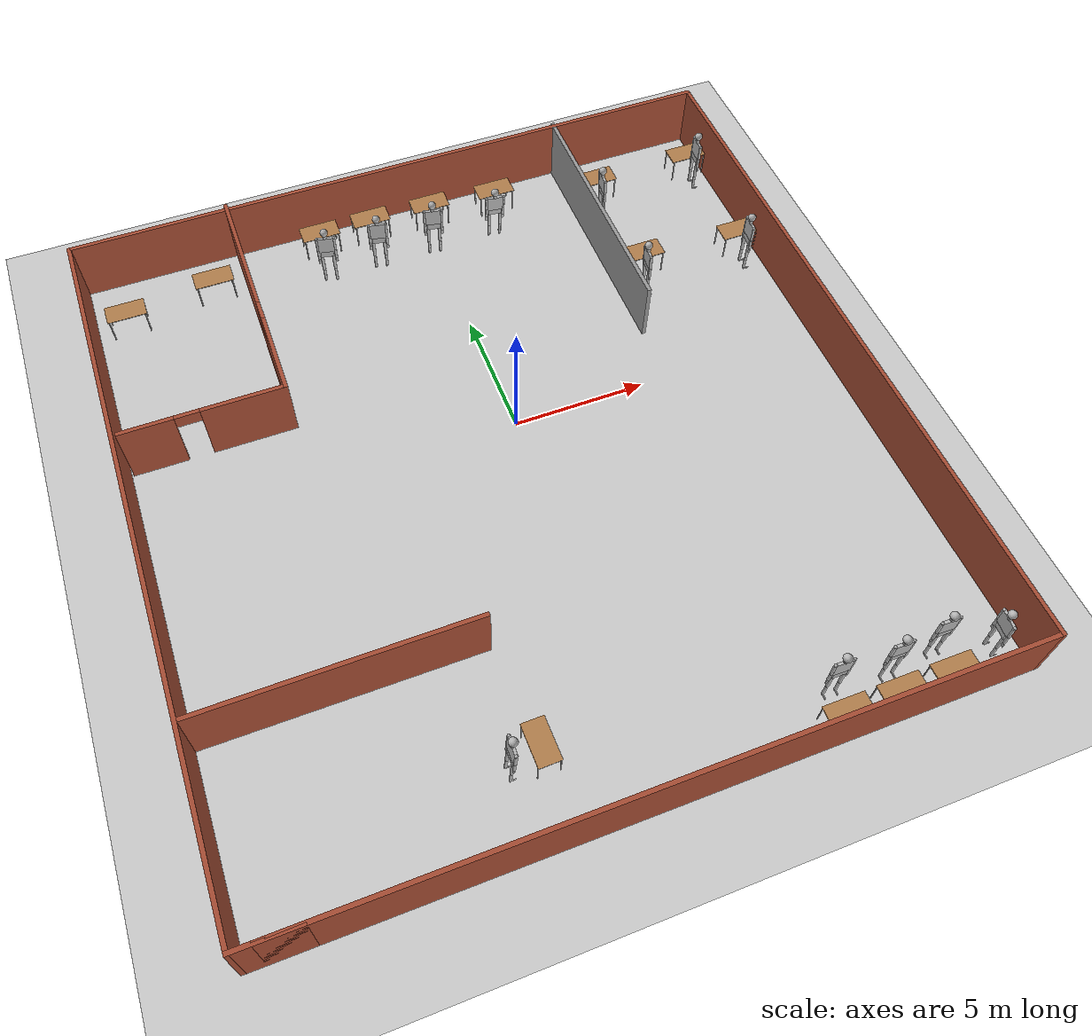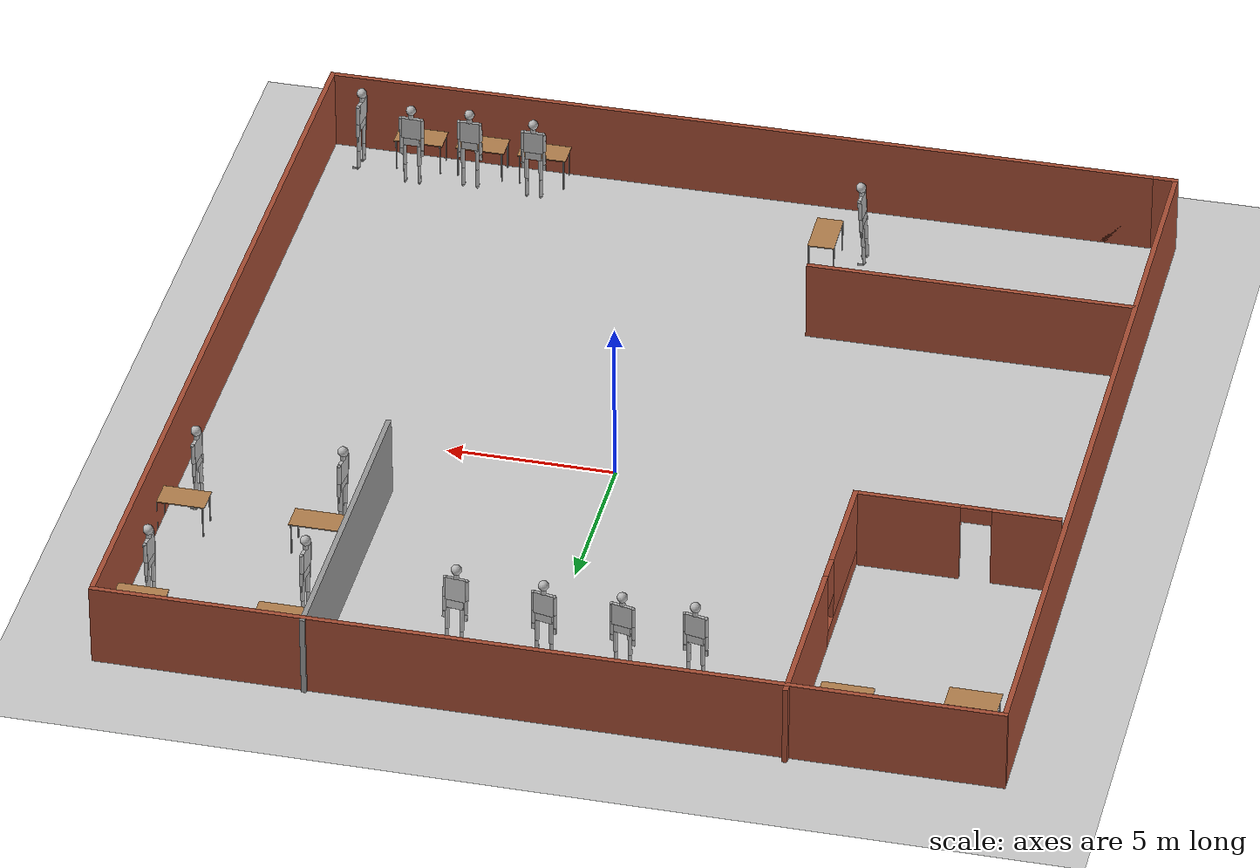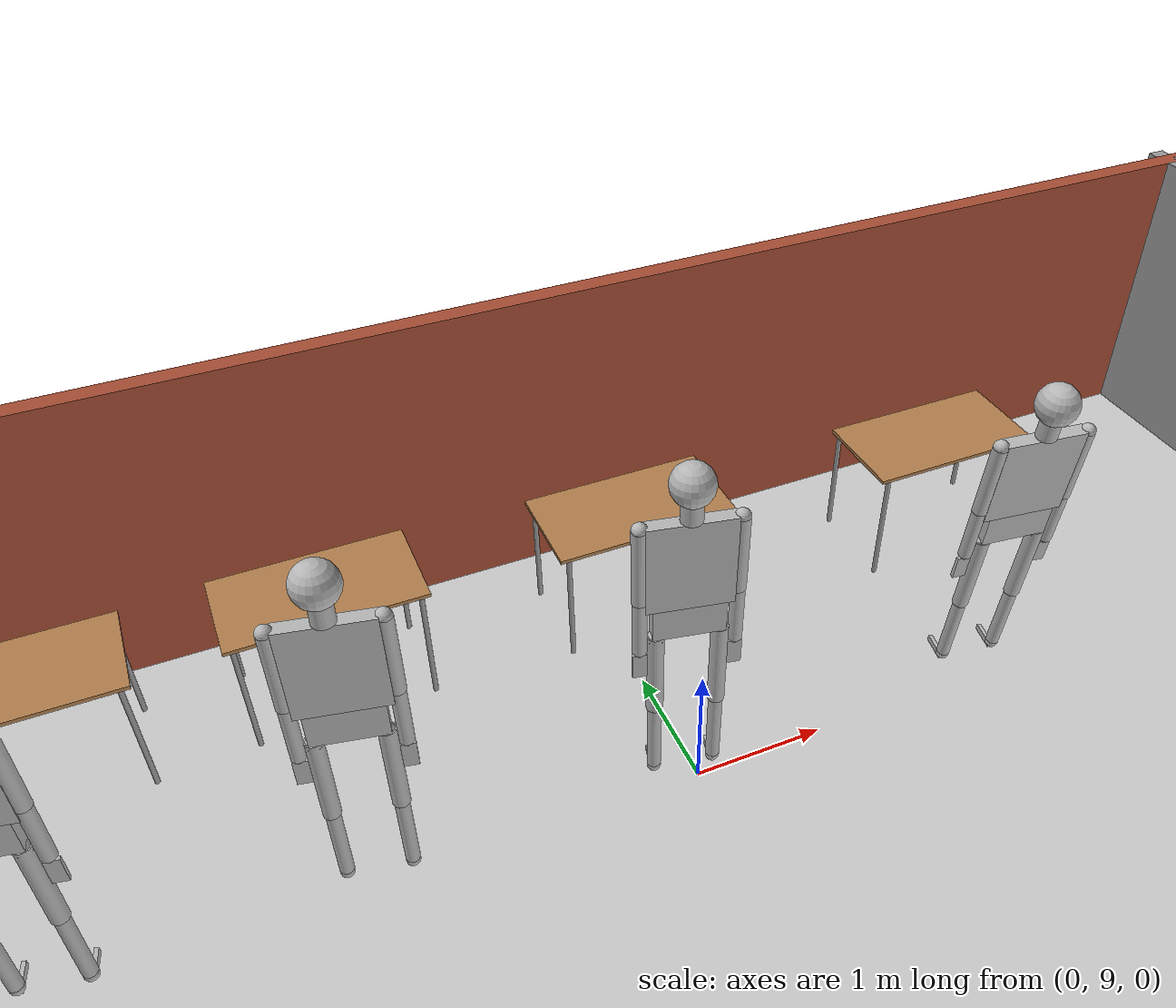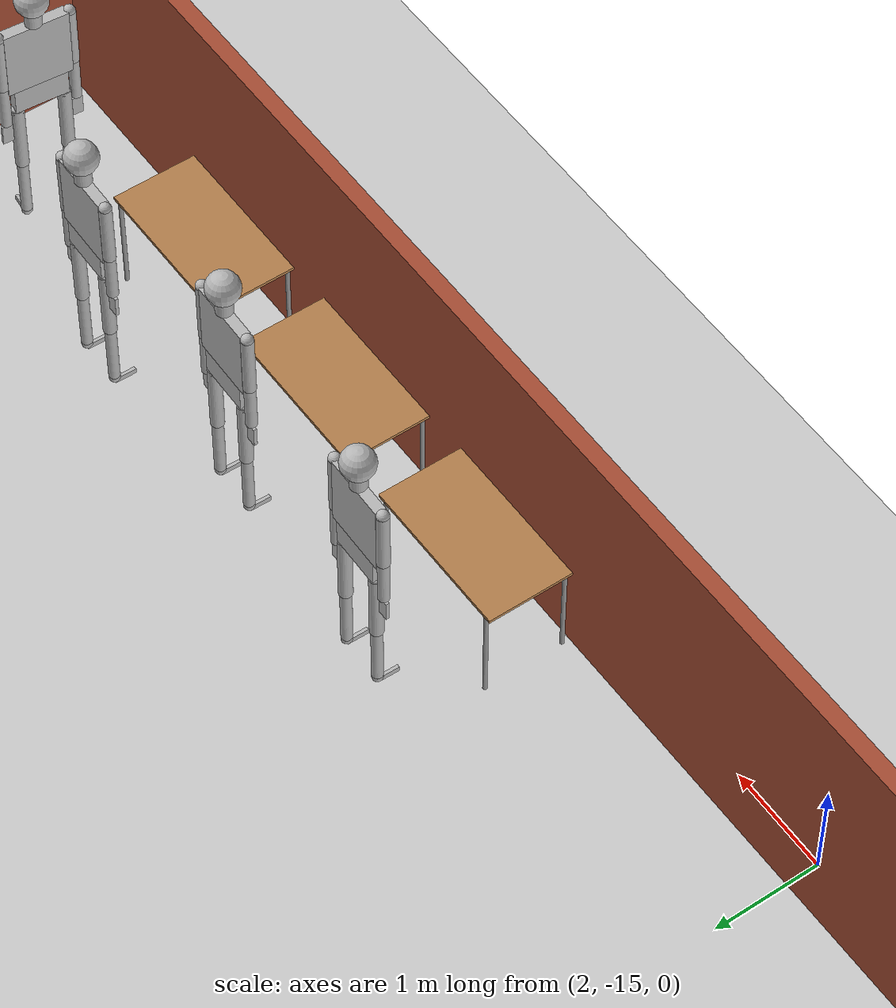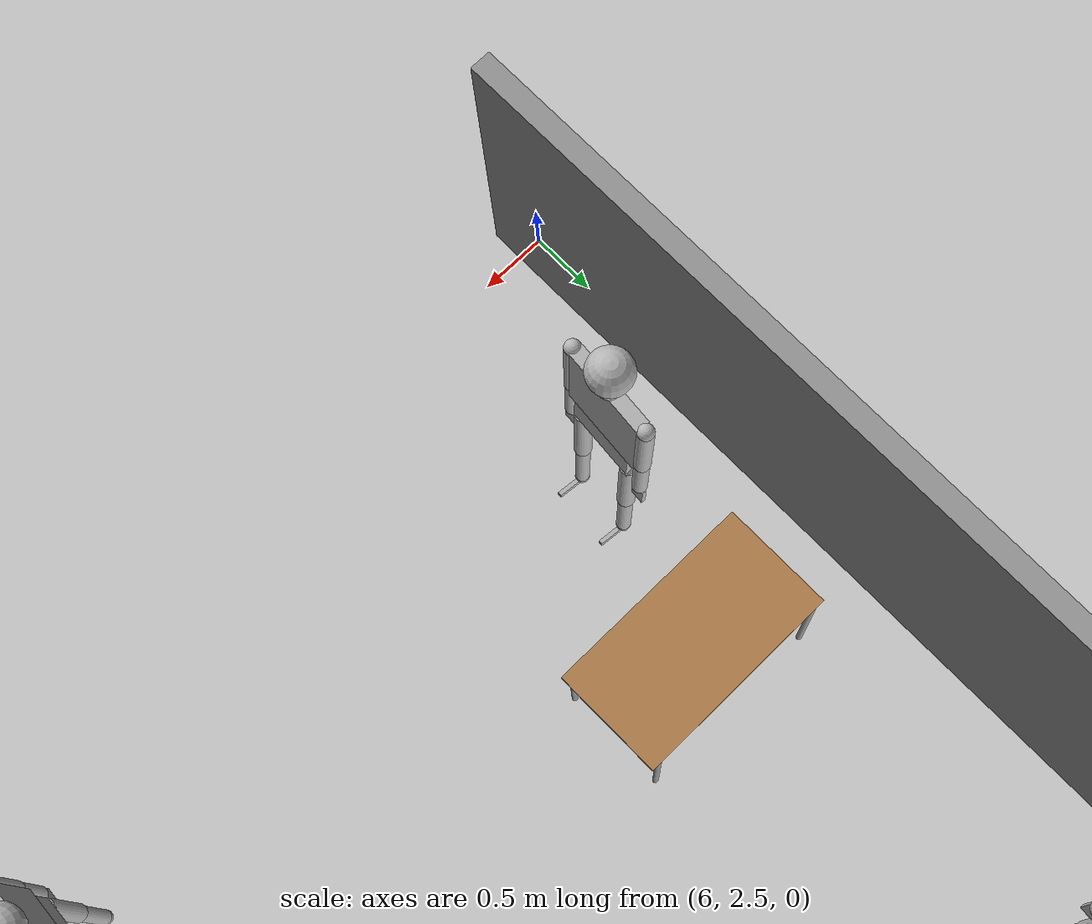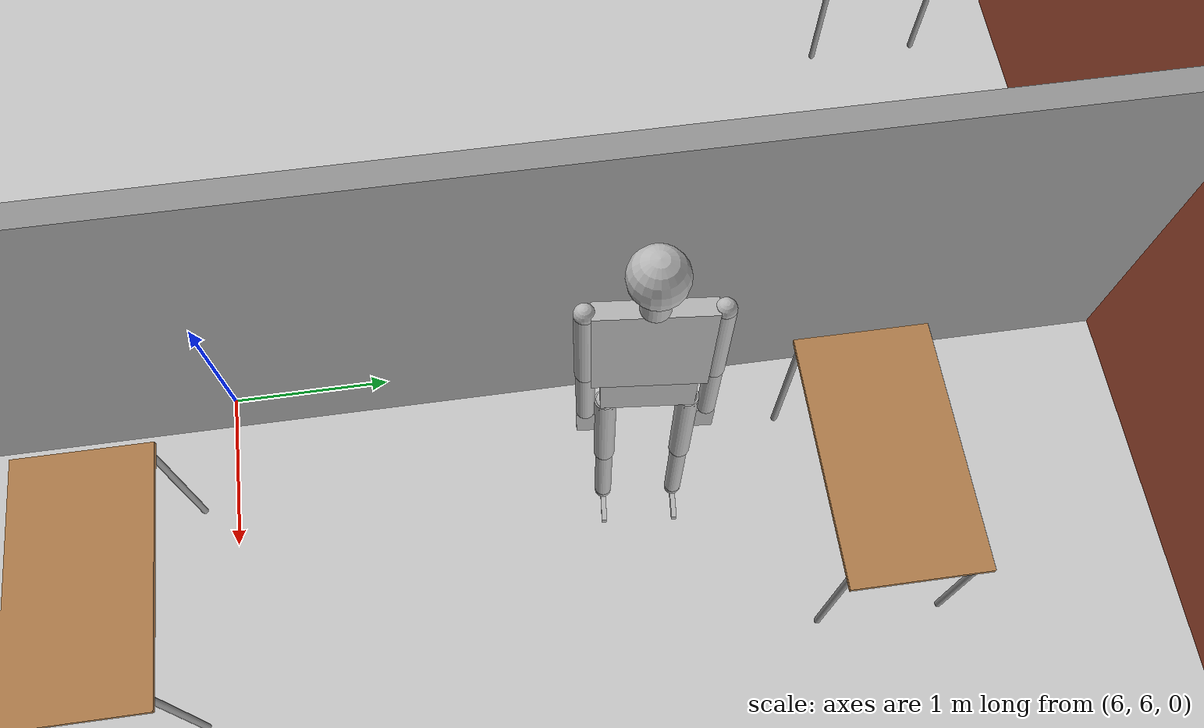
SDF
<sdf version="1.7">
 <world name="default">
  <light name="sun" type="directional">
   <pose>0 0 10 0 -0 0</pose>
   <diffuse>0.8 0.8 0.8 1</diffuse>
   <specular>0.2 0.2 0.2 1</specular>
   <attenuation>
    <range>1000</range>
    <constant>0.9</constant>
    <linear>0.01</linear>
    <quadratic>0.001</quadratic>
   </attenuation>
   <direction>-0.5 0.1 -0.9</direction>
   <spot><inner_angle>0</inner_angle><outer_angle>0</outer_angle><falloff>0</falloff></spot>
  </light>
  <model name="ground_plane">
   <static>1</static>
   <link name="link">
    <collision name="collision">
     <geometry><plane><normal>0 0 1</normal><size>100 100</size></plane></geometry>
     <surface>
      <contact><collide_bitmask>65535</collide_bitmask></contact>
      <friction><ode><mu>100</mu><mu2>50</mu2></ode></friction>
     </surface>
    </collision>
    <visual name="visual">
     <cast_shadows>0</cast_shadows>
     <geometry><plane><normal>0 0 1</normal><size>100 100</size></plane></geometry>
     <material>
      <script><uri>file://media/materials/scripts/gazebo.material</uri><name>Gazebo/Grey</name></script>
     </material>
    </visual>
   </link>
  </model>
  <gravity>0 0 -9.8</gravity>
  <magnetic_field>6e-06 2.3e-05 -4.2e-05</magnetic_field>
  <atmosphere type="adiabatic"/>
  <physics type="ode">
   <max_step_size>0.001</max_step_size>
   <real_time_factor>1</real_time_factor>
   <real_time_update_rate>1000</real_time_update_rate>
  </physics>
  <scene><ambient>0.4 0.4 0.4 1</ambient><background>0.7 0.7 0.7 1</background><shadows>1</shadows></scene>
  <audio><device>default</device></audio>
  <spherical_coordinates>
   <surface_model>EARTH_WGS84</surface_model>
   <latitude_deg>0</latitude_deg>
   <longitude_deg>0</longitude_deg>
   <elevation>0</elevation>
   <heading_deg>0</heading_deg>
  </spherical_coordinates>
  <model name="my.world">
   <pose>-0.736327 -1.3622 0 0 -0 0</pose>
   <link name="Wall_12">
    <collision name="Wall_12_Collision">
     <geometry><box><size>25.25 0.15 2.5</size></box></geometry>
     <pose>0 0 1.25 0 -0 0</pose>
    </collision>
    <visual name="Wall_12_Visual">
     <pose>0 0 1.25 0 -0 0</pose>
     <geometry><box><size>25.25 0.15 2.5</size></box></geometry>
     <material>
      <script><uri>file://media/materials/scripts/gazebo.material</uri><name>Gazebo/Bricks</name></script>
      <ambient>1 1 1 1</ambient>
     </material>
     <meta><layer>0</layer></meta>
    </visual>
    <pose>0.375 -13.4013 0 0 -0 0</pose>
   </link>
   <link name="Wall_13">
    <collision name="Wall_13_Collision">
     <geometry><box><size>26.75 0.15 2.5</size></box></geometry>
     <pose>0 0 1.25 0 -0 0</pose>
    </collision>
    <visual name="Wall_13_Visual">
     <pose>0 0 1.25 0 -0 0</pose>
     <geometry><box><size>26.75 0.15 2.5</size></box></geometry>
     <material>
      <script><uri>file://media/materials/scripts/gazebo.material</uri><name>Gazebo/Bricks</name></script>
      <ambient>1 1 1 1</ambient>
     </material>
     <meta><layer>0</layer></meta>
    </visual>
    <pose>12.925 -0.101338 0 0 -0 1.5708</pose>
   </link>
   <link name="Wall_14">
    <collision name="Wall_14_Collision">
     <geometry><box><size>26 0.15 2.5</size></box></geometry>
     <pose>0 0 1.25 0 -0 0</pose>
    </collision>
    <visual name="Wall_14_Visual">
     <pose>0 0 1.25 0 -0 0</pose>
     <geometry><box><size>26 0.15 2.5</size></box></geometry>
     <material>
      <script><uri>file://media/materials/scripts/gazebo.material</uri><name>Gazebo/Bricks</name></script>
      <ambient>1 1 1 1</ambient>
     </material>
     <meta><layer>0</layer></meta>
    </visual>
    <pose>-0 13.1987 0 0 -0 3.14159</pose>
   </link>
   <link name="Wall_15">
    <collision name="Wall_15_Collision">
     <geometry><box><size>26.75 0.15 2.5</size></box></geometry>
     <pose>0 0 1.25 0 -0 0</pose>
    </collision>
    <visual name="Wall_15_Visual">
     <pose>0 0 1.25 0 -0 0</pose>
     <geometry><box><size>26.75 0.15 2.5</size></box></geometry>
     <material>
      <script><uri>file://media/materials/scripts/gazebo.material</uri><name>Gazebo/Bricks</name></script>
      <ambient>1 1 1 1</ambient>
     </material>
     <meta><layer>0</layer></meta>
    </visual>
    <pose>-12.925 -0.101338 0 0 -0 -1.5708</pose>
   </link>
   <link name="Wall_16">
    <collision name="Wall_16_Collision">
     <geometry><box><size>2.25 0.15 2.5</size></box></geometry>
     <pose>0 0 1.25 0 -0 0</pose>
    </collision>
    <visual name="Wall_16_Visual">
     <pose>0 0 1.25 0 -0 0</pose>
     <geometry><box><size>2.25 0.15 2.5</size></box></geometry>
     <material>
      <script><uri>file://media/materials/scripts/gazebo.material</uri><name>Gazebo/Bricks</name></script>
      <ambient>1 1 1 1</ambient>
     </material>
     <meta><layer>0</layer></meta>
    </visual>
    <pose>-11.875 -13.4013 0 0 -0 0</pose>
   </link>
   <link name="Wall_18">
    <pose>-6.84868 8.72634 0 0 -0 -1.5708</pose>
    <visual name="Wall_18_Visual_0">
     <pose>-2.07687 0 1.25 0 -0 0</pose>
     <geometry><box><size>5.34626 0.15 2.5</size></box></geometry>
     <material>
      <script><uri>file://media/materials/scripts/gazebo.material</uri><name>Gazebo/Bricks</name></script>
      <ambient>0.760784 0.662745 0.627451 1</ambient>
     </material>
     <meta><layer>0</layer></meta>
    </visual>
    <collision name="Wall_18_Collision_0">
     <geometry><box><size>5.34626 0.15 2.5</size></box></geometry>
     <pose>-2.07687 0 1.25 0 -0 0</pose>
    </collision>
    <visual name="Wall_18_Visual_1">
     <pose>2.67313 0 0.25 0 -0 0</pose>
     <geometry><box><size>4.15374 0.15 0.5</size></box></geometry>
     <material>
      <script><uri>file://media/materials/scripts/gazebo.material</uri><name>Gazebo/Bricks</name></script>
      <ambient>0.760784 0.662745 0.627451 1</ambient>
     </material>
     <meta><layer>0</layer></meta>
    </visual>
    <collision name="Wall_18_Collision_1">
     <geometry><box><size>4.15374 0.15 0.5</size></box></geometry>
     <pose>2.67313 0 0.25 0 -0 0</pose>
    </collision>
    <visual name="Wall_18_Visual_2">
     <pose>3.07313 0 1.5 0 -0 0</pose>
     <geometry><box><size>3.35373 0.15 2</size></box></geometry>
     <material>
      <script><uri>file://media/materials/scripts/gazebo.material</uri><name>Gazebo/Bricks</name></script>
      <ambient>0.760784 0.662745 0.627451 1</ambient>
     </material>
     <meta><layer>0</layer></meta>
    </visual>
    <collision name="Wall_18_Collision_2">
     <geometry><box><size>3.35373 0.15 2</size></box></geometry>
     <pose>3.07313 0 1.5 0 -0 0</pose>
    </collision>
    <visual name="Wall_18_Visual_3">
     <pose>0.996265 0 1.9 0 -0 0</pose>
     <geometry><box><size>0.8 0.15 1.2</size></box></geometry>
     <material>
      <script><uri>file://media/materials/scripts/gazebo.material</uri><name>Gazebo/Bricks</name></script>
      <ambient>0.760784 0.662745 0.627451 1</ambient>
     </material>
     <meta><layer>0</layer></meta>
    </visual>
    <collision name="Wall_18_Collision_3">
     <geometry><box><size>0.8 0.15 1.2</size></box></geometry>
     <pose>0.996265 0 1.9 0 -0 0</pose>
    </collision>
   </link>
   <link name="Wall_19">
    <pose>-9.77368 4.05134 0 0 -0 3.14159</pose>
    <visual name="Wall_19_Visual_0">
     <pose>-1.44867 0 1.25 0 -0 0</pose>
     <geometry><box><size>3.10266 0.15 2.5</size></box></geometry>
     <material>
      <script><uri>file://media/materials/scripts/gazebo.material</uri><name>Gazebo/Bricks</name></script>
      <ambient>0.760784 0.662745 0.627451 1</ambient>
     </material>
     <meta><layer>0</layer></meta>
    </visual>
    <collision name="Wall_19_Collision_0">
     <geometry><box><size>3.10266 0.15 2.5</size></box></geometry>
     <pose>-1.44867 0 1.25 0 -0 0</pose>
    </collision>
    <visual name="Wall_19_Visual_1">
     <pose>2.00133 0 1.25 0 -0 0</pose>
     <geometry><box><size>1.99734 0.15 2.5</size></box></geometry>
     <material>
      <script><uri>file://media/materials/scripts/gazebo.material</uri><name>Gazebo/Bricks</name></script>
      <ambient>0.760784 0.662745 0.627451 1</ambient>
     </material>
     <meta><layer>0</layer></meta>
    </visual>
    <collision name="Wall_19_Collision_1">
     <geometry><box><size>1.99734 0.15 2.5</size></box></geometry>
     <pose>2.00133 0 1.25 0 -0 0</pose>
    </collision>
    <visual name="Wall_19_Visual_2">
     <pose>0.552663 0 2.25 0 -0 0</pose>
     <geometry><box><size>0.9 0.15 0.5</size></box></geometry>
     <material>
      <script><uri>file://media/materials/scripts/gazebo.material</uri><name>Gazebo/Bricks</name></script>
      <ambient>0.760784 0.662745 0.627451 1</ambient>
     </material>
     <meta><layer>0</layer></meta>
    </visual>
    <collision name="Wall_19_Collision_2">
     <geometry><box><size>0.9 0.15 0.5</size></box></geometry>
     <pose>0.552663 0 2.25 0 -0 0</pose>
    </collision>
   </link>
   <link name="Wall_21">
    <collision name="Wall_21_Collision">
     <geometry><box><size>9.75 0.15 2.5</size></box></geometry>
     <pose>0 0 1.25 0 -0 0</pose>
    </collision>
    <visual name="Wall_21_Visual">
     <pose>0 0 1.25 0 -0 0</pose>
     <geometry><box><size>9.75 0.15 2.5</size></box></geometry>
     <material>
      <script><uri>file://media/materials/scripts/gazebo.material</uri><name>Gazebo/Bricks</name></script>
      <ambient>1 1 1 1</ambient>
     </material>
     <meta><layer>0</layer></meta>
    </visual>
    <pose>-8.04096 -6.6621 0 0 -0 0</pose>
   </link>
   <link name="Wall_23">
    <collision name="Wall_23_Collision">
     <geometry><box><size>9.75 0.15 2.5</size></box></geometry>
     <pose>0 0 1.25 0 -0 0</pose>
    </collision>
    <visual name="Wall_23_Visual">
     <pose>0 0 1.25 0 -0 0</pose>
     <geometry><box><size>9.75 0.15 2.5</size></box></geometry>
     <material>
      <script><uri>file://media/materials/scripts/gazebo.material</uri><name>Gazebo/Grey</name></script>
      <ambient>0 0 0 1</ambient>
     </material>
     <meta><layer>0</layer></meta>
    </visual>
    <pose>6.84796 8.49433 0 0 -0 -1.5708</pose>
   </link>
   <static>1</static>
  </model>
  <model name="table">
   <static>1</static>
   <link name="link">
    <collision name="surface">
     <pose>0 0 1 0 -0 0</pose>
     <geometry><box><size>1.5 0.8 0.03</size></box></geometry>
     <surface><friction><ode><mu>0.6</mu><mu2>0.6</mu2></ode></friction></surface>
    </collision>
    <visual name="visual1">
     <pose>0 0 1 0 -0 0</pose>
     <geometry><box><size>1.5 0.8 0.03</size></box></geometry>
     <material>
      <script><uri>file://media/materials/scripts/gazebo.material</uri><name>Gazebo/Wood</name></script>
     </material>
    </visual>
    <collision name="front_left_leg">
     <pose>0.68 0.38 0.5 0 -0 0</pose>
     <geometry><cylinder><radius>0.02</radius><length>1</length></cylinder></geometry>
    </collision>
    <visual name="front_left_leg">
     <pose>0.68 0.38 0.5 0 -0 0</pose>
     <geometry><cylinder><radius>0.02</radius><length>1</length></cylinder></geometry>
     <material>
      <script><uri>file://media/materials/scripts/gazebo.material</uri><name>Gazebo/Grey</name></script>
     </material>
    </visual>
    <collision name="front_right_leg">
     <pose>0.68 -0.38 0.5 0 -0 0</pose>
     <geometry><cylinder><radius>0.02</radius><length>1</length></cylinder></geometry>
    </collision>
    <visual name="front_right_leg">
     <pose>0.68 -0.38 0.5 0 -0 0</pose>
     <geometry><cylinder><radius>0.02</radius><length>1</length></cylinder></geometry>
     <material>
      <script><uri>file://media/materials/scripts/gazebo.material</uri><name>Gazebo/Grey</name></script>
     </material>
    </visual>
    <collision name="back_right_leg">
     <pose>-0.68 -0.38 0.5 0 -0 0</pose>
     <geometry><cylinder><radius>0.02</radius><length>1</length></cylinder></geometry>
    </collision>
    <visual name="back_right_leg">
     <pose>-0.68 -0.38 0.5 0 -0 0</pose>
     <geometry><cylinder><radius>0.02</radius><length>1</length></cylinder></geometry>
     <material>
      <script><uri>file://media/materials/scripts/gazebo.material</uri><name>Gazebo/Grey</name></script>
     </material>
    </visual>
    <collision name="back_left_leg">
     <pose>-0.68 0.38 0.5 0 -0 0</pose>
     <geometry><cylinder><radius>0.02</radius><length>1</length></cylinder></geometry>
    </collision>
    <visual name="back_left_leg">
     <pose>-0.68 0.38 0.5 0 -0 0</pose>
     <geometry><cylinder><radius>0.02</radius><length>1</length></cylinder></geometry>
     <material>
      <script><uri>file://media/materials/scripts/gazebo.material</uri><name>Gazebo/Grey</name></script>
     </material>
    </visual>
   </link>
   <pose>5.49775 -14.2405 0 0 -0 0</pose>
  </model>
  <model name="table_clone">
   <static>1</static>
   <link name="link">
    <collision name="surface">
     <pose>0 0 1 0 -0 0</pose>
     <geometry><box><size>1.5 0.8 0.03</size></box></geometry>
     <surface><friction><ode><mu>0.6</mu><mu2>0.6</mu2></ode></friction></surface>
    </collision>
    <visual name="visual1">
     <pose>0 0 1 0 -0 0</pose>
     <geometry><box><size>1.5 0.8 0.03</size></box></geometry>
     <material>
      <script><uri>file://media/materials/scripts/gazebo.material</uri><name>Gazebo/Wood</name></script>
     </material>
    </visual>
    <collision name="front_left_leg">
     <pose>0.68 0.38 0.5 0 -0 0</pose>
     <geometry><cylinder><radius>0.02</radius><length>1</length></cylinder></geometry>
    </collision>
    <visual name="front_left_leg">
     <pose>0.68 0.38 0.5 0 -0 0</pose>
     <geometry><cylinder><radius>0.02</radius><length>1</length></cylinder></geometry>
     <material>
      <script><uri>file://media/materials/scripts/gazebo.material</uri><name>Gazebo/Grey</name></script>
     </material>
    </visual>
    <collision name="front_right_leg">
     <pose>0.68 -0.38 0.5 0 -0 0</pose>
     <geometry><cylinder><radius>0.02</radius><length>1</length></cylinder></geometry>
    </collision>
    <visual name="front_right_leg">
     <pose>0.68 -0.38 0.5 0 -0 0</pose>
     <geometry><cylinder><radius>0.02</radius><length>1</length></cylinder></geometry>
     <material>
      <script><uri>file://media/materials/scripts/gazebo.material</uri><name>Gazebo/Grey</name></script>
     </material>
    </visual>
    <collision name="back_right_leg">
     <pose>-0.68 -0.38 0.5 0 -0 0</pose>
     <geometry><cylinder><radius>0.02</radius><length>1</length></cylinder></geometry>
    </collision>
    <visual name="back_right_leg">
     <pose>-0.68 -0.38 0.5 0 -0 0</pose>
     <geometry><cylinder><radius>0.02</radius><length>1</length></cylinder></geometry>
     <material>
      <script><uri>file://media/materials/scripts/gazebo.material</uri><name>Gazebo/Grey</name></script>
     </material>
    </visual>
    <collision name="back_left_leg">
     <pose>-0.68 0.38 0.5 0 -0 0</pose>
     <geometry><cylinder><radius>0.02</radius><length>1</length></cylinder></geometry>
    </collision>
    <visual name="back_left_leg">
     <pose>-0.68 0.38 0.5 0 -0 0</pose>
     <geometry><cylinder><radius>0.02</radius><length>1</length></cylinder></geometry>
     <material>
      <script><uri>file://media/materials/scripts/gazebo.material</uri><name>Gazebo/Grey</name></script>
     </material>
    </visual>
   </link>
   <pose>7.40672 -14.2219 0 0 -0 0</pose>
  </model>
  <model name="table_clone_0">
   <static>1</static>
   <link name="link">
    <collision name="surface">
     <pose>0 0 1 0 -0 0</pose>
     <geometry><box><size>1.5 0.8 0.03</size></box></geometry>
     <surface><friction><ode><mu>0.6</mu><mu2>0.6</mu2></ode></friction></surface>
    </collision>
    <visual name="visual1">
     <pose>0 0 1 0 -0 0</pose>
     <geometry><box><size>1.5 0.8 0.03</size></box></geometry>
     <material>
      <script><uri>file://media/materials/scripts/gazebo.material</uri><name>Gazebo/Wood</name></script>
     </material>
    </visual>
    <collision name="front_left_leg">
     <pose>0.68 0.38 0.5 0 -0 0</pose>
     <geometry><cylinder><radius>0.02</radius><length>1</length></cylinder></geometry>
    </collision>
    <visual name="front_left_leg">
     <pose>0.68 0.38 0.5 0 -0 0</pose>
     <geometry><cylinder><radius>0.02</radius><length>1</length></cylinder></geometry>
     <material>
      <script><uri>file://media/materials/scripts/gazebo.material</uri><name>Gazebo/Grey</name></script>
     </material>
    </visual>
    <collision name="front_right_leg">
     <pose>0.68 -0.38 0.5 0 -0 0</pose>
     <geometry><cylinder><radius>0.02</radius><length>1</length></cylinder></geometry>
    </collision>
    <visual name="front_right_leg">
     <pose>0.68 -0.38 0.5 0 -0 0</pose>
     <geometry><cylinder><radius>0.02</radius><length>1</length></cylinder></geometry>
     <material>
      <script><uri>file://media/materials/scripts/gazebo.material</uri><name>Gazebo/Grey</name></script>
     </material>
    </visual>
    <collision name="back_right_leg">
     <pose>-0.68 -0.38 0.5 0 -0 0</pose>
     <geometry><cylinder><radius>0.02</radius><length>1</length></cylinder></geometry>
    </collision>
    <visual name="back_right_leg">
     <pose>-0.68 -0.38 0.5 0 -0 0</pose>
     <geometry><cylinder><radius>0.02</radius><length>1</length></cylinder></geometry>
     <material>
      <script><uri>file://media/materials/scripts/gazebo.material</uri><name>Gazebo/Grey</name></script>
     </material>
    </visual>
    <collision name="back_left_leg">
     <pose>-0.68 0.38 0.5 0 -0 0</pose>
     <geometry><cylinder><radius>0.02</radius><length>1</length></cylinder></geometry>
    </collision>
    <visual name="back_left_leg">
     <pose>-0.68 0.38 0.5 0 -0 0</pose>
     <geometry><cylinder><radius>0.02</radius><length>1</length></cylinder></geometry>
     <material>
      <script><uri>file://media/materials/scripts/gazebo.material</uri><name>Gazebo/Grey</name></script>
     </material>
    </visual>
   </link>
   <pose>9.31619 -14.2014 0 0 -0 0</pose>
  </model>
  <model name="table_clone_1">
   <static>1</static>
   <link name="link">
    <collision name="surface">
     <pose>0 0 1 0 -0 0</pose>
     <geometry><box><size>1.5 0.8 0.03</size></box></geometry>
     <surface><friction><ode><mu>0.6</mu><mu2>0.6</mu2></ode></friction></surface>
    </collision>
    <visual name="visual1">
     <pose>0 0 1 0 -0 0</pose>
     <geometry><box><size>1.5 0.8 0.03</size></box></geometry>
     <material>
      <script><uri>file://media/materials/scripts/gazebo.material</uri><name>Gazebo/Wood</name></script>
     </material>
    </visual>
    <collision name="front_left_leg">
     <pose>0.68 0.38 0.5 0 -0 0</pose>
     <geometry><cylinder><radius>0.02</radius><length>1</length></cylinder></geometry>
    </collision>
    <visual name="front_left_leg">
     <pose>0.68 0.38 0.5 0 -0 0</pose>
     <geometry><cylinder><radius>0.02</radius><length>1</length></cylinder></geometry>
     <material>
      <script><uri>file://media/materials/scripts/gazebo.material</uri><name>Gazebo/Grey</name></script>
     </material>
    </visual>
    <collision name="front_right_leg">
     <pose>0.68 -0.38 0.5 0 -0 0</pose>
     <geometry><cylinder><radius>0.02</radius><length>1</length></cylinder></geometry>
    </collision>
    <visual name="front_right_leg">
     <pose>0.68 -0.38 0.5 0 -0 0</pose>
     <geometry><cylinder><radius>0.02</radius><length>1</length></cylinder></geometry>
     <material>
      <script><uri>file://media/materials/scripts/gazebo.material</uri><name>Gazebo/Grey</name></script>
     </material>
    </visual>
    <collision name="back_right_leg">
     <pose>-0.68 -0.38 0.5 0 -0 0</pose>
     <geometry><cylinder><radius>0.02</radius><length>1</length></cylinder></geometry>
    </collision>
    <visual name="back_right_leg">
     <pose>-0.68 -0.38 0.5 0 -0 0</pose>
     <geometry><cylinder><radius>0.02</radius><length>1</length></cylinder></geometry>
     <material>
      <script><uri>file://media/materials/scripts/gazebo.material</uri><name>Gazebo/Grey</name></script>
     </material>
    </visual>
    <collision name="back_left_leg">
     <pose>-0.68 0.38 0.5 0 -0 0</pose>
     <geometry><cylinder><radius>0.02</radius><length>1</length></cylinder></geometry>
    </collision>
    <visual name="back_left_leg">
     <pose>-0.68 0.38 0.5 0 -0 0</pose>
     <geometry><cylinder><radius>0.02</radius><length>1</length></cylinder></geometry>
     <material>
      <script><uri>file://media/materials/scripts/gazebo.material</uri><name>Gazebo/Grey</name></script>
     </material>
    </visual>
   </link>
   <pose>11.3889 9.93313 0 0 -0 0</pose>
  </model>
  <model name="table_clone_2">
   <static>1</static>
   <link name="link">
    <collision name="surface">
     <pose>0 0 1 0 -0 0</pose>
     <geometry><box><size>1.5 0.8 0.03</size></box></geometry>
     <surface><friction><ode><mu>0.6</mu><mu2>0.6</mu2></ode></friction></surface>
    </collision>
    <visual name="visual1">
     <pose>0 0 1 0 -0 0</pose>
     <geometry><box><size>1.5 0.8 0.03</size></box></geometry>
     <material>
      <script><uri>file://media/materials/scripts/gazebo.material</uri><name>Gazebo/Wood</name></script>
     </material>
    </visual>
    <collision name="front_left_leg">
     <pose>0.68 0.38 0.5 0 -0 0</pose>
     <geometry><cylinder><radius>0.02</radius><length>1</length></cylinder></geometry>
    </collision>
    <visual name="front_left_leg">
     <pose>0.68 0.38 0.5 0 -0 0</pose>
     <geometry><cylinder><radius>0.02</radius><length>1</length></cylinder></geometry>
     <material>
      <script><uri>file://media/materials/scripts/gazebo.material</uri><name>Gazebo/Grey</name></script>
     </material>
    </visual>
    <collision name="front_right_leg">
     <pose>0.68 -0.38 0.5 0 -0 0</pose>
     <geometry><cylinder><radius>0.02</radius><length>1</length></cylinder></geometry>
    </collision>
    <visual name="front_right_leg">
     <pose>0.68 -0.38 0.5 0 -0 0</pose>
     <geometry><cylinder><radius>0.02</radius><length>1</length></cylinder></geometry>
     <material>
      <script><uri>file://media/materials/scripts/gazebo.material</uri><name>Gazebo/Grey</name></script>
     </material>
    </visual>
    <collision name="back_right_leg">
     <pose>-0.68 -0.38 0.5 0 -0 0</pose>
     <geometry><cylinder><radius>0.02</radius><length>1</length></cylinder></geometry>
    </collision>
    <visual name="back_right_leg">
     <pose>-0.68 -0.38 0.5 0 -0 0</pose>
     <geometry><cylinder><radius>0.02</radius><length>1</length></cylinder></geometry>
     <material>
      <script><uri>file://media/materials/scripts/gazebo.material</uri><name>Gazebo/Grey</name></script>
     </material>
    </visual>
    <collision name="back_left_leg">
     <pose>-0.68 0.38 0.5 0 -0 0</pose>
     <geometry><cylinder><radius>0.02</radius><length>1</length></cylinder></geometry>
    </collision>
    <visual name="back_left_leg">
     <pose>-0.68 0.38 0.5 0 -0 0</pose>
     <geometry><cylinder><radius>0.02</radius><length>1</length></cylinder></geometry>
     <material>
      <script><uri>file://media/materials/scripts/gazebo.material</uri><name>Gazebo/Grey</name></script>
     </material>
    </visual>
   </link>
   <pose>11.4461 5.18586 0 0 -0 0</pose>
  </model>
  <model name="table_clone_3">
   <static>1</static>
   <link name="link">
    <collision name="surface">
     <pose>0 0 1 0 -0 0</pose>
     <geometry><box><size>1.5 0.8 0.03</size></box></geometry>
     <surface><friction><ode><mu>0.6</mu><mu2>0.6</mu2></ode></friction></surface>
    </collision>
    <visual name="visual1">
     <pose>0 0 1 0 -0 0</pose>
     <geometry><box><size>1.5 0.8 0.03</size></box></geometry>
     <material>
      <script><uri>file://media/materials/scripts/gazebo.material</uri><name>Gazebo/Wood</name></script>
     </material>
    </visual>
    <collision name="front_left_leg">
     <pose>0.68 0.38 0.5 0 -0 0</pose>
     <geometry><cylinder><radius>0.02</radius><length>1</length></cylinder></geometry>
    </collision>
    <visual name="front_left_leg">
     <pose>0.68 0.38 0.5 0 -0 0</pose>
     <geometry><cylinder><radius>0.02</radius><length>1</length></cylinder></geometry>
     <material>
      <script><uri>file://media/materials/scripts/gazebo.material</uri><name>Gazebo/Grey</name></script>
     </material>
    </visual>
    <collision name="front_right_leg">
     <pose>0.68 -0.38 0.5 0 -0 0</pose>
     <geometry><cylinder><radius>0.02</radius><length>1</length></cylinder></geometry>
    </collision>
    <visual name="front_right_leg">
     <pose>0.68 -0.38 0.5 0 -0 0</pose>
     <geometry><cylinder><radius>0.02</radius><length>1</length></cylinder></geometry>
     <material>
      <script><uri>file://media/materials/scripts/gazebo.material</uri><name>Gazebo/Grey</name></script>
     </material>
    </visual>
    <collision name="back_right_leg">
     <pose>-0.68 -0.38 0.5 0 -0 0</pose>
     <geometry><cylinder><radius>0.02</radius><length>1</length></cylinder></geometry>
    </collision>
    <visual name="back_right_leg">
     <pose>-0.68 -0.38 0.5 0 -0 0</pose>
     <geometry><cylinder><radius>0.02</radius><length>1</length></cylinder></geometry>
     <material>
      <script><uri>file://media/materials/scripts/gazebo.material</uri><name>Gazebo/Grey</name></script>
     </material>
    </visual>
    <collision name="back_left_leg">
     <pose>-0.68 0.38 0.5 0 -0 0</pose>
     <geometry><cylinder><radius>0.02</radius><length>1</length></cylinder></geometry>
    </collision>
    <visual name="back_left_leg">
     <pose>-0.68 0.38 0.5 0 -0 0</pose>
     <geometry><cylinder><radius>0.02</radius><length>1</length></cylinder></geometry>
     <material>
      <script><uri>file://media/materials/scripts/gazebo.material</uri><name>Gazebo/Grey</name></script>
     </material>
    </visual>
   </link>
   <pose>7.28512 9.8867 0 0 -0 0</pose>
  </model>
  <model name="table_clone_4">
   <static>1</static>
   <link name="link">
    <collision name="surface">
     <pose>0 0 1 0 -0 0</pose>
     <geometry><box><size>1.5 0.8 0.03</size></box></geometry>
     <surface><friction><ode><mu>0.6</mu><mu2>0.6</mu2></ode></friction></surface>
    </collision>
    <visual name="visual1">
     <pose>0 0 1 0 -0 0</pose>
     <geometry><box><size>1.5 0.8 0.03</size></box></geometry>
     <material>
      <script><uri>file://media/materials/scripts/gazebo.material</uri><name>Gazebo/Wood</name></script>
     </material>
    </visual>
    <collision name="front_left_leg">
     <pose>0.68 0.38 0.5 0 -0 0</pose>
     <geometry><cylinder><radius>0.02</radius><length>1</length></cylinder></geometry>
    </collision>
    <visual name="front_left_leg">
     <pose>0.68 0.38 0.5 0 -0 0</pose>
     <geometry><cylinder><radius>0.02</radius><length>1</length></cylinder></geometry>
     <material>
      <script><uri>file://media/materials/scripts/gazebo.material</uri><name>Gazebo/Grey</name></script>
     </material>
    </visual>
    <collision name="front_right_leg">
     <pose>0.68 -0.38 0.5 0 -0 0</pose>
     <geometry><cylinder><radius>0.02</radius><length>1</length></cylinder></geometry>
    </collision>
    <visual name="front_right_leg">
     <pose>0.68 -0.38 0.5 0 -0 0</pose>
     <geometry><cylinder><radius>0.02</radius><length>1</length></cylinder></geometry>
     <material>
      <script><uri>file://media/materials/scripts/gazebo.material</uri><name>Gazebo/Grey</name></script>
     </material>
    </visual>
    <collision name="back_right_leg">
     <pose>-0.68 -0.38 0.5 0 -0 0</pose>
     <geometry><cylinder><radius>0.02</radius><length>1</length></cylinder></geometry>
    </collision>
    <visual name="back_right_leg">
     <pose>-0.68 -0.38 0.5 0 -0 0</pose>
     <geometry><cylinder><radius>0.02</radius><length>1</length></cylinder></geometry>
     <material>
      <script><uri>file://media/materials/scripts/gazebo.material</uri><name>Gazebo/Grey</name></script>
     </material>
    </visual>
    <collision name="back_left_leg">
     <pose>-0.68 0.38 0.5 0 -0 0</pose>
     <geometry><cylinder><radius>0.02</radius><length>1</length></cylinder></geometry>
    </collision>
    <visual name="back_left_leg">
     <pose>-0.68 0.38 0.5 0 -0 0</pose>
     <geometry><cylinder><radius>0.02</radius><length>1</length></cylinder></geometry>
     <material>
      <script><uri>file://media/materials/scripts/gazebo.material</uri><name>Gazebo/Grey</name></script>
     </material>
    </visual>
   </link>
   <pose>7.42312 5.40885 0 0 -0 0</pose>
  </model>
  <model name="ragdoll">
   <pose>11.3307 9.01749 1.39989 1.1e-05 0.007306 -0.074268</pose>
   <link name="hip">
    <inertial>
     <inertia><ixx>0.1</ixx><ixy>0</ixy><ixz>0</ixz><iyy>0.1</iyy><iyz>0</iyz><izz>0.1</izz></inertia>
     <mass>10</mass>
    </inertial>
    <collision name="hip_geom">
     <pose>0 0 0.125 0 -0 0</pose>
     <geometry><box><size>0.1 0.5 0.25</size></box></geometry>
     <surface>
      <friction><ode><mu>-1</mu><mu2>-1</mu2><fdir1>0 0 0</fdir1><slip1>0</slip1><slip2>0</slip2></ode></friction>
      <bounce><restitution_coefficient>0</restitution_coefficient><threshold>100000</threshold></bounce>
      <contact>
       <ode>
        <soft_cfm>0</soft_cfm>
        <soft_erp>0.2</soft_erp>
        <kp>1e+12</kp>
        <kd>1</kd>
        <max_vel>0</max_vel>
        <min_depth>0.001</min_depth>
       </ode>
      </contact>
     </surface>
    </collision>
    <visual name="hip_geom_visual">
     <pose>0 0 0.125 0 -0 0</pose>
     <geometry><box><size>0.1 0.5 0.25</size></box></geometry>
    </visual>
    <gravity>0</gravity>
   </link>
   <link name="l_thigh_pan">
    <pose>0 0.22 0 0 -0 0</pose>
    <inertial>
     <inertia><ixx>0.01</ixx><ixy>0</ixy><ixz>0</ixz><iyy>0.01</iyy><iyz>0</iyz><izz>0.01</izz></inertia>
     <mass>1</mass>
    </inertial>
    <collision name="l_thigh_pan_geom">
     <pose>0 0 -0.03 0 -0 0</pose>
     <geometry><sphere><radius>0.06</radius></sphere></geometry>
     <surface>
      <friction><ode><mu>-1</mu><mu2>-1</mu2><fdir1>0 0 0</fdir1><slip1>0</slip1><slip2>0</slip2></ode></friction>
      <bounce><restitution_coefficient>0</restitution_coefficient><threshold>100000</threshold></bounce>
      <contact>
       <ode>
        <soft_cfm>0</soft_cfm>
        <soft_erp>0.2</soft_erp>
        <kp>1e+12</kp>
        <kd>1</kd>
        <max_vel>0</max_vel>
        <min_depth>0.001</min_depth>
       </ode>
      </contact>
     </surface>
    </collision>
    <visual name="l_thigh_pan_geom_visual">
     <pose>0 0 -0.03 0 -0 0</pose>
     <geometry><sphere><radius>0.06</radius></sphere></geometry>
    </visual>
    <gravity>0</gravity>
   </link>
   <link name="l_thigh_lift">
    <pose>0 0.22 0 0 -0 0</pose>
    <inertial>
     <inertia><ixx>0.05</ixx><ixy>0</ixy><ixz>0</ixz><iyy>0.05</iyy><iyz>0</iyz><izz>0.05</izz></inertia>
     <mass>5</mass>
    </inertial>
    <collision name="l_thigh_lift_geom">
     <pose>0 0 -0.35 0 -0 0</pose>
     <geometry><cylinder><radius>0.06</radius><length>0.7</length></cylinder></geometry>
     <surface>
      <friction><ode><mu>-1</mu><mu2>-1</mu2><fdir1>0 0 0</fdir1><slip1>0</slip1><slip2>0</slip2></ode></friction>
      <bounce><restitution_coefficient>0</restitution_coefficient><threshold>100000</threshold></bounce>
      <contact>
       <ode>
        <soft_cfm>0</soft_cfm>
        <soft_erp>0.2</soft_erp>
        <kp>1e+12</kp>
        <kd>1</kd>
        <max_vel>0</max_vel>
        <min_depth>0.001</min_depth>
       </ode>
      </contact>
     </surface>
    </collision>
    <visual name="l_thigh_lift_geom_visual">
     <pose>0 0 -0.35 0 -0 0</pose>
     <geometry><cylinder><radius>0.06</radius><length>0.7</length></cylinder></geometry>
    </visual>
    <gravity>0</gravity>
   </link>
   <link name="l_calf">
    <pose>0 0.22 -0.7 0 -0 0</pose>
    <inertial>
     <inertia><ixx>0.02</ixx><ixy>0</ixy><ixz>0</ixz><iyy>0.02</iyy><iyz>0</iyz><izz>0.02</izz></inertia>
     <mass>2</mass>
    </inertial>
    <collision name="l_calf_geom">
     <pose>0 0 -0.3 0 -0 0</pose>
     <geometry><cylinder><radius>0.05</radius><length>0.6</length></cylinder></geometry>
     <surface>
      <friction><ode><mu>-1</mu><mu2>-1</mu2><fdir1>0 0 0</fdir1><slip1>0</slip1><slip2>0</slip2></ode></friction>
      <bounce><restitution_coefficient>0</restitution_coefficient><threshold>100000</threshold></bounce>
      <contact>
       <ode>
        <soft_cfm>0</soft_cfm>
        <soft_erp>0.2</soft_erp>
        <kp>1e+12</kp>
        <kd>1</kd>
        <max_vel>0</max_vel>
        <min_depth>0.001</min_depth>
       </ode>
      </contact>
     </surface>
    </collision>
    <visual name="l_calf_geom_visual">
     <pose>0 0 -0.3 0 -0 0</pose>
     <geometry><cylinder><radius>0.05</radius><length>0.6</length></cylinder></geometry>
    </visual>
    <gravity>0</gravity>
   </link>
   <link name="l_ankle">
    <pose>0 0.22 -1.325 0 -0 0</pose>
    <inertial>
     <inertia><ixx>0.01</ixx><ixy>0</ixy><ixz>0</ixz><iyy>0.01</iyy><iyz>0</iyz><izz>0.01</izz></inertia>
     <mass>1</mass>
    </inertial>
    <collision name="l_ankle_geom">
     <geometry><sphere><radius>0.05</radius></sphere></geometry>
     <surface>
      <friction><ode><mu>-1</mu><mu2>-1</mu2><fdir1>0 0 0</fdir1><slip1>0</slip1><slip2>0</slip2></ode></friction>
      <bounce><restitution_coefficient>0</restitution_coefficient><threshold>100000</threshold></bounce>
      <contact>
       <ode>
        <soft_cfm>0</soft_cfm>
        <soft_erp>0.2</soft_erp>
        <kp>1e+12</kp>
        <kd>1</kd>
        <max_vel>0</max_vel>
        <min_depth>0.001</min_depth>
       </ode>
      </contact>
     </surface>
    </collision>
    <visual name="l_ankle_geom_visual"><geometry><sphere><radius>0.05</radius></sphere></geometry></visual>
    <gravity>0</gravity>
   </link>
   <link name="l_foot">
    <pose>0 0.22 -1.35 0 -0 0</pose>
    <inertial>
     <pose>0.1 0 0 0 -0 0</pose>
     <inertia><ixx>0.01</ixx><ixy>0</ixy><ixz>0</ixz><iyy>0.01</iyy><iyz>0</iyz><izz>0.01</izz></inertia>
     <mass>1</mass>
    </inertial>
    <collision name="l_foot_geom">
     <pose>0.1 0 -0.025 0 -0 0</pose>
     <geometry><box><size>0.2 0.03 0.05</size></box></geometry>
     <surface>
      <friction><ode><mu>-1</mu><mu2>-1</mu2><fdir1>0 0 0</fdir1><slip1>0</slip1><slip2>0</slip2></ode></friction>
      <bounce><restitution_coefficient>0</restitution_coefficient><threshold>100000</threshold></bounce>
      <contact>
       <ode>
        <soft_cfm>0</soft_cfm>
        <soft_erp>0.2</soft_erp>
        <kp>1e+12</kp>
        <kd>1</kd>
        <max_vel>0</max_vel>
        <min_depth>0.001</min_depth>
       </ode>
      </contact>
     </surface>
    </collision>
    <visual name="l_foot_geom_visual">
     <pose>0.1 0 -0.025 0 -0 0</pose>
     <geometry><box><size>0.2 0.03 0.05</size></box></geometry>
    </visual>
   </link>
   <link name="r_thigh_pan">
    <pose>0 -0.22 0 0 -0 0</pose>
    <inertial>
     <inertia><ixx>0.01</ixx><ixy>0</ixy><ixz>0</ixz><iyy>0.01</iyy><iyz>0</iyz><izz>0.01</izz></inertia>
     <mass>1</mass>
    </inertial>
    <collision name="r_thigh_pan_geom">
     <pose>0 0 -0.03 0 -0 0</pose>
     <geometry><sphere><radius>0.06</radius></sphere></geometry>
     <surface>
      <friction><ode><mu>-1</mu><mu2>-1</mu2><fdir1>0 0 0</fdir1><slip1>0</slip1><slip2>0</slip2></ode></friction>
      <bounce><restitution_coefficient>0</restitution_coefficient><threshold>100000</threshold></bounce>
      <contact>
       <ode>
        <soft_cfm>0</soft_cfm>
        <soft_erp>0.2</soft_erp>
        <kp>1e+12</kp>
        <kd>1</kd>
        <max_vel>0</max_vel>
        <min_depth>0.001</min_depth>
       </ode>
      </contact>
     </surface>
    </collision>
    <visual name="r_thigh_pan_geom_visual">
     <pose>0 0 -0.03 0 -0 0</pose>
     <geometry><sphere><radius>0.06</radius></sphere></geometry>
    </visual>
    <gravity>0</gravity>
   </link>
   <link name="r_thigh_lift">
    <pose>0 -0.22 0 0 -0 0</pose>
    <inertial>
     <inertia><ixx>0.05</ixx><ixy>0</ixy><ixz>0</ixz><iyy>0.05</iyy><iyz>0</iyz><izz>0.05</izz></inertia>
     <mass>5</mass>
    </inertial>
    <collision name="r_thigh_lift_geom">
     <pose>0 0 -0.35 0 -0 0</pose>
     <geometry><cylinder><radius>0.06</radius><length>0.7</length></cylinder></geometry>
     <surface>
      <friction><ode><mu>-1</mu><mu2>-1</mu2><fdir1>0 0 0</fdir1><slip1>0</slip1><slip2>0</slip2></ode></friction>
      <bounce><restitution_coefficient>0</restitution_coefficient><threshold>100000</threshold></bounce>
      <contact>
       <ode>
        <soft_cfm>0</soft_cfm>
        <soft_erp>0.2</soft_erp>
        <kp>1e+12</kp>
        <kd>1</kd>
        <max_vel>0</max_vel>
        <min_depth>0.001</min_depth>
       </ode>
      </contact>
     </surface>
    </collision>
    <visual name="r_thigh_lift_geom_visual">
     <pose>0 0 -0.35 0 -0 0</pose>
     <geometry><cylinder><radius>0.06</radius><length>0.7</length></cylinder></geometry>
    </visual>
    <gravity>0</gravity>
   </link>
   <link name="r_calf">
    <pose>0 -0.22 -0.7 0 -0 0</pose>
    <inertial>
     <inertia><ixx>0.02</ixx><ixy>0</ixy><ixz>0</ixz><iyy>0.02</iyy><iyz>0</iyz><izz>0.02</izz></inertia>
     <mass>2</mass>
    </inertial>
    <collision name="r_calf_geom">
     <pose>0 0 -0.3 0 -0 0</pose>
     <geometry><cylinder><radius>0.05</radius><length>0.6</length></cylinder></geometry>
     <surface>
      <friction><ode><mu>-1</mu><mu2>-1</mu2><fdir1>0 0 0</fdir1><slip1>0</slip1><slip2>0</slip2></ode></friction>
      <bounce><restitution_coefficient>0</restitution_coefficient><threshold>100000</threshold></bounce>
      <contact>
       <ode>
        <soft_cfm>0</soft_cfm>
        <soft_erp>0.2</soft_erp>
        <kp>1e+12</kp>
        <kd>1</kd>
        <max_vel>0</max_vel>
        <min_depth>0.001</min_depth>
       </ode>
      </contact>
     </surface>
    </collision>
    <visual name="r_calf_geom_visual">
     <pose>0 0 -0.3 0 -0 0</pose>
     <geometry><cylinder><radius>0.05</radius><length>0.6</length></cylinder></geometry>
    </visual>
    <gravity>0</gravity>
   </link>
   <link name="r_ankle">
    <pose>0 -0.22 -1.325 0 -0 0</pose>
    <inertial>
     <inertia><ixx>0.01</ixx><ixy>0</ixy><ixz>0</ixz><iyy>0.01</iyy><iyz>0</iyz><izz>0.01</izz></inertia>
     <mass>1</mass>
    </inertial>
    <collision name="r_ankle_geom">
     <geometry><sphere><radius>0.05</radius></sphere></geometry>
     <surface>
      <friction><ode><mu>-1</mu><mu2>-1</mu2><fdir1>0 0 0</fdir1><slip1>0</slip1><slip2>0</slip2></ode></friction>
      <bounce><restitution_coefficient>0</restitution_coefficient><threshold>100000</threshold></bounce>
      <contact>
       <ode>
        <soft_cfm>0</soft_cfm>
        <soft_erp>0.2</soft_erp>
        <kp>1e+12</kp>
        <kd>1</kd>
        <max_vel>0</max_vel>
        <min_depth>0.001</min_depth>
       </ode>
      </contact>
     </surface>
    </collision>
    <visual name="r_ankle_geom_visual"><geometry><sphere><radius>0.05</radius></sphere></geometry></visual>
    <gravity>0</gravity>
   </link>
   <link name="r_foot">
    <pose>0 -0.22 -1.35 0 -0 0</pose>
    <inertial>
     <pose>0.1 0 0 0 -0 0</pose>
     <inertia><ixx>0.01</ixx><ixy>0</ixy><ixz>0</ixz><iyy>0.01</iyy><iyz>0</iyz><izz>0.01</izz></inertia>
     <mass>1</mass>
    </inertial>
    <collision name="r_foot_geom">
     <pose>0.1 0 -0.025 0 -0 0</pose>
     <geometry><box><size>0.2 0.03 0.05</size></box></geometry>
     <surface>
      <friction><ode><mu>-1</mu><mu2>-1</mu2><fdir1>0 0 0</fdir1><slip1>0</slip1><slip2>0</slip2></ode></friction>
      <bounce><restitution_coefficient>0</restitution_coefficient><threshold>100000</threshold></bounce>
      <contact>
       <ode>
        <soft_cfm>0</soft_cfm>
        <soft_erp>0.2</soft_erp>
        <kp>1e+12</kp>
        <kd>1</kd>
        <max_vel>0</max_vel>
        <min_depth>0.001</min_depth>
       </ode>
      </contact>
     </surface>
    </collision>
    <visual name="r_foot_geom_visual">
     <pose>0.1 0 -0.025 0 -0 0</pose>
     <geometry><box><size>0.2 0.03 0.05</size></box></geometry>
    </visual>
   </link>
   <link name="torso">
    <pose>0 0 0.25 0 -0 0</pose>
    <inertial>
     <inertia><ixx>0.3</ixx><ixy>0</ixy><ixz>0</ixz><iyy>0.3</iyy><iyz>0</iyz><izz>0.3</izz></inertia>
     <mass>30</mass>
    </inertial>
    <collision name="torso_geom">
     <pose>0 0 0.35 0 -0 0</pose>
     <geometry><box><size>0.1 0.6 0.7</size></box></geometry>
     <surface>
      <friction><ode><mu>-1</mu><mu2>-1</mu2><fdir1>0 0 0</fdir1><slip1>0</slip1><slip2>0</slip2></ode></friction>
      <bounce><restitution_coefficient>0</restitution_coefficient><threshold>100000</threshold></bounce>
      <contact>
       <ode>
        <soft_cfm>0</soft_cfm>
        <soft_erp>0.2</soft_erp>
        <kp>1e+12</kp>
        <kd>1</kd>
        <max_vel>0</max_vel>
        <min_depth>0.001</min_depth>
       </ode>
      </contact>
     </surface>
    </collision>
    <visual name="torso_geom_visual">
     <pose>0 0 0.35 0 -0 0</pose>
     <geometry><box><size>0.1 0.6 0.7</size></box></geometry>
    </visual>
    <gravity>0</gravity>
   </link>
   <link name="l_shoulder">
    <pose>0 0.3275 0.9225 0 -0 0</pose>
    <inertial>
     <inertia><ixx>0.01</ixx><ixy>0</ixy><ixz>0</ixz><iyy>0.01</iyy><iyz>0</iyz><izz>0.01</izz></inertia>
     <mass>1</mass>
    </inertial>
    <collision name="l_shoulder_geom">
     <geometry><sphere><radius>0.055</radius></sphere></geometry>
     <surface>
      <friction><ode><mu>-1</mu><mu2>-1</mu2><fdir1>0 0 0</fdir1><slip1>0</slip1><slip2>0</slip2></ode></friction>
      <bounce><restitution_coefficient>0</restitution_coefficient><threshold>100000</threshold></bounce>
      <contact>
       <ode>
        <soft_cfm>0</soft_cfm>
        <soft_erp>0.2</soft_erp>
        <kp>1e+12</kp>
        <kd>1</kd>
        <max_vel>0</max_vel>
        <min_depth>0.001</min_depth>
       </ode>
      </contact>
     </surface>
    </collision>
    <visual name="l_shoulder_geom_visual"><geometry><sphere><radius>0.055</radius></sphere></geometry></visual>
    <gravity>0</gravity>
   </link>
   <link name="l_upper_arm">
    <pose>0 0.3275 0.9225 0 -0 0</pose>
    <inertial>
     <inertia><ixx>0.02</ixx><ixy>0</ixy><ixz>0</ixz><iyy>0.02</iyy><iyz>0</iyz><izz>0.02</izz></inertia>
     <mass>2</mass>
    </inertial>
    <collision name="l_upper_arm_geom">
     <pose>0 0 -0.3 0 -0 0</pose>
     <geometry><cylinder><radius>0.055</radius><length>0.6</length></cylinder></geometry>
     <surface>
      <friction><ode><mu>-1</mu><mu2>-1</mu2><fdir1>0 0 0</fdir1><slip1>0</slip1><slip2>0</slip2></ode></friction>
      <bounce><restitution_coefficient>0</restitution_coefficient><threshold>100000</threshold></bounce>
      <contact>
       <ode>
        <soft_cfm>0</soft_cfm>
        <soft_erp>0.2</soft_erp>
        <kp>1e+12</kp>
        <kd>1</kd>
        <max_vel>0</max_vel>
        <min_depth>0.001</min_depth>
       </ode>
      </contact>
     </surface>
    </collision>
    <visual name="l_upper_arm_geom_visual">
     <pose>0 0 -0.3 0 -0 0</pose>
     <geometry><cylinder><radius>0.055</radius><length>0.6</length></cylinder></geometry>
    </visual>
    <gravity>0</gravity>
   </link>
   <link name="l_forearm">
    <pose>0 0.3275 0.3225 0 -0 0</pose>
    <inertial>
     <inertia><ixx>0.01</ixx><ixy>0</ixy><ixz>0</ixz><iyy>0.01</iyy><iyz>0</iyz><izz>0.01</izz></inertia>
     <mass>1</mass>
    </inertial>
    <collision name="l_forearm_geom">
     <pose>0 0 -0.225 0 -0 0</pose>
     <geometry><cylinder><radius>0.05</radius><length>0.45</length></cylinder></geometry>
     <surface>
      <friction><ode><mu>-1</mu><mu2>-1</mu2><fdir1>0 0 0</fdir1><slip1>0</slip1><slip2>0</slip2></ode></friction>
      <bounce><restitution_coefficient>0</restitution_coefficient><threshold>100000</threshold></bounce>
      <contact>
       <ode>
        <soft_cfm>0</soft_cfm>
        <soft_erp>0.2</soft_erp>
        <kp>1e+12</kp>
        <kd>1</kd>
        <max_vel>0</max_vel>
        <min_depth>0.001</min_depth>
       </ode>
      </contact>
     </surface>
    </collision>
    <visual name="l_forearm_geom_visual">
     <pose>0 0 -0.225 0 -0 0</pose>
     <geometry><cylinder><radius>0.05</radius><length>0.45</length></cylinder></geometry>
    </visual>
    <gravity>0</gravity>
   </link>
   <link name="l_wrist">
    <pose>0 0.3275 -0.1425 0 -0 0</pose>
    <inertial>
     <inertia><ixx>0.01</ixx><ixy>0</ixy><ixz>0</ixz><iyy>0.01</iyy><iyz>0</iyz><izz>0.01</izz></inertia>
     <mass>1</mass>
    </inertial>
    <collision name="l_wrist_geom">
     <geometry><sphere><radius>0.03</radius></sphere></geometry>
     <surface>
      <friction><ode><mu>-1</mu><mu2>-1</mu2><fdir1>0 0 0</fdir1><slip1>0</slip1><slip2>0</slip2></ode></friction>
      <bounce><restitution_coefficient>0</restitution_coefficient><threshold>100000</threshold></bounce>
      <contact>
       <ode>
        <soft_cfm>0</soft_cfm>
        <soft_erp>0.2</soft_erp>
        <kp>1e+12</kp>
        <kd>1</kd>
        <max_vel>0</max_vel>
        <min_depth>0.001</min_depth>
       </ode>
      </contact>
     </surface>
    </collision>
    <visual name="l_wrist_geom_visual"><geometry><sphere><radius>0.03</radius></sphere></geometry></visual>
    <gravity>0</gravity>
   </link>
   <link name="l_hand">
    <pose>0 0.3275 -0.1575 0 -0 0</pose>
    <inertial>
     <inertia><ixx>0.01</ixx><ixy>0</ixy><ixz>0</ixz><iyy>0.01</iyy><iyz>0</iyz><izz>0.01</izz></inertia>
     <mass>1</mass>
    </inertial>
    <collision name="l_hand_geom">
     <pose>0 0 -0.1 0 -0 0</pose>
     <geometry><box><size>0.03 0.1 0.2</size></box></geometry>
     <surface>
      <friction><ode><mu>-1</mu><mu2>-1</mu2><fdir1>0 0 0</fdir1><slip1>0</slip1><slip2>0</slip2></ode></friction>
      <bounce><restitution_coefficient>0</restitution_coefficient><threshold>100000</threshold></bounce>
      <contact>
       <ode>
        <soft_cfm>0</soft_cfm>
        <soft_erp>0.2</soft_erp>
        <kp>1e+12</kp>
        <kd>1</kd>
        <max_vel>0</max_vel>
        <min_depth>0.001</min_depth>
       </ode>
      </contact>
     </surface>
    </collision>
    <visual name="l_hand_geom_visual">
     <pose>0 0 -0.1 0 -0 0</pose>
     <geometry><box><size>0.03 0.1 0.2</size></box></geometry>
    </visual>
    <gravity>0</gravity>
   </link>
   <link name="neck">
    <pose>0 0 0.95 0 -0 0</pose>
    <inertial>
     <inertia><ixx>0.01</ixx><ixy>0</ixy><ixz>0</ixz><iyy>0.01</iyy><iyz>0</iyz><izz>0.01</izz></inertia>
     <mass>1</mass>
    </inertial>
    <collision name="neck_geom">
     <pose>0 0 0.1 0 -0 0</pose>
     <geometry><cylinder><radius>0.075</radius><length>0.2</length></cylinder></geometry>
     <surface>
      <friction><ode><mu>-1</mu><mu2>-1</mu2><fdir1>0 0 0</fdir1><slip1>0</slip1><slip2>0</slip2></ode></friction>
      <bounce><restitution_coefficient>0</restitution_coefficient><threshold>100000</threshold></bounce>
      <contact>
       <ode>
        <soft_cfm>0</soft_cfm>
        <soft_erp>0.2</soft_erp>
        <kp>1e+12</kp>
        <kd>1</kd>
        <max_vel>0</max_vel>
        <min_depth>0.001</min_depth>
       </ode>
      </contact>
     </surface>
    </collision>
    <visual name="neck_geom_visual">
     <pose>0 0 0.1 0 -0 0</pose>
     <geometry><cylinder><radius>0.075</radius><length>0.2</length></cylinder></geometry>
    </visual>
    <gravity>0</gravity>
   </link>
   <link name="head">
    <pose>0 0 1.225 0 -0 0</pose>
    <inertial>
     <inertia><ixx>0.1</ixx><ixy>0</ixy><ixz>0</ixz><iyy>0.1</iyy><iyz>0</iyz><izz>0.1</izz></inertia>
     <mass>10</mass>
    </inertial>
    <collision name="head_geom">
     <geometry><sphere><radius>0.15</radius></sphere></geometry>
     <surface>
      <friction><ode><mu>-1</mu><mu2>-1</mu2><fdir1>0 0 0</fdir1><slip1>0</slip1><slip2>0</slip2></ode></friction>
      <bounce><restitution_coefficient>0</restitution_coefficient><threshold>100000</threshold></bounce>
      <contact>
       <ode>
        <soft_cfm>0</soft_cfm>
        <soft_erp>0.2</soft_erp>
        <kp>1e+12</kp>
        <kd>1</kd>
        <max_vel>0</max_vel>
        <min_depth>0.001</min_depth>
       </ode>
      </contact>
     </surface>
    </collision>
    <visual name="head_geom_visual"><geometry><sphere><radius>0.15</radius></sphere></geometry></visual>
    <gravity>0</gravity>
   </link>
   <link name="r_shoulder">
    <pose>0 -0.3275 0.9225 0 -0 0</pose>
    <inertial>
     <inertia><ixx>0.01</ixx><ixy>0</ixy><ixz>0</ixz><iyy>0.01</iyy><iyz>0</iyz><izz>0.01</izz></inertia>
     <mass>1</mass>
    </inertial>
    <collision name="r_shoulder_geom">
     <geometry><sphere><radius>0.055</radius></sphere></geometry>
     <surface>
      <friction><ode><mu>-1</mu><mu2>-1</mu2><fdir1>0 0 0</fdir1><slip1>0</slip1><slip2>0</slip2></ode></friction>
      <bounce><restitution_coefficient>0</restitution_coefficient><threshold>100000</threshold></bounce>
      <contact>
       <ode>
        <soft_cfm>0</soft_cfm>
        <soft_erp>0.2</soft_erp>
        <kp>1e+12</kp>
        <kd>1</kd>
        <max_vel>0</max_vel>
        <min_depth>0.001</min_depth>
       </ode>
      </contact>
     </surface>
    </collision>
    <visual name="r_shoulder_geom_visual"><geometry><sphere><radius>0.055</radius></sphere></geometry></visual>
    <gravity>0</gravity>
   </link>
   <link name="r_upper_arm">
    <pose>0 -0.3275 0.9225 0 -0 0</pose>
    <inertial>
     <inertia><ixx>0.02</ixx><ixy>0</ixy><ixz>0</ixz><iyy>0.02</iyy><iyz>0</iyz><izz>0.02</izz></inertia>
     <mass>2</mass>
    </inertial>
    <collision name="r_upper_arm_geom">
     <pose>0 0 -0.3 0 -0 0</pose>
     <geometry><cylinder><radius>0.055</radius><length>0.6</length></cylinder></geometry>
     <surface>
      <friction><ode><mu>-1</mu><mu2>-1</mu2><fdir1>0 0 0</fdir1><slip1>0</slip1><slip2>0</slip2></ode></friction>
      <bounce><restitution_coefficient>0</restitution_coefficient><threshold>100000</threshold></bounce>
      <contact>
       <ode>
        <soft_cfm>0</soft_cfm>
        <soft_erp>0.2</soft_erp>
        <kp>1e+12</kp>
        <kd>1</kd>
        <max_vel>0</max_vel>
        <min_depth>0.001</min_depth>
       </ode>
      </contact>
     </surface>
    </collision>
    <visual name="r_upper_arm_geom_visual">
     <pose>0 0 -0.3 0 -0 0</pose>
     <geometry><cylinder><radius>0.055</radius><length>0.6</length></cylinder></geometry>
    </visual>
    <gravity>0</gravity>
   </link>
   <link name="r_forearm">
    <pose>0 -0.3275 0.3225 0 -0 0</pose>
    <inertial>
     <inertia><ixx>0.01</ixx><ixy>0</ixy><ixz>0</ixz><iyy>0.01</iyy><iyz>0</iyz><izz>0.01</izz></inertia>
     <mass>1</mass>
    </inertial>
    <collision name="r_forearm_geom">
     <pose>0 0 -0.225 0 -0 0</pose>
     <geometry><cylinder><radius>0.05</radius><length>0.45</length></cylinder></geometry>
     <surface>
      <friction><ode><mu>-1</mu><mu2>-1</mu2><fdir1>0 0 0</fdir1><slip1>0</slip1><slip2>0</slip2></ode></friction>
      <bounce><restitution_coefficient>0</restitution_coefficient><threshold>100000</threshold></bounce>
      <contact>
       <ode>
        <soft_cfm>0</soft_cfm>
        <soft_erp>0.2</soft_erp>
        <kp>1e+12</kp>
        <kd>1</kd>
        <max_vel>0</max_vel>
        <min_depth>0.001</min_depth>
       </ode>
      </contact>
     </surface>
    </collision>
    <visual name="r_forearm_geom_visual">
     <pose>0 0 -0.225 0 -0 0</pose>
     <geometry><cylinder><radius>0.05</radius><length>0.45</length></cylinder></geometry>
    </visual>
    <gravity>0</gravity>
   </link>
   <link name="r_wrist">
    <pose>0 -0.3275 -0.1425 0 -0 0</pose>
    <inertial>
     <inertia><ixx>0.01</ixx><ixy>0</ixy><ixz>0</ixz><iyy>0.01</iyy><iyz>0</iyz><izz>0.01</izz></inertia>
     <mass>1</mass>
    </inertial>
    <collision name="r_wrist_geom">
     <geometry><sphere><radius>0.03</radius></sphere></geometry>
     <surface>
      <friction><ode><mu>-1</mu><mu2>-1</mu2><fdir1>0 0 0</fdir1><slip1>0</slip1><slip2>0</slip2></ode></friction>
      <bounce><restitution_coefficient>0</restitution_coefficient><threshold>100000</threshold></bounce>
      <contact>
       <ode>
        <soft_cfm>0</soft_cfm>
        <soft_erp>0.2</soft_erp>
        <kp>1e+12</kp>
        <kd>1</kd>
        <max_vel>0</max_vel>
        <min_depth>0.001</min_depth>
       </ode>
      </contact>
     </surface>
    </collision>
    <visual name="r_wrist_geom_visual"><geometry><sphere><radius>0.03</radius></sphere></geometry></visual>
    <gravity>0</gravity>
   </link>
   <link name="r_hand">
    <pose>0 -0.3275 -0.1575 0 -0 0</pose>
    <inertial>
     <inertia><ixx>0.01</ixx><ixy>0</ixy><ixz>0</ixz><iyy>0.01</iyy><iyz>0</iyz><izz>0.01</izz></inertia>
     <mass>1</mass>
    </inertial>
    <collision name="r_hand_geom">
     <pose>0 0 -0.1 0 -0 0</pose>
     <geometry><box><size>0.03 0.1 0.2</size></box></geometry>
     <surface>
      <friction><ode><mu>-1</mu><mu2>-1</mu2><fdir1>0 0 0</fdir1><slip1>0</slip1><slip2>0</slip2></ode></friction>
      <bounce><restitution_coefficient>0</restitution_coefficient><threshold>100000</threshold></bounce>
      <contact>
       <ode>
        <soft_cfm>0</soft_cfm>
        <soft_erp>0.2</soft_erp>
        <kp>1e+12</kp>
        <kd>1</kd>
        <max_vel>0</max_vel>
        <min_depth>0.001</min_depth>
       </ode>
      </contact>
     </surface>
    </collision>
    <visual name="r_hand_geom_visual">
     <pose>0 0 -0.1 0 -0 0</pose>
     <geometry><box><size>0.03 0.1 0.2</size></box></geometry>
    </visual>
    <gravity>0</gravity>
   </link>
   <joint name="l_thigh_pan_joint" type="revolute">
    <parent>hip</parent>
    <child>l_thigh_pan</child>
    <axis>
     <dynamics>
      <damping>0</damping>
      <friction>0</friction>
      <spring_reference>0</spring_reference>
      <spring_stiffness>0</spring_stiffness>
     </dynamics>
     <limit><lower>-1.5708</lower><upper>1.5708</upper><effort>0</effort><velocity>0</velocity></limit>
     <xyz expressed_in="__model__">0 0 1</xyz>
    </axis>
   </joint>
   <joint name="l_thigh_lift_joint" type="revolute">
    <parent>l_thigh_pan</parent>
    <child>l_thigh_lift</child>
    <axis>
     <dynamics>
      <damping>0</damping>
      <friction>0</friction>
      <spring_reference>0</spring_reference>
      <spring_stiffness>0</spring_stiffness>
     </dynamics>
     <limit><lower>-1.5708</lower><upper>1.5708</upper><effort>0</effort><velocity>0</velocity></limit>
     <xyz expressed_in="__model__">0 1 0</xyz>
    </axis>
   </joint>
   <joint name="l_calf_joint" type="revolute">
    <parent>l_thigh_lift</parent>
    <child>l_calf</child>
    <axis>
     <dynamics>
      <damping>0</damping>
      <friction>0</friction>
      <spring_reference>0</spring_reference>
      <spring_stiffness>0</spring_stiffness>
     </dynamics>
     <limit><lower>-1.5708</lower><upper>1.5708</upper><effort>0</effort><velocity>0</velocity></limit>
     <xyz expressed_in="__model__">0 1 0</xyz>
    </axis>
   </joint>
   <joint name="l_ankle_joint" type="revolute">
    <parent>l_calf</parent>
    <child>l_ankle</child>
    <axis>
     <dynamics>
      <damping>0</damping>
      <friction>0</friction>
      <spring_reference>0</spring_reference>
      <spring_stiffness>0</spring_stiffness>
     </dynamics>
     <limit><lower>-1.5708</lower><upper>1.5708</upper><effort>0</effort><velocity>0</velocity></limit>
     <xyz expressed_in="__model__">0 1 0</xyz>
    </axis>
   </joint>
   <joint name="l_foot_joint" type="revolute">
    <parent>l_ankle</parent>
    <child>l_foot</child>
    <axis>
     <dynamics>
      <damping>0</damping>
      <friction>0</friction>
      <spring_reference>0</spring_reference>
      <spring_stiffness>0</spring_stiffness>
     </dynamics>
     <limit><lower>-1.5708</lower><upper>1.5708</upper><effort>0</effort><velocity>0</velocity></limit>
     <xyz expressed_in="__model__">1 0 0</xyz>
    </axis>
   </joint>
   <joint name="r_thigh_pan_joint" type="revolute">
    <parent>hip</parent>
    <child>r_thigh_pan</child>
    <axis>
     <dynamics>
      <damping>0</damping>
      <friction>0</friction>
      <spring_reference>0</spring_reference>
      <spring_stiffness>0</spring_stiffness>
     </dynamics>
     <limit><lower>-1.5708</lower><upper>1.5708</upper><effort>0</effort><velocity>0</velocity></limit>
     <xyz expressed_in="__model__">0 0 1</xyz>
    </axis>
   </joint>
   <joint name="r_thigh_lift_joint" type="revolute">
    <parent>r_thigh_pan</parent>
    <child>r_thigh_lift</child>
    <axis>
     <dynamics>
      <damping>0</damping>
      <friction>0</friction>
      <spring_reference>0</spring_reference>
      <spring_stiffness>0</spring_stiffness>
     </dynamics>
     <limit><lower>-1.5708</lower><upper>1.5708</upper><effort>0</effort><velocity>0</velocity></limit>
     <xyz expressed_in="__model__">0 1 0</xyz>
    </axis>
   </joint>
   <joint name="r_calf_joint" type="revolute">
    <parent>r_thigh_lift</parent>
    <child>r_calf</child>
    <axis>
     <dynamics>
      <damping>0</damping>
      <friction>0</friction>
      <spring_reference>0</spring_reference>
      <spring_stiffness>0</spring_stiffness>
     </dynamics>
     <limit><lower>-1.5708</lower><upper>1.5708</upper><effort>0</effort><velocity>0</velocity></limit>
     <xyz expressed_in="__model__">0 1 0</xyz>
    </axis>
   </joint>
   <joint name="r_ankle_joint" type="revolute">
    <parent>r_calf</parent>
    <child>r_ankle</child>
    <axis>
     <dynamics>
      <damping>0</damping>
      <friction>0</friction>
      <spring_reference>0</spring_reference>
      <spring_stiffness>0</spring_stiffness>
     </dynamics>
     <limit><lower>-1.5708</lower><upper>1.5708</upper><effort>0</effort><velocity>0</velocity></limit>
     <xyz expressed_in="__model__">0 1 0</xyz>
    </axis>
   </joint>
   <joint name="r_foot_joint" type="revolute">
    <parent>r_ankle</parent>
    <child>r_foot</child>
    <axis>
     <dynamics>
      <damping>0</damping>
      <friction>0</friction>
      <spring_reference>0</spring_reference>
      <spring_stiffness>0</spring_stiffness>
     </dynamics>
     <limit><lower>-1.5708</lower><upper>1.5708</upper><effort>0</effort><velocity>0</velocity></limit>
     <xyz expressed_in="__model__">1 0 0</xyz>
    </axis>
   </joint>
   <joint name="torso_joint" type="revolute">
    <parent>hip</parent>
    <child>torso</child>
    <axis>
     <dynamics>
      <damping>0</damping>
      <friction>0</friction>
      <spring_reference>0</spring_reference>
      <spring_stiffness>0</spring_stiffness>
     </dynamics>
     <limit><lower>-1.5708</lower><upper>1.5708</upper><effort>0</effort><velocity>0</velocity></limit>
     <xyz expressed_in="__model__">0 1 0</xyz>
    </axis>
   </joint>
   <joint name="l_shoulder_joint" type="revolute">
    <parent>torso</parent>
    <child>l_shoulder</child>
    <axis>
     <dynamics>
      <damping>0</damping>
      <friction>0</friction>
      <spring_reference>0</spring_reference>
      <spring_stiffness>0</spring_stiffness>
     </dynamics>
     <limit><lower>-1.5708</lower><upper>1.5708</upper><effort>0</effort><velocity>0</velocity></limit>
     <xyz expressed_in="__model__">1 0 0</xyz>
    </axis>
   </joint>
   <joint name="l_upper_arm_joint" type="revolute">
    <parent>l_shoulder</parent>
    <child>l_upper_arm</child>
    <axis>
     <dynamics>
      <damping>0</damping>
      <friction>0</friction>
      <spring_reference>0</spring_reference>
      <spring_stiffness>0</spring_stiffness>
     </dynamics>
     <limit><lower>-1.5708</lower><upper>1.5708</upper><effort>0</effort><velocity>0</velocity></limit>
     <xyz expressed_in="__model__">0 1 0</xyz>
    </axis>
   </joint>
   <joint name="l_forearm_joint" type="revolute">
    <parent>l_upper_arm</parent>
    <child>l_forearm</child>
    <axis>
     <dynamics>
      <damping>0</damping>
      <friction>0</friction>
      <spring_reference>0</spring_reference>
      <spring_stiffness>0</spring_stiffness>
     </dynamics>
     <limit><lower>-1.5708</lower><upper>1.5708</upper><effort>0</effort><velocity>0</velocity></limit>
     <xyz expressed_in="__model__">0 1 0</xyz>
    </axis>
   </joint>
   <joint name="l_wrist_joint" type="revolute">
    <parent>l_forearm</parent>
    <child>l_wrist</child>
    <axis>
     <dynamics>
      <damping>0</damping>
      <friction>0</friction>
      <spring_reference>0</spring_reference>
      <spring_stiffness>0</spring_stiffness>
     </dynamics>
     <limit><lower>-1.5708</lower><upper>1.5708</upper><effort>0</effort><velocity>0</velocity></limit>
     <xyz expressed_in="__model__">0 1 0</xyz>
    </axis>
   </joint>
   <joint name="l_hand_joint" type="revolute">
    <parent>l_wrist</parent>
    <child>l_hand</child>
    <axis>
     <dynamics>
      <damping>0</damping>
      <friction>0</friction>
      <spring_reference>0</spring_reference>
      <spring_stiffness>0</spring_stiffness>
     </dynamics>
     <limit><lower>-1.5708</lower><upper>1.5708</upper><effort>0</effort><velocity>0</velocity></limit>
     <xyz expressed_in="__model__">0 1 0</xyz>
    </axis>
   </joint>
   <joint name="neck_joint" type="revolute">
    <parent>torso</parent>
    <child>neck</child>
    <axis>
     <dynamics>
      <damping>0</damping>
      <friction>0</friction>
      <spring_reference>0</spring_reference>
      <spring_stiffness>0</spring_stiffness>
     </dynamics>
     <limit><lower>-1.5708</lower><upper>1.5708</upper><effort>0</effort><velocity>0</velocity></limit>
     <xyz expressed_in="__model__">0 0 1</xyz>
    </axis>
   </joint>
   <joint name="head_joint" type="revolute">
    <parent>neck</parent>
    <child>head</child>
    <axis>
     <dynamics>
      <damping>0</damping>
      <friction>0</friction>
      <spring_reference>0</spring_reference>
      <spring_stiffness>0</spring_stiffness>
     </dynamics>
     <limit><lower>-1.5708</lower><upper>1.5708</upper><effort>0</effort><velocity>0</velocity></limit>
     <xyz expressed_in="__model__">0 1 0</xyz>
    </axis>
   </joint>
   <joint name="r_shoulder_joint" type="revolute">
    <parent>torso</parent>
    <child>r_shoulder</child>
    <axis>
     <dynamics>
      <damping>0</damping>
      <friction>0</friction>
      <spring_reference>0</spring_reference>
      <spring_stiffness>0</spring_stiffness>
     </dynamics>
     <limit><lower>-1.5708</lower><upper>1.5708</upper><effort>0</effort><velocity>0</velocity></limit>
     <xyz expressed_in="__model__">1 0 0</xyz>
    </axis>
   </joint>
   <joint name="r_upper_arm_joint" type="revolute">
    <parent>r_shoulder</parent>
    <child>r_upper_arm</child>
    <axis>
     <dynamics>
      <damping>0</damping>
      <friction>0</friction>
      <spring_reference>0</spring_reference>
      <spring_stiffness>0</spring_stiffness>
     </dynamics>
     <limit><lower>-1.5708</lower><upper>1.5708</upper><effort>0</effort><velocity>0</velocity></limit>
     <xyz expressed_in="__model__">0 1 0</xyz>
    </axis>
   </joint>
   <joint name="r_forearm_joint" type="revolute">
    <parent>r_upper_arm</parent>
    <child>r_forearm</child>
    <axis>
     <dynamics>
      <damping>0</damping>
      <friction>0</friction>
      <spring_reference>0</spring_reference>
      <spring_stiffness>0</spring_stiffness>
     </dynamics>
     <limit><lower>-1.5708</lower><upper>1.5708</upper><effort>0</effort><velocity>0</velocity></limit>
     <xyz expressed_in="__model__">0 1 0</xyz>
    </axis>
   </joint>
   <joint name="r_wrist_joint" type="revolute">
    <parent>r_forearm</parent>
    <child>r_wrist</child>
    <axis>
     <dynamics>
      <damping>0</damping>
      <friction>0</friction>
      <spring_reference>0</spring_reference>
      <spring_stiffness>0</spring_stiffness>
     </dynamics>
     <limit><lower>-1.5708</lower><upper>1.5708</upper><effort>0</effort><velocity>0</velocity></limit>
     <xyz expressed_in="__model__">0 1 0</xyz>
    </axis>
   </joint>
   <joint name="r_hand_joint" type="revolute">
    <parent>r_wrist</parent>
    <child>r_hand</child>
    <axis>
     <dynamics>
      <damping>0</damping>
      <friction>0</friction>
      <spring_reference>0</spring_reference>
      <spring_stiffness>0</spring_stiffness>
     </dynamics>
     <limit><lower>-1.5708</lower><upper>1.5708</upper><effort>0</effort><velocity>0</velocity></limit>
     <xyz expressed_in="__model__">0 1 0</xyz>
    </axis>
   </joint>
   <static>0</static>
  </model>
  <model name="ragdoll_clone">
   <pose>11.2736 4.15576 1.3999 8e-06 0.006927 -0.072812</pose>
   <link name="hip">
    <inertial>
     <inertia><ixx>0.1</ixx><ixy>0</ixy><ixz>0</ixz><iyy>0.1</iyy><iyz>0</iyz><izz>0.1</izz></inertia>
     <mass>10</mass>
    </inertial>
    <collision name="hip_geom">
     <pose>0 0 0.125 0 -0 0</pose>
     <geometry><box><size>0.1 0.5 0.25</size></box></geometry>
     <surface>
      <friction><ode><mu>-1</mu><mu2>-1</mu2><fdir1>0 0 0</fdir1><slip1>0</slip1><slip2>0</slip2></ode></friction>
      <bounce><restitution_coefficient>0</restitution_coefficient><threshold>100000</threshold></bounce>
      <contact>
       <ode>
        <soft_cfm>0</soft_cfm>
        <soft_erp>0.2</soft_erp>
        <kp>1e+12</kp>
        <kd>1</kd>
        <max_vel>0</max_vel>
        <min_depth>0.001</min_depth>
       </ode>
      </contact>
     </surface>
    </collision>
    <visual name="hip_geom_visual">
     <pose>0 0 0.125 0 -0 0</pose>
     <geometry><box><size>0.1 0.5 0.25</size></box></geometry>
    </visual>
    <gravity>0</gravity>
   </link>
   <link name="l_thigh_pan">
    <pose>0 0.22 0 0 -0 0</pose>
    <inertial>
     <inertia><ixx>0.01</ixx><ixy>0</ixy><ixz>0</ixz><iyy>0.01</iyy><iyz>0</iyz><izz>0.01</izz></inertia>
     <mass>1</mass>
    </inertial>
    <collision name="l_thigh_pan_geom">
     <pose>0 0 -0.03 0 -0 0</pose>
     <geometry><sphere><radius>0.06</radius></sphere></geometry>
     <surface>
      <friction><ode><mu>-1</mu><mu2>-1</mu2><fdir1>0 0 0</fdir1><slip1>0</slip1><slip2>0</slip2></ode></friction>
      <bounce><restitution_coefficient>0</restitution_coefficient><threshold>100000</threshold></bounce>
      <contact>
       <ode>
        <soft_cfm>0</soft_cfm>
        <soft_erp>0.2</soft_erp>
        <kp>1e+12</kp>
        <kd>1</kd>
        <max_vel>0</max_vel>
        <min_depth>0.001</min_depth>
       </ode>
      </contact>
     </surface>
    </collision>
    <visual name="l_thigh_pan_geom_visual">
     <pose>0 0 -0.03 0 -0 0</pose>
     <geometry><sphere><radius>0.06</radius></sphere></geometry>
    </visual>
    <gravity>0</gravity>
   </link>
   <link name="l_thigh_lift">
    <pose>0 0.22 0 0 -0 0</pose>
    <inertial>
     <inertia><ixx>0.05</ixx><ixy>0</ixy><ixz>0</ixz><iyy>0.05</iyy><iyz>0</iyz><izz>0.05</izz></inertia>
     <mass>5</mass>
    </inertial>
    <collision name="l_thigh_lift_geom">
     <pose>0 0 -0.35 0 -0 0</pose>
     <geometry><cylinder><radius>0.06</radius><length>0.7</length></cylinder></geometry>
     <surface>
      <friction><ode><mu>-1</mu><mu2>-1</mu2><fdir1>0 0 0</fdir1><slip1>0</slip1><slip2>0</slip2></ode></friction>
      <bounce><restitution_coefficient>0</restitution_coefficient><threshold>100000</threshold></bounce>
      <contact>
       <ode>
        <soft_cfm>0</soft_cfm>
        <soft_erp>0.2</soft_erp>
        <kp>1e+12</kp>
        <kd>1</kd>
        <max_vel>0</max_vel>
        <min_depth>0.001</min_depth>
       </ode>
      </contact>
     </surface>
    </collision>
    <visual name="l_thigh_lift_geom_visual">
     <pose>0 0 -0.35 0 -0 0</pose>
     <geometry><cylinder><radius>0.06</radius><length>0.7</length></cylinder></geometry>
    </visual>
    <gravity>0</gravity>
   </link>
   <link name="l_calf">
    <pose>0 0.22 -0.7 0 -0 0</pose>
    <inertial>
     <inertia><ixx>0.02</ixx><ixy>0</ixy><ixz>0</ixz><iyy>0.02</iyy><iyz>0</iyz><izz>0.02</izz></inertia>
     <mass>2</mass>
    </inertial>
    <collision name="l_calf_geom">
     <pose>0 0 -0.3 0 -0 0</pose>
     <geometry><cylinder><radius>0.05</radius><length>0.6</length></cylinder></geometry>
     <surface>
      <friction><ode><mu>-1</mu><mu2>-1</mu2><fdir1>0 0 0</fdir1><slip1>0</slip1><slip2>0</slip2></ode></friction>
      <bounce><restitution_coefficient>0</restitution_coefficient><threshold>100000</threshold></bounce>
      <contact>
       <ode>
        <soft_cfm>0</soft_cfm>
        <soft_erp>0.2</soft_erp>
        <kp>1e+12</kp>
        <kd>1</kd>
        <max_vel>0</max_vel>
        <min_depth>0.001</min_depth>
       </ode>
      </contact>
     </surface>
    </collision>
    <visual name="l_calf_geom_visual">
     <pose>0 0 -0.3 0 -0 0</pose>
     <geometry><cylinder><radius>0.05</radius><length>0.6</length></cylinder></geometry>
    </visual>
    <gravity>0</gravity>
   </link>
   <link name="l_ankle">
    <pose>0 0.22 -1.325 0 -0 0</pose>
    <inertial>
     <inertia><ixx>0.01</ixx><ixy>0</ixy><ixz>0</ixz><iyy>0.01</iyy><iyz>0</iyz><izz>0.01</izz></inertia>
     <mass>1</mass>
    </inertial>
    <collision name="l_ankle_geom">
     <geometry><sphere><radius>0.05</radius></sphere></geometry>
     <surface>
      <friction><ode><mu>-1</mu><mu2>-1</mu2><fdir1>0 0 0</fdir1><slip1>0</slip1><slip2>0</slip2></ode></friction>
      <bounce><restitution_coefficient>0</restitution_coefficient><threshold>100000</threshold></bounce>
      <contact>
       <ode>
        <soft_cfm>0</soft_cfm>
        <soft_erp>0.2</soft_erp>
        <kp>1e+12</kp>
        <kd>1</kd>
        <max_vel>0</max_vel>
        <min_depth>0.001</min_depth>
       </ode>
      </contact>
     </surface>
    </collision>
    <visual name="l_ankle_geom_visual"><geometry><sphere><radius>0.05</radius></sphere></geometry></visual>
    <gravity>0</gravity>
   </link>
   <link name="l_foot">
    <pose>0 0.22 -1.35 0 -0 0</pose>
    <inertial>
     <pose>0.1 0 0 0 -0 0</pose>
     <inertia><ixx>0.01</ixx><ixy>0</ixy><ixz>0</ixz><iyy>0.01</iyy><iyz>0</iyz><izz>0.01</izz></inertia>
     <mass>1</mass>
    </inertial>
    <collision name="l_foot_geom">
     <pose>0.1 0 -0.025 0 -0 0</pose>
     <geometry><box><size>0.2 0.03 0.05</size></box></geometry>
     <surface>
      <friction><ode><mu>-1</mu><mu2>-1</mu2><fdir1>0 0 0</fdir1><slip1>0</slip1><slip2>0</slip2></ode></friction>
      <bounce><restitution_coefficient>0</restitution_coefficient><threshold>100000</threshold></bounce>
      <contact>
       <ode>
        <soft_cfm>0</soft_cfm>
        <soft_erp>0.2</soft_erp>
        <kp>1e+12</kp>
        <kd>1</kd>
        <max_vel>0</max_vel>
        <min_depth>0.001</min_depth>
       </ode>
      </contact>
     </surface>
    </collision>
    <visual name="l_foot_geom_visual">
     <pose>0.1 0 -0.025 0 -0 0</pose>
     <geometry><box><size>0.2 0.03 0.05</size></box></geometry>
    </visual>
   </link>
   <link name="r_thigh_pan">
    <pose>0 -0.22 0 0 -0 0</pose>
    <inertial>
     <inertia><ixx>0.01</ixx><ixy>0</ixy><ixz>0</ixz><iyy>0.01</iyy><iyz>0</iyz><izz>0.01</izz></inertia>
     <mass>1</mass>
    </inertial>
    <collision name="r_thigh_pan_geom">
     <pose>0 0 -0.03 0 -0 0</pose>
     <geometry><sphere><radius>0.06</radius></sphere></geometry>
     <surface>
      <friction><ode><mu>-1</mu><mu2>-1</mu2><fdir1>0 0 0</fdir1><slip1>0</slip1><slip2>0</slip2></ode></friction>
      <bounce><restitution_coefficient>0</restitution_coefficient><threshold>100000</threshold></bounce>
      <contact>
       <ode>
        <soft_cfm>0</soft_cfm>
        <soft_erp>0.2</soft_erp>
        <kp>1e+12</kp>
        <kd>1</kd>
        <max_vel>0</max_vel>
        <min_depth>0.001</min_depth>
       </ode>
      </contact>
     </surface>
    </collision>
    <visual name="r_thigh_pan_geom_visual">
     <pose>0 0 -0.03 0 -0 0</pose>
     <geometry><sphere><radius>0.06</radius></sphere></geometry>
    </visual>
    <gravity>0</gravity>
   </link>
   <link name="r_thigh_lift">
    <pose>0 -0.22 0 0 -0 0</pose>
    <inertial>
     <inertia><ixx>0.05</ixx><ixy>0</ixy><ixz>0</ixz><iyy>0.05</iyy><iyz>0</iyz><izz>0.05</izz></inertia>
     <mass>5</mass>
    </inertial>
    <collision name="r_thigh_lift_geom">
     <pose>0 0 -0.35 0 -0 0</pose>
     <geometry><cylinder><radius>0.06</radius><length>0.7</length></cylinder></geometry>
     <surface>
      <friction><ode><mu>-1</mu><mu2>-1</mu2><fdir1>0 0 0</fdir1><slip1>0</slip1><slip2>0</slip2></ode></friction>
      <bounce><restitution_coefficient>0</restitution_coefficient><threshold>100000</threshold></bounce>
      <contact>
       <ode>
        <soft_cfm>0</soft_cfm>
        <soft_erp>0.2</soft_erp>
        <kp>1e+12</kp>
        <kd>1</kd>
        <max_vel>0</max_vel>
        <min_depth>0.001</min_depth>
       </ode>
      </contact>
     </surface>
    </collision>
    <visual name="r_thigh_lift_geom_visual">
     <pose>0 0 -0.35 0 -0 0</pose>
     <geometry><cylinder><radius>0.06</radius><length>0.7</length></cylinder></geometry>
    </visual>
    <gravity>0</gravity>
   </link>
   <link name="r_calf">
    <pose>0 -0.22 -0.7 0 -0 0</pose>
    <inertial>
     <inertia><ixx>0.02</ixx><ixy>0</ixy><ixz>0</ixz><iyy>0.02</iyy><iyz>0</iyz><izz>0.02</izz></inertia>
     <mass>2</mass>
    </inertial>
    <collision name="r_calf_geom">
     <pose>0 0 -0.3 0 -0 0</pose>
     <geometry><cylinder><radius>0.05</radius><length>0.6</length></cylinder></geometry>
     <surface>
      <friction><ode><mu>-1</mu><mu2>-1</mu2><fdir1>0 0 0</fdir1><slip1>0</slip1><slip2>0</slip2></ode></friction>
      <bounce><restitution_coefficient>0</restitution_coefficient><threshold>100000</threshold></bounce>
      <contact>
       <ode>
        <soft_cfm>0</soft_cfm>
        <soft_erp>0.2</soft_erp>
        <kp>1e+12</kp>
        <kd>1</kd>
        <max_vel>0</max_vel>
        <min_depth>0.001</min_depth>
       </ode>
      </contact>
     </surface>
    </collision>
    <visual name="r_calf_geom_visual">
     <pose>0 0 -0.3 0 -0 0</pose>
     <geometry><cylinder><radius>0.05</radius><length>0.6</length></cylinder></geometry>
    </visual>
    <gravity>0</gravity>
   </link>
   <link name="r_ankle">
    <pose>0 -0.22 -1.325 0 -0 0</pose>
    <inertial>
     <inertia><ixx>0.01</ixx><ixy>0</ixy><ixz>0</ixz><iyy>0.01</iyy><iyz>0</iyz><izz>0.01</izz></inertia>
     <mass>1</mass>
    </inertial>
    <collision name="r_ankle_geom">
     <geometry><sphere><radius>0.05</radius></sphere></geometry>
     <surface>
      <friction><ode><mu>-1</mu><mu2>-1</mu2><fdir1>0 0 0</fdir1><slip1>0</slip1><slip2>0</slip2></ode></friction>
      <bounce><restitution_coefficient>0</restitution_coefficient><threshold>100000</threshold></bounce>
      <contact>
       <ode>
        <soft_cfm>0</soft_cfm>
        <soft_erp>0.2</soft_erp>
        <kp>1e+12</kp>
        <kd>1</kd>
        <max_vel>0</max_vel>
        <min_depth>0.001</min_depth>
       </ode>
      </contact>
     </surface>
    </collision>
    <visual name="r_ankle_geom_visual"><geometry><sphere><radius>0.05</radius></sphere></geometry></visual>
    <gravity>0</gravity>
   </link>
   <link name="r_foot">
    <pose>0 -0.22 -1.35 0 -0 0</pose>
    <inertial>
     <pose>0.1 0 0 0 -0 0</pose>
     <inertia><ixx>0.01</ixx><ixy>0</ixy><ixz>0</ixz><iyy>0.01</iyy><iyz>0</iyz><izz>0.01</izz></inertia>
     <mass>1</mass>
    </inertial>
    <collision name="r_foot_geom">
     <pose>0.1 0 -0.025 0 -0 0</pose>
     <geometry><box><size>0.2 0.03 0.05</size></box></geometry>
     <surface>
      <friction><ode><mu>-1</mu><mu2>-1</mu2><fdir1>0 0 0</fdir1><slip1>0</slip1><slip2>0</slip2></ode></friction>
      <bounce><restitution_coefficient>0</restitution_coefficient><threshold>100000</threshold></bounce>
      <contact>
       <ode>
        <soft_cfm>0</soft_cfm>
        <soft_erp>0.2</soft_erp>
        <kp>1e+12</kp>
        <kd>1</kd>
        <max_vel>0</max_vel>
        <min_depth>0.001</min_depth>
       </ode>
      </contact>
     </surface>
    </collision>
    <visual name="r_foot_geom_visual">
     <pose>0.1 0 -0.025 0 -0 0</pose>
     <geometry><box><size>0.2 0.03 0.05</size></box></geometry>
    </visual>
   </link>
   <link name="torso">
    <pose>0 0 0.25 0 -0 0</pose>
    <inertial>
     <inertia><ixx>0.3</ixx><ixy>0</ixy><ixz>0</ixz><iyy>0.3</iyy><iyz>0</iyz><izz>0.3</izz></inertia>
     <mass>30</mass>
    </inertial>
    <collision name="torso_geom">
     <pose>0 0 0.35 0 -0 0</pose>
     <geometry><box><size>0.1 0.6 0.7</size></box></geometry>
     <surface>
      <friction><ode><mu>-1</mu><mu2>-1</mu2><fdir1>0 0 0</fdir1><slip1>0</slip1><slip2>0</slip2></ode></friction>
      <bounce><restitution_coefficient>0</restitution_coefficient><threshold>100000</threshold></bounce>
      <contact>
       <ode>
        <soft_cfm>0</soft_cfm>
        <soft_erp>0.2</soft_erp>
        <kp>1e+12</kp>
        <kd>1</kd>
        <max_vel>0</max_vel>
        <min_depth>0.001</min_depth>
       </ode>
      </contact>
     </surface>
    </collision>
    <visual name="torso_geom_visual">
     <pose>0 0 0.35 0 -0 0</pose>
     <geometry><box><size>0.1 0.6 0.7</size></box></geometry>
    </visual>
    <gravity>0</gravity>
   </link>
   <link name="l_shoulder">
    <pose>0 0.3275 0.9225 0 -0 0</pose>
    <inertial>
     <inertia><ixx>0.01</ixx><ixy>0</ixy><ixz>0</ixz><iyy>0.01</iyy><iyz>0</iyz><izz>0.01</izz></inertia>
     <mass>1</mass>
    </inertial>
    <collision name="l_shoulder_geom">
     <geometry><sphere><radius>0.055</radius></sphere></geometry>
     <surface>
      <friction><ode><mu>-1</mu><mu2>-1</mu2><fdir1>0 0 0</fdir1><slip1>0</slip1><slip2>0</slip2></ode></friction>
      <bounce><restitution_coefficient>0</restitution_coefficient><threshold>100000</threshold></bounce>
      <contact>
       <ode>
        <soft_cfm>0</soft_cfm>
        <soft_erp>0.2</soft_erp>
        <kp>1e+12</kp>
        <kd>1</kd>
        <max_vel>0</max_vel>
        <min_depth>0.001</min_depth>
       </ode>
      </contact>
     </surface>
    </collision>
    <visual name="l_shoulder_geom_visual"><geometry><sphere><radius>0.055</radius></sphere></geometry></visual>
    <gravity>0</gravity>
   </link>
   <link name="l_upper_arm">
    <pose>0 0.3275 0.9225 0 -0 0</pose>
    <inertial>
     <inertia><ixx>0.02</ixx><ixy>0</ixy><ixz>0</ixz><iyy>0.02</iyy><iyz>0</iyz><izz>0.02</izz></inertia>
     <mass>2</mass>
    </inertial>
    <collision name="l_upper_arm_geom">
     <pose>0 0 -0.3 0 -0 0</pose>
     <geometry><cylinder><radius>0.055</radius><length>0.6</length></cylinder></geometry>
     <surface>
      <friction><ode><mu>-1</mu><mu2>-1</mu2><fdir1>0 0 0</fdir1><slip1>0</slip1><slip2>0</slip2></ode></friction>
      <bounce><restitution_coefficient>0</restitution_coefficient><threshold>100000</threshold></bounce>
      <contact>
       <ode>
        <soft_cfm>0</soft_cfm>
        <soft_erp>0.2</soft_erp>
        <kp>1e+12</kp>
        <kd>1</kd>
        <max_vel>0</max_vel>
        <min_depth>0.001</min_depth>
       </ode>
      </contact>
     </surface>
    </collision>
    <visual name="l_upper_arm_geom_visual">
     <pose>0 0 -0.3 0 -0 0</pose>
     <geometry><cylinder><radius>0.055</radius><length>0.6</length></cylinder></geometry>
    </visual>
    <gravity>0</gravity>
   </link>
   <link name="l_forearm">
    <pose>0 0.3275 0.3225 0 -0 0</pose>
    <inertial>
     <inertia><ixx>0.01</ixx><ixy>0</ixy><ixz>0</ixz><iyy>0.01</iyy><iyz>0</iyz><izz>0.01</izz></inertia>
     <mass>1</mass>
    </inertial>
    <collision name="l_forearm_geom">
     <pose>0 0 -0.225 0 -0 0</pose>
     <geometry><cylinder><radius>0.05</radius><length>0.45</length></cylinder></geometry>
     <surface>
      <friction><ode><mu>-1</mu><mu2>-1</mu2><fdir1>0 0 0</fdir1><slip1>0</slip1><slip2>0</slip2></ode></friction>
      <bounce><restitution_coefficient>0</restitution_coefficient><threshold>100000</threshold></bounce>
      <contact>
       <ode>
        <soft_cfm>0</soft_cfm>
        <soft_erp>0.2</soft_erp>
        <kp>1e+12</kp>
        <kd>1</kd>
        <max_vel>0</max_vel>
        <min_depth>0.001</min_depth>
       </ode>
      </contact>
     </surface>
    </collision>
    <visual name="l_forearm_geom_visual">
     <pose>0 0 -0.225 0 -0 0</pose>
     <geometry><cylinder><radius>0.05</radius><length>0.45</length></cylinder></geometry>
    </visual>
    <gravity>0</gravity>
   </link>
   <link name="l_wrist">
    <pose>0 0.3275 -0.1425 0 -0 0</pose>
    <inertial>
     <inertia><ixx>0.01</ixx><ixy>0</ixy><ixz>0</ixz><iyy>0.01</iyy><iyz>0</iyz><izz>0.01</izz></inertia>
     <mass>1</mass>
    </inertial>
    <collision name="l_wrist_geom">
     <geometry><sphere><radius>0.03</radius></sphere></geometry>
     <surface>
      <friction><ode><mu>-1</mu><mu2>-1</mu2><fdir1>0 0 0</fdir1><slip1>0</slip1><slip2>0</slip2></ode></friction>
      <bounce><restitution_coefficient>0</restitution_coefficient><threshold>100000</threshold></bounce>
      <contact>
       <ode>
        <soft_cfm>0</soft_cfm>
        <soft_erp>0.2</soft_erp>
        <kp>1e+12</kp>
        <kd>1</kd>
        <max_vel>0</max_vel>
        <min_depth>0.001</min_depth>
       </ode>
      </contact>
     </surface>
    </collision>
    <visual name="l_wrist_geom_visual"><geometry><sphere><radius>0.03</radius></sphere></geometry></visual>
    <gravity>0</gravity>
   </link>
   <link name="l_hand">
    <pose>0 0.3275 -0.1575 0 -0 0</pose>
    <inertial>
     <inertia><ixx>0.01</ixx><ixy>0</ixy><ixz>0</ixz><iyy>0.01</iyy><iyz>0</iyz><izz>0.01</izz></inertia>
     <mass>1</mass>
    </inertial>
    <collision name="l_hand_geom">
     <pose>0 0 -0.1 0 -0 0</pose>
     <geometry><box><size>0.03 0.1 0.2</size></box></geometry>
     <surface>
      <friction><ode><mu>-1</mu><mu2>-1</mu2><fdir1>0 0 0</fdir1><slip1>0</slip1><slip2>0</slip2></ode></friction>
      <bounce><restitution_coefficient>0</restitution_coefficient><threshold>100000</threshold></bounce>
      <contact>
       <ode>
        <soft_cfm>0</soft_cfm>
        <soft_erp>0.2</soft_erp>
        <kp>1e+12</kp>
        <kd>1</kd>
        <max_vel>0</max_vel>
        <min_depth>0.001</min_depth>
       </ode>
      </contact>
     </surface>
    </collision>
    <visual name="l_hand_geom_visual">
     <pose>0 0 -0.1 0 -0 0</pose>
     <geometry><box><size>0.03 0.1 0.2</size></box></geometry>
    </visual>
    <gravity>0</gravity>
   </link>
   <link name="neck">
    <pose>0 0 0.95 0 -0 0</pose>
    <inertial>
     <inertia><ixx>0.01</ixx><ixy>0</ixy><ixz>0</ixz><iyy>0.01</iyy><iyz>0</iyz><izz>0.01</izz></inertia>
     <mass>1</mass>
    </inertial>
    <collision name="neck_geom">
     <pose>0 0 0.1 0 -0 0</pose>
     <geometry><cylinder><radius>0.075</radius><length>0.2</length></cylinder></geometry>
     <surface>
      <friction><ode><mu>-1</mu><mu2>-1</mu2><fdir1>0 0 0</fdir1><slip1>0</slip1><slip2>0</slip2></ode></friction>
      <bounce><restitution_coefficient>0</restitution_coefficient><threshold>100000</threshold></bounce>
      <contact>
       <ode>
        <soft_cfm>0</soft_cfm>
        <soft_erp>0.2</soft_erp>
        <kp>1e+12</kp>
        <kd>1</kd>
        <max_vel>0</max_vel>
        <min_depth>0.001</min_depth>
       </ode>
      </contact>
     </surface>
    </collision>
    <visual name="neck_geom_visual">
     <pose>0 0 0.1 0 -0 0</pose>
     <geometry><cylinder><radius>0.075</radius><length>0.2</length></cylinder></geometry>
    </visual>
    <gravity>0</gravity>
   </link>
   <link name="head">
    <pose>0 0 1.225 0 -0 0</pose>
    <inertial>
     <inertia><ixx>0.1</ixx><ixy>0</ixy><ixz>0</ixz><iyy>0.1</iyy><iyz>0</iyz><izz>0.1</izz></inertia>
     <mass>10</mass>
    </inertial>
    <collision name="head_geom">
     <geometry><sphere><radius>0.15</radius></sphere></geometry>
     <surface>
      <friction><ode><mu>-1</mu><mu2>-1</mu2><fdir1>0 0 0</fdir1><slip1>0</slip1><slip2>0</slip2></ode></friction>
      <bounce><restitution_coefficient>0</restitution_coefficient><threshold>100000</threshold></bounce>
      <contact>
       <ode>
        <soft_cfm>0</soft_cfm>
        <soft_erp>0.2</soft_erp>
        <kp>1e+12</kp>
        <kd>1</kd>
        <max_vel>0</max_vel>
        <min_depth>0.001</min_depth>
       </ode>
      </contact>
     </surface>
    </collision>
    <visual name="head_geom_visual"><geometry><sphere><radius>0.15</radius></sphere></geometry></visual>
    <gravity>0</gravity>
   </link>
   <link name="r_shoulder">
    <pose>0 -0.3275 0.9225 0 -0 0</pose>
    <inertial>
     <inertia><ixx>0.01</ixx><ixy>0</ixy><ixz>0</ixz><iyy>0.01</iyy><iyz>0</iyz><izz>0.01</izz></inertia>
     <mass>1</mass>
    </inertial>
    <collision name="r_shoulder_geom">
     <geometry><sphere><radius>0.055</radius></sphere></geometry>
     <surface>
      <friction><ode><mu>-1</mu><mu2>-1</mu2><fdir1>0 0 0</fdir1><slip1>0</slip1><slip2>0</slip2></ode></friction>
      <bounce><restitution_coefficient>0</restitution_coefficient><threshold>100000</threshold></bounce>
      <contact>
       <ode>
        <soft_cfm>0</soft_cfm>
        <soft_erp>0.2</soft_erp>
        <kp>1e+12</kp>
        <kd>1</kd>
        <max_vel>0</max_vel>
        <min_depth>0.001</min_depth>
       </ode>
      </contact>
     </surface>
    </collision>
    <visual name="r_shoulder_geom_visual"><geometry><sphere><radius>0.055</radius></sphere></geometry></visual>
    <gravity>0</gravity>
   </link>
   <link name="r_upper_arm">
    <pose>0 -0.3275 0.9225 0 -0 0</pose>
    <inertial>
     <inertia><ixx>0.02</ixx><ixy>0</ixy><ixz>0</ixz><iyy>0.02</iyy><iyz>0</iyz><izz>0.02</izz></inertia>
     <mass>2</mass>
    </inertial>
    <collision name="r_upper_arm_geom">
     <pose>0 0 -0.3 0 -0 0</pose>
     <geometry><cylinder><radius>0.055</radius><length>0.6</length></cylinder></geometry>
     <surface>
      <friction><ode><mu>-1</mu><mu2>-1</mu2><fdir1>0 0 0</fdir1><slip1>0</slip1><slip2>0</slip2></ode></friction>
      <bounce><restitution_coefficient>0</restitution_coefficient><threshold>100000</threshold></bounce>
      <contact>
       <ode>
        <soft_cfm>0</soft_cfm>
        <soft_erp>0.2</soft_erp>
        <kp>1e+12</kp>
        <kd>1</kd>
        <max_vel>0</max_vel>
        <min_depth>0.001</min_depth>
       </ode>
      </contact>
     </surface>
    </collision>
    <visual name="r_upper_arm_geom_visual">
     <pose>0 0 -0.3 0 -0 0</pose>
     <geometry><cylinder><radius>0.055</radius><length>0.6</length></cylinder></geometry>
    </visual>
    <gravity>0</gravity>
   </link>
   <link name="r_forearm">
    <pose>0 -0.3275 0.3225 0 -0 0</pose>
    <inertial>
     <inertia><ixx>0.01</ixx><ixy>0</ixy><ixz>0</ixz><iyy>0.01</iyy><iyz>0</iyz><izz>0.01</izz></inertia>
     <mass>1</mass>
    </inertial>
    <collision name="r_forearm_geom">
     <pose>0 0 -0.225 0 -0 0</pose>
     <geometry><cylinder><radius>0.05</radius><length>0.45</length></cylinder></geometry>
     <surface>
      <friction><ode><mu>-1</mu><mu2>-1</mu2><fdir1>0 0 0</fdir1><slip1>0</slip1><slip2>0</slip2></ode></friction>
      <bounce><restitution_coefficient>0</restitution_coefficient><threshold>100000</threshold></bounce>
      <contact>
       <ode>
        <soft_cfm>0</soft_cfm>
        <soft_erp>0.2</soft_erp>
        <kp>1e+12</kp>
        <kd>1</kd>
        <max_vel>0</max_vel>
        <min_depth>0.001</min_depth>
       </ode>
      </contact>
     </surface>
    </collision>
    <visual name="r_forearm_geom_visual">
     <pose>0 0 -0.225 0 -0 0</pose>
     <geometry><cylinder><radius>0.05</radius><length>0.45</length></cylinder></geometry>
    </visual>
    <gravity>0</gravity>
   </link>
   <link name="r_wrist">
    <pose>0 -0.3275 -0.1425 0 -0 0</pose>
    <inertial>
     <inertia><ixx>0.01</ixx><ixy>0</ixy><ixz>0</ixz><iyy>0.01</iyy><iyz>0</iyz><izz>0.01</izz></inertia>
     <mass>1</mass>
    </inertial>
    <collision name="r_wrist_geom">
     <geometry><sphere><radius>0.03</radius></sphere></geometry>
     <surface>
      <friction><ode><mu>-1</mu><mu2>-1</mu2><fdir1>0 0 0</fdir1><slip1>0</slip1><slip2>0</slip2></ode></friction>
      <bounce><restitution_coefficient>0</restitution_coefficient><threshold>100000</threshold></bounce>
      <contact>
       <ode>
        <soft_cfm>0</soft_cfm>
        <soft_erp>0.2</soft_erp>
        <kp>1e+12</kp>
        <kd>1</kd>
        <max_vel>0</max_vel>
        <min_depth>0.001</min_depth>
       </ode>
      </contact>
     </surface>
    </collision>
    <visual name="r_wrist_geom_visual"><geometry><sphere><radius>0.03</radius></sphere></geometry></visual>
    <gravity>0</gravity>
   </link>
   <link name="r_hand">
    <pose>0 -0.3275 -0.1575 0 -0 0</pose>
    <inertial>
     <inertia><ixx>0.01</ixx><ixy>0</ixy><ixz>0</ixz><iyy>0.01</iyy><iyz>0</iyz><izz>0.01</izz></inertia>
     <mass>1</mass>
    </inertial>
    <collision name="r_hand_geom">
     <pose>0 0 -0.1 0 -0 0</pose>
     <geometry><box><size>0.03 0.1 0.2</size></box></geometry>
     <surface>
      <friction><ode><mu>-1</mu><mu2>-1</mu2><fdir1>0 0 0</fdir1><slip1>0</slip1><slip2>0</slip2></ode></friction>
      <bounce><restitution_coefficient>0</restitution_coefficient><threshold>100000</threshold></bounce>
      <contact>
       <ode>
        <soft_cfm>0</soft_cfm>
        <soft_erp>0.2</soft_erp>
        <kp>1e+12</kp>
        <kd>1</kd>
        <max_vel>0</max_vel>
        <min_depth>0.001</min_depth>
       </ode>
      </contact>
     </surface>
    </collision>
    <visual name="r_hand_geom_visual">
     <pose>0 0 -0.1 0 -0 0</pose>
     <geometry><box><size>0.03 0.1 0.2</size></box></geometry>
    </visual>
    <gravity>0</gravity>
   </link>
   <joint name="l_thigh_pan_joint" type="revolute">
    <parent>hip</parent>
    <child>l_thigh_pan</child>
    <axis>
     <dynamics>
      <damping>0</damping>
      <friction>0</friction>
      <spring_reference>0</spring_reference>
      <spring_stiffness>0</spring_stiffness>
     </dynamics>
     <limit><lower>-1.5708</lower><upper>1.5708</upper><effort>0</effort><velocity>0</velocity></limit>
     <xyz expressed_in="__model__">0 0 1</xyz>
    </axis>
   </joint>
   <joint name="l_thigh_lift_joint" type="revolute">
    <parent>l_thigh_pan</parent>
    <child>l_thigh_lift</child>
    <axis>
     <dynamics>
      <damping>0</damping>
      <friction>0</friction>
      <spring_reference>0</spring_reference>
      <spring_stiffness>0</spring_stiffness>
     </dynamics>
     <limit><lower>-1.5708</lower><upper>1.5708</upper><effort>0</effort><velocity>0</velocity></limit>
     <xyz expressed_in="__model__">0 1 0</xyz>
    </axis>
   </joint>
   <joint name="l_calf_joint" type="revolute">
    <parent>l_thigh_lift</parent>
    <child>l_calf</child>
    <axis>
     <dynamics>
      <damping>0</damping>
      <friction>0</friction>
      <spring_reference>0</spring_reference>
      <spring_stiffness>0</spring_stiffness>
     </dynamics>
     <limit><lower>-1.5708</lower><upper>1.5708</upper><effort>0</effort><velocity>0</velocity></limit>
     <xyz expressed_in="__model__">0 1 0</xyz>
    </axis>
   </joint>
   <joint name="l_ankle_joint" type="revolute">
    <parent>l_calf</parent>
    <child>l_ankle</child>
    <axis>
     <dynamics>
      <damping>0</damping>
      <friction>0</friction>
      <spring_reference>0</spring_reference>
      <spring_stiffness>0</spring_stiffness>
     </dynamics>
     <limit><lower>-1.5708</lower><upper>1.5708</upper><effort>0</effort><velocity>0</velocity></limit>
     <xyz expressed_in="__model__">0 1 0</xyz>
    </axis>
   </joint>
   <joint name="l_foot_joint" type="revolute">
    <parent>l_ankle</parent>
    <child>l_foot</child>
    <axis>
     <dynamics>
      <damping>0</damping>
      <friction>0</friction>
      <spring_reference>0</spring_reference>
      <spring_stiffness>0</spring_stiffness>
     </dynamics>
     <limit><lower>-1.5708</lower><upper>1.5708</upper><effort>0</effort><velocity>0</velocity></limit>
     <xyz expressed_in="__model__">1 0 0</xyz>
    </axis>
   </joint>
   <joint name="r_thigh_pan_joint" type="revolute">
    <parent>hip</parent>
    <child>r_thigh_pan</child>
    <axis>
     <dynamics>
      <damping>0</damping>
      <friction>0</friction>
      <spring_reference>0</spring_reference>
      <spring_stiffness>0</spring_stiffness>
     </dynamics>
     <limit><lower>-1.5708</lower><upper>1.5708</upper><effort>0</effort><velocity>0</velocity></limit>
     <xyz expressed_in="__model__">0 0 1</xyz>
    </axis>
   </joint>
   <joint name="r_thigh_lift_joint" type="revolute">
    <parent>r_thigh_pan</parent>
    <child>r_thigh_lift</child>
    <axis>
     <dynamics>
      <damping>0</damping>
      <friction>0</friction>
      <spring_reference>0</spring_reference>
      <spring_stiffness>0</spring_stiffness>
     </dynamics>
     <limit><lower>-1.5708</lower><upper>1.5708</upper><effort>0</effort><velocity>0</velocity></limit>
     <xyz expressed_in="__model__">0 1 0</xyz>
    </axis>
   </joint>
   <joint name="r_calf_joint" type="revolute">
    <parent>r_thigh_lift</parent>
    <child>r_calf</child>
    <axis>
     <dynamics>
      <damping>0</damping>
      <friction>0</friction>
      <spring_reference>0</spring_reference>
      <spring_stiffness>0</spring_stiffness>
     </dynamics>
     <limit><lower>-1.5708</lower><upper>1.5708</upper><effort>0</effort><velocity>0</velocity></limit>
     <xyz expressed_in="__model__">0 1 0</xyz>
    </axis>
   </joint>
   <joint name="r_ankle_joint" type="revolute">
    <parent>r_calf</parent>
    <child>r_ankle</child>
    <axis>
     <dynamics>
      <damping>0</damping>
      <friction>0</friction>
      <spring_reference>0</spring_reference>
      <spring_stiffness>0</spring_stiffness>
     </dynamics>
     <limit><lower>-1.5708</lower><upper>1.5708</upper><effort>0</effort><velocity>0</velocity></limit>
     <xyz expressed_in="__model__">0 1 0</xyz>
    </axis>
   </joint>
   <joint name="r_foot_joint" type="revolute">
    <parent>r_ankle</parent>
    <child>r_foot</child>
    <axis>
     <dynamics>
      <damping>0</damping>
      <friction>0</friction>
      <spring_reference>0</spring_reference>
      <spring_stiffness>0</spring_stiffness>
     </dynamics>
     <limit><lower>-1.5708</lower><upper>1.5708</upper><effort>0</effort><velocity>0</velocity></limit>
     <xyz expressed_in="__model__">1 0 0</xyz>
    </axis>
   </joint>
   <joint name="torso_joint" type="revolute">
    <parent>hip</parent>
    <child>torso</child>
    <axis>
     <dynamics>
      <damping>0</damping>
      <friction>0</friction>
      <spring_reference>0</spring_reference>
      <spring_stiffness>0</spring_stiffness>
     </dynamics>
     <limit><lower>-1.5708</lower><upper>1.5708</upper><effort>0</effort><velocity>0</velocity></limit>
     <xyz expressed_in="__model__">0 1 0</xyz>
    </axis>
   </joint>
   <joint name="l_shoulder_joint" type="revolute">
    <parent>torso</parent>
    <child>l_shoulder</child>
    <axis>
     <dynamics>
      <damping>0</damping>
      <friction>0</friction>
      <spring_reference>0</spring_reference>
      <spring_stiffness>0</spring_stiffness>
     </dynamics>
     <limit><lower>-1.5708</lower><upper>1.5708</upper><effort>0</effort><velocity>0</velocity></limit>
     <xyz expressed_in="__model__">1 0 0</xyz>
    </axis>
   </joint>
   <joint name="l_upper_arm_joint" type="revolute">
    <parent>l_shoulder</parent>
    <child>l_upper_arm</child>
    <axis>
     <dynamics>
      <damping>0</damping>
      <friction>0</friction>
      <spring_reference>0</spring_reference>
      <spring_stiffness>0</spring_stiffness>
     </dynamics>
     <limit><lower>-1.5708</lower><upper>1.5708</upper><effort>0</effort><velocity>0</velocity></limit>
     <xyz expressed_in="__model__">0 1 0</xyz>
    </axis>
   </joint>
   <joint name="l_forearm_joint" type="revolute">
    <parent>l_upper_arm</parent>
    <child>l_forearm</child>
    <axis>
     <dynamics>
      <damping>0</damping>
      <friction>0</friction>
      <spring_reference>0</spring_reference>
      <spring_stiffness>0</spring_stiffness>
     </dynamics>
     <limit><lower>-1.5708</lower><upper>1.5708</upper><effort>0</effort><velocity>0</velocity></limit>
     <xyz expressed_in="__model__">0 1 0</xyz>
    </axis>
   </joint>
   <joint name="l_wrist_joint" type="revolute">
    <parent>l_forearm</parent>
    <child>l_wrist</child>
    <axis>
     <dynamics>
      <damping>0</damping>
      <friction>0</friction>
      <spring_reference>0</spring_reference>
      <spring_stiffness>0</spring_stiffness>
     </dynamics>
     <limit><lower>-1.5708</lower><upper>1.5708</upper><effort>0</effort><velocity>0</velocity></limit>
     <xyz expressed_in="__model__">0 1 0</xyz>
    </axis>
   </joint>
   <joint name="l_hand_joint" type="revolute">
    <parent>l_wrist</parent>
    <child>l_hand</child>
    <axis>
     <dynamics>
      <damping>0</damping>
      <friction>0</friction>
      <spring_reference>0</spring_reference>
      <spring_stiffness>0</spring_stiffness>
     </dynamics>
     <limit><lower>-1.5708</lower><upper>1.5708</upper><effort>0</effort><velocity>0</velocity></limit>
     <xyz expressed_in="__model__">0 1 0</xyz>
    </axis>
   </joint>
   <joint name="neck_joint" type="revolute">
    <parent>torso</parent>
    <child>neck</child>
    <axis>
     <dynamics>
      <damping>0</damping>
      <friction>0</friction>
      <spring_reference>0</spring_reference>
      <spring_stiffness>0</spring_stiffness>
     </dynamics>
     <limit><lower>-1.5708</lower><upper>1.5708</upper><effort>0</effort><velocity>0</velocity></limit>
     <xyz expressed_in="__model__">0 0 1</xyz>
    </axis>
   </joint>
   <joint name="head_joint" type="revolute">
    <parent>neck</parent>
    <child>head</child>
    <axis>
     <dynamics>
      <damping>0</damping>
      <friction>0</friction>
      <spring_reference>0</spring_reference>
      <spring_stiffness>0</spring_stiffness>
     </dynamics>
     <limit><lower>-1.5708</lower><upper>1.5708</upper><effort>0</effort><velocity>0</velocity></limit>
     <xyz expressed_in="__model__">0 1 0</xyz>
    </axis>
   </joint>
   <joint name="r_shoulder_joint" type="revolute">
    <parent>torso</parent>
    <child>r_shoulder</child>
    <axis>
     <dynamics>
      <damping>0</damping>
      <friction>0</friction>
      <spring_reference>0</spring_reference>
      <spring_stiffness>0</spring_stiffness>
     </dynamics>
     <limit><lower>-1.5708</lower><upper>1.5708</upper><effort>0</effort><velocity>0</velocity></limit>
     <xyz expressed_in="__model__">1 0 0</xyz>
    </axis>
   </joint>
   <joint name="r_upper_arm_joint" type="revolute">
    <parent>r_shoulder</parent>
    <child>r_upper_arm</child>
    <axis>
     <dynamics>
      <damping>0</damping>
      <friction>0</friction>
      <spring_reference>0</spring_reference>
      <spring_stiffness>0</spring_stiffness>
     </dynamics>
     <limit><lower>-1.5708</lower><upper>1.5708</upper><effort>0</effort><velocity>0</velocity></limit>
     <xyz expressed_in="__model__">0 1 0</xyz>
    </axis>
   </joint>
   <joint name="r_forearm_joint" type="revolute">
    <parent>r_upper_arm</parent>
    <child>r_forearm</child>
    <axis>
     <dynamics>
      <damping>0</damping>
      <friction>0</friction>
      <spring_reference>0</spring_reference>
      <spring_stiffness>0</spring_stiffness>
     </dynamics>
     <limit><lower>-1.5708</lower><upper>1.5708</upper><effort>0</effort><velocity>0</velocity></limit>
     <xyz expressed_in="__model__">0 1 0</xyz>
    </axis>
   </joint>
   <joint name="r_wrist_joint" type="revolute">
    <parent>r_forearm</parent>
    <child>r_wrist</child>
    <axis>
     <dynamics>
      <damping>0</damping>
      <friction>0</friction>
      <spring_reference>0</spring_reference>
      <spring_stiffness>0</spring_stiffness>
     </dynamics>
     <limit><lower>-1.5708</lower><upper>1.5708</upper><effort>0</effort><velocity>0</velocity></limit>
     <xyz expressed_in="__model__">0 1 0</xyz>
    </axis>
   </joint>
   <joint name="r_hand_joint" type="revolute">
    <parent>r_wrist</parent>
    <child>r_hand</child>
    <axis>
     <dynamics>
      <damping>0</damping>
      <friction>0</friction>
      <spring_reference>0</spring_reference>
      <spring_stiffness>0</spring_stiffness>
     </dynamics>
     <limit><lower>-1.5708</lower><upper>1.5708</upper><effort>0</effort><velocity>0</velocity></limit>
     <xyz expressed_in="__model__">0 1 0</xyz>
    </axis>
   </joint>
   <static>0</static>
  </model>
  <model name="ragdoll_clone_clone">
   <pose>2.48796 9.05892 1.39551 0.000307 -0.119025 1.44477</pose>
   <link name="hip">
    <inertial>
     <inertia><ixx>0.1</ixx><ixy>0</ixy><ixz>0</ixz><iyy>0.1</iyy><iyz>0</iyz><izz>0.1</izz></inertia>
     <mass>10</mass>
    </inertial>
    <collision name="hip_geom">
     <pose>0 0 0.125 0 -0 0</pose>
     <geometry><box><size>0.1 0.5 0.25</size></box></geometry>
     <surface>
      <friction><ode><mu>-1</mu><mu2>-1</mu2><fdir1>0 0 0</fdir1><slip1>0</slip1><slip2>0</slip2></ode></friction>
      <bounce><restitution_coefficient>0</restitution_coefficient><threshold>100000</threshold></bounce>
      <contact>
       <ode>
        <soft_cfm>0</soft_cfm>
        <soft_erp>0.2</soft_erp>
        <kp>1e+12</kp>
        <kd>1</kd>
        <max_vel>0</max_vel>
        <min_depth>0.001</min_depth>
       </ode>
      </contact>
     </surface>
    </collision>
    <visual name="hip_geom_visual">
     <pose>0 0 0.125 0 -0 0</pose>
     <geometry><box><size>0.1 0.5 0.25</size></box></geometry>
    </visual>
    <gravity>0</gravity>
   </link>
   <link name="l_thigh_pan">
    <pose>0 0.22 0 0 -0 0</pose>
    <inertial>
     <inertia><ixx>0.01</ixx><ixy>0</ixy><ixz>0</ixz><iyy>0.01</iyy><iyz>0</iyz><izz>0.01</izz></inertia>
     <mass>1</mass>
    </inertial>
    <collision name="l_thigh_pan_geom">
     <pose>0 0 -0.03 0 -0 0</pose>
     <geometry><sphere><radius>0.06</radius></sphere></geometry>
     <surface>
      <friction><ode><mu>-1</mu><mu2>-1</mu2><fdir1>0 0 0</fdir1><slip1>0</slip1><slip2>0</slip2></ode></friction>
      <bounce><restitution_coefficient>0</restitution_coefficient><threshold>100000</threshold></bounce>
      <contact>
       <ode>
        <soft_cfm>0</soft_cfm>
        <soft_erp>0.2</soft_erp>
        <kp>1e+12</kp>
        <kd>1</kd>
        <max_vel>0</max_vel>
        <min_depth>0.001</min_depth>
       </ode>
      </contact>
     </surface>
    </collision>
    <visual name="l_thigh_pan_geom_visual">
     <pose>0 0 -0.03 0 -0 0</pose>
     <geometry><sphere><radius>0.06</radius></sphere></geometry>
    </visual>
    <gravity>0</gravity>
   </link>
   <link name="l_thigh_lift">
    <pose>0 0.22 0 0 -0 0</pose>
    <inertial>
     <inertia><ixx>0.05</ixx><ixy>0</ixy><ixz>0</ixz><iyy>0.05</iyy><iyz>0</iyz><izz>0.05</izz></inertia>
     <mass>5</mass>
    </inertial>
    <collision name="l_thigh_lift_geom">
     <pose>0 0 -0.35 0 -0 0</pose>
     <geometry><cylinder><radius>0.06</radius><length>0.7</length></cylinder></geometry>
     <surface>
      <friction><ode><mu>-1</mu><mu2>-1</mu2><fdir1>0 0 0</fdir1><slip1>0</slip1><slip2>0</slip2></ode></friction>
      <bounce><restitution_coefficient>0</restitution_coefficient><threshold>100000</threshold></bounce>
      <contact>
       <ode>
        <soft_cfm>0</soft_cfm>
        <soft_erp>0.2</soft_erp>
        <kp>1e+12</kp>
        <kd>1</kd>
        <max_vel>0</max_vel>
        <min_depth>0.001</min_depth>
       </ode>
      </contact>
     </surface>
    </collision>
    <visual name="l_thigh_lift_geom_visual">
     <pose>0 0 -0.35 0 -0 0</pose>
     <geometry><cylinder><radius>0.06</radius><length>0.7</length></cylinder></geometry>
    </visual>
    <gravity>0</gravity>
   </link>
   <link name="l_calf">
    <pose>0 0.22 -0.7 0 -0 0</pose>
    <inertial>
     <inertia><ixx>0.02</ixx><ixy>0</ixy><ixz>0</ixz><iyy>0.02</iyy><iyz>0</iyz><izz>0.02</izz></inertia>
     <mass>2</mass>
    </inertial>
    <collision name="l_calf_geom">
     <pose>0 0 -0.3 0 -0 0</pose>
     <geometry><cylinder><radius>0.05</radius><length>0.6</length></cylinder></geometry>
     <surface>
      <friction><ode><mu>-1</mu><mu2>-1</mu2><fdir1>0 0 0</fdir1><slip1>0</slip1><slip2>0</slip2></ode></friction>
      <bounce><restitution_coefficient>0</restitution_coefficient><threshold>100000</threshold></bounce>
      <contact>
       <ode>
        <soft_cfm>0</soft_cfm>
        <soft_erp>0.2</soft_erp>
        <kp>1e+12</kp>
        <kd>1</kd>
        <max_vel>0</max_vel>
        <min_depth>0.001</min_depth>
       </ode>
      </contact>
     </surface>
    </collision>
    <visual name="l_calf_geom_visual">
     <pose>0 0 -0.3 0 -0 0</pose>
     <geometry><cylinder><radius>0.05</radius><length>0.6</length></cylinder></geometry>
    </visual>
    <gravity>0</gravity>
   </link>
   <link name="l_ankle">
    <pose>0 0.22 -1.325 0 -0 0</pose>
    <inertial>
     <inertia><ixx>0.01</ixx><ixy>0</ixy><ixz>0</ixz><iyy>0.01</iyy><iyz>0</iyz><izz>0.01</izz></inertia>
     <mass>1</mass>
    </inertial>
    <collision name="l_ankle_geom">
     <geometry><sphere><radius>0.05</radius></sphere></geometry>
     <surface>
      <friction><ode><mu>-1</mu><mu2>-1</mu2><fdir1>0 0 0</fdir1><slip1>0</slip1><slip2>0</slip2></ode></friction>
      <bounce><restitution_coefficient>0</restitution_coefficient><threshold>100000</threshold></bounce>
      <contact>
       <ode>
        <soft_cfm>0</soft_cfm>
        <soft_erp>0.2</soft_erp>
        <kp>1e+12</kp>
        <kd>1</kd>
        <max_vel>0</max_vel>
        <min_depth>0.001</min_depth>
       </ode>
      </contact>
     </surface>
    </collision>
    <visual name="l_ankle_geom_visual"><geometry><sphere><radius>0.05</radius></sphere></geometry></visual>
    <gravity>0</gravity>
   </link>
   <link name="l_foot">
    <pose>0 0.22 -1.35 0 -0 0</pose>
    <inertial>
     <pose>0.1 0 0 0 -0 0</pose>
     <inertia><ixx>0.01</ixx><ixy>0</ixy><ixz>0</ixz><iyy>0.01</iyy><iyz>0</iyz><izz>0.01</izz></inertia>
     <mass>1</mass>
    </inertial>
    <collision name="l_foot_geom">
     <pose>0.1 0 -0.025 0 -0 0</pose>
     <geometry><box><size>0.2 0.03 0.05</size></box></geometry>
     <surface>
      <friction><ode><mu>-1</mu><mu2>-1</mu2><fdir1>0 0 0</fdir1><slip1>0</slip1><slip2>0</slip2></ode></friction>
      <bounce><restitution_coefficient>0</restitution_coefficient><threshold>100000</threshold></bounce>
      <contact>
       <ode>
        <soft_cfm>0</soft_cfm>
        <soft_erp>0.2</soft_erp>
        <kp>1e+12</kp>
        <kd>1</kd>
        <max_vel>0</max_vel>
        <min_depth>0.001</min_depth>
       </ode>
      </contact>
     </surface>
    </collision>
    <visual name="l_foot_geom_visual">
     <pose>0.1 0 -0.025 0 -0 0</pose>
     <geometry><box><size>0.2 0.03 0.05</size></box></geometry>
    </visual>
   </link>
   <link name="r_thigh_pan">
    <pose>0 -0.22 0 0 -0 0</pose>
    <inertial>
     <inertia><ixx>0.01</ixx><ixy>0</ixy><ixz>0</ixz><iyy>0.01</iyy><iyz>0</iyz><izz>0.01</izz></inertia>
     <mass>1</mass>
    </inertial>
    <collision name="r_thigh_pan_geom">
     <pose>0 0 -0.03 0 -0 0</pose>
     <geometry><sphere><radius>0.06</radius></sphere></geometry>
     <surface>
      <friction><ode><mu>-1</mu><mu2>-1</mu2><fdir1>0 0 0</fdir1><slip1>0</slip1><slip2>0</slip2></ode></friction>
      <bounce><restitution_coefficient>0</restitution_coefficient><threshold>100000</threshold></bounce>
      <contact>
       <ode>
        <soft_cfm>0</soft_cfm>
        <soft_erp>0.2</soft_erp>
        <kp>1e+12</kp>
        <kd>1</kd>
        <max_vel>0</max_vel>
        <min_depth>0.001</min_depth>
       </ode>
      </contact>
     </surface>
    </collision>
    <visual name="r_thigh_pan_geom_visual">
     <pose>0 0 -0.03 0 -0 0</pose>
     <geometry><sphere><radius>0.06</radius></sphere></geometry>
    </visual>
    <gravity>0</gravity>
   </link>
   <link name="r_thigh_lift">
    <pose>0 -0.22 0 0 -0 0</pose>
    <inertial>
     <inertia><ixx>0.05</ixx><ixy>0</ixy><ixz>0</ixz><iyy>0.05</iyy><iyz>0</iyz><izz>0.05</izz></inertia>
     <mass>5</mass>
    </inertial>
    <collision name="r_thigh_lift_geom">
     <pose>0 0 -0.35 0 -0 0</pose>
     <geometry><cylinder><radius>0.06</radius><length>0.7</length></cylinder></geometry>
     <surface>
      <friction><ode><mu>-1</mu><mu2>-1</mu2><fdir1>0 0 0</fdir1><slip1>0</slip1><slip2>0</slip2></ode></friction>
      <bounce><restitution_coefficient>0</restitution_coefficient><threshold>100000</threshold></bounce>
      <contact>
       <ode>
        <soft_cfm>0</soft_cfm>
        <soft_erp>0.2</soft_erp>
        <kp>1e+12</kp>
        <kd>1</kd>
        <max_vel>0</max_vel>
        <min_depth>0.001</min_depth>
       </ode>
      </contact>
     </surface>
    </collision>
    <visual name="r_thigh_lift_geom_visual">
     <pose>0 0 -0.35 0 -0 0</pose>
     <geometry><cylinder><radius>0.06</radius><length>0.7</length></cylinder></geometry>
    </visual>
    <gravity>0</gravity>
   </link>
   <link name="r_calf">
    <pose>0 -0.22 -0.7 0 -0 0</pose>
    <inertial>
     <inertia><ixx>0.02</ixx><ixy>0</ixy><ixz>0</ixz><iyy>0.02</iyy><iyz>0</iyz><izz>0.02</izz></inertia>
     <mass>2</mass>
    </inertial>
    <collision name="r_calf_geom">
     <pose>0 0 -0.3 0 -0 0</pose>
     <geometry><cylinder><radius>0.05</radius><length>0.6</length></cylinder></geometry>
     <surface>
      <friction><ode><mu>-1</mu><mu2>-1</mu2><fdir1>0 0 0</fdir1><slip1>0</slip1><slip2>0</slip2></ode></friction>
      <bounce><restitution_coefficient>0</restitution_coefficient><threshold>100000</threshold></bounce>
      <contact>
       <ode>
        <soft_cfm>0</soft_cfm>
        <soft_erp>0.2</soft_erp>
        <kp>1e+12</kp>
        <kd>1</kd>
        <max_vel>0</max_vel>
        <min_depth>0.001</min_depth>
       </ode>
      </contact>
     </surface>
    </collision>
    <visual name="r_calf_geom_visual">
     <pose>0 0 -0.3 0 -0 0</pose>
     <geometry><cylinder><radius>0.05</radius><length>0.6</length></cylinder></geometry>
    </visual>
    <gravity>0</gravity>
   </link>
   <link name="r_ankle">
    <pose>0 -0.22 -1.325 0 -0 0</pose>
    <inertial>
     <inertia><ixx>0.01</ixx><ixy>0</ixy><ixz>0</ixz><iyy>0.01</iyy><iyz>0</iyz><izz>0.01</izz></inertia>
     <mass>1</mass>
    </inertial>
    <collision name="r_ankle_geom">
     <geometry><sphere><radius>0.05</radius></sphere></geometry>
     <surface>
      <friction><ode><mu>-1</mu><mu2>-1</mu2><fdir1>0 0 0</fdir1><slip1>0</slip1><slip2>0</slip2></ode></friction>
      <bounce><restitution_coefficient>0</restitution_coefficient><threshold>100000</threshold></bounce>
      <contact>
       <ode>
        <soft_cfm>0</soft_cfm>
        <soft_erp>0.2</soft_erp>
        <kp>1e+12</kp>
        <kd>1</kd>
        <max_vel>0</max_vel>
        <min_depth>0.001</min_depth>
       </ode>
      </contact>
     </surface>
    </collision>
    <visual name="r_ankle_geom_visual"><geometry><sphere><radius>0.05</radius></sphere></geometry></visual>
    <gravity>0</gravity>
   </link>
   <link name="r_foot">
    <pose>0 -0.22 -1.35 0 -0 0</pose>
    <inertial>
     <pose>0.1 0 0 0 -0 0</pose>
     <inertia><ixx>0.01</ixx><ixy>0</ixy><ixz>0</ixz><iyy>0.01</iyy><iyz>0</iyz><izz>0.01</izz></inertia>
     <mass>1</mass>
    </inertial>
    <collision name="r_foot_geom">
     <pose>0.1 0 -0.025 0 -0 0</pose>
     <geometry><box><size>0.2 0.03 0.05</size></box></geometry>
     <surface>
      <friction><ode><mu>-1</mu><mu2>-1</mu2><fdir1>0 0 0</fdir1><slip1>0</slip1><slip2>0</slip2></ode></friction>
      <bounce><restitution_coefficient>0</restitution_coefficient><threshold>100000</threshold></bounce>
      <contact>
       <ode>
        <soft_cfm>0</soft_cfm>
        <soft_erp>0.2</soft_erp>
        <kp>1e+12</kp>
        <kd>1</kd>
        <max_vel>0</max_vel>
        <min_depth>0.001</min_depth>
       </ode>
      </contact>
     </surface>
    </collision>
    <visual name="r_foot_geom_visual">
     <pose>0.1 0 -0.025 0 -0 0</pose>
     <geometry><box><size>0.2 0.03 0.05</size></box></geometry>
    </visual>
   </link>
   <link name="torso">
    <pose>0 0 0.25 0 -0 0</pose>
    <inertial>
     <inertia><ixx>0.3</ixx><ixy>0</ixy><ixz>0</ixz><iyy>0.3</iyy><iyz>0</iyz><izz>0.3</izz></inertia>
     <mass>30</mass>
    </inertial>
    <collision name="torso_geom">
     <pose>0 0 0.35 0 -0 0</pose>
     <geometry><box><size>0.1 0.6 0.7</size></box></geometry>
     <surface>
      <friction><ode><mu>-1</mu><mu2>-1</mu2><fdir1>0 0 0</fdir1><slip1>0</slip1><slip2>0</slip2></ode></friction>
      <bounce><restitution_coefficient>0</restitution_coefficient><threshold>100000</threshold></bounce>
      <contact>
       <ode>
        <soft_cfm>0</soft_cfm>
        <soft_erp>0.2</soft_erp>
        <kp>1e+12</kp>
        <kd>1</kd>
        <max_vel>0</max_vel>
        <min_depth>0.001</min_depth>
       </ode>
      </contact>
     </surface>
    </collision>
    <visual name="torso_geom_visual">
     <pose>0 0 0.35 0 -0 0</pose>
     <geometry><box><size>0.1 0.6 0.7</size></box></geometry>
    </visual>
    <gravity>0</gravity>
   </link>
   <link name="l_shoulder">
    <pose>0 0.3275 0.9225 0 -0 0</pose>
    <inertial>
     <inertia><ixx>0.01</ixx><ixy>0</ixy><ixz>0</ixz><iyy>0.01</iyy><iyz>0</iyz><izz>0.01</izz></inertia>
     <mass>1</mass>
    </inertial>
    <collision name="l_shoulder_geom">
     <geometry><sphere><radius>0.055</radius></sphere></geometry>
     <surface>
      <friction><ode><mu>-1</mu><mu2>-1</mu2><fdir1>0 0 0</fdir1><slip1>0</slip1><slip2>0</slip2></ode></friction>
      <bounce><restitution_coefficient>0</restitution_coefficient><threshold>100000</threshold></bounce>
      <contact>
       <ode>
        <soft_cfm>0</soft_cfm>
        <soft_erp>0.2</soft_erp>
        <kp>1e+12</kp>
        <kd>1</kd>
        <max_vel>0</max_vel>
        <min_depth>0.001</min_depth>
       </ode>
      </contact>
     </surface>
    </collision>
    <visual name="l_shoulder_geom_visual"><geometry><sphere><radius>0.055</radius></sphere></geometry></visual>
    <gravity>0</gravity>
   </link>
   <link name="l_upper_arm">
    <pose>0 0.3275 0.9225 0 -0 0</pose>
    <inertial>
     <inertia><ixx>0.02</ixx><ixy>0</ixy><ixz>0</ixz><iyy>0.02</iyy><iyz>0</iyz><izz>0.02</izz></inertia>
     <mass>2</mass>
    </inertial>
    <collision name="l_upper_arm_geom">
     <pose>0 0 -0.3 0 -0 0</pose>
     <geometry><cylinder><radius>0.055</radius><length>0.6</length></cylinder></geometry>
     <surface>
      <friction><ode><mu>-1</mu><mu2>-1</mu2><fdir1>0 0 0</fdir1><slip1>0</slip1><slip2>0</slip2></ode></friction>
      <bounce><restitution_coefficient>0</restitution_coefficient><threshold>100000</threshold></bounce>
      <contact>
       <ode>
        <soft_cfm>0</soft_cfm>
        <soft_erp>0.2</soft_erp>
        <kp>1e+12</kp>
        <kd>1</kd>
        <max_vel>0</max_vel>
        <min_depth>0.001</min_depth>
       </ode>
      </contact>
     </surface>
    </collision>
    <visual name="l_upper_arm_geom_visual">
     <pose>0 0 -0.3 0 -0 0</pose>
     <geometry><cylinder><radius>0.055</radius><length>0.6</length></cylinder></geometry>
    </visual>
    <gravity>0</gravity>
   </link>
   <link name="l_forearm">
    <pose>0 0.3275 0.3225 0 -0 0</pose>
    <inertial>
     <inertia><ixx>0.01</ixx><ixy>0</ixy><ixz>0</ixz><iyy>0.01</iyy><iyz>0</iyz><izz>0.01</izz></inertia>
     <mass>1</mass>
    </inertial>
    <collision name="l_forearm_geom">
     <pose>0 0 -0.225 0 -0 0</pose>
     <geometry><cylinder><radius>0.05</radius><length>0.45</length></cylinder></geometry>
     <surface>
      <friction><ode><mu>-1</mu><mu2>-1</mu2><fdir1>0 0 0</fdir1><slip1>0</slip1><slip2>0</slip2></ode></friction>
      <bounce><restitution_coefficient>0</restitution_coefficient><threshold>100000</threshold></bounce>
      <contact>
       <ode>
        <soft_cfm>0</soft_cfm>
        <soft_erp>0.2</soft_erp>
        <kp>1e+12</kp>
        <kd>1</kd>
        <max_vel>0</max_vel>
        <min_depth>0.001</min_depth>
       </ode>
      </contact>
     </surface>
    </collision>
    <visual name="l_forearm_geom_visual">
     <pose>0 0 -0.225 0 -0 0</pose>
     <geometry><cylinder><radius>0.05</radius><length>0.45</length></cylinder></geometry>
    </visual>
    <gravity>0</gravity>
   </link>
   <link name="l_wrist">
    <pose>0 0.3275 -0.1425 0 -0 0</pose>
    <inertial>
     <inertia><ixx>0.01</ixx><ixy>0</ixy><ixz>0</ixz><iyy>0.01</iyy><iyz>0</iyz><izz>0.01</izz></inertia>
     <mass>1</mass>
    </inertial>
    <collision name="l_wrist_geom">
     <geometry><sphere><radius>0.03</radius></sphere></geometry>
     <surface>
      <friction><ode><mu>-1</mu><mu2>-1</mu2><fdir1>0 0 0</fdir1><slip1>0</slip1><slip2>0</slip2></ode></friction>
      <bounce><restitution_coefficient>0</restitution_coefficient><threshold>100000</threshold></bounce>
      <contact>
       <ode>
        <soft_cfm>0</soft_cfm>
        <soft_erp>0.2</soft_erp>
        <kp>1e+12</kp>
        <kd>1</kd>
        <max_vel>0</max_vel>
        <min_depth>0.001</min_depth>
       </ode>
      </contact>
     </surface>
    </collision>
    <visual name="l_wrist_geom_visual"><geometry><sphere><radius>0.03</radius></sphere></geometry></visual>
    <gravity>0</gravity>
   </link>
   <link name="l_hand">
    <pose>0 0.3275 -0.1575 0 -0 0</pose>
    <inertial>
     <inertia><ixx>0.01</ixx><ixy>0</ixy><ixz>0</ixz><iyy>0.01</iyy><iyz>0</iyz><izz>0.01</izz></inertia>
     <mass>1</mass>
    </inertial>
    <collision name="l_hand_geom">
     <pose>0 0 -0.1 0 -0 0</pose>
     <geometry><box><size>0.03 0.1 0.2</size></box></geometry>
     <surface>
      <friction><ode><mu>-1</mu><mu2>-1</mu2><fdir1>0 0 0</fdir1><slip1>0</slip1><slip2>0</slip2></ode></friction>
      <bounce><restitution_coefficient>0</restitution_coefficient><threshold>100000</threshold></bounce>
      <contact>
       <ode>
        <soft_cfm>0</soft_cfm>
        <soft_erp>0.2</soft_erp>
        <kp>1e+12</kp>
        <kd>1</kd>
        <max_vel>0</max_vel>
        <min_depth>0.001</min_depth>
       </ode>
      </contact>
     </surface>
    </collision>
    <visual name="l_hand_geom_visual">
     <pose>0 0 -0.1 0 -0 0</pose>
     <geometry><box><size>0.03 0.1 0.2</size></box></geometry>
    </visual>
    <gravity>0</gravity>
   </link>
   <link name="neck">
    <pose>0 0 0.95 0 -0 0</pose>
    <inertial>
     <inertia><ixx>0.01</ixx><ixy>0</ixy><ixz>0</ixz><iyy>0.01</iyy><iyz>0</iyz><izz>0.01</izz></inertia>
     <mass>1</mass>
    </inertial>
    <collision name="neck_geom">
     <pose>0 0 0.1 0 -0 0</pose>
     <geometry><cylinder><radius>0.075</radius><length>0.2</length></cylinder></geometry>
     <surface>
      <friction><ode><mu>-1</mu><mu2>-1</mu2><fdir1>0 0 0</fdir1><slip1>0</slip1><slip2>0</slip2></ode></friction>
      <bounce><restitution_coefficient>0</restitution_coefficient><threshold>100000</threshold></bounce>
      <contact>
       <ode>
        <soft_cfm>0</soft_cfm>
        <soft_erp>0.2</soft_erp>
        <kp>1e+12</kp>
        <kd>1</kd>
        <max_vel>0</max_vel>
        <min_depth>0.001</min_depth>
       </ode>
      </contact>
     </surface>
    </collision>
    <visual name="neck_geom_visual">
     <pose>0 0 0.1 0 -0 0</pose>
     <geometry><cylinder><radius>0.075</radius><length>0.2</length></cylinder></geometry>
    </visual>
    <gravity>0</gravity>
   </link>
   <link name="head">
    <pose>0 0 1.225 0 -0 0</pose>
    <inertial>
     <inertia><ixx>0.1</ixx><ixy>0</ixy><ixz>0</ixz><iyy>0.1</iyy><iyz>0</iyz><izz>0.1</izz></inertia>
     <mass>10</mass>
    </inertial>
    <collision name="head_geom">
     <geometry><sphere><radius>0.15</radius></sphere></geometry>
     <surface>
      <friction><ode><mu>-1</mu><mu2>-1</mu2><fdir1>0 0 0</fdir1><slip1>0</slip1><slip2>0</slip2></ode></friction>
      <bounce><restitution_coefficient>0</restitution_coefficient><threshold>100000</threshold></bounce>
      <contact>
       <ode>
        <soft_cfm>0</soft_cfm>
        <soft_erp>0.2</soft_erp>
        <kp>1e+12</kp>
        <kd>1</kd>
        <max_vel>0</max_vel>
        <min_depth>0.001</min_depth>
       </ode>
      </contact>
     </surface>
    </collision>
    <visual name="head_geom_visual"><geometry><sphere><radius>0.15</radius></sphere></geometry></visual>
    <gravity>0</gravity>
   </link>
   <link name="r_shoulder">
    <pose>0 -0.3275 0.9225 0 -0 0</pose>
    <inertial>
     <inertia><ixx>0.01</ixx><ixy>0</ixy><ixz>0</ixz><iyy>0.01</iyy><iyz>0</iyz><izz>0.01</izz></inertia>
     <mass>1</mass>
    </inertial>
    <collision name="r_shoulder_geom">
     <geometry><sphere><radius>0.055</radius></sphere></geometry>
     <surface>
      <friction><ode><mu>-1</mu><mu2>-1</mu2><fdir1>0 0 0</fdir1><slip1>0</slip1><slip2>0</slip2></ode></friction>
      <bounce><restitution_coefficient>0</restitution_coefficient><threshold>100000</threshold></bounce>
      <contact>
       <ode>
        <soft_cfm>0</soft_cfm>
        <soft_erp>0.2</soft_erp>
        <kp>1e+12</kp>
        <kd>1</kd>
        <max_vel>0</max_vel>
        <min_depth>0.001</min_depth>
       </ode>
      </contact>
     </surface>
    </collision>
    <visual name="r_shoulder_geom_visual"><geometry><sphere><radius>0.055</radius></sphere></geometry></visual>
    <gravity>0</gravity>
   </link>
   <link name="r_upper_arm">
    <pose>0 -0.3275 0.9225 0 -0 0</pose>
    <inertial>
     <inertia><ixx>0.02</ixx><ixy>0</ixy><ixz>0</ixz><iyy>0.02</iyy><iyz>0</iyz><izz>0.02</izz></inertia>
     <mass>2</mass>
    </inertial>
    <collision name="r_upper_arm_geom">
     <pose>0 0 -0.3 0 -0 0</pose>
     <geometry><cylinder><radius>0.055</radius><length>0.6</length></cylinder></geometry>
     <surface>
      <friction><ode><mu>-1</mu><mu2>-1</mu2><fdir1>0 0 0</fdir1><slip1>0</slip1><slip2>0</slip2></ode></friction>
      <bounce><restitution_coefficient>0</restitution_coefficient><threshold>100000</threshold></bounce>
      <contact>
       <ode>
        <soft_cfm>0</soft_cfm>
        <soft_erp>0.2</soft_erp>
        <kp>1e+12</kp>
        <kd>1</kd>
        <max_vel>0</max_vel>
        <min_depth>0.001</min_depth>
       </ode>
      </contact>
     </surface>
    </collision>
    <visual name="r_upper_arm_geom_visual">
     <pose>0 0 -0.3 0 -0 0</pose>
     <geometry><cylinder><radius>0.055</radius><length>0.6</length></cylinder></geometry>
    </visual>
    <gravity>0</gravity>
   </link>
   <link name="r_forearm">
    <pose>0 -0.3275 0.3225 0 -0 0</pose>
    <inertial>
     <inertia><ixx>0.01</ixx><ixy>0</ixy><ixz>0</ixz><iyy>0.01</iyy><iyz>0</iyz><izz>0.01</izz></inertia>
     <mass>1</mass>
    </inertial>
    <collision name="r_forearm_geom">
     <pose>0 0 -0.225 0 -0 0</pose>
     <geometry><cylinder><radius>0.05</radius><length>0.45</length></cylinder></geometry>
     <surface>
      <friction><ode><mu>-1</mu><mu2>-1</mu2><fdir1>0 0 0</fdir1><slip1>0</slip1><slip2>0</slip2></ode></friction>
      <bounce><restitution_coefficient>0</restitution_coefficient><threshold>100000</threshold></bounce>
      <contact>
       <ode>
        <soft_cfm>0</soft_cfm>
        <soft_erp>0.2</soft_erp>
        <kp>1e+12</kp>
        <kd>1</kd>
        <max_vel>0</max_vel>
        <min_depth>0.001</min_depth>
       </ode>
      </contact>
     </surface>
    </collision>
    <visual name="r_forearm_geom_visual">
     <pose>0 0 -0.225 0 -0 0</pose>
     <geometry><cylinder><radius>0.05</radius><length>0.45</length></cylinder></geometry>
    </visual>
    <gravity>0</gravity>
   </link>
   <link name="r_wrist">
    <pose>0 -0.3275 -0.1425 0 -0 0</pose>
    <inertial>
     <inertia><ixx>0.01</ixx><ixy>0</ixy><ixz>0</ixz><iyy>0.01</iyy><iyz>0</iyz><izz>0.01</izz></inertia>
     <mass>1</mass>
    </inertial>
    <collision name="r_wrist_geom">
     <geometry><sphere><radius>0.03</radius></sphere></geometry>
     <surface>
      <friction><ode><mu>-1</mu><mu2>-1</mu2><fdir1>0 0 0</fdir1><slip1>0</slip1><slip2>0</slip2></ode></friction>
      <bounce><restitution_coefficient>0</restitution_coefficient><threshold>100000</threshold></bounce>
      <contact>
       <ode>
        <soft_cfm>0</soft_cfm>
        <soft_erp>0.2</soft_erp>
        <kp>1e+12</kp>
        <kd>1</kd>
        <max_vel>0</max_vel>
        <min_depth>0.001</min_depth>
       </ode>
      </contact>
     </surface>
    </collision>
    <visual name="r_wrist_geom_visual"><geometry><sphere><radius>0.03</radius></sphere></geometry></visual>
    <gravity>0</gravity>
   </link>
   <link name="r_hand">
    <pose>0 -0.3275 -0.1575 0 -0 0</pose>
    <inertial>
     <inertia><ixx>0.01</ixx><ixy>0</ixy><ixz>0</ixz><iyy>0.01</iyy><iyz>0</iyz><izz>0.01</izz></inertia>
     <mass>1</mass>
    </inertial>
    <collision name="r_hand_geom">
     <pose>0 0 -0.1 0 -0 0</pose>
     <geometry><box><size>0.03 0.1 0.2</size></box></geometry>
     <surface>
      <friction><ode><mu>-1</mu><mu2>-1</mu2><fdir1>0 0 0</fdir1><slip1>0</slip1><slip2>0</slip2></ode></friction>
      <bounce><restitution_coefficient>0</restitution_coefficient><threshold>100000</threshold></bounce>
      <contact>
       <ode>
        <soft_cfm>0</soft_cfm>
        <soft_erp>0.2</soft_erp>
        <kp>1e+12</kp>
        <kd>1</kd>
        <max_vel>0</max_vel>
        <min_depth>0.001</min_depth>
       </ode>
      </contact>
     </surface>
    </collision>
    <visual name="r_hand_geom_visual">
     <pose>0 0 -0.1 0 -0 0</pose>
     <geometry><box><size>0.03 0.1 0.2</size></box></geometry>
    </visual>
    <gravity>0</gravity>
   </link>
   <joint name="l_thigh_pan_joint" type="revolute">
    <parent>hip</parent>
    <child>l_thigh_pan</child>
    <axis>
     <dynamics>
      <damping>0</damping>
      <friction>0</friction>
      <spring_reference>0</spring_reference>
      <spring_stiffness>0</spring_stiffness>
     </dynamics>
     <limit><lower>-1.5708</lower><upper>1.5708</upper><effort>0</effort><velocity>0</velocity></limit>
     <xyz expressed_in="__model__">0 0 1</xyz>
    </axis>
   </joint>
   <joint name="l_thigh_lift_joint" type="revolute">
    <parent>l_thigh_pan</parent>
    <child>l_thigh_lift</child>
    <axis>
     <dynamics>
      <damping>0</damping>
      <friction>0</friction>
      <spring_reference>0</spring_reference>
      <spring_stiffness>0</spring_stiffness>
     </dynamics>
     <limit><lower>-1.5708</lower><upper>1.5708</upper><effort>0</effort><velocity>0</velocity></limit>
     <xyz expressed_in="__model__">0 1 0</xyz>
    </axis>
   </joint>
   <joint name="l_calf_joint" type="revolute">
    <parent>l_thigh_lift</parent>
    <child>l_calf</child>
    <axis>
     <dynamics>
      <damping>0</damping>
      <friction>0</friction>
      <spring_reference>0</spring_reference>
      <spring_stiffness>0</spring_stiffness>
     </dynamics>
     <limit><lower>-1.5708</lower><upper>1.5708</upper><effort>0</effort><velocity>0</velocity></limit>
     <xyz expressed_in="__model__">0 1 0</xyz>
    </axis>
   </joint>
   <joint name="l_ankle_joint" type="revolute">
    <parent>l_calf</parent>
    <child>l_ankle</child>
    <axis>
     <dynamics>
      <damping>0</damping>
      <friction>0</friction>
      <spring_reference>0</spring_reference>
      <spring_stiffness>0</spring_stiffness>
     </dynamics>
     <limit><lower>-1.5708</lower><upper>1.5708</upper><effort>0</effort><velocity>0</velocity></limit>
     <xyz expressed_in="__model__">0 1 0</xyz>
    </axis>
   </joint>
   <joint name="l_foot_joint" type="revolute">
    <parent>l_ankle</parent>
    <child>l_foot</child>
    <axis>
     <dynamics>
      <damping>0</damping>
      <friction>0</friction>
      <spring_reference>0</spring_reference>
      <spring_stiffness>0</spring_stiffness>
     </dynamics>
     <limit><lower>-1.5708</lower><upper>1.5708</upper><effort>0</effort><velocity>0</velocity></limit>
     <xyz expressed_in="__model__">1 0 0</xyz>
    </axis>
   </joint>
   <joint name="r_thigh_pan_joint" type="revolute">
    <parent>hip</parent>
    <child>r_thigh_pan</child>
    <axis>
     <dynamics>
      <damping>0</damping>
      <friction>0</friction>
      <spring_reference>0</spring_reference>
      <spring_stiffness>0</spring_stiffness>
     </dynamics>
     <limit><lower>-1.5708</lower><upper>1.5708</upper><effort>0</effort><velocity>0</velocity></limit>
     <xyz expressed_in="__model__">0 0 1</xyz>
    </axis>
   </joint>
   <joint name="r_thigh_lift_joint" type="revolute">
    <parent>r_thigh_pan</parent>
    <child>r_thigh_lift</child>
    <axis>
     <dynamics>
      <damping>0</damping>
      <friction>0</friction>
      <spring_reference>0</spring_reference>
      <spring_stiffness>0</spring_stiffness>
     </dynamics>
     <limit><lower>-1.5708</lower><upper>1.5708</upper><effort>0</effort><velocity>0</velocity></limit>
     <xyz expressed_in="__model__">0 1 0</xyz>
    </axis>
   </joint>
   <joint name="r_calf_joint" type="revolute">
    <parent>r_thigh_lift</parent>
    <child>r_calf</child>
    <axis>
     <dynamics>
      <damping>0</damping>
      <friction>0</friction>
      <spring_reference>0</spring_reference>
      <spring_stiffness>0</spring_stiffness>
     </dynamics>
     <limit><lower>-1.5708</lower><upper>1.5708</upper><effort>0</effort><velocity>0</velocity></limit>
     <xyz expressed_in="__model__">0 1 0</xyz>
    </axis>
   </joint>
   <joint name="r_ankle_joint" type="revolute">
    <parent>r_calf</parent>
    <child>r_ankle</child>
    <axis>
     <dynamics>
      <damping>0</damping>
      <friction>0</friction>
      <spring_reference>0</spring_reference>
      <spring_stiffness>0</spring_stiffness>
     </dynamics>
     <limit><lower>-1.5708</lower><upper>1.5708</upper><effort>0</effort><velocity>0</velocity></limit>
     <xyz expressed_in="__model__">0 1 0</xyz>
    </axis>
   </joint>
   <joint name="r_foot_joint" type="revolute">
    <parent>r_ankle</parent>
    <child>r_foot</child>
    <axis>
     <dynamics>
      <damping>0</damping>
      <friction>0</friction>
      <spring_reference>0</spring_reference>
      <spring_stiffness>0</spring_stiffness>
     </dynamics>
     <limit><lower>-1.5708</lower><upper>1.5708</upper><effort>0</effort><velocity>0</velocity></limit>
     <xyz expressed_in="__model__">1 0 0</xyz>
    </axis>
   </joint>
   <joint name="torso_joint" type="revolute">
    <parent>hip</parent>
    <child>torso</child>
    <axis>
     <dynamics>
      <damping>0</damping>
      <friction>0</friction>
      <spring_reference>0</spring_reference>
      <spring_stiffness>0</spring_stiffness>
     </dynamics>
     <limit><lower>-1.5708</lower><upper>1.5708</upper><effort>0</effort><velocity>0</velocity></limit>
     <xyz expressed_in="__model__">0 1 0</xyz>
    </axis>
   </joint>
   <joint name="l_shoulder_joint" type="revolute">
    <parent>torso</parent>
    <child>l_shoulder</child>
    <axis>
     <dynamics>
      <damping>0</damping>
      <friction>0</friction>
      <spring_reference>0</spring_reference>
      <spring_stiffness>0</spring_stiffness>
     </dynamics>
     <limit><lower>-1.5708</lower><upper>1.5708</upper><effort>0</effort><velocity>0</velocity></limit>
     <xyz expressed_in="__model__">1 0 0</xyz>
    </axis>
   </joint>
   <joint name="l_upper_arm_joint" type="revolute">
    <parent>l_shoulder</parent>
    <child>l_upper_arm</child>
    <axis>
     <dynamics>
      <damping>0</damping>
      <friction>0</friction>
      <spring_reference>0</spring_reference>
      <spring_stiffness>0</spring_stiffness>
     </dynamics>
     <limit><lower>-1.5708</lower><upper>1.5708</upper><effort>0</effort><velocity>0</velocity></limit>
     <xyz expressed_in="__model__">0 1 0</xyz>
    </axis>
   </joint>
   <joint name="l_forearm_joint" type="revolute">
    <parent>l_upper_arm</parent>
    <child>l_forearm</child>
    <axis>
     <dynamics>
      <damping>0</damping>
      <friction>0</friction>
      <spring_reference>0</spring_reference>
      <spring_stiffness>0</spring_stiffness>
     </dynamics>
     <limit><lower>-1.5708</lower><upper>1.5708</upper><effort>0</effort><velocity>0</velocity></limit>
     <xyz expressed_in="__model__">0 1 0</xyz>
    </axis>
   </joint>
   <joint name="l_wrist_joint" type="revolute">
    <parent>l_forearm</parent>
    <child>l_wrist</child>
    <axis>
     <dynamics>
      <damping>0</damping>
      <friction>0</friction>
      <spring_reference>0</spring_reference>
      <spring_stiffness>0</spring_stiffness>
     </dynamics>
     <limit><lower>-1.5708</lower><upper>1.5708</upper><effort>0</effort><velocity>0</velocity></limit>
     <xyz expressed_in="__model__">0 1 0</xyz>
    </axis>
   </joint>
   <joint name="l_hand_joint" type="revolute">
    <parent>l_wrist</parent>
    <child>l_hand</child>
    <axis>
     <dynamics>
      <damping>0</damping>
      <friction>0</friction>
      <spring_reference>0</spring_reference>
      <spring_stiffness>0</spring_stiffness>
     </dynamics>
     <limit><lower>-1.5708</lower><upper>1.5708</upper><effort>0</effort><velocity>0</velocity></limit>
     <xyz expressed_in="__model__">0 1 0</xyz>
    </axis>
   </joint>
   <joint name="neck_joint" type="revolute">
    <parent>torso</parent>
    <child>neck</child>
    <axis>
     <dynamics>
      <damping>0</damping>
      <friction>0</friction>
      <spring_reference>0</spring_reference>
      <spring_stiffness>0</spring_stiffness>
     </dynamics>
     <limit><lower>-1.5708</lower><upper>1.5708</upper><effort>0</effort><velocity>0</velocity></limit>
     <xyz expressed_in="__model__">0 0 1</xyz>
    </axis>
   </joint>
   <joint name="head_joint" type="revolute">
    <parent>neck</parent>
    <child>head</child>
    <axis>
     <dynamics>
      <damping>0</damping>
      <friction>0</friction>
      <spring_reference>0</spring_reference>
      <spring_stiffness>0</spring_stiffness>
     </dynamics>
     <limit><lower>-1.5708</lower><upper>1.5708</upper><effort>0</effort><velocity>0</velocity></limit>
     <xyz expressed_in="__model__">0 1 0</xyz>
    </axis>
   </joint>
   <joint name="r_shoulder_joint" type="revolute">
    <parent>torso</parent>
    <child>r_shoulder</child>
    <axis>
     <dynamics>
      <damping>0</damping>
      <friction>0</friction>
      <spring_reference>0</spring_reference>
      <spring_stiffness>0</spring_stiffness>
     </dynamics>
     <limit><lower>-1.5708</lower><upper>1.5708</upper><effort>0</effort><velocity>0</velocity></limit>
     <xyz expressed_in="__model__">1 0 0</xyz>
    </axis>
   </joint>
   <joint name="r_upper_arm_joint" type="revolute">
    <parent>r_shoulder</parent>
    <child>r_upper_arm</child>
    <axis>
     <dynamics>
      <damping>0</damping>
      <friction>0</friction>
      <spring_reference>0</spring_reference>
      <spring_stiffness>0</spring_stiffness>
     </dynamics>
     <limit><lower>-1.5708</lower><upper>1.5708</upper><effort>0</effort><velocity>0</velocity></limit>
     <xyz expressed_in="__model__">0 1 0</xyz>
    </axis>
   </joint>
   <joint name="r_forearm_joint" type="revolute">
    <parent>r_upper_arm</parent>
    <child>r_forearm</child>
    <axis>
     <dynamics>
      <damping>0</damping>
      <friction>0</friction>
      <spring_reference>0</spring_reference>
      <spring_stiffness>0</spring_stiffness>
     </dynamics>
     <limit><lower>-1.5708</lower><upper>1.5708</upper><effort>0</effort><velocity>0</velocity></limit>
     <xyz expressed_in="__model__">0 1 0</xyz>
    </axis>
   </joint>
   <joint name="r_wrist_joint" type="revolute">
    <parent>r_forearm</parent>
    <child>r_wrist</child>
    <axis>
     <dynamics>
      <damping>0</damping>
      <friction>0</friction>
      <spring_reference>0</spring_reference>
      <spring_stiffness>0</spring_stiffness>
     </dynamics>
     <limit><lower>-1.5708</lower><upper>1.5708</upper><effort>0</effort><velocity>0</velocity></limit>
     <xyz expressed_in="__model__">0 1 0</xyz>
    </axis>
   </joint>
   <joint name="r_hand_joint" type="revolute">
    <parent>r_wrist</parent>
    <child>r_hand</child>
    <axis>
     <dynamics>
      <damping>0</damping>
      <friction>0</friction>
      <spring_reference>0</spring_reference>
      <spring_stiffness>0</spring_stiffness>
     </dynamics>
     <limit><lower>-1.5708</lower><upper>1.5708</upper><effort>0</effort><velocity>0</velocity></limit>
     <xyz expressed_in="__model__">0 1 0</xyz>
    </axis>
   </joint>
   <static>0</static>
  </model>
  <model name="table_clone_1_clone">
   <static>1</static>
   <link name="link">
    <collision name="surface">
     <pose>0 0 1 0 -0 0</pose>
     <geometry><box><size>1.5 0.8 0.03</size></box></geometry>
     <surface><friction><ode><mu>0.6</mu><mu2>0.6</mu2></ode></friction></surface>
    </collision>
    <visual name="visual1">
     <pose>0 0 1 0 -0 0</pose>
     <geometry><box><size>1.5 0.8 0.03</size></box></geometry>
     <material>
      <script><uri>file://media/materials/scripts/gazebo.material</uri><name>Gazebo/Wood</name></script>
     </material>
    </visual>
    <collision name="front_left_leg">
     <pose>0.68 0.38 0.5 0 -0 0</pose>
     <geometry><cylinder><radius>0.02</radius><length>1</length></cylinder></geometry>
    </collision>
    <visual name="front_left_leg">
     <pose>0.68 0.38 0.5 0 -0 0</pose>
     <geometry><cylinder><radius>0.02</radius><length>1</length></cylinder></geometry>
     <material>
      <script><uri>file://media/materials/scripts/gazebo.material</uri><name>Gazebo/Grey</name></script>
     </material>
    </visual>
    <collision name="front_right_leg">
     <pose>0.68 -0.38 0.5 0 -0 0</pose>
     <geometry><cylinder><radius>0.02</radius><length>1</length></cylinder></geometry>
    </collision>
    <visual name="front_right_leg">
     <pose>0.68 -0.38 0.5 0 -0 0</pose>
     <geometry><cylinder><radius>0.02</radius><length>1</length></cylinder></geometry>
     <material>
      <script><uri>file://media/materials/scripts/gazebo.material</uri><name>Gazebo/Grey</name></script>
     </material>
    </visual>
    <collision name="back_right_leg">
     <pose>-0.68 -0.38 0.5 0 -0 0</pose>
     <geometry><cylinder><radius>0.02</radius><length>1</length></cylinder></geometry>
    </collision>
    <visual name="back_right_leg">
     <pose>-0.68 -0.38 0.5 0 -0 0</pose>
     <geometry><cylinder><radius>0.02</radius><length>1</length></cylinder></geometry>
     <material>
      <script><uri>file://media/materials/scripts/gazebo.material</uri><name>Gazebo/Grey</name></script>
     </material>
    </visual>
    <collision name="back_left_leg">
     <pose>-0.68 0.38 0.5 0 -0 0</pose>
     <geometry><cylinder><radius>0.02</radius><length>1</length></cylinder></geometry>
    </collision>
    <visual name="back_left_leg">
     <pose>-0.68 0.38 0.5 0 -0 0</pose>
     <geometry><cylinder><radius>0.02</radius><length>1</length></cylinder></geometry>
     <material>
      <script><uri>file://media/materials/scripts/gazebo.material</uri><name>Gazebo/Grey</name></script>
     </material>
    </visual>
   </link>
   <pose>-4.31027 10.9143 0 0 -0 0</pose>
  </model>
  <model name="table_clone_2_clone">
   <static>1</static>
   <link name="link">
    <collision name="surface">
     <pose>0 0 1 0 -0 0</pose>
     <geometry><box><size>1.5 0.8 0.03</size></box></geometry>
     <surface><friction><ode><mu>0.6</mu><mu2>0.6</mu2></ode></friction></surface>
    </collision>
    <visual name="visual1">
     <pose>0 0 1 0 -0 0</pose>
     <geometry><box><size>1.5 0.8 0.03</size></box></geometry>
     <material>
      <script><uri>file://media/materials/scripts/gazebo.material</uri><name>Gazebo/Wood</name></script>
     </material>
    </visual>
    <collision name="front_left_leg">
     <pose>0.68 0.38 0.5 0 -0 0</pose>
     <geometry><cylinder><radius>0.02</radius><length>1</length></cylinder></geometry>
    </collision>
    <visual name="front_left_leg">
     <pose>0.68 0.38 0.5 0 -0 0</pose>
     <geometry><cylinder><radius>0.02</radius><length>1</length></cylinder></geometry>
     <material>
      <script><uri>file://media/materials/scripts/gazebo.material</uri><name>Gazebo/Grey</name></script>
     </material>
    </visual>
    <collision name="front_right_leg">
     <pose>0.68 -0.38 0.5 0 -0 0</pose>
     <geometry><cylinder><radius>0.02</radius><length>1</length></cylinder></geometry>
    </collision>
    <visual name="front_right_leg">
     <pose>0.68 -0.38 0.5 0 -0 0</pose>
     <geometry><cylinder><radius>0.02</radius><length>1</length></cylinder></geometry>
     <material>
      <script><uri>file://media/materials/scripts/gazebo.material</uri><name>Gazebo/Grey</name></script>
     </material>
    </visual>
    <collision name="back_right_leg">
     <pose>-0.68 -0.38 0.5 0 -0 0</pose>
     <geometry><cylinder><radius>0.02</radius><length>1</length></cylinder></geometry>
    </collision>
    <visual name="back_right_leg">
     <pose>-0.68 -0.38 0.5 0 -0 0</pose>
     <geometry><cylinder><radius>0.02</radius><length>1</length></cylinder></geometry>
     <material>
      <script><uri>file://media/materials/scripts/gazebo.material</uri><name>Gazebo/Grey</name></script>
     </material>
    </visual>
    <collision name="back_left_leg">
     <pose>-0.68 0.38 0.5 0 -0 0</pose>
     <geometry><cylinder><radius>0.02</radius><length>1</length></cylinder></geometry>
    </collision>
    <visual name="back_left_leg">
     <pose>-0.68 0.38 0.5 0 -0 0</pose>
     <geometry><cylinder><radius>0.02</radius><length>1</length></cylinder></geometry>
     <material>
      <script><uri>file://media/materials/scripts/gazebo.material</uri><name>Gazebo/Grey</name></script>
     </material>
    </visual>
   </link>
   <pose>-2.19573 10.965 0 0 -0 0</pose>
  </model>
  <model name="table_clone_2_clone_0">
   <static>1</static>
   <link name="link">
    <collision name="surface">
     <pose>0 0 1 0 -0 0</pose>
     <geometry><box><size>1.5 0.8 0.03</size></box></geometry>
     <surface><friction><ode><mu>0.6</mu><mu2>0.6</mu2></ode></friction></surface>
    </collision>
    <visual name="visual1">
     <pose>0 0 1 0 -0 0</pose>
     <geometry><box><size>1.5 0.8 0.03</size></box></geometry>
     <material>
      <script><uri>file://media/materials/scripts/gazebo.material</uri><name>Gazebo/Wood</name></script>
     </material>
    </visual>
    <collision name="front_left_leg">
     <pose>0.68 0.38 0.5 0 -0 0</pose>
     <geometry><cylinder><radius>0.02</radius><length>1</length></cylinder></geometry>
    </collision>
    <visual name="front_left_leg">
     <pose>0.68 0.38 0.5 0 -0 0</pose>
     <geometry><cylinder><radius>0.02</radius><length>1</length></cylinder></geometry>
     <material>
      <script><uri>file://media/materials/scripts/gazebo.material</uri><name>Gazebo/Grey</name></script>
     </material>
    </visual>
    <collision name="front_right_leg">
     <pose>0.68 -0.38 0.5 0 -0 0</pose>
     <geometry><cylinder><radius>0.02</radius><length>1</length></cylinder></geometry>
    </collision>
    <visual name="front_right_leg">
     <pose>0.68 -0.38 0.5 0 -0 0</pose>
     <geometry><cylinder><radius>0.02</radius><length>1</length></cylinder></geometry>
     <material>
      <script><uri>file://media/materials/scripts/gazebo.material</uri><name>Gazebo/Grey</name></script>
     </material>
    </visual>
    <collision name="back_right_leg">
     <pose>-0.68 -0.38 0.5 0 -0 0</pose>
     <geometry><cylinder><radius>0.02</radius><length>1</length></cylinder></geometry>
    </collision>
    <visual name="back_right_leg">
     <pose>-0.68 -0.38 0.5 0 -0 0</pose>
     <geometry><cylinder><radius>0.02</radius><length>1</length></cylinder></geometry>
     <material>
      <script><uri>file://media/materials/scripts/gazebo.material</uri><name>Gazebo/Grey</name></script>
     </material>
    </visual>
    <collision name="back_left_leg">
     <pose>-0.68 0.38 0.5 0 -0 0</pose>
     <geometry><cylinder><radius>0.02</radius><length>1</length></cylinder></geometry>
    </collision>
    <visual name="back_left_leg">
     <pose>-0.68 0.38 0.5 0 -0 0</pose>
     <geometry><cylinder><radius>0.02</radius><length>1</length></cylinder></geometry>
     <material>
      <script><uri>file://media/materials/scripts/gazebo.material</uri><name>Gazebo/Grey</name></script>
     </material>
    </visual>
   </link>
   <pose>0.299226 10.9031 0 0 -0 0</pose>
  </model>
  <model name="table_clone_2_clone_1">
   <static>1</static>
   <link name="link">
    <collision name="surface">
     <pose>0 0 1 0 -0 0</pose>
     <geometry><box><size>1.5 0.8 0.03</size></box></geometry>
     <surface><friction><ode><mu>0.6</mu><mu2>0.6</mu2></ode></friction></surface>
    </collision>
    <visual name="visual1">
     <pose>0 0 1 0 -0 0</pose>
     <geometry><box><size>1.5 0.8 0.03</size></box></geometry>
     <material>
      <script><uri>file://media/materials/scripts/gazebo.material</uri><name>Gazebo/Wood</name></script>
     </material>
    </visual>
    <collision name="front_left_leg">
     <pose>0.68 0.38 0.5 0 -0 0</pose>
     <geometry><cylinder><radius>0.02</radius><length>1</length></cylinder></geometry>
    </collision>
    <visual name="front_left_leg">
     <pose>0.68 0.38 0.5 0 -0 0</pose>
     <geometry><cylinder><radius>0.02</radius><length>1</length></cylinder></geometry>
     <material>
      <script><uri>file://media/materials/scripts/gazebo.material</uri><name>Gazebo/Grey</name></script>
     </material>
    </visual>
    <collision name="front_right_leg">
     <pose>0.68 -0.38 0.5 0 -0 0</pose>
     <geometry><cylinder><radius>0.02</radius><length>1</length></cylinder></geometry>
    </collision>
    <visual name="front_right_leg">
     <pose>0.68 -0.38 0.5 0 -0 0</pose>
     <geometry><cylinder><radius>0.02</radius><length>1</length></cylinder></geometry>
     <material>
      <script><uri>file://media/materials/scripts/gazebo.material</uri><name>Gazebo/Grey</name></script>
     </material>
    </visual>
    <collision name="back_right_leg">
     <pose>-0.68 -0.38 0.5 0 -0 0</pose>
     <geometry><cylinder><radius>0.02</radius><length>1</length></cylinder></geometry>
    </collision>
    <visual name="back_right_leg">
     <pose>-0.68 -0.38 0.5 0 -0 0</pose>
     <geometry><cylinder><radius>0.02</radius><length>1</length></cylinder></geometry>
     <material>
      <script><uri>file://media/materials/scripts/gazebo.material</uri><name>Gazebo/Grey</name></script>
     </material>
    </visual>
    <collision name="back_left_leg">
     <pose>-0.68 0.38 0.5 0 -0 0</pose>
     <geometry><cylinder><radius>0.02</radius><length>1</length></cylinder></geometry>
    </collision>
    <visual name="back_left_leg">
     <pose>-0.68 0.38 0.5 0 -0 0</pose>
     <geometry><cylinder><radius>0.02</radius><length>1</length></cylinder></geometry>
     <material>
      <script><uri>file://media/materials/scripts/gazebo.material</uri><name>Gazebo/Grey</name></script>
     </material>
    </visual>
   </link>
   <pose>3.05281 10.7485 0 0 -0 0</pose>
  </model>
  <model name="ragdoll_clone_clone_clone">
   <pose>-0.07415 9.11316 1.39992 3.3e-05 -0.003251 1.37128</pose>
   <link name="hip">
    <inertial>
     <inertia><ixx>0.1</ixx><ixy>0</ixy><ixz>0</ixz><iyy>0.1</iyy><iyz>0</iyz><izz>0.1</izz></inertia>
     <mass>10</mass>
    </inertial>
    <collision name="hip_geom">
     <pose>0 0 0.125 0 -0 0</pose>
     <geometry><box><size>0.1 0.5 0.25</size></box></geometry>
     <surface>
      <friction><ode><mu>-1</mu><mu2>-1</mu2><fdir1>0 0 0</fdir1><slip1>0</slip1><slip2>0</slip2></ode></friction>
      <bounce><restitution_coefficient>0</restitution_coefficient><threshold>100000</threshold></bounce>
      <contact>
       <ode>
        <soft_cfm>0</soft_cfm>
        <soft_erp>0.2</soft_erp>
        <kp>1e+12</kp>
        <kd>1</kd>
        <max_vel>0</max_vel>
        <min_depth>0.001</min_depth>
       </ode>
      </contact>
     </surface>
    </collision>
    <visual name="hip_geom_visual">
     <pose>0 0 0.125 0 -0 0</pose>
     <geometry><box><size>0.1 0.5 0.25</size></box></geometry>
    </visual>
    <gravity>0</gravity>
   </link>
   <link name="l_thigh_pan">
    <pose>0 0.22 0 0 -0 0</pose>
    <inertial>
     <inertia><ixx>0.01</ixx><ixy>0</ixy><ixz>0</ixz><iyy>0.01</iyy><iyz>0</iyz><izz>0.01</izz></inertia>
     <mass>1</mass>
    </inertial>
    <collision name="l_thigh_pan_geom">
     <pose>0 0 -0.03 0 -0 0</pose>
     <geometry><sphere><radius>0.06</radius></sphere></geometry>
     <surface>
      <friction><ode><mu>-1</mu><mu2>-1</mu2><fdir1>0 0 0</fdir1><slip1>0</slip1><slip2>0</slip2></ode></friction>
      <bounce><restitution_coefficient>0</restitution_coefficient><threshold>100000</threshold></bounce>
      <contact>
       <ode>
        <soft_cfm>0</soft_cfm>
        <soft_erp>0.2</soft_erp>
        <kp>1e+12</kp>
        <kd>1</kd>
        <max_vel>0</max_vel>
        <min_depth>0.001</min_depth>
       </ode>
      </contact>
     </surface>
    </collision>
    <visual name="l_thigh_pan_geom_visual">
     <pose>0 0 -0.03 0 -0 0</pose>
     <geometry><sphere><radius>0.06</radius></sphere></geometry>
    </visual>
    <gravity>0</gravity>
   </link>
   <link name="l_thigh_lift">
    <pose>0 0.22 0 0 -0 0</pose>
    <inertial>
     <inertia><ixx>0.05</ixx><ixy>0</ixy><ixz>0</ixz><iyy>0.05</iyy><iyz>0</iyz><izz>0.05</izz></inertia>
     <mass>5</mass>
    </inertial>
    <collision name="l_thigh_lift_geom">
     <pose>0 0 -0.35 0 -0 0</pose>
     <geometry><cylinder><radius>0.06</radius><length>0.7</length></cylinder></geometry>
     <surface>
      <friction><ode><mu>-1</mu><mu2>-1</mu2><fdir1>0 0 0</fdir1><slip1>0</slip1><slip2>0</slip2></ode></friction>
      <bounce><restitution_coefficient>0</restitution_coefficient><threshold>100000</threshold></bounce>
      <contact>
       <ode>
        <soft_cfm>0</soft_cfm>
        <soft_erp>0.2</soft_erp>
        <kp>1e+12</kp>
        <kd>1</kd>
        <max_vel>0</max_vel>
        <min_depth>0.001</min_depth>
       </ode>
      </contact>
     </surface>
    </collision>
    <visual name="l_thigh_lift_geom_visual">
     <pose>0 0 -0.35 0 -0 0</pose>
     <geometry><cylinder><radius>0.06</radius><length>0.7</length></cylinder></geometry>
    </visual>
    <gravity>0</gravity>
   </link>
   <link name="l_calf">
    <pose>0 0.22 -0.7 0 -0 0</pose>
    <inertial>
     <inertia><ixx>0.02</ixx><ixy>0</ixy><ixz>0</ixz><iyy>0.02</iyy><iyz>0</iyz><izz>0.02</izz></inertia>
     <mass>2</mass>
    </inertial>
    <collision name="l_calf_geom">
     <pose>0 0 -0.3 0 -0 0</pose>
     <geometry><cylinder><radius>0.05</radius><length>0.6</length></cylinder></geometry>
     <surface>
      <friction><ode><mu>-1</mu><mu2>-1</mu2><fdir1>0 0 0</fdir1><slip1>0</slip1><slip2>0</slip2></ode></friction>
      <bounce><restitution_coefficient>0</restitution_coefficient><threshold>100000</threshold></bounce>
      <contact>
       <ode>
        <soft_cfm>0</soft_cfm>
        <soft_erp>0.2</soft_erp>
        <kp>1e+12</kp>
        <kd>1</kd>
        <max_vel>0</max_vel>
        <min_depth>0.001</min_depth>
       </ode>
      </contact>
     </surface>
    </collision>
    <visual name="l_calf_geom_visual">
     <pose>0 0 -0.3 0 -0 0</pose>
     <geometry><cylinder><radius>0.05</radius><length>0.6</length></cylinder></geometry>
    </visual>
    <gravity>0</gravity>
   </link>
   <link name="l_ankle">
    <pose>0 0.22 -1.325 0 -0 0</pose>
    <inertial>
     <inertia><ixx>0.01</ixx><ixy>0</ixy><ixz>0</ixz><iyy>0.01</iyy><iyz>0</iyz><izz>0.01</izz></inertia>
     <mass>1</mass>
    </inertial>
    <collision name="l_ankle_geom">
     <geometry><sphere><radius>0.05</radius></sphere></geometry>
     <surface>
      <friction><ode><mu>-1</mu><mu2>-1</mu2><fdir1>0 0 0</fdir1><slip1>0</slip1><slip2>0</slip2></ode></friction>
      <bounce><restitution_coefficient>0</restitution_coefficient><threshold>100000</threshold></bounce>
      <contact>
       <ode>
        <soft_cfm>0</soft_cfm>
        <soft_erp>0.2</soft_erp>
        <kp>1e+12</kp>
        <kd>1</kd>
        <max_vel>0</max_vel>
        <min_depth>0.001</min_depth>
       </ode>
      </contact>
     </surface>
    </collision>
    <visual name="l_ankle_geom_visual"><geometry><sphere><radius>0.05</radius></sphere></geometry></visual>
    <gravity>0</gravity>
   </link>
   <link name="l_foot">
    <pose>0 0.22 -1.35 0 -0 0</pose>
    <inertial>
     <pose>0.1 0 0 0 -0 0</pose>
     <inertia><ixx>0.01</ixx><ixy>0</ixy><ixz>0</ixz><iyy>0.01</iyy><iyz>0</iyz><izz>0.01</izz></inertia>
     <mass>1</mass>
    </inertial>
    <collision name="l_foot_geom">
     <pose>0.1 0 -0.025 0 -0 0</pose>
     <geometry><box><size>0.2 0.03 0.05</size></box></geometry>
     <surface>
      <friction><ode><mu>-1</mu><mu2>-1</mu2><fdir1>0 0 0</fdir1><slip1>0</slip1><slip2>0</slip2></ode></friction>
      <bounce><restitution_coefficient>0</restitution_coefficient><threshold>100000</threshold></bounce>
      <contact>
       <ode>
        <soft_cfm>0</soft_cfm>
        <soft_erp>0.2</soft_erp>
        <kp>1e+12</kp>
        <kd>1</kd>
        <max_vel>0</max_vel>
        <min_depth>0.001</min_depth>
       </ode>
      </contact>
     </surface>
    </collision>
    <visual name="l_foot_geom_visual">
     <pose>0.1 0 -0.025 0 -0 0</pose>
     <geometry><box><size>0.2 0.03 0.05</size></box></geometry>
    </visual>
   </link>
   <link name="r_thigh_pan">
    <pose>0 -0.22 0 0 -0 0</pose>
    <inertial>
     <inertia><ixx>0.01</ixx><ixy>0</ixy><ixz>0</ixz><iyy>0.01</iyy><iyz>0</iyz><izz>0.01</izz></inertia>
     <mass>1</mass>
    </inertial>
    <collision name="r_thigh_pan_geom">
     <pose>0 0 -0.03 0 -0 0</pose>
     <geometry><sphere><radius>0.06</radius></sphere></geometry>
     <surface>
      <friction><ode><mu>-1</mu><mu2>-1</mu2><fdir1>0 0 0</fdir1><slip1>0</slip1><slip2>0</slip2></ode></friction>
      <bounce><restitution_coefficient>0</restitution_coefficient><threshold>100000</threshold></bounce>
      <contact>
       <ode>
        <soft_cfm>0</soft_cfm>
        <soft_erp>0.2</soft_erp>
        <kp>1e+12</kp>
        <kd>1</kd>
        <max_vel>0</max_vel>
        <min_depth>0.001</min_depth>
       </ode>
      </contact>
     </surface>
    </collision>
    <visual name="r_thigh_pan_geom_visual">
     <pose>0 0 -0.03 0 -0 0</pose>
     <geometry><sphere><radius>0.06</radius></sphere></geometry>
    </visual>
    <gravity>0</gravity>
   </link>
   <link name="r_thigh_lift">
    <pose>0 -0.22 0 0 -0 0</pose>
    <inertial>
     <inertia><ixx>0.05</ixx><ixy>0</ixy><ixz>0</ixz><iyy>0.05</iyy><iyz>0</iyz><izz>0.05</izz></inertia>
     <mass>5</mass>
    </inertial>
    <collision name="r_thigh_lift_geom">
     <pose>0 0 -0.35 0 -0 0</pose>
     <geometry><cylinder><radius>0.06</radius><length>0.7</length></cylinder></geometry>
     <surface>
      <friction><ode><mu>-1</mu><mu2>-1</mu2><fdir1>0 0 0</fdir1><slip1>0</slip1><slip2>0</slip2></ode></friction>
      <bounce><restitution_coefficient>0</restitution_coefficient><threshold>100000</threshold></bounce>
      <contact>
       <ode>
        <soft_cfm>0</soft_cfm>
        <soft_erp>0.2</soft_erp>
        <kp>1e+12</kp>
        <kd>1</kd>
        <max_vel>0</max_vel>
        <min_depth>0.001</min_depth>
       </ode>
      </contact>
     </surface>
    </collision>
    <visual name="r_thigh_lift_geom_visual">
     <pose>0 0 -0.35 0 -0 0</pose>
     <geometry><cylinder><radius>0.06</radius><length>0.7</length></cylinder></geometry>
    </visual>
    <gravity>0</gravity>
   </link>
   <link name="r_calf">
    <pose>0 -0.22 -0.7 0 -0 0</pose>
    <inertial>
     <inertia><ixx>0.02</ixx><ixy>0</ixy><ixz>0</ixz><iyy>0.02</iyy><iyz>0</iyz><izz>0.02</izz></inertia>
     <mass>2</mass>
    </inertial>
    <collision name="r_calf_geom">
     <pose>0 0 -0.3 0 -0 0</pose>
     <geometry><cylinder><radius>0.05</radius><length>0.6</length></cylinder></geometry>
     <surface>
      <friction><ode><mu>-1</mu><mu2>-1</mu2><fdir1>0 0 0</fdir1><slip1>0</slip1><slip2>0</slip2></ode></friction>
      <bounce><restitution_coefficient>0</restitution_coefficient><threshold>100000</threshold></bounce>
      <contact>
       <ode>
        <soft_cfm>0</soft_cfm>
        <soft_erp>0.2</soft_erp>
        <kp>1e+12</kp>
        <kd>1</kd>
        <max_vel>0</max_vel>
        <min_depth>0.001</min_depth>
       </ode>
      </contact>
     </surface>
    </collision>
    <visual name="r_calf_geom_visual">
     <pose>0 0 -0.3 0 -0 0</pose>
     <geometry><cylinder><radius>0.05</radius><length>0.6</length></cylinder></geometry>
    </visual>
    <gravity>0</gravity>
   </link>
   <link name="r_ankle">
    <pose>0 -0.22 -1.325 0 -0 0</pose>
    <inertial>
     <inertia><ixx>0.01</ixx><ixy>0</ixy><ixz>0</ixz><iyy>0.01</iyy><iyz>0</iyz><izz>0.01</izz></inertia>
     <mass>1</mass>
    </inertial>
    <collision name="r_ankle_geom">
     <geometry><sphere><radius>0.05</radius></sphere></geometry>
     <surface>
      <friction><ode><mu>-1</mu><mu2>-1</mu2><fdir1>0 0 0</fdir1><slip1>0</slip1><slip2>0</slip2></ode></friction>
      <bounce><restitution_coefficient>0</restitution_coefficient><threshold>100000</threshold></bounce>
      <contact>
       <ode>
        <soft_cfm>0</soft_cfm>
        <soft_erp>0.2</soft_erp>
        <kp>1e+12</kp>
        <kd>1</kd>
        <max_vel>0</max_vel>
        <min_depth>0.001</min_depth>
       </ode>
      </contact>
     </surface>
    </collision>
    <visual name="r_ankle_geom_visual"><geometry><sphere><radius>0.05</radius></sphere></geometry></visual>
    <gravity>0</gravity>
   </link>
   <link name="r_foot">
    <pose>0 -0.22 -1.35 0 -0 0</pose>
    <inertial>
     <pose>0.1 0 0 0 -0 0</pose>
     <inertia><ixx>0.01</ixx><ixy>0</ixy><ixz>0</ixz><iyy>0.01</iyy><iyz>0</iyz><izz>0.01</izz></inertia>
     <mass>1</mass>
    </inertial>
    <collision name="r_foot_geom">
     <pose>0.1 0 -0.025 0 -0 0</pose>
     <geometry><box><size>0.2 0.03 0.05</size></box></geometry>
     <surface>
      <friction><ode><mu>-1</mu><mu2>-1</mu2><fdir1>0 0 0</fdir1><slip1>0</slip1><slip2>0</slip2></ode></friction>
      <bounce><restitution_coefficient>0</restitution_coefficient><threshold>100000</threshold></bounce>
      <contact>
       <ode>
        <soft_cfm>0</soft_cfm>
        <soft_erp>0.2</soft_erp>
        <kp>1e+12</kp>
        <kd>1</kd>
        <max_vel>0</max_vel>
        <min_depth>0.001</min_depth>
       </ode>
      </contact>
     </surface>
    </collision>
    <visual name="r_foot_geom_visual">
     <pose>0.1 0 -0.025 0 -0 0</pose>
     <geometry><box><size>0.2 0.03 0.05</size></box></geometry>
    </visual>
   </link>
   <link name="torso">
    <pose>0 0 0.25 0 -0 0</pose>
    <inertial>
     <inertia><ixx>0.3</ixx><ixy>0</ixy><ixz>0</ixz><iyy>0.3</iyy><iyz>0</iyz><izz>0.3</izz></inertia>
     <mass>30</mass>
    </inertial>
    <collision name="torso_geom">
     <pose>0 0 0.35 0 -0 0</pose>
     <geometry><box><size>0.1 0.6 0.7</size></box></geometry>
     <surface>
      <friction><ode><mu>-1</mu><mu2>-1</mu2><fdir1>0 0 0</fdir1><slip1>0</slip1><slip2>0</slip2></ode></friction>
      <bounce><restitution_coefficient>0</restitution_coefficient><threshold>100000</threshold></bounce>
      <contact>
       <ode>
        <soft_cfm>0</soft_cfm>
        <soft_erp>0.2</soft_erp>
        <kp>1e+12</kp>
        <kd>1</kd>
        <max_vel>0</max_vel>
        <min_depth>0.001</min_depth>
       </ode>
      </contact>
     </surface>
    </collision>
    <visual name="torso_geom_visual">
     <pose>0 0 0.35 0 -0 0</pose>
     <geometry><box><size>0.1 0.6 0.7</size></box></geometry>
    </visual>
    <gravity>0</gravity>
   </link>
   <link name="l_shoulder">
    <pose>0 0.3275 0.9225 0 -0 0</pose>
    <inertial>
     <inertia><ixx>0.01</ixx><ixy>0</ixy><ixz>0</ixz><iyy>0.01</iyy><iyz>0</iyz><izz>0.01</izz></inertia>
     <mass>1</mass>
    </inertial>
    <collision name="l_shoulder_geom">
     <geometry><sphere><radius>0.055</radius></sphere></geometry>
     <surface>
      <friction><ode><mu>-1</mu><mu2>-1</mu2><fdir1>0 0 0</fdir1><slip1>0</slip1><slip2>0</slip2></ode></friction>
      <bounce><restitution_coefficient>0</restitution_coefficient><threshold>100000</threshold></bounce>
      <contact>
       <ode>
        <soft_cfm>0</soft_cfm>
        <soft_erp>0.2</soft_erp>
        <kp>1e+12</kp>
        <kd>1</kd>
        <max_vel>0</max_vel>
        <min_depth>0.001</min_depth>
       </ode>
      </contact>
     </surface>
    </collision>
    <visual name="l_shoulder_geom_visual"><geometry><sphere><radius>0.055</radius></sphere></geometry></visual>
    <gravity>0</gravity>
   </link>
   <link name="l_upper_arm">
    <pose>0 0.3275 0.9225 0 -0 0</pose>
    <inertial>
     <inertia><ixx>0.02</ixx><ixy>0</ixy><ixz>0</ixz><iyy>0.02</iyy><iyz>0</iyz><izz>0.02</izz></inertia>
     <mass>2</mass>
    </inertial>
    <collision name="l_upper_arm_geom">
     <pose>0 0 -0.3 0 -0 0</pose>
     <geometry><cylinder><radius>0.055</radius><length>0.6</length></cylinder></geometry>
     <surface>
      <friction><ode><mu>-1</mu><mu2>-1</mu2><fdir1>0 0 0</fdir1><slip1>0</slip1><slip2>0</slip2></ode></friction>
      <bounce><restitution_coefficient>0</restitution_coefficient><threshold>100000</threshold></bounce>
      <contact>
       <ode>
        <soft_cfm>0</soft_cfm>
        <soft_erp>0.2</soft_erp>
        <kp>1e+12</kp>
        <kd>1</kd>
        <max_vel>0</max_vel>
        <min_depth>0.001</min_depth>
       </ode>
      </contact>
     </surface>
    </collision>
    <visual name="l_upper_arm_geom_visual">
     <pose>0 0 -0.3 0 -0 0</pose>
     <geometry><cylinder><radius>0.055</radius><length>0.6</length></cylinder></geometry>
    </visual>
    <gravity>0</gravity>
   </link>
   <link name="l_forearm">
    <pose>0 0.3275 0.3225 0 -0 0</pose>
    <inertial>
     <inertia><ixx>0.01</ixx><ixy>0</ixy><ixz>0</ixz><iyy>0.01</iyy><iyz>0</iyz><izz>0.01</izz></inertia>
     <mass>1</mass>
    </inertial>
    <collision name="l_forearm_geom">
     <pose>0 0 -0.225 0 -0 0</pose>
     <geometry><cylinder><radius>0.05</radius><length>0.45</length></cylinder></geometry>
     <surface>
      <friction><ode><mu>-1</mu><mu2>-1</mu2><fdir1>0 0 0</fdir1><slip1>0</slip1><slip2>0</slip2></ode></friction>
      <bounce><restitution_coefficient>0</restitution_coefficient><threshold>100000</threshold></bounce>
      <contact>
       <ode>
        <soft_cfm>0</soft_cfm>
        <soft_erp>0.2</soft_erp>
        <kp>1e+12</kp>
        <kd>1</kd>
        <max_vel>0</max_vel>
        <min_depth>0.001</min_depth>
       </ode>
      </contact>
     </surface>
    </collision>
    <visual name="l_forearm_geom_visual">
     <pose>0 0 -0.225 0 -0 0</pose>
     <geometry><cylinder><radius>0.05</radius><length>0.45</length></cylinder></geometry>
    </visual>
    <gravity>0</gravity>
   </link>
   <link name="l_wrist">
    <pose>0 0.3275 -0.1425 0 -0 0</pose>
    <inertial>
     <inertia><ixx>0.01</ixx><ixy>0</ixy><ixz>0</ixz><iyy>0.01</iyy><iyz>0</iyz><izz>0.01</izz></inertia>
     <mass>1</mass>
    </inertial>
    <collision name="l_wrist_geom">
     <geometry><sphere><radius>0.03</radius></sphere></geometry>
     <surface>
      <friction><ode><mu>-1</mu><mu2>-1</mu2><fdir1>0 0 0</fdir1><slip1>0</slip1><slip2>0</slip2></ode></friction>
      <bounce><restitution_coefficient>0</restitution_coefficient><threshold>100000</threshold></bounce>
      <contact>
       <ode>
        <soft_cfm>0</soft_cfm>
        <soft_erp>0.2</soft_erp>
        <kp>1e+12</kp>
        <kd>1</kd>
        <max_vel>0</max_vel>
        <min_depth>0.001</min_depth>
       </ode>
      </contact>
     </surface>
    </collision>
    <visual name="l_wrist_geom_visual"><geometry><sphere><radius>0.03</radius></sphere></geometry></visual>
    <gravity>0</gravity>
   </link>
   <link name="l_hand">
    <pose>0 0.3275 -0.1575 0 -0 0</pose>
    <inertial>
     <inertia><ixx>0.01</ixx><ixy>0</ixy><ixz>0</ixz><iyy>0.01</iyy><iyz>0</iyz><izz>0.01</izz></inertia>
     <mass>1</mass>
    </inertial>
    <collision name="l_hand_geom">
     <pose>0 0 -0.1 0 -0 0</pose>
     <geometry><box><size>0.03 0.1 0.2</size></box></geometry>
     <surface>
      <friction><ode><mu>-1</mu><mu2>-1</mu2><fdir1>0 0 0</fdir1><slip1>0</slip1><slip2>0</slip2></ode></friction>
      <bounce><restitution_coefficient>0</restitution_coefficient><threshold>100000</threshold></bounce>
      <contact>
       <ode>
        <soft_cfm>0</soft_cfm>
        <soft_erp>0.2</soft_erp>
        <kp>1e+12</kp>
        <kd>1</kd>
        <max_vel>0</max_vel>
        <min_depth>0.001</min_depth>
       </ode>
      </contact>
     </surface>
    </collision>
    <visual name="l_hand_geom_visual">
     <pose>0 0 -0.1 0 -0 0</pose>
     <geometry><box><size>0.03 0.1 0.2</size></box></geometry>
    </visual>
    <gravity>0</gravity>
   </link>
   <link name="neck">
    <pose>0 0 0.95 0 -0 0</pose>
    <inertial>
     <inertia><ixx>0.01</ixx><ixy>0</ixy><ixz>0</ixz><iyy>0.01</iyy><iyz>0</iyz><izz>0.01</izz></inertia>
     <mass>1</mass>
    </inertial>
    <collision name="neck_geom">
     <pose>0 0 0.1 0 -0 0</pose>
     <geometry><cylinder><radius>0.075</radius><length>0.2</length></cylinder></geometry>
     <surface>
      <friction><ode><mu>-1</mu><mu2>-1</mu2><fdir1>0 0 0</fdir1><slip1>0</slip1><slip2>0</slip2></ode></friction>
      <bounce><restitution_coefficient>0</restitution_coefficient><threshold>100000</threshold></bounce>
      <contact>
       <ode>
        <soft_cfm>0</soft_cfm>
        <soft_erp>0.2</soft_erp>
        <kp>1e+12</kp>
        <kd>1</kd>
        <max_vel>0</max_vel>
        <min_depth>0.001</min_depth>
       </ode>
      </contact>
     </surface>
    </collision>
    <visual name="neck_geom_visual">
     <pose>0 0 0.1 0 -0 0</pose>
     <geometry><cylinder><radius>0.075</radius><length>0.2</length></cylinder></geometry>
    </visual>
    <gravity>0</gravity>
   </link>
   <link name="head">
    <pose>0 0 1.225 0 -0 0</pose>
    <inertial>
     <inertia><ixx>0.1</ixx><ixy>0</ixy><ixz>0</ixz><iyy>0.1</iyy><iyz>0</iyz><izz>0.1</izz></inertia>
     <mass>10</mass>
    </inertial>
    <collision name="head_geom">
     <geometry><sphere><radius>0.15</radius></sphere></geometry>
     <surface>
      <friction><ode><mu>-1</mu><mu2>-1</mu2><fdir1>0 0 0</fdir1><slip1>0</slip1><slip2>0</slip2></ode></friction>
      <bounce><restitution_coefficient>0</restitution_coefficient><threshold>100000</threshold></bounce>
      <contact>
       <ode>
        <soft_cfm>0</soft_cfm>
        <soft_erp>0.2</soft_erp>
        <kp>1e+12</kp>
        <kd>1</kd>
        <max_vel>0</max_vel>
        <min_depth>0.001</min_depth>
       </ode>
      </contact>
     </surface>
    </collision>
    <visual name="head_geom_visual"><geometry><sphere><radius>0.15</radius></sphere></geometry></visual>
    <gravity>0</gravity>
   </link>
   <link name="r_shoulder">
    <pose>0 -0.3275 0.9225 0 -0 0</pose>
    <inertial>
     <inertia><ixx>0.01</ixx><ixy>0</ixy><ixz>0</ixz><iyy>0.01</iyy><iyz>0</iyz><izz>0.01</izz></inertia>
     <mass>1</mass>
    </inertial>
    <collision name="r_shoulder_geom">
     <geometry><sphere><radius>0.055</radius></sphere></geometry>
     <surface>
      <friction><ode><mu>-1</mu><mu2>-1</mu2><fdir1>0 0 0</fdir1><slip1>0</slip1><slip2>0</slip2></ode></friction>
      <bounce><restitution_coefficient>0</restitution_coefficient><threshold>100000</threshold></bounce>
      <contact>
       <ode>
        <soft_cfm>0</soft_cfm>
        <soft_erp>0.2</soft_erp>
        <kp>1e+12</kp>
        <kd>1</kd>
        <max_vel>0</max_vel>
        <min_depth>0.001</min_depth>
       </ode>
      </contact>
     </surface>
    </collision>
    <visual name="r_shoulder_geom_visual"><geometry><sphere><radius>0.055</radius></sphere></geometry></visual>
    <gravity>0</gravity>
   </link>
   <link name="r_upper_arm">
    <pose>0 -0.3275 0.9225 0 -0 0</pose>
    <inertial>
     <inertia><ixx>0.02</ixx><ixy>0</ixy><ixz>0</ixz><iyy>0.02</iyy><iyz>0</iyz><izz>0.02</izz></inertia>
     <mass>2</mass>
    </inertial>
    <collision name="r_upper_arm_geom">
     <pose>0 0 -0.3 0 -0 0</pose>
     <geometry><cylinder><radius>0.055</radius><length>0.6</length></cylinder></geometry>
     <surface>
      <friction><ode><mu>-1</mu><mu2>-1</mu2><fdir1>0 0 0</fdir1><slip1>0</slip1><slip2>0</slip2></ode></friction>
      <bounce><restitution_coefficient>0</restitution_coefficient><threshold>100000</threshold></bounce>
      <contact>
       <ode>
        <soft_cfm>0</soft_cfm>
        <soft_erp>0.2</soft_erp>
        <kp>1e+12</kp>
        <kd>1</kd>
        <max_vel>0</max_vel>
        <min_depth>0.001</min_depth>
       </ode>
      </contact>
     </surface>
    </collision>
    <visual name="r_upper_arm_geom_visual">
     <pose>0 0 -0.3 0 -0 0</pose>
     <geometry><cylinder><radius>0.055</radius><length>0.6</length></cylinder></geometry>
    </visual>
    <gravity>0</gravity>
   </link>
   <link name="r_forearm">
    <pose>0 -0.3275 0.3225 0 -0 0</pose>
    <inertial>
     <inertia><ixx>0.01</ixx><ixy>0</ixy><ixz>0</ixz><iyy>0.01</iyy><iyz>0</iyz><izz>0.01</izz></inertia>
     <mass>1</mass>
    </inertial>
    <collision name="r_forearm_geom">
     <pose>0 0 -0.225 0 -0 0</pose>
     <geometry><cylinder><radius>0.05</radius><length>0.45</length></cylinder></geometry>
     <surface>
      <friction><ode><mu>-1</mu><mu2>-1</mu2><fdir1>0 0 0</fdir1><slip1>0</slip1><slip2>0</slip2></ode></friction>
      <bounce><restitution_coefficient>0</restitution_coefficient><threshold>100000</threshold></bounce>
      <contact>
       <ode>
        <soft_cfm>0</soft_cfm>
        <soft_erp>0.2</soft_erp>
        <kp>1e+12</kp>
        <kd>1</kd>
        <max_vel>0</max_vel>
        <min_depth>0.001</min_depth>
       </ode>
      </contact>
     </surface>
    </collision>
    <visual name="r_forearm_geom_visual">
     <pose>0 0 -0.225 0 -0 0</pose>
     <geometry><cylinder><radius>0.05</radius><length>0.45</length></cylinder></geometry>
    </visual>
    <gravity>0</gravity>
   </link>
   <link name="r_wrist">
    <pose>0 -0.3275 -0.1425 0 -0 0</pose>
    <inertial>
     <inertia><ixx>0.01</ixx><ixy>0</ixy><ixz>0</ixz><iyy>0.01</iyy><iyz>0</iyz><izz>0.01</izz></inertia>
     <mass>1</mass>
    </inertial>
    <collision name="r_wrist_geom">
     <geometry><sphere><radius>0.03</radius></sphere></geometry>
     <surface>
      <friction><ode><mu>-1</mu><mu2>-1</mu2><fdir1>0 0 0</fdir1><slip1>0</slip1><slip2>0</slip2></ode></friction>
      <bounce><restitution_coefficient>0</restitution_coefficient><threshold>100000</threshold></bounce>
      <contact>
       <ode>
        <soft_cfm>0</soft_cfm>
        <soft_erp>0.2</soft_erp>
        <kp>1e+12</kp>
        <kd>1</kd>
        <max_vel>0</max_vel>
        <min_depth>0.001</min_depth>
       </ode>
      </contact>
     </surface>
    </collision>
    <visual name="r_wrist_geom_visual"><geometry><sphere><radius>0.03</radius></sphere></geometry></visual>
    <gravity>0</gravity>
   </link>
   <link name="r_hand">
    <pose>0 -0.3275 -0.1575 0 -0 0</pose>
    <inertial>
     <inertia><ixx>0.01</ixx><ixy>0</ixy><ixz>0</ixz><iyy>0.01</iyy><iyz>0</iyz><izz>0.01</izz></inertia>
     <mass>1</mass>
    </inertial>
    <collision name="r_hand_geom">
     <pose>0 0 -0.1 0 -0 0</pose>
     <geometry><box><size>0.03 0.1 0.2</size></box></geometry>
     <surface>
      <friction><ode><mu>-1</mu><mu2>-1</mu2><fdir1>0 0 0</fdir1><slip1>0</slip1><slip2>0</slip2></ode></friction>
      <bounce><restitution_coefficient>0</restitution_coefficient><threshold>100000</threshold></bounce>
      <contact>
       <ode>
        <soft_cfm>0</soft_cfm>
        <soft_erp>0.2</soft_erp>
        <kp>1e+12</kp>
        <kd>1</kd>
        <max_vel>0</max_vel>
        <min_depth>0.001</min_depth>
       </ode>
      </contact>
     </surface>
    </collision>
    <visual name="r_hand_geom_visual">
     <pose>0 0 -0.1 0 -0 0</pose>
     <geometry><box><size>0.03 0.1 0.2</size></box></geometry>
    </visual>
    <gravity>0</gravity>
   </link>
   <joint name="l_thigh_pan_joint" type="revolute">
    <parent>hip</parent>
    <child>l_thigh_pan</child>
    <axis>
     <dynamics>
      <damping>0</damping>
      <friction>0</friction>
      <spring_reference>0</spring_reference>
      <spring_stiffness>0</spring_stiffness>
     </dynamics>
     <limit><lower>-1.5708</lower><upper>1.5708</upper><effort>0</effort><velocity>0</velocity></limit>
     <xyz expressed_in="__model__">0 0 1</xyz>
    </axis>
   </joint>
   <joint name="l_thigh_lift_joint" type="revolute">
    <parent>l_thigh_pan</parent>
    <child>l_thigh_lift</child>
    <axis>
     <dynamics>
      <damping>0</damping>
      <friction>0</friction>
      <spring_reference>0</spring_reference>
      <spring_stiffness>0</spring_stiffness>
     </dynamics>
     <limit><lower>-1.5708</lower><upper>1.5708</upper><effort>0</effort><velocity>0</velocity></limit>
     <xyz expressed_in="__model__">0 1 0</xyz>
    </axis>
   </joint>
   <joint name="l_calf_joint" type="revolute">
    <parent>l_thigh_lift</parent>
    <child>l_calf</child>
    <axis>
     <dynamics>
      <damping>0</damping>
      <friction>0</friction>
      <spring_reference>0</spring_reference>
      <spring_stiffness>0</spring_stiffness>
     </dynamics>
     <limit><lower>-1.5708</lower><upper>1.5708</upper><effort>0</effort><velocity>0</velocity></limit>
     <xyz expressed_in="__model__">0 1 0</xyz>
    </axis>
   </joint>
   <joint name="l_ankle_joint" type="revolute">
    <parent>l_calf</parent>
    <child>l_ankle</child>
    <axis>
     <dynamics>
      <damping>0</damping>
      <friction>0</friction>
      <spring_reference>0</spring_reference>
      <spring_stiffness>0</spring_stiffness>
     </dynamics>
     <limit><lower>-1.5708</lower><upper>1.5708</upper><effort>0</effort><velocity>0</velocity></limit>
     <xyz expressed_in="__model__">0 1 0</xyz>
    </axis>
   </joint>
   <joint name="l_foot_joint" type="revolute">
    <parent>l_ankle</parent>
    <child>l_foot</child>
    <axis>
     <dynamics>
      <damping>0</damping>
      <friction>0</friction>
      <spring_reference>0</spring_reference>
      <spring_stiffness>0</spring_stiffness>
     </dynamics>
     <limit><lower>-1.5708</lower><upper>1.5708</upper><effort>0</effort><velocity>0</velocity></limit>
     <xyz expressed_in="__model__">1 0 0</xyz>
    </axis>
   </joint>
   <joint name="r_thigh_pan_joint" type="revolute">
    <parent>hip</parent>
    <child>r_thigh_pan</child>
    <axis>
     <dynamics>
      <damping>0</damping>
      <friction>0</friction>
      <spring_reference>0</spring_reference>
      <spring_stiffness>0</spring_stiffness>
     </dynamics>
     <limit><lower>-1.5708</lower><upper>1.5708</upper><effort>0</effort><velocity>0</velocity></limit>
     <xyz expressed_in="__model__">0 0 1</xyz>
    </axis>
   </joint>
   <joint name="r_thigh_lift_joint" type="revolute">
    <parent>r_thigh_pan</parent>
    <child>r_thigh_lift</child>
    <axis>
     <dynamics>
      <damping>0</damping>
      <friction>0</friction>
      <spring_reference>0</spring_reference>
      <spring_stiffness>0</spring_stiffness>
     </dynamics>
     <limit><lower>-1.5708</lower><upper>1.5708</upper><effort>0</effort><velocity>0</velocity></limit>
     <xyz expressed_in="__model__">0 1 0</xyz>
    </axis>
   </joint>
   <joint name="r_calf_joint" type="revolute">
    <parent>r_thigh_lift</parent>
    <child>r_calf</child>
    <axis>
     <dynamics>
      <damping>0</damping>
      <friction>0</friction>
      <spring_reference>0</spring_reference>
      <spring_stiffness>0</spring_stiffness>
     </dynamics>
     <limit><lower>-1.5708</lower><upper>1.5708</upper><effort>0</effort><velocity>0</velocity></limit>
     <xyz expressed_in="__model__">0 1 0</xyz>
    </axis>
   </joint>
   <joint name="r_ankle_joint" type="revolute">
    <parent>r_calf</parent>
    <child>r_ankle</child>
    <axis>
     <dynamics>
      <damping>0</damping>
      <friction>0</friction>
      <spring_reference>0</spring_reference>
      <spring_stiffness>0</spring_stiffness>
     </dynamics>
     <limit><lower>-1.5708</lower><upper>1.5708</upper><effort>0</effort><velocity>0</velocity></limit>
     <xyz expressed_in="__model__">0 1 0</xyz>
    </axis>
   </joint>
   <joint name="r_foot_joint" type="revolute">
    <parent>r_ankle</parent>
    <child>r_foot</child>
    <axis>
     <dynamics>
      <damping>0</damping>
      <friction>0</friction>
      <spring_reference>0</spring_reference>
      <spring_stiffness>0</spring_stiffness>
     </dynamics>
     <limit><lower>-1.5708</lower><upper>1.5708</upper><effort>0</effort><velocity>0</velocity></limit>
     <xyz expressed_in="__model__">1 0 0</xyz>
    </axis>
   </joint>
   <joint name="torso_joint" type="revolute">
    <parent>hip</parent>
    <child>torso</child>
    <axis>
     <dynamics>
      <damping>0</damping>
      <friction>0</friction>
      <spring_reference>0</spring_reference>
      <spring_stiffness>0</spring_stiffness>
     </dynamics>
     <limit><lower>-1.5708</lower><upper>1.5708</upper><effort>0</effort><velocity>0</velocity></limit>
     <xyz expressed_in="__model__">0 1 0</xyz>
    </axis>
   </joint>
   <joint name="l_shoulder_joint" type="revolute">
    <parent>torso</parent>
    <child>l_shoulder</child>
    <axis>
     <dynamics>
      <damping>0</damping>
      <friction>0</friction>
      <spring_reference>0</spring_reference>
      <spring_stiffness>0</spring_stiffness>
     </dynamics>
     <limit><lower>-1.5708</lower><upper>1.5708</upper><effort>0</effort><velocity>0</velocity></limit>
     <xyz expressed_in="__model__">1 0 0</xyz>
    </axis>
   </joint>
   <joint name="l_upper_arm_joint" type="revolute">
    <parent>l_shoulder</parent>
    <child>l_upper_arm</child>
    <axis>
     <dynamics>
      <damping>0</damping>
      <friction>0</friction>
      <spring_reference>0</spring_reference>
      <spring_stiffness>0</spring_stiffness>
     </dynamics>
     <limit><lower>-1.5708</lower><upper>1.5708</upper><effort>0</effort><velocity>0</velocity></limit>
     <xyz expressed_in="__model__">0 1 0</xyz>
    </axis>
   </joint>
   <joint name="l_forearm_joint" type="revolute">
    <parent>l_upper_arm</parent>
    <child>l_forearm</child>
    <axis>
     <dynamics>
      <damping>0</damping>
      <friction>0</friction>
      <spring_reference>0</spring_reference>
      <spring_stiffness>0</spring_stiffness>
     </dynamics>
     <limit><lower>-1.5708</lower><upper>1.5708</upper><effort>0</effort><velocity>0</velocity></limit>
     <xyz expressed_in="__model__">0 1 0</xyz>
    </axis>
   </joint>
   <joint name="l_wrist_joint" type="revolute">
    <parent>l_forearm</parent>
    <child>l_wrist</child>
    <axis>
     <dynamics>
      <damping>0</damping>
      <friction>0</friction>
      <spring_reference>0</spring_reference>
      <spring_stiffness>0</spring_stiffness>
     </dynamics>
     <limit><lower>-1.5708</lower><upper>1.5708</upper><effort>0</effort><velocity>0</velocity></limit>
     <xyz expressed_in="__model__">0 1 0</xyz>
    </axis>
   </joint>
   <joint name="l_hand_joint" type="revolute">
    <parent>l_wrist</parent>
    <child>l_hand</child>
    <axis>
     <dynamics>
      <damping>0</damping>
      <friction>0</friction>
      <spring_reference>0</spring_reference>
      <spring_stiffness>0</spring_stiffness>
     </dynamics>
     <limit><lower>-1.5708</lower><upper>1.5708</upper><effort>0</effort><velocity>0</velocity></limit>
     <xyz expressed_in="__model__">0 1 0</xyz>
    </axis>
   </joint>
   <joint name="neck_joint" type="revolute">
    <parent>torso</parent>
    <child>neck</child>
    <axis>
     <dynamics>
      <damping>0</damping>
      <friction>0</friction>
      <spring_reference>0</spring_reference>
      <spring_stiffness>0</spring_stiffness>
     </dynamics>
     <limit><lower>-1.5708</lower><upper>1.5708</upper><effort>0</effort><velocity>0</velocity></limit>
     <xyz expressed_in="__model__">0 0 1</xyz>
    </axis>
   </joint>
   <joint name="head_joint" type="revolute">
    <parent>neck</parent>
    <child>head</child>
    <axis>
     <dynamics>
      <damping>0</damping>
      <friction>0</friction>
      <spring_reference>0</spring_reference>
      <spring_stiffness>0</spring_stiffness>
     </dynamics>
     <limit><lower>-1.5708</lower><upper>1.5708</upper><effort>0</effort><velocity>0</velocity></limit>
     <xyz expressed_in="__model__">0 1 0</xyz>
    </axis>
   </joint>
   <joint name="r_shoulder_joint" type="revolute">
    <parent>torso</parent>
    <child>r_shoulder</child>
    <axis>
     <dynamics>
      <damping>0</damping>
      <friction>0</friction>
      <spring_reference>0</spring_reference>
      <spring_stiffness>0</spring_stiffness>
     </dynamics>
     <limit><lower>-1.5708</lower><upper>1.5708</upper><effort>0</effort><velocity>0</velocity></limit>
     <xyz expressed_in="__model__">1 0 0</xyz>
    </axis>
   </joint>
   <joint name="r_upper_arm_joint" type="revolute">
    <parent>r_shoulder</parent>
    <child>r_upper_arm</child>
    <axis>
     <dynamics>
      <damping>0</damping>
      <friction>0</friction>
      <spring_reference>0</spring_reference>
      <spring_stiffness>0</spring_stiffness>
     </dynamics>
     <limit><lower>-1.5708</lower><upper>1.5708</upper><effort>0</effort><velocity>0</velocity></limit>
     <xyz expressed_in="__model__">0 1 0</xyz>
    </axis>
   </joint>
   <joint name="r_forearm_joint" type="revolute">
    <parent>r_upper_arm</parent>
    <child>r_forearm</child>
    <axis>
     <dynamics>
      <damping>0</damping>
      <friction>0</friction>
      <spring_reference>0</spring_reference>
      <spring_stiffness>0</spring_stiffness>
     </dynamics>
     <limit><lower>-1.5708</lower><upper>1.5708</upper><effort>0</effort><velocity>0</velocity></limit>
     <xyz expressed_in="__model__">0 1 0</xyz>
    </axis>
   </joint>
   <joint name="r_wrist_joint" type="revolute">
    <parent>r_forearm</parent>
    <child>r_wrist</child>
    <axis>
     <dynamics>
      <damping>0</damping>
      <friction>0</friction>
      <spring_reference>0</spring_reference>
      <spring_stiffness>0</spring_stiffness>
     </dynamics>
     <limit><lower>-1.5708</lower><upper>1.5708</upper><effort>0</effort><velocity>0</velocity></limit>
     <xyz expressed_in="__model__">0 1 0</xyz>
    </axis>
   </joint>
   <joint name="r_hand_joint" type="revolute">
    <parent>r_wrist</parent>
    <child>r_hand</child>
    <axis>
     <dynamics>
      <damping>0</damping>
      <friction>0</friction>
      <spring_reference>0</spring_reference>
      <spring_stiffness>0</spring_stiffness>
     </dynamics>
     <limit><lower>-1.5708</lower><upper>1.5708</upper><effort>0</effort><velocity>0</velocity></limit>
     <xyz expressed_in="__model__">0 1 0</xyz>
    </axis>
   </joint>
   <static>0</static>
  </model>
  <model name="ragdoll_clone_clone_clone_clone">
   <pose>-2.33069 9.14293 1.39991 0.000134 0.009608 1.3681</pose>
   <link name="hip">
    <inertial>
     <inertia><ixx>0.1</ixx><ixy>0</ixy><ixz>0</ixz><iyy>0.1</iyy><iyz>0</iyz><izz>0.1</izz></inertia>
     <mass>10</mass>
    </inertial>
    <collision name="hip_geom">
     <pose>0 0 0.125 0 -0 0</pose>
     <geometry><box><size>0.1 0.5 0.25</size></box></geometry>
     <surface>
      <friction><ode><mu>-1</mu><mu2>-1</mu2><fdir1>0 0 0</fdir1><slip1>0</slip1><slip2>0</slip2></ode></friction>
      <bounce><restitution_coefficient>0</restitution_coefficient><threshold>100000</threshold></bounce>
      <contact>
       <ode>
        <soft_cfm>0</soft_cfm>
        <soft_erp>0.2</soft_erp>
        <kp>1e+12</kp>
        <kd>1</kd>
        <max_vel>0</max_vel>
        <min_depth>0.001</min_depth>
       </ode>
      </contact>
     </surface>
    </collision>
    <visual name="hip_geom_visual">
     <pose>0 0 0.125 0 -0 0</pose>
     <geometry><box><size>0.1 0.5 0.25</size></box></geometry>
    </visual>
    <gravity>0</gravity>
   </link>
   <link name="l_thigh_pan">
    <pose>0 0.22 0 0 -0 0</pose>
    <inertial>
     <inertia><ixx>0.01</ixx><ixy>0</ixy><ixz>0</ixz><iyy>0.01</iyy><iyz>0</iyz><izz>0.01</izz></inertia>
     <mass>1</mass>
    </inertial>
    <collision name="l_thigh_pan_geom">
     <pose>0 0 -0.03 0 -0 0</pose>
     <geometry><sphere><radius>0.06</radius></sphere></geometry>
     <surface>
      <friction><ode><mu>-1</mu><mu2>-1</mu2><fdir1>0 0 0</fdir1><slip1>0</slip1><slip2>0</slip2></ode></friction>
      <bounce><restitution_coefficient>0</restitution_coefficient><threshold>100000</threshold></bounce>
      <contact>
       <ode>
        <soft_cfm>0</soft_cfm>
        <soft_erp>0.2</soft_erp>
        <kp>1e+12</kp>
        <kd>1</kd>
        <max_vel>0</max_vel>
        <min_depth>0.001</min_depth>
       </ode>
      </contact>
     </surface>
    </collision>
    <visual name="l_thigh_pan_geom_visual">
     <pose>0 0 -0.03 0 -0 0</pose>
     <geometry><sphere><radius>0.06</radius></sphere></geometry>
    </visual>
    <gravity>0</gravity>
   </link>
   <link name="l_thigh_lift">
    <pose>0 0.22 0 0 -0 0</pose>
    <inertial>
     <inertia><ixx>0.05</ixx><ixy>0</ixy><ixz>0</ixz><iyy>0.05</iyy><iyz>0</iyz><izz>0.05</izz></inertia>
     <mass>5</mass>
    </inertial>
    <collision name="l_thigh_lift_geom">
     <pose>0 0 -0.35 0 -0 0</pose>
     <geometry><cylinder><radius>0.06</radius><length>0.7</length></cylinder></geometry>
     <surface>
      <friction><ode><mu>-1</mu><mu2>-1</mu2><fdir1>0 0 0</fdir1><slip1>0</slip1><slip2>0</slip2></ode></friction>
      <bounce><restitution_coefficient>0</restitution_coefficient><threshold>100000</threshold></bounce>
      <contact>
       <ode>
        <soft_cfm>0</soft_cfm>
        <soft_erp>0.2</soft_erp>
        <kp>1e+12</kp>
        <kd>1</kd>
        <max_vel>0</max_vel>
        <min_depth>0.001</min_depth>
       </ode>
      </contact>
     </surface>
    </collision>
    <visual name="l_thigh_lift_geom_visual">
     <pose>0 0 -0.35 0 -0 0</pose>
     <geometry><cylinder><radius>0.06</radius><length>0.7</length></cylinder></geometry>
    </visual>
    <gravity>0</gravity>
   </link>
   <link name="l_calf">
    <pose>0 0.22 -0.7 0 -0 0</pose>
    <inertial>
     <inertia><ixx>0.02</ixx><ixy>0</ixy><ixz>0</ixz><iyy>0.02</iyy><iyz>0</iyz><izz>0.02</izz></inertia>
     <mass>2</mass>
    </inertial>
    <collision name="l_calf_geom">
     <pose>0 0 -0.3 0 -0 0</pose>
     <geometry><cylinder><radius>0.05</radius><length>0.6</length></cylinder></geometry>
     <surface>
      <friction><ode><mu>-1</mu><mu2>-1</mu2><fdir1>0 0 0</fdir1><slip1>0</slip1><slip2>0</slip2></ode></friction>
      <bounce><restitution_coefficient>0</restitution_coefficient><threshold>100000</threshold></bounce>
      <contact>
       <ode>
        <soft_cfm>0</soft_cfm>
        <soft_erp>0.2</soft_erp>
        <kp>1e+12</kp>
        <kd>1</kd>
        <max_vel>0</max_vel>
        <min_depth>0.001</min_depth>
       </ode>
      </contact>
     </surface>
    </collision>
    <visual name="l_calf_geom_visual">
     <pose>0 0 -0.3 0 -0 0</pose>
     <geometry><cylinder><radius>0.05</radius><length>0.6</length></cylinder></geometry>
    </visual>
    <gravity>0</gravity>
   </link>
   <link name="l_ankle">
    <pose>0 0.22 -1.325 0 -0 0</pose>
    <inertial>
     <inertia><ixx>0.01</ixx><ixy>0</ixy><ixz>0</ixz><iyy>0.01</iyy><iyz>0</iyz><izz>0.01</izz></inertia>
     <mass>1</mass>
    </inertial>
    <collision name="l_ankle_geom">
     <geometry><sphere><radius>0.05</radius></sphere></geometry>
     <surface>
      <friction><ode><mu>-1</mu><mu2>-1</mu2><fdir1>0 0 0</fdir1><slip1>0</slip1><slip2>0</slip2></ode></friction>
      <bounce><restitution_coefficient>0</restitution_coefficient><threshold>100000</threshold></bounce>
      <contact>
       <ode>
        <soft_cfm>0</soft_cfm>
        <soft_erp>0.2</soft_erp>
        <kp>1e+12</kp>
        <kd>1</kd>
        <max_vel>0</max_vel>
        <min_depth>0.001</min_depth>
       </ode>
      </contact>
     </surface>
    </collision>
    <visual name="l_ankle_geom_visual"><geometry><sphere><radius>0.05</radius></sphere></geometry></visual>
    <gravity>0</gravity>
   </link>
   <link name="l_foot">
    <pose>0 0.22 -1.35 0 -0 0</pose>
    <inertial>
     <pose>0.1 0 0 0 -0 0</pose>
     <inertia><ixx>0.01</ixx><ixy>0</ixy><ixz>0</ixz><iyy>0.01</iyy><iyz>0</iyz><izz>0.01</izz></inertia>
     <mass>1</mass>
    </inertial>
    <collision name="l_foot_geom">
     <pose>0.1 0 -0.025 0 -0 0</pose>
     <geometry><box><size>0.2 0.03 0.05</size></box></geometry>
     <surface>
      <friction><ode><mu>-1</mu><mu2>-1</mu2><fdir1>0 0 0</fdir1><slip1>0</slip1><slip2>0</slip2></ode></friction>
      <bounce><restitution_coefficient>0</restitution_coefficient><threshold>100000</threshold></bounce>
      <contact>
       <ode>
        <soft_cfm>0</soft_cfm>
        <soft_erp>0.2</soft_erp>
        <kp>1e+12</kp>
        <kd>1</kd>
        <max_vel>0</max_vel>
        <min_depth>0.001</min_depth>
       </ode>
      </contact>
     </surface>
    </collision>
    <visual name="l_foot_geom_visual">
     <pose>0.1 0 -0.025 0 -0 0</pose>
     <geometry><box><size>0.2 0.03 0.05</size></box></geometry>
    </visual>
   </link>
   <link name="r_thigh_pan">
    <pose>0 -0.22 0 0 -0 0</pose>
    <inertial>
     <inertia><ixx>0.01</ixx><ixy>0</ixy><ixz>0</ixz><iyy>0.01</iyy><iyz>0</iyz><izz>0.01</izz></inertia>
     <mass>1</mass>
    </inertial>
    <collision name="r_thigh_pan_geom">
     <pose>0 0 -0.03 0 -0 0</pose>
     <geometry><sphere><radius>0.06</radius></sphere></geometry>
     <surface>
      <friction><ode><mu>-1</mu><mu2>-1</mu2><fdir1>0 0 0</fdir1><slip1>0</slip1><slip2>0</slip2></ode></friction>
      <bounce><restitution_coefficient>0</restitution_coefficient><threshold>100000</threshold></bounce>
      <contact>
       <ode>
        <soft_cfm>0</soft_cfm>
        <soft_erp>0.2</soft_erp>
        <kp>1e+12</kp>
        <kd>1</kd>
        <max_vel>0</max_vel>
        <min_depth>0.001</min_depth>
       </ode>
      </contact>
     </surface>
    </collision>
    <visual name="r_thigh_pan_geom_visual">
     <pose>0 0 -0.03 0 -0 0</pose>
     <geometry><sphere><radius>0.06</radius></sphere></geometry>
    </visual>
    <gravity>0</gravity>
   </link>
   <link name="r_thigh_lift">
    <pose>0 -0.22 0 0 -0 0</pose>
    <inertial>
     <inertia><ixx>0.05</ixx><ixy>0</ixy><ixz>0</ixz><iyy>0.05</iyy><iyz>0</iyz><izz>0.05</izz></inertia>
     <mass>5</mass>
    </inertial>
    <collision name="r_thigh_lift_geom">
     <pose>0 0 -0.35 0 -0 0</pose>
     <geometry><cylinder><radius>0.06</radius><length>0.7</length></cylinder></geometry>
     <surface>
      <friction><ode><mu>-1</mu><mu2>-1</mu2><fdir1>0 0 0</fdir1><slip1>0</slip1><slip2>0</slip2></ode></friction>
      <bounce><restitution_coefficient>0</restitution_coefficient><threshold>100000</threshold></bounce>
      <contact>
       <ode>
        <soft_cfm>0</soft_cfm>
        <soft_erp>0.2</soft_erp>
        <kp>1e+12</kp>
        <kd>1</kd>
        <max_vel>0</max_vel>
        <min_depth>0.001</min_depth>
       </ode>
      </contact>
     </surface>
    </collision>
    <visual name="r_thigh_lift_geom_visual">
     <pose>0 0 -0.35 0 -0 0</pose>
     <geometry><cylinder><radius>0.06</radius><length>0.7</length></cylinder></geometry>
    </visual>
    <gravity>0</gravity>
   </link>
   <link name="r_calf">
    <pose>0 -0.22 -0.7 0 -0 0</pose>
    <inertial>
     <inertia><ixx>0.02</ixx><ixy>0</ixy><ixz>0</ixz><iyy>0.02</iyy><iyz>0</iyz><izz>0.02</izz></inertia>
     <mass>2</mass>
    </inertial>
    <collision name="r_calf_geom">
     <pose>0 0 -0.3 0 -0 0</pose>
     <geometry><cylinder><radius>0.05</radius><length>0.6</length></cylinder></geometry>
     <surface>
      <friction><ode><mu>-1</mu><mu2>-1</mu2><fdir1>0 0 0</fdir1><slip1>0</slip1><slip2>0</slip2></ode></friction>
      <bounce><restitution_coefficient>0</restitution_coefficient><threshold>100000</threshold></bounce>
      <contact>
       <ode>
        <soft_cfm>0</soft_cfm>
        <soft_erp>0.2</soft_erp>
        <kp>1e+12</kp>
        <kd>1</kd>
        <max_vel>0</max_vel>
        <min_depth>0.001</min_depth>
       </ode>
      </contact>
     </surface>
    </collision>
    <visual name="r_calf_geom_visual">
     <pose>0 0 -0.3 0 -0 0</pose>
     <geometry><cylinder><radius>0.05</radius><length>0.6</length></cylinder></geometry>
    </visual>
    <gravity>0</gravity>
   </link>
   <link name="r_ankle">
    <pose>0 -0.22 -1.325 0 -0 0</pose>
    <inertial>
     <inertia><ixx>0.01</ixx><ixy>0</ixy><ixz>0</ixz><iyy>0.01</iyy><iyz>0</iyz><izz>0.01</izz></inertia>
     <mass>1</mass>
    </inertial>
    <collision name="r_ankle_geom">
     <geometry><sphere><radius>0.05</radius></sphere></geometry>
     <surface>
      <friction><ode><mu>-1</mu><mu2>-1</mu2><fdir1>0 0 0</fdir1><slip1>0</slip1><slip2>0</slip2></ode></friction>
      <bounce><restitution_coefficient>0</restitution_coefficient><threshold>100000</threshold></bounce>
      <contact>
       <ode>
        <soft_cfm>0</soft_cfm>
        <soft_erp>0.2</soft_erp>
        <kp>1e+12</kp>
        <kd>1</kd>
        <max_vel>0</max_vel>
        <min_depth>0.001</min_depth>
       </ode>
      </contact>
     </surface>
    </collision>
    <visual name="r_ankle_geom_visual"><geometry><sphere><radius>0.05</radius></sphere></geometry></visual>
    <gravity>0</gravity>
   </link>
   <link name="r_foot">
    <pose>0 -0.22 -1.35 0 -0 0</pose>
    <inertial>
     <pose>0.1 0 0 0 -0 0</pose>
     <inertia><ixx>0.01</ixx><ixy>0</ixy><ixz>0</ixz><iyy>0.01</iyy><iyz>0</iyz><izz>0.01</izz></inertia>
     <mass>1</mass>
    </inertial>
    <collision name="r_foot_geom">
     <pose>0.1 0 -0.025 0 -0 0</pose>
     <geometry><box><size>0.2 0.03 0.05</size></box></geometry>
     <surface>
      <friction><ode><mu>-1</mu><mu2>-1</mu2><fdir1>0 0 0</fdir1><slip1>0</slip1><slip2>0</slip2></ode></friction>
      <bounce><restitution_coefficient>0</restitution_coefficient><threshold>100000</threshold></bounce>
      <contact>
       <ode>
        <soft_cfm>0</soft_cfm>
        <soft_erp>0.2</soft_erp>
        <kp>1e+12</kp>
        <kd>1</kd>
        <max_vel>0</max_vel>
        <min_depth>0.001</min_depth>
       </ode>
      </contact>
     </surface>
    </collision>
    <visual name="r_foot_geom_visual">
     <pose>0.1 0 -0.025 0 -0 0</pose>
     <geometry><box><size>0.2 0.03 0.05</size></box></geometry>
    </visual>
   </link>
   <link name="torso">
    <pose>0 0 0.25 0 -0 0</pose>
    <inertial>
     <inertia><ixx>0.3</ixx><ixy>0</ixy><ixz>0</ixz><iyy>0.3</iyy><iyz>0</iyz><izz>0.3</izz></inertia>
     <mass>30</mass>
    </inertial>
    <collision name="torso_geom">
     <pose>0 0 0.35 0 -0 0</pose>
     <geometry><box><size>0.1 0.6 0.7</size></box></geometry>
     <surface>
      <friction><ode><mu>-1</mu><mu2>-1</mu2><fdir1>0 0 0</fdir1><slip1>0</slip1><slip2>0</slip2></ode></friction>
      <bounce><restitution_coefficient>0</restitution_coefficient><threshold>100000</threshold></bounce>
      <contact>
       <ode>
        <soft_cfm>0</soft_cfm>
        <soft_erp>0.2</soft_erp>
        <kp>1e+12</kp>
        <kd>1</kd>
        <max_vel>0</max_vel>
        <min_depth>0.001</min_depth>
       </ode>
      </contact>
     </surface>
    </collision>
    <visual name="torso_geom_visual">
     <pose>0 0 0.35 0 -0 0</pose>
     <geometry><box><size>0.1 0.6 0.7</size></box></geometry>
    </visual>
    <gravity>0</gravity>
   </link>
   <link name="l_shoulder">
    <pose>0 0.3275 0.9225 0 -0 0</pose>
    <inertial>
     <inertia><ixx>0.01</ixx><ixy>0</ixy><ixz>0</ixz><iyy>0.01</iyy><iyz>0</iyz><izz>0.01</izz></inertia>
     <mass>1</mass>
    </inertial>
    <collision name="l_shoulder_geom">
     <geometry><sphere><radius>0.055</radius></sphere></geometry>
     <surface>
      <friction><ode><mu>-1</mu><mu2>-1</mu2><fdir1>0 0 0</fdir1><slip1>0</slip1><slip2>0</slip2></ode></friction>
      <bounce><restitution_coefficient>0</restitution_coefficient><threshold>100000</threshold></bounce>
      <contact>
       <ode>
        <soft_cfm>0</soft_cfm>
        <soft_erp>0.2</soft_erp>
        <kp>1e+12</kp>
        <kd>1</kd>
        <max_vel>0</max_vel>
        <min_depth>0.001</min_depth>
       </ode>
      </contact>
     </surface>
    </collision>
    <visual name="l_shoulder_geom_visual"><geometry><sphere><radius>0.055</radius></sphere></geometry></visual>
    <gravity>0</gravity>
   </link>
   <link name="l_upper_arm">
    <pose>0 0.3275 0.9225 0 -0 0</pose>
    <inertial>
     <inertia><ixx>0.02</ixx><ixy>0</ixy><ixz>0</ixz><iyy>0.02</iyy><iyz>0</iyz><izz>0.02</izz></inertia>
     <mass>2</mass>
    </inertial>
    <collision name="l_upper_arm_geom">
     <pose>0 0 -0.3 0 -0 0</pose>
     <geometry><cylinder><radius>0.055</radius><length>0.6</length></cylinder></geometry>
     <surface>
      <friction><ode><mu>-1</mu><mu2>-1</mu2><fdir1>0 0 0</fdir1><slip1>0</slip1><slip2>0</slip2></ode></friction>
      <bounce><restitution_coefficient>0</restitution_coefficient><threshold>100000</threshold></bounce>
      <contact>
       <ode>
        <soft_cfm>0</soft_cfm>
        <soft_erp>0.2</soft_erp>
        <kp>1e+12</kp>
        <kd>1</kd>
        <max_vel>0</max_vel>
        <min_depth>0.001</min_depth>
       </ode>
      </contact>
     </surface>
    </collision>
    <visual name="l_upper_arm_geom_visual">
     <pose>0 0 -0.3 0 -0 0</pose>
     <geometry><cylinder><radius>0.055</radius><length>0.6</length></cylinder></geometry>
    </visual>
    <gravity>0</gravity>
   </link>
   <link name="l_forearm">
    <pose>0 0.3275 0.3225 0 -0 0</pose>
    <inertial>
     <inertia><ixx>0.01</ixx><ixy>0</ixy><ixz>0</ixz><iyy>0.01</iyy><iyz>0</iyz><izz>0.01</izz></inertia>
     <mass>1</mass>
    </inertial>
    <collision name="l_forearm_geom">
     <pose>0 0 -0.225 0 -0 0</pose>
     <geometry><cylinder><radius>0.05</radius><length>0.45</length></cylinder></geometry>
     <surface>
      <friction><ode><mu>-1</mu><mu2>-1</mu2><fdir1>0 0 0</fdir1><slip1>0</slip1><slip2>0</slip2></ode></friction>
      <bounce><restitution_coefficient>0</restitution_coefficient><threshold>100000</threshold></bounce>
      <contact>
       <ode>
        <soft_cfm>0</soft_cfm>
        <soft_erp>0.2</soft_erp>
        <kp>1e+12</kp>
        <kd>1</kd>
        <max_vel>0</max_vel>
        <min_depth>0.001</min_depth>
       </ode>
      </contact>
     </surface>
    </collision>
    <visual name="l_forearm_geom_visual">
     <pose>0 0 -0.225 0 -0 0</pose>
     <geometry><cylinder><radius>0.05</radius><length>0.45</length></cylinder></geometry>
    </visual>
    <gravity>0</gravity>
   </link>
   <link name="l_wrist">
    <pose>0 0.3275 -0.1425 0 -0 0</pose>
    <inertial>
     <inertia><ixx>0.01</ixx><ixy>0</ixy><ixz>0</ixz><iyy>0.01</iyy><iyz>0</iyz><izz>0.01</izz></inertia>
     <mass>1</mass>
    </inertial>
    <collision name="l_wrist_geom">
     <geometry><sphere><radius>0.03</radius></sphere></geometry>
     <surface>
      <friction><ode><mu>-1</mu><mu2>-1</mu2><fdir1>0 0 0</fdir1><slip1>0</slip1><slip2>0</slip2></ode></friction>
      <bounce><restitution_coefficient>0</restitution_coefficient><threshold>100000</threshold></bounce>
      <contact>
       <ode>
        <soft_cfm>0</soft_cfm>
        <soft_erp>0.2</soft_erp>
        <kp>1e+12</kp>
        <kd>1</kd>
        <max_vel>0</max_vel>
        <min_depth>0.001</min_depth>
       </ode>
      </contact>
     </surface>
    </collision>
    <visual name="l_wrist_geom_visual"><geometry><sphere><radius>0.03</radius></sphere></geometry></visual>
    <gravity>0</gravity>
   </link>
   <link name="l_hand">
    <pose>0 0.3275 -0.1575 0 -0 0</pose>
    <inertial>
     <inertia><ixx>0.01</ixx><ixy>0</ixy><ixz>0</ixz><iyy>0.01</iyy><iyz>0</iyz><izz>0.01</izz></inertia>
     <mass>1</mass>
    </inertial>
    <collision name="l_hand_geom">
     <pose>0 0 -0.1 0 -0 0</pose>
     <geometry><box><size>0.03 0.1 0.2</size></box></geometry>
     <surface>
      <friction><ode><mu>-1</mu><mu2>-1</mu2><fdir1>0 0 0</fdir1><slip1>0</slip1><slip2>0</slip2></ode></friction>
      <bounce><restitution_coefficient>0</restitution_coefficient><threshold>100000</threshold></bounce>
      <contact>
       <ode>
        <soft_cfm>0</soft_cfm>
        <soft_erp>0.2</soft_erp>
        <kp>1e+12</kp>
        <kd>1</kd>
        <max_vel>0</max_vel>
        <min_depth>0.001</min_depth>
       </ode>
      </contact>
     </surface>
    </collision>
    <visual name="l_hand_geom_visual">
     <pose>0 0 -0.1 0 -0 0</pose>
     <geometry><box><size>0.03 0.1 0.2</size></box></geometry>
    </visual>
    <gravity>0</gravity>
   </link>
   <link name="neck">
    <pose>0 0 0.95 0 -0 0</pose>
    <inertial>
     <inertia><ixx>0.01</ixx><ixy>0</ixy><ixz>0</ixz><iyy>0.01</iyy><iyz>0</iyz><izz>0.01</izz></inertia>
     <mass>1</mass>
    </inertial>
    <collision name="neck_geom">
     <pose>0 0 0.1 0 -0 0</pose>
     <geometry><cylinder><radius>0.075</radius><length>0.2</length></cylinder></geometry>
     <surface>
      <friction><ode><mu>-1</mu><mu2>-1</mu2><fdir1>0 0 0</fdir1><slip1>0</slip1><slip2>0</slip2></ode></friction>
      <bounce><restitution_coefficient>0</restitution_coefficient><threshold>100000</threshold></bounce>
      <contact>
       <ode>
        <soft_cfm>0</soft_cfm>
        <soft_erp>0.2</soft_erp>
        <kp>1e+12</kp>
        <kd>1</kd>
        <max_vel>0</max_vel>
        <min_depth>0.001</min_depth>
       </ode>
      </contact>
     </surface>
    </collision>
    <visual name="neck_geom_visual">
     <pose>0 0 0.1 0 -0 0</pose>
     <geometry><cylinder><radius>0.075</radius><length>0.2</length></cylinder></geometry>
    </visual>
    <gravity>0</gravity>
   </link>
   <link name="head">
    <pose>0 0 1.225 0 -0 0</pose>
    <inertial>
     <inertia><ixx>0.1</ixx><ixy>0</ixy><ixz>0</ixz><iyy>0.1</iyy><iyz>0</iyz><izz>0.1</izz></inertia>
     <mass>10</mass>
    </inertial>
    <collision name="head_geom">
     <geometry><sphere><radius>0.15</radius></sphere></geometry>
     <surface>
      <friction><ode><mu>-1</mu><mu2>-1</mu2><fdir1>0 0 0</fdir1><slip1>0</slip1><slip2>0</slip2></ode></friction>
      <bounce><restitution_coefficient>0</restitution_coefficient><threshold>100000</threshold></bounce>
      <contact>
       <ode>
        <soft_cfm>0</soft_cfm>
        <soft_erp>0.2</soft_erp>
        <kp>1e+12</kp>
        <kd>1</kd>
        <max_vel>0</max_vel>
        <min_depth>0.001</min_depth>
       </ode>
      </contact>
     </surface>
    </collision>
    <visual name="head_geom_visual"><geometry><sphere><radius>0.15</radius></sphere></geometry></visual>
    <gravity>0</gravity>
   </link>
   <link name="r_shoulder">
    <pose>0 -0.3275 0.9225 0 -0 0</pose>
    <inertial>
     <inertia><ixx>0.01</ixx><ixy>0</ixy><ixz>0</ixz><iyy>0.01</iyy><iyz>0</iyz><izz>0.01</izz></inertia>
     <mass>1</mass>
    </inertial>
    <collision name="r_shoulder_geom">
     <geometry><sphere><radius>0.055</radius></sphere></geometry>
     <surface>
      <friction><ode><mu>-1</mu><mu2>-1</mu2><fdir1>0 0 0</fdir1><slip1>0</slip1><slip2>0</slip2></ode></friction>
      <bounce><restitution_coefficient>0</restitution_coefficient><threshold>100000</threshold></bounce>
      <contact>
       <ode>
        <soft_cfm>0</soft_cfm>
        <soft_erp>0.2</soft_erp>
        <kp>1e+12</kp>
        <kd>1</kd>
        <max_vel>0</max_vel>
        <min_depth>0.001</min_depth>
       </ode>
      </contact>
     </surface>
    </collision>
    <visual name="r_shoulder_geom_visual"><geometry><sphere><radius>0.055</radius></sphere></geometry></visual>
    <gravity>0</gravity>
   </link>
   <link name="r_upper_arm">
    <pose>0 -0.3275 0.9225 0 -0 0</pose>
    <inertial>
     <inertia><ixx>0.02</ixx><ixy>0</ixy><ixz>0</ixz><iyy>0.02</iyy><iyz>0</iyz><izz>0.02</izz></inertia>
     <mass>2</mass>
    </inertial>
    <collision name="r_upper_arm_geom">
     <pose>0 0 -0.3 0 -0 0</pose>
     <geometry><cylinder><radius>0.055</radius><length>0.6</length></cylinder></geometry>
     <surface>
      <friction><ode><mu>-1</mu><mu2>-1</mu2><fdir1>0 0 0</fdir1><slip1>0</slip1><slip2>0</slip2></ode></friction>
      <bounce><restitution_coefficient>0</restitution_coefficient><threshold>100000</threshold></bounce>
      <contact>
       <ode>
        <soft_cfm>0</soft_cfm>
        <soft_erp>0.2</soft_erp>
        <kp>1e+12</kp>
        <kd>1</kd>
        <max_vel>0</max_vel>
        <min_depth>0.001</min_depth>
       </ode>
      </contact>
     </surface>
    </collision>
    <visual name="r_upper_arm_geom_visual">
     <pose>0 0 -0.3 0 -0 0</pose>
     <geometry><cylinder><radius>0.055</radius><length>0.6</length></cylinder></geometry>
    </visual>
    <gravity>0</gravity>
   </link>
   <link name="r_forearm">
    <pose>0 -0.3275 0.3225 0 -0 0</pose>
    <inertial>
     <inertia><ixx>0.01</ixx><ixy>0</ixy><ixz>0</ixz><iyy>0.01</iyy><iyz>0</iyz><izz>0.01</izz></inertia>
     <mass>1</mass>
    </inertial>
    <collision name="r_forearm_geom">
     <pose>0 0 -0.225 0 -0 0</pose>
     <geometry><cylinder><radius>0.05</radius><length>0.45</length></cylinder></geometry>
     <surface>
      <friction><ode><mu>-1</mu><mu2>-1</mu2><fdir1>0 0 0</fdir1><slip1>0</slip1><slip2>0</slip2></ode></friction>
      <bounce><restitution_coefficient>0</restitution_coefficient><threshold>100000</threshold></bounce>
      <contact>
       <ode>
        <soft_cfm>0</soft_cfm>
        <soft_erp>0.2</soft_erp>
        <kp>1e+12</kp>
        <kd>1</kd>
        <max_vel>0</max_vel>
        <min_depth>0.001</min_depth>
       </ode>
      </contact>
     </surface>
    </collision>
    <visual name="r_forearm_geom_visual">
     <pose>0 0 -0.225 0 -0 0</pose>
     <geometry><cylinder><radius>0.05</radius><length>0.45</length></cylinder></geometry>
    </visual>
    <gravity>0</gravity>
   </link>
   <link name="r_wrist">
    <pose>0 -0.3275 -0.1425 0 -0 0</pose>
    <inertial>
     <inertia><ixx>0.01</ixx><ixy>0</ixy><ixz>0</ixz><iyy>0.01</iyy><iyz>0</iyz><izz>0.01</izz></inertia>
     <mass>1</mass>
    </inertial>
    <collision name="r_wrist_geom">
     <geometry><sphere><radius>0.03</radius></sphere></geometry>
     <surface>
      <friction><ode><mu>-1</mu><mu2>-1</mu2><fdir1>0 0 0</fdir1><slip1>0</slip1><slip2>0</slip2></ode></friction>
      <bounce><restitution_coefficient>0</restitution_coefficient><threshold>100000</threshold></bounce>
      <contact>
       <ode>
        <soft_cfm>0</soft_cfm>
        <soft_erp>0.2</soft_erp>
        <kp>1e+12</kp>
        <kd>1</kd>
        <max_vel>0</max_vel>
        <min_depth>0.001</min_depth>
       </ode>
      </contact>
     </surface>
    </collision>
    <visual name="r_wrist_geom_visual"><geometry><sphere><radius>0.03</radius></sphere></geometry></visual>
    <gravity>0</gravity>
   </link>
   <link name="r_hand">
    <pose>0 -0.3275 -0.1575 0 -0 0</pose>
    <inertial>
     <inertia><ixx>0.01</ixx><ixy>0</ixy><ixz>0</ixz><iyy>0.01</iyy><iyz>0</iyz><izz>0.01</izz></inertia>
     <mass>1</mass>
    </inertial>
    <collision name="r_hand_geom">
     <pose>0 0 -0.1 0 -0 0</pose>
     <geometry><box><size>0.03 0.1 0.2</size></box></geometry>
     <surface>
      <friction><ode><mu>-1</mu><mu2>-1</mu2><fdir1>0 0 0</fdir1><slip1>0</slip1><slip2>0</slip2></ode></friction>
      <bounce><restitution_coefficient>0</restitution_coefficient><threshold>100000</threshold></bounce>
      <contact>
       <ode>
        <soft_cfm>0</soft_cfm>
        <soft_erp>0.2</soft_erp>
        <kp>1e+12</kp>
        <kd>1</kd>
        <max_vel>0</max_vel>
        <min_depth>0.001</min_depth>
       </ode>
      </contact>
     </surface>
    </collision>
    <visual name="r_hand_geom_visual">
     <pose>0 0 -0.1 0 -0 0</pose>
     <geometry><box><size>0.03 0.1 0.2</size></box></geometry>
    </visual>
    <gravity>0</gravity>
   </link>
   <joint name="l_thigh_pan_joint" type="revolute">
    <parent>hip</parent>
    <child>l_thigh_pan</child>
    <axis>
     <dynamics>
      <damping>0</damping>
      <friction>0</friction>
      <spring_reference>0</spring_reference>
      <spring_stiffness>0</spring_stiffness>
     </dynamics>
     <limit><lower>-1.5708</lower><upper>1.5708</upper><effort>0</effort><velocity>0</velocity></limit>
     <xyz expressed_in="__model__">0 0 1</xyz>
    </axis>
   </joint>
   <joint name="l_thigh_lift_joint" type="revolute">
    <parent>l_thigh_pan</parent>
    <child>l_thigh_lift</child>
    <axis>
     <dynamics>
      <damping>0</damping>
      <friction>0</friction>
      <spring_reference>0</spring_reference>
      <spring_stiffness>0</spring_stiffness>
     </dynamics>
     <limit><lower>-1.5708</lower><upper>1.5708</upper><effort>0</effort><velocity>0</velocity></limit>
     <xyz expressed_in="__model__">0 1 0</xyz>
    </axis>
   </joint>
   <joint name="l_calf_joint" type="revolute">
    <parent>l_thigh_lift</parent>
    <child>l_calf</child>
    <axis>
     <dynamics>
      <damping>0</damping>
      <friction>0</friction>
      <spring_reference>0</spring_reference>
      <spring_stiffness>0</spring_stiffness>
     </dynamics>
     <limit><lower>-1.5708</lower><upper>1.5708</upper><effort>0</effort><velocity>0</velocity></limit>
     <xyz expressed_in="__model__">0 1 0</xyz>
    </axis>
   </joint>
   <joint name="l_ankle_joint" type="revolute">
    <parent>l_calf</parent>
    <child>l_ankle</child>
    <axis>
     <dynamics>
      <damping>0</damping>
      <friction>0</friction>
      <spring_reference>0</spring_reference>
      <spring_stiffness>0</spring_stiffness>
     </dynamics>
     <limit><lower>-1.5708</lower><upper>1.5708</upper><effort>0</effort><velocity>0</velocity></limit>
     <xyz expressed_in="__model__">0 1 0</xyz>
    </axis>
   </joint>
   <joint name="l_foot_joint" type="revolute">
    <parent>l_ankle</parent>
    <child>l_foot</child>
    <axis>
     <dynamics>
      <damping>0</damping>
      <friction>0</friction>
      <spring_reference>0</spring_reference>
      <spring_stiffness>0</spring_stiffness>
     </dynamics>
     <limit><lower>-1.5708</lower><upper>1.5708</upper><effort>0</effort><velocity>0</velocity></limit>
     <xyz expressed_in="__model__">1 0 0</xyz>
    </axis>
   </joint>
   <joint name="r_thigh_pan_joint" type="revolute">
    <parent>hip</parent>
    <child>r_thigh_pan</child>
    <axis>
     <dynamics>
      <damping>0</damping>
      <friction>0</friction>
      <spring_reference>0</spring_reference>
      <spring_stiffness>0</spring_stiffness>
     </dynamics>
     <limit><lower>-1.5708</lower><upper>1.5708</upper><effort>0</effort><velocity>0</velocity></limit>
     <xyz expressed_in="__model__">0 0 1</xyz>
    </axis>
   </joint>
   <joint name="r_thigh_lift_joint" type="revolute">
    <parent>r_thigh_pan</parent>
    <child>r_thigh_lift</child>
    <axis>
     <dynamics>
      <damping>0</damping>
      <friction>0</friction>
      <spring_reference>0</spring_reference>
      <spring_stiffness>0</spring_stiffness>
     </dynamics>
     <limit><lower>-1.5708</lower><upper>1.5708</upper><effort>0</effort><velocity>0</velocity></limit>
     <xyz expressed_in="__model__">0 1 0</xyz>
    </axis>
   </joint>
   <joint name="r_calf_joint" type="revolute">
    <parent>r_thigh_lift</parent>
    <child>r_calf</child>
    <axis>
     <dynamics>
      <damping>0</damping>
      <friction>0</friction>
      <spring_reference>0</spring_reference>
      <spring_stiffness>0</spring_stiffness>
     </dynamics>
     <limit><lower>-1.5708</lower><upper>1.5708</upper><effort>0</effort><velocity>0</velocity></limit>
     <xyz expressed_in="__model__">0 1 0</xyz>
    </axis>
   </joint>
   <joint name="r_ankle_joint" type="revolute">
    <parent>r_calf</parent>
    <child>r_ankle</child>
    <axis>
     <dynamics>
      <damping>0</damping>
      <friction>0</friction>
      <spring_reference>0</spring_reference>
      <spring_stiffness>0</spring_stiffness>
     </dynamics>
     <limit><lower>-1.5708</lower><upper>1.5708</upper><effort>0</effort><velocity>0</velocity></limit>
     <xyz expressed_in="__model__">0 1 0</xyz>
    </axis>
   </joint>
   <joint name="r_foot_joint" type="revolute">
    <parent>r_ankle</parent>
    <child>r_foot</child>
    <axis>
     <dynamics>
      <damping>0</damping>
      <friction>0</friction>
      <spring_reference>0</spring_reference>
      <spring_stiffness>0</spring_stiffness>
     </dynamics>
     <limit><lower>-1.5708</lower><upper>1.5708</upper><effort>0</effort><velocity>0</velocity></limit>
     <xyz expressed_in="__model__">1 0 0</xyz>
    </axis>
   </joint>
   <joint name="torso_joint" type="revolute">
    <parent>hip</parent>
    <child>torso</child>
    <axis>
     <dynamics>
      <damping>0</damping>
      <friction>0</friction>
      <spring_reference>0</spring_reference>
      <spring_stiffness>0</spring_stiffness>
     </dynamics>
     <limit><lower>-1.5708</lower><upper>1.5708</upper><effort>0</effort><velocity>0</velocity></limit>
     <xyz expressed_in="__model__">0 1 0</xyz>
    </axis>
   </joint>
   <joint name="l_shoulder_joint" type="revolute">
    <parent>torso</parent>
    <child>l_shoulder</child>
    <axis>
     <dynamics>
      <damping>0</damping>
      <friction>0</friction>
      <spring_reference>0</spring_reference>
      <spring_stiffness>0</spring_stiffness>
     </dynamics>
     <limit><lower>-1.5708</lower><upper>1.5708</upper><effort>0</effort><velocity>0</velocity></limit>
     <xyz expressed_in="__model__">1 0 0</xyz>
    </axis>
   </joint>
   <joint name="l_upper_arm_joint" type="revolute">
    <parent>l_shoulder</parent>
    <child>l_upper_arm</child>
    <axis>
     <dynamics>
      <damping>0</damping>
      <friction>0</friction>
      <spring_reference>0</spring_reference>
      <spring_stiffness>0</spring_stiffness>
     </dynamics>
     <limit><lower>-1.5708</lower><upper>1.5708</upper><effort>0</effort><velocity>0</velocity></limit>
     <xyz expressed_in="__model__">0 1 0</xyz>
    </axis>
   </joint>
   <joint name="l_forearm_joint" type="revolute">
    <parent>l_upper_arm</parent>
    <child>l_forearm</child>
    <axis>
     <dynamics>
      <damping>0</damping>
      <friction>0</friction>
      <spring_reference>0</spring_reference>
      <spring_stiffness>0</spring_stiffness>
     </dynamics>
     <limit><lower>-1.5708</lower><upper>1.5708</upper><effort>0</effort><velocity>0</velocity></limit>
     <xyz expressed_in="__model__">0 1 0</xyz>
    </axis>
   </joint>
   <joint name="l_wrist_joint" type="revolute">
    <parent>l_forearm</parent>
    <child>l_wrist</child>
    <axis>
     <dynamics>
      <damping>0</damping>
      <friction>0</friction>
      <spring_reference>0</spring_reference>
      <spring_stiffness>0</spring_stiffness>
     </dynamics>
     <limit><lower>-1.5708</lower><upper>1.5708</upper><effort>0</effort><velocity>0</velocity></limit>
     <xyz expressed_in="__model__">0 1 0</xyz>
    </axis>
   </joint>
   <joint name="l_hand_joint" type="revolute">
    <parent>l_wrist</parent>
    <child>l_hand</child>
    <axis>
     <dynamics>
      <damping>0</damping>
      <friction>0</friction>
      <spring_reference>0</spring_reference>
      <spring_stiffness>0</spring_stiffness>
     </dynamics>
     <limit><lower>-1.5708</lower><upper>1.5708</upper><effort>0</effort><velocity>0</velocity></limit>
     <xyz expressed_in="__model__">0 1 0</xyz>
    </axis>
   </joint>
   <joint name="neck_joint" type="revolute">
    <parent>torso</parent>
    <child>neck</child>
    <axis>
     <dynamics>
      <damping>0</damping>
      <friction>0</friction>
      <spring_reference>0</spring_reference>
      <spring_stiffness>0</spring_stiffness>
     </dynamics>
     <limit><lower>-1.5708</lower><upper>1.5708</upper><effort>0</effort><velocity>0</velocity></limit>
     <xyz expressed_in="__model__">0 0 1</xyz>
    </axis>
   </joint>
   <joint name="head_joint" type="revolute">
    <parent>neck</parent>
    <child>head</child>
    <axis>
     <dynamics>
      <damping>0</damping>
      <friction>0</friction>
      <spring_reference>0</spring_reference>
      <spring_stiffness>0</spring_stiffness>
     </dynamics>
     <limit><lower>-1.5708</lower><upper>1.5708</upper><effort>0</effort><velocity>0</velocity></limit>
     <xyz expressed_in="__model__">0 1 0</xyz>
    </axis>
   </joint>
   <joint name="r_shoulder_joint" type="revolute">
    <parent>torso</parent>
    <child>r_shoulder</child>
    <axis>
     <dynamics>
      <damping>0</damping>
      <friction>0</friction>
      <spring_reference>0</spring_reference>
      <spring_stiffness>0</spring_stiffness>
     </dynamics>
     <limit><lower>-1.5708</lower><upper>1.5708</upper><effort>0</effort><velocity>0</velocity></limit>
     <xyz expressed_in="__model__">1 0 0</xyz>
    </axis>
   </joint>
   <joint name="r_upper_arm_joint" type="revolute">
    <parent>r_shoulder</parent>
    <child>r_upper_arm</child>
    <axis>
     <dynamics>
      <damping>0</damping>
      <friction>0</friction>
      <spring_reference>0</spring_reference>
      <spring_stiffness>0</spring_stiffness>
     </dynamics>
     <limit><lower>-1.5708</lower><upper>1.5708</upper><effort>0</effort><velocity>0</velocity></limit>
     <xyz expressed_in="__model__">0 1 0</xyz>
    </axis>
   </joint>
   <joint name="r_forearm_joint" type="revolute">
    <parent>r_upper_arm</parent>
    <child>r_forearm</child>
    <axis>
     <dynamics>
      <damping>0</damping>
      <friction>0</friction>
      <spring_reference>0</spring_reference>
      <spring_stiffness>0</spring_stiffness>
     </dynamics>
     <limit><lower>-1.5708</lower><upper>1.5708</upper><effort>0</effort><velocity>0</velocity></limit>
     <xyz expressed_in="__model__">0 1 0</xyz>
    </axis>
   </joint>
   <joint name="r_wrist_joint" type="revolute">
    <parent>r_forearm</parent>
    <child>r_wrist</child>
    <axis>
     <dynamics>
      <damping>0</damping>
      <friction>0</friction>
      <spring_reference>0</spring_reference>
      <spring_stiffness>0</spring_stiffness>
     </dynamics>
     <limit><lower>-1.5708</lower><upper>1.5708</upper><effort>0</effort><velocity>0</velocity></limit>
     <xyz expressed_in="__model__">0 1 0</xyz>
    </axis>
   </joint>
   <joint name="r_hand_joint" type="revolute">
    <parent>r_wrist</parent>
    <child>r_hand</child>
    <axis>
     <dynamics>
      <damping>0</damping>
      <friction>0</friction>
      <spring_reference>0</spring_reference>
      <spring_stiffness>0</spring_stiffness>
     </dynamics>
     <limit><lower>-1.5708</lower><upper>1.5708</upper><effort>0</effort><velocity>0</velocity></limit>
     <xyz expressed_in="__model__">0 1 0</xyz>
    </axis>
   </joint>
   <static>0</static>
  </model>
  <model name="ragdoll_clone_clone_clone_clone_0">
   <pose>-4.40905 9.14293 1.39991 0.000137 0.009828 1.36845</pose>
   <link name="hip">
    <inertial>
     <inertia><ixx>0.1</ixx><ixy>0</ixy><ixz>0</ixz><iyy>0.1</iyy><iyz>0</iyz><izz>0.1</izz></inertia>
     <mass>10</mass>
    </inertial>
    <collision name="hip_geom">
     <pose>0 0 0.125 0 -0 0</pose>
     <geometry><box><size>0.1 0.5 0.25</size></box></geometry>
     <surface>
      <friction><ode><mu>-1</mu><mu2>-1</mu2><fdir1>0 0 0</fdir1><slip1>0</slip1><slip2>0</slip2></ode></friction>
      <bounce><restitution_coefficient>0</restitution_coefficient><threshold>100000</threshold></bounce>
      <contact>
       <ode>
        <soft_cfm>0</soft_cfm>
        <soft_erp>0.2</soft_erp>
        <kp>1e+12</kp>
        <kd>1</kd>
        <max_vel>0</max_vel>
        <min_depth>0.001</min_depth>
       </ode>
      </contact>
     </surface>
    </collision>
    <visual name="hip_geom_visual">
     <pose>0 0 0.125 0 -0 0</pose>
     <geometry><box><size>0.1 0.5 0.25</size></box></geometry>
    </visual>
    <gravity>0</gravity>
   </link>
   <link name="l_thigh_pan">
    <pose>0 0.22 0 0 -0 0</pose>
    <inertial>
     <inertia><ixx>0.01</ixx><ixy>0</ixy><ixz>0</ixz><iyy>0.01</iyy><iyz>0</iyz><izz>0.01</izz></inertia>
     <mass>1</mass>
    </inertial>
    <collision name="l_thigh_pan_geom">
     <pose>0 0 -0.03 0 -0 0</pose>
     <geometry><sphere><radius>0.06</radius></sphere></geometry>
     <surface>
      <friction><ode><mu>-1</mu><mu2>-1</mu2><fdir1>0 0 0</fdir1><slip1>0</slip1><slip2>0</slip2></ode></friction>
      <bounce><restitution_coefficient>0</restitution_coefficient><threshold>100000</threshold></bounce>
      <contact>
       <ode>
        <soft_cfm>0</soft_cfm>
        <soft_erp>0.2</soft_erp>
        <kp>1e+12</kp>
        <kd>1</kd>
        <max_vel>0</max_vel>
        <min_depth>0.001</min_depth>
       </ode>
      </contact>
     </surface>
    </collision>
    <visual name="l_thigh_pan_geom_visual">
     <pose>0 0 -0.03 0 -0 0</pose>
     <geometry><sphere><radius>0.06</radius></sphere></geometry>
    </visual>
    <gravity>0</gravity>
   </link>
   <link name="l_thigh_lift">
    <pose>0 0.22 0 0 -0 0</pose>
    <inertial>
     <inertia><ixx>0.05</ixx><ixy>0</ixy><ixz>0</ixz><iyy>0.05</iyy><iyz>0</iyz><izz>0.05</izz></inertia>
     <mass>5</mass>
    </inertial>
    <collision name="l_thigh_lift_geom">
     <pose>0 0 -0.35 0 -0 0</pose>
     <geometry><cylinder><radius>0.06</radius><length>0.7</length></cylinder></geometry>
     <surface>
      <friction><ode><mu>-1</mu><mu2>-1</mu2><fdir1>0 0 0</fdir1><slip1>0</slip1><slip2>0</slip2></ode></friction>
      <bounce><restitution_coefficient>0</restitution_coefficient><threshold>100000</threshold></bounce>
      <contact>
       <ode>
        <soft_cfm>0</soft_cfm>
        <soft_erp>0.2</soft_erp>
        <kp>1e+12</kp>
        <kd>1</kd>
        <max_vel>0</max_vel>
        <min_depth>0.001</min_depth>
       </ode>
      </contact>
     </surface>
    </collision>
    <visual name="l_thigh_lift_geom_visual">
     <pose>0 0 -0.35 0 -0 0</pose>
     <geometry><cylinder><radius>0.06</radius><length>0.7</length></cylinder></geometry>
    </visual>
    <gravity>0</gravity>
   </link>
   <link name="l_calf">
    <pose>0 0.22 -0.7 0 -0 0</pose>
    <inertial>
     <inertia><ixx>0.02</ixx><ixy>0</ixy><ixz>0</ixz><iyy>0.02</iyy><iyz>0</iyz><izz>0.02</izz></inertia>
     <mass>2</mass>
    </inertial>
    <collision name="l_calf_geom">
     <pose>0 0 -0.3 0 -0 0</pose>
     <geometry><cylinder><radius>0.05</radius><length>0.6</length></cylinder></geometry>
     <surface>
      <friction><ode><mu>-1</mu><mu2>-1</mu2><fdir1>0 0 0</fdir1><slip1>0</slip1><slip2>0</slip2></ode></friction>
      <bounce><restitution_coefficient>0</restitution_coefficient><threshold>100000</threshold></bounce>
      <contact>
       <ode>
        <soft_cfm>0</soft_cfm>
        <soft_erp>0.2</soft_erp>
        <kp>1e+12</kp>
        <kd>1</kd>
        <max_vel>0</max_vel>
        <min_depth>0.001</min_depth>
       </ode>
      </contact>
     </surface>
    </collision>
    <visual name="l_calf_geom_visual">
     <pose>0 0 -0.3 0 -0 0</pose>
     <geometry><cylinder><radius>0.05</radius><length>0.6</length></cylinder></geometry>
    </visual>
    <gravity>0</gravity>
   </link>
   <link name="l_ankle">
    <pose>0 0.22 -1.325 0 -0 0</pose>
    <inertial>
     <inertia><ixx>0.01</ixx><ixy>0</ixy><ixz>0</ixz><iyy>0.01</iyy><iyz>0</iyz><izz>0.01</izz></inertia>
     <mass>1</mass>
    </inertial>
    <collision name="l_ankle_geom">
     <geometry><sphere><radius>0.05</radius></sphere></geometry>
     <surface>
      <friction><ode><mu>-1</mu><mu2>-1</mu2><fdir1>0 0 0</fdir1><slip1>0</slip1><slip2>0</slip2></ode></friction>
      <bounce><restitution_coefficient>0</restitution_coefficient><threshold>100000</threshold></bounce>
      <contact>
       <ode>
        <soft_cfm>0</soft_cfm>
        <soft_erp>0.2</soft_erp>
        <kp>1e+12</kp>
        <kd>1</kd>
        <max_vel>0</max_vel>
        <min_depth>0.001</min_depth>
       </ode>
      </contact>
     </surface>
    </collision>
    <visual name="l_ankle_geom_visual"><geometry><sphere><radius>0.05</radius></sphere></geometry></visual>
    <gravity>0</gravity>
   </link>
   <link name="l_foot">
    <pose>0 0.22 -1.35 0 -0 0</pose>
    <inertial>
     <pose>0.1 0 0 0 -0 0</pose>
     <inertia><ixx>0.01</ixx><ixy>0</ixy><ixz>0</ixz><iyy>0.01</iyy><iyz>0</iyz><izz>0.01</izz></inertia>
     <mass>1</mass>
    </inertial>
    <collision name="l_foot_geom">
     <pose>0.1 0 -0.025 0 -0 0</pose>
     <geometry><box><size>0.2 0.03 0.05</size></box></geometry>
     <surface>
      <friction><ode><mu>-1</mu><mu2>-1</mu2><fdir1>0 0 0</fdir1><slip1>0</slip1><slip2>0</slip2></ode></friction>
      <bounce><restitution_coefficient>0</restitution_coefficient><threshold>100000</threshold></bounce>
      <contact>
       <ode>
        <soft_cfm>0</soft_cfm>
        <soft_erp>0.2</soft_erp>
        <kp>1e+12</kp>
        <kd>1</kd>
        <max_vel>0</max_vel>
        <min_depth>0.001</min_depth>
       </ode>
      </contact>
     </surface>
    </collision>
    <visual name="l_foot_geom_visual">
     <pose>0.1 0 -0.025 0 -0 0</pose>
     <geometry><box><size>0.2 0.03 0.05</size></box></geometry>
    </visual>
   </link>
   <link name="r_thigh_pan">
    <pose>0 -0.22 0 0 -0 0</pose>
    <inertial>
     <inertia><ixx>0.01</ixx><ixy>0</ixy><ixz>0</ixz><iyy>0.01</iyy><iyz>0</iyz><izz>0.01</izz></inertia>
     <mass>1</mass>
    </inertial>
    <collision name="r_thigh_pan_geom">
     <pose>0 0 -0.03 0 -0 0</pose>
     <geometry><sphere><radius>0.06</radius></sphere></geometry>
     <surface>
      <friction><ode><mu>-1</mu><mu2>-1</mu2><fdir1>0 0 0</fdir1><slip1>0</slip1><slip2>0</slip2></ode></friction>
      <bounce><restitution_coefficient>0</restitution_coefficient><threshold>100000</threshold></bounce>
      <contact>
       <ode>
        <soft_cfm>0</soft_cfm>
        <soft_erp>0.2</soft_erp>
        <kp>1e+12</kp>
        <kd>1</kd>
        <max_vel>0</max_vel>
        <min_depth>0.001</min_depth>
       </ode>
      </contact>
     </surface>
    </collision>
    <visual name="r_thigh_pan_geom_visual">
     <pose>0 0 -0.03 0 -0 0</pose>
     <geometry><sphere><radius>0.06</radius></sphere></geometry>
    </visual>
    <gravity>0</gravity>
   </link>
   <link name="r_thigh_lift">
    <pose>0 -0.22 0 0 -0 0</pose>
    <inertial>
     <inertia><ixx>0.05</ixx><ixy>0</ixy><ixz>0</ixz><iyy>0.05</iyy><iyz>0</iyz><izz>0.05</izz></inertia>
     <mass>5</mass>
    </inertial>
    <collision name="r_thigh_lift_geom">
     <pose>0 0 -0.35 0 -0 0</pose>
     <geometry><cylinder><radius>0.06</radius><length>0.7</length></cylinder></geometry>
     <surface>
      <friction><ode><mu>-1</mu><mu2>-1</mu2><fdir1>0 0 0</fdir1><slip1>0</slip1><slip2>0</slip2></ode></friction>
      <bounce><restitution_coefficient>0</restitution_coefficient><threshold>100000</threshold></bounce>
      <contact>
       <ode>
        <soft_cfm>0</soft_cfm>
        <soft_erp>0.2</soft_erp>
        <kp>1e+12</kp>
        <kd>1</kd>
        <max_vel>0</max_vel>
        <min_depth>0.001</min_depth>
       </ode>
      </contact>
     </surface>
    </collision>
    <visual name="r_thigh_lift_geom_visual">
     <pose>0 0 -0.35 0 -0 0</pose>
     <geometry><cylinder><radius>0.06</radius><length>0.7</length></cylinder></geometry>
    </visual>
    <gravity>0</gravity>
   </link>
   <link name="r_calf">
    <pose>0 -0.22 -0.7 0 -0 0</pose>
    <inertial>
     <inertia><ixx>0.02</ixx><ixy>0</ixy><ixz>0</ixz><iyy>0.02</iyy><iyz>0</iyz><izz>0.02</izz></inertia>
     <mass>2</mass>
    </inertial>
    <collision name="r_calf_geom">
     <pose>0 0 -0.3 0 -0 0</pose>
     <geometry><cylinder><radius>0.05</radius><length>0.6</length></cylinder></geometry>
     <surface>
      <friction><ode><mu>-1</mu><mu2>-1</mu2><fdir1>0 0 0</fdir1><slip1>0</slip1><slip2>0</slip2></ode></friction>
      <bounce><restitution_coefficient>0</restitution_coefficient><threshold>100000</threshold></bounce>
      <contact>
       <ode>
        <soft_cfm>0</soft_cfm>
        <soft_erp>0.2</soft_erp>
        <kp>1e+12</kp>
        <kd>1</kd>
        <max_vel>0</max_vel>
        <min_depth>0.001</min_depth>
       </ode>
      </contact>
     </surface>
    </collision>
    <visual name="r_calf_geom_visual">
     <pose>0 0 -0.3 0 -0 0</pose>
     <geometry><cylinder><radius>0.05</radius><length>0.6</length></cylinder></geometry>
    </visual>
    <gravity>0</gravity>
   </link>
   <link name="r_ankle">
    <pose>0 -0.22 -1.325 0 -0 0</pose>
    <inertial>
     <inertia><ixx>0.01</ixx><ixy>0</ixy><ixz>0</ixz><iyy>0.01</iyy><iyz>0</iyz><izz>0.01</izz></inertia>
     <mass>1</mass>
    </inertial>
    <collision name="r_ankle_geom">
     <geometry><sphere><radius>0.05</radius></sphere></geometry>
     <surface>
      <friction><ode><mu>-1</mu><mu2>-1</mu2><fdir1>0 0 0</fdir1><slip1>0</slip1><slip2>0</slip2></ode></friction>
      <bounce><restitution_coefficient>0</restitution_coefficient><threshold>100000</threshold></bounce>
      <contact>
       <ode>
        <soft_cfm>0</soft_cfm>
        <soft_erp>0.2</soft_erp>
        <kp>1e+12</kp>
        <kd>1</kd>
        <max_vel>0</max_vel>
        <min_depth>0.001</min_depth>
       </ode>
      </contact>
     </surface>
    </collision>
    <visual name="r_ankle_geom_visual"><geometry><sphere><radius>0.05</radius></sphere></geometry></visual>
    <gravity>0</gravity>
   </link>
   <link name="r_foot">
    <pose>0 -0.22 -1.35 0 -0 0</pose>
    <inertial>
     <pose>0.1 0 0 0 -0 0</pose>
     <inertia><ixx>0.01</ixx><ixy>0</ixy><ixz>0</ixz><iyy>0.01</iyy><iyz>0</iyz><izz>0.01</izz></inertia>
     <mass>1</mass>
    </inertial>
    <collision name="r_foot_geom">
     <pose>0.1 0 -0.025 0 -0 0</pose>
     <geometry><box><size>0.2 0.03 0.05</size></box></geometry>
     <surface>
      <friction><ode><mu>-1</mu><mu2>-1</mu2><fdir1>0 0 0</fdir1><slip1>0</slip1><slip2>0</slip2></ode></friction>
      <bounce><restitution_coefficient>0</restitution_coefficient><threshold>100000</threshold></bounce>
      <contact>
       <ode>
        <soft_cfm>0</soft_cfm>
        <soft_erp>0.2</soft_erp>
        <kp>1e+12</kp>
        <kd>1</kd>
        <max_vel>0</max_vel>
        <min_depth>0.001</min_depth>
       </ode>
      </contact>
     </surface>
    </collision>
    <visual name="r_foot_geom_visual">
     <pose>0.1 0 -0.025 0 -0 0</pose>
     <geometry><box><size>0.2 0.03 0.05</size></box></geometry>
    </visual>
   </link>
   <link name="torso">
    <pose>0 0 0.25 0 -0 0</pose>
    <inertial>
     <inertia><ixx>0.3</ixx><ixy>0</ixy><ixz>0</ixz><iyy>0.3</iyy><iyz>0</iyz><izz>0.3</izz></inertia>
     <mass>30</mass>
    </inertial>
    <collision name="torso_geom">
     <pose>0 0 0.35 0 -0 0</pose>
     <geometry><box><size>0.1 0.6 0.7</size></box></geometry>
     <surface>
      <friction><ode><mu>-1</mu><mu2>-1</mu2><fdir1>0 0 0</fdir1><slip1>0</slip1><slip2>0</slip2></ode></friction>
      <bounce><restitution_coefficient>0</restitution_coefficient><threshold>100000</threshold></bounce>
      <contact>
       <ode>
        <soft_cfm>0</soft_cfm>
        <soft_erp>0.2</soft_erp>
        <kp>1e+12</kp>
        <kd>1</kd>
        <max_vel>0</max_vel>
        <min_depth>0.001</min_depth>
       </ode>
      </contact>
     </surface>
    </collision>
    <visual name="torso_geom_visual">
     <pose>0 0 0.35 0 -0 0</pose>
     <geometry><box><size>0.1 0.6 0.7</size></box></geometry>
    </visual>
    <gravity>0</gravity>
   </link>
   <link name="l_shoulder">
    <pose>0 0.3275 0.9225 0 -0 0</pose>
    <inertial>
     <inertia><ixx>0.01</ixx><ixy>0</ixy><ixz>0</ixz><iyy>0.01</iyy><iyz>0</iyz><izz>0.01</izz></inertia>
     <mass>1</mass>
    </inertial>
    <collision name="l_shoulder_geom">
     <geometry><sphere><radius>0.055</radius></sphere></geometry>
     <surface>
      <friction><ode><mu>-1</mu><mu2>-1</mu2><fdir1>0 0 0</fdir1><slip1>0</slip1><slip2>0</slip2></ode></friction>
      <bounce><restitution_coefficient>0</restitution_coefficient><threshold>100000</threshold></bounce>
      <contact>
       <ode>
        <soft_cfm>0</soft_cfm>
        <soft_erp>0.2</soft_erp>
        <kp>1e+12</kp>
        <kd>1</kd>
        <max_vel>0</max_vel>
        <min_depth>0.001</min_depth>
       </ode>
      </contact>
     </surface>
    </collision>
    <visual name="l_shoulder_geom_visual"><geometry><sphere><radius>0.055</radius></sphere></geometry></visual>
    <gravity>0</gravity>
   </link>
   <link name="l_upper_arm">
    <pose>0 0.3275 0.9225 0 -0 0</pose>
    <inertial>
     <inertia><ixx>0.02</ixx><ixy>0</ixy><ixz>0</ixz><iyy>0.02</iyy><iyz>0</iyz><izz>0.02</izz></inertia>
     <mass>2</mass>
    </inertial>
    <collision name="l_upper_arm_geom">
     <pose>0 0 -0.3 0 -0 0</pose>
     <geometry><cylinder><radius>0.055</radius><length>0.6</length></cylinder></geometry>
     <surface>
      <friction><ode><mu>-1</mu><mu2>-1</mu2><fdir1>0 0 0</fdir1><slip1>0</slip1><slip2>0</slip2></ode></friction>
      <bounce><restitution_coefficient>0</restitution_coefficient><threshold>100000</threshold></bounce>
      <contact>
       <ode>
        <soft_cfm>0</soft_cfm>
        <soft_erp>0.2</soft_erp>
        <kp>1e+12</kp>
        <kd>1</kd>
        <max_vel>0</max_vel>
        <min_depth>0.001</min_depth>
       </ode>
      </contact>
     </surface>
    </collision>
    <visual name="l_upper_arm_geom_visual">
     <pose>0 0 -0.3 0 -0 0</pose>
     <geometry><cylinder><radius>0.055</radius><length>0.6</length></cylinder></geometry>
    </visual>
    <gravity>0</gravity>
   </link>
   <link name="l_forearm">
    <pose>0 0.3275 0.3225 0 -0 0</pose>
    <inertial>
     <inertia><ixx>0.01</ixx><ixy>0</ixy><ixz>0</ixz><iyy>0.01</iyy><iyz>0</iyz><izz>0.01</izz></inertia>
     <mass>1</mass>
    </inertial>
    <collision name="l_forearm_geom">
     <pose>0 0 -0.225 0 -0 0</pose>
     <geometry><cylinder><radius>0.05</radius><length>0.45</length></cylinder></geometry>
     <surface>
      <friction><ode><mu>-1</mu><mu2>-1</mu2><fdir1>0 0 0</fdir1><slip1>0</slip1><slip2>0</slip2></ode></friction>
      <bounce><restitution_coefficient>0</restitution_coefficient><threshold>100000</threshold></bounce>
      <contact>
       <ode>
        <soft_cfm>0</soft_cfm>
        <soft_erp>0.2</soft_erp>
        <kp>1e+12</kp>
        <kd>1</kd>
        <max_vel>0</max_vel>
        <min_depth>0.001</min_depth>
       </ode>
      </contact>
     </surface>
    </collision>
    <visual name="l_forearm_geom_visual">
     <pose>0 0 -0.225 0 -0 0</pose>
     <geometry><cylinder><radius>0.05</radius><length>0.45</length></cylinder></geometry>
    </visual>
    <gravity>0</gravity>
   </link>
   <link name="l_wrist">
    <pose>0 0.3275 -0.1425 0 -0 0</pose>
    <inertial>
     <inertia><ixx>0.01</ixx><ixy>0</ixy><ixz>0</ixz><iyy>0.01</iyy><iyz>0</iyz><izz>0.01</izz></inertia>
     <mass>1</mass>
    </inertial>
    <collision name="l_wrist_geom">
     <geometry><sphere><radius>0.03</radius></sphere></geometry>
     <surface>
      <friction><ode><mu>-1</mu><mu2>-1</mu2><fdir1>0 0 0</fdir1><slip1>0</slip1><slip2>0</slip2></ode></friction>
      <bounce><restitution_coefficient>0</restitution_coefficient><threshold>100000</threshold></bounce>
      <contact>
       <ode>
        <soft_cfm>0</soft_cfm>
        <soft_erp>0.2</soft_erp>
        <kp>1e+12</kp>
        <kd>1</kd>
        <max_vel>0</max_vel>
        <min_depth>0.001</min_depth>
       </ode>
      </contact>
     </surface>
    </collision>
    <visual name="l_wrist_geom_visual"><geometry><sphere><radius>0.03</radius></sphere></geometry></visual>
    <gravity>0</gravity>
   </link>
   <link name="l_hand">
    <pose>0 0.3275 -0.1575 0 -0 0</pose>
    <inertial>
     <inertia><ixx>0.01</ixx><ixy>0</ixy><ixz>0</ixz><iyy>0.01</iyy><iyz>0</iyz><izz>0.01</izz></inertia>
     <mass>1</mass>
    </inertial>
    <collision name="l_hand_geom">
     <pose>0 0 -0.1 0 -0 0</pose>
     <geometry><box><size>0.03 0.1 0.2</size></box></geometry>
     <surface>
      <friction><ode><mu>-1</mu><mu2>-1</mu2><fdir1>0 0 0</fdir1><slip1>0</slip1><slip2>0</slip2></ode></friction>
      <bounce><restitution_coefficient>0</restitution_coefficient><threshold>100000</threshold></bounce>
      <contact>
       <ode>
        <soft_cfm>0</soft_cfm>
        <soft_erp>0.2</soft_erp>
        <kp>1e+12</kp>
        <kd>1</kd>
        <max_vel>0</max_vel>
        <min_depth>0.001</min_depth>
       </ode>
      </contact>
     </surface>
    </collision>
    <visual name="l_hand_geom_visual">
     <pose>0 0 -0.1 0 -0 0</pose>
     <geometry><box><size>0.03 0.1 0.2</size></box></geometry>
    </visual>
    <gravity>0</gravity>
   </link>
   <link name="neck">
    <pose>0 0 0.95 0 -0 0</pose>
    <inertial>
     <inertia><ixx>0.01</ixx><ixy>0</ixy><ixz>0</ixz><iyy>0.01</iyy><iyz>0</iyz><izz>0.01</izz></inertia>
     <mass>1</mass>
    </inertial>
    <collision name="neck_geom">
     <pose>0 0 0.1 0 -0 0</pose>
     <geometry><cylinder><radius>0.075</radius><length>0.2</length></cylinder></geometry>
     <surface>
      <friction><ode><mu>-1</mu><mu2>-1</mu2><fdir1>0 0 0</fdir1><slip1>0</slip1><slip2>0</slip2></ode></friction>
      <bounce><restitution_coefficient>0</restitution_coefficient><threshold>100000</threshold></bounce>
      <contact>
       <ode>
        <soft_cfm>0</soft_cfm>
        <soft_erp>0.2</soft_erp>
        <kp>1e+12</kp>
        <kd>1</kd>
        <max_vel>0</max_vel>
        <min_depth>0.001</min_depth>
       </ode>
      </contact>
     </surface>
    </collision>
    <visual name="neck_geom_visual">
     <pose>0 0 0.1 0 -0 0</pose>
     <geometry><cylinder><radius>0.075</radius><length>0.2</length></cylinder></geometry>
    </visual>
    <gravity>0</gravity>
   </link>
   <link name="head">
    <pose>0 0 1.225 0 -0 0</pose>
    <inertial>
     <inertia><ixx>0.1</ixx><ixy>0</ixy><ixz>0</ixz><iyy>0.1</iyy><iyz>0</iyz><izz>0.1</izz></inertia>
     <mass>10</mass>
    </inertial>
    <collision name="head_geom">
     <geometry><sphere><radius>0.15</radius></sphere></geometry>
     <surface>
      <friction><ode><mu>-1</mu><mu2>-1</mu2><fdir1>0 0 0</fdir1><slip1>0</slip1><slip2>0</slip2></ode></friction>
      <bounce><restitution_coefficient>0</restitution_coefficient><threshold>100000</threshold></bounce>
      <contact>
       <ode>
        <soft_cfm>0</soft_cfm>
        <soft_erp>0.2</soft_erp>
        <kp>1e+12</kp>
        <kd>1</kd>
        <max_vel>0</max_vel>
        <min_depth>0.001</min_depth>
       </ode>
      </contact>
     </surface>
    </collision>
    <visual name="head_geom_visual"><geometry><sphere><radius>0.15</radius></sphere></geometry></visual>
    <gravity>0</gravity>
   </link>
   <link name="r_shoulder">
    <pose>0 -0.3275 0.9225 0 -0 0</pose>
    <inertial>
     <inertia><ixx>0.01</ixx><ixy>0</ixy><ixz>0</ixz><iyy>0.01</iyy><iyz>0</iyz><izz>0.01</izz></inertia>
     <mass>1</mass>
    </inertial>
    <collision name="r_shoulder_geom">
     <geometry><sphere><radius>0.055</radius></sphere></geometry>
     <surface>
      <friction><ode><mu>-1</mu><mu2>-1</mu2><fdir1>0 0 0</fdir1><slip1>0</slip1><slip2>0</slip2></ode></friction>
      <bounce><restitution_coefficient>0</restitution_coefficient><threshold>100000</threshold></bounce>
      <contact>
       <ode>
        <soft_cfm>0</soft_cfm>
        <soft_erp>0.2</soft_erp>
        <kp>1e+12</kp>
        <kd>1</kd>
        <max_vel>0</max_vel>
        <min_depth>0.001</min_depth>
       </ode>
      </contact>
     </surface>
    </collision>
    <visual name="r_shoulder_geom_visual"><geometry><sphere><radius>0.055</radius></sphere></geometry></visual>
    <gravity>0</gravity>
   </link>
   <link name="r_upper_arm">
    <pose>0 -0.3275 0.9225 0 -0 0</pose>
    <inertial>
     <inertia><ixx>0.02</ixx><ixy>0</ixy><ixz>0</ixz><iyy>0.02</iyy><iyz>0</iyz><izz>0.02</izz></inertia>
     <mass>2</mass>
    </inertial>
    <collision name="r_upper_arm_geom">
     <pose>0 0 -0.3 0 -0 0</pose>
     <geometry><cylinder><radius>0.055</radius><length>0.6</length></cylinder></geometry>
     <surface>
      <friction><ode><mu>-1</mu><mu2>-1</mu2><fdir1>0 0 0</fdir1><slip1>0</slip1><slip2>0</slip2></ode></friction>
      <bounce><restitution_coefficient>0</restitution_coefficient><threshold>100000</threshold></bounce>
      <contact>
       <ode>
        <soft_cfm>0</soft_cfm>
        <soft_erp>0.2</soft_erp>
        <kp>1e+12</kp>
        <kd>1</kd>
        <max_vel>0</max_vel>
        <min_depth>0.001</min_depth>
       </ode>
      </contact>
     </surface>
    </collision>
    <visual name="r_upper_arm_geom_visual">
     <pose>0 0 -0.3 0 -0 0</pose>
     <geometry><cylinder><radius>0.055</radius><length>0.6</length></cylinder></geometry>
    </visual>
    <gravity>0</gravity>
   </link>
   <link name="r_forearm">
    <pose>0 -0.3275 0.3225 0 -0 0</pose>
    <inertial>
     <inertia><ixx>0.01</ixx><ixy>0</ixy><ixz>0</ixz><iyy>0.01</iyy><iyz>0</iyz><izz>0.01</izz></inertia>
     <mass>1</mass>
    </inertial>
    <collision name="r_forearm_geom">
     <pose>0 0 -0.225 0 -0 0</pose>
     <geometry><cylinder><radius>0.05</radius><length>0.45</length></cylinder></geometry>
     <surface>
      <friction><ode><mu>-1</mu><mu2>-1</mu2><fdir1>0 0 0</fdir1><slip1>0</slip1><slip2>0</slip2></ode></friction>
      <bounce><restitution_coefficient>0</restitution_coefficient><threshold>100000</threshold></bounce>
      <contact>
       <ode>
        <soft_cfm>0</soft_cfm>
        <soft_erp>0.2</soft_erp>
        <kp>1e+12</kp>
        <kd>1</kd>
        <max_vel>0</max_vel>
        <min_depth>0.001</min_depth>
       </ode>
      </contact>
     </surface>
    </collision>
    <visual name="r_forearm_geom_visual">
     <pose>0 0 -0.225 0 -0 0</pose>
     <geometry><cylinder><radius>0.05</radius><length>0.45</length></cylinder></geometry>
    </visual>
    <gravity>0</gravity>
   </link>
   <link name="r_wrist">
    <pose>0 -0.3275 -0.1425 0 -0 0</pose>
    <inertial>
     <inertia><ixx>0.01</ixx><ixy>0</ixy><ixz>0</ixz><iyy>0.01</iyy><iyz>0</iyz><izz>0.01</izz></inertia>
     <mass>1</mass>
    </inertial>
    <collision name="r_wrist_geom">
     <geometry><sphere><radius>0.03</radius></sphere></geometry>
     <surface>
      <friction><ode><mu>-1</mu><mu2>-1</mu2><fdir1>0 0 0</fdir1><slip1>0</slip1><slip2>0</slip2></ode></friction>
      <bounce><restitution_coefficient>0</restitution_coefficient><threshold>100000</threshold></bounce>
      <contact>
       <ode>
        <soft_cfm>0</soft_cfm>
        <soft_erp>0.2</soft_erp>
        <kp>1e+12</kp>
        <kd>1</kd>
        <max_vel>0</max_vel>
        <min_depth>0.001</min_depth>
       </ode>
      </contact>
     </surface>
    </collision>
    <visual name="r_wrist_geom_visual"><geometry><sphere><radius>0.03</radius></sphere></geometry></visual>
    <gravity>0</gravity>
   </link>
   <link name="r_hand">
    <pose>0 -0.3275 -0.1575 0 -0 0</pose>
    <inertial>
     <inertia><ixx>0.01</ixx><ixy>0</ixy><ixz>0</ixz><iyy>0.01</iyy><iyz>0</iyz><izz>0.01</izz></inertia>
     <mass>1</mass>
    </inertial>
    <collision name="r_hand_geom">
     <pose>0 0 -0.1 0 -0 0</pose>
     <geometry><box><size>0.03 0.1 0.2</size></box></geometry>
     <surface>
      <friction><ode><mu>-1</mu><mu2>-1</mu2><fdir1>0 0 0</fdir1><slip1>0</slip1><slip2>0</slip2></ode></friction>
      <bounce><restitution_coefficient>0</restitution_coefficient><threshold>100000</threshold></bounce>
      <contact>
       <ode>
        <soft_cfm>0</soft_cfm>
        <soft_erp>0.2</soft_erp>
        <kp>1e+12</kp>
        <kd>1</kd>
        <max_vel>0</max_vel>
        <min_depth>0.001</min_depth>
       </ode>
      </contact>
     </surface>
    </collision>
    <visual name="r_hand_geom_visual">
     <pose>0 0 -0.1 0 -0 0</pose>
     <geometry><box><size>0.03 0.1 0.2</size></box></geometry>
    </visual>
    <gravity>0</gravity>
   </link>
   <joint name="l_thigh_pan_joint" type="revolute">
    <parent>hip</parent>
    <child>l_thigh_pan</child>
    <axis>
     <dynamics>
      <damping>0</damping>
      <friction>0</friction>
      <spring_reference>0</spring_reference>
      <spring_stiffness>0</spring_stiffness>
     </dynamics>
     <limit><lower>-1.5708</lower><upper>1.5708</upper><effort>0</effort><velocity>0</velocity></limit>
     <xyz expressed_in="__model__">0 0 1</xyz>
    </axis>
   </joint>
   <joint name="l_thigh_lift_joint" type="revolute">
    <parent>l_thigh_pan</parent>
    <child>l_thigh_lift</child>
    <axis>
     <dynamics>
      <damping>0</damping>
      <friction>0</friction>
      <spring_reference>0</spring_reference>
      <spring_stiffness>0</spring_stiffness>
     </dynamics>
     <limit><lower>-1.5708</lower><upper>1.5708</upper><effort>0</effort><velocity>0</velocity></limit>
     <xyz expressed_in="__model__">0 1 0</xyz>
    </axis>
   </joint>
   <joint name="l_calf_joint" type="revolute">
    <parent>l_thigh_lift</parent>
    <child>l_calf</child>
    <axis>
     <dynamics>
      <damping>0</damping>
      <friction>0</friction>
      <spring_reference>0</spring_reference>
      <spring_stiffness>0</spring_stiffness>
     </dynamics>
     <limit><lower>-1.5708</lower><upper>1.5708</upper><effort>0</effort><velocity>0</velocity></limit>
     <xyz expressed_in="__model__">0 1 0</xyz>
    </axis>
   </joint>
   <joint name="l_ankle_joint" type="revolute">
    <parent>l_calf</parent>
    <child>l_ankle</child>
    <axis>
     <dynamics>
      <damping>0</damping>
      <friction>0</friction>
      <spring_reference>0</spring_reference>
      <spring_stiffness>0</spring_stiffness>
     </dynamics>
     <limit><lower>-1.5708</lower><upper>1.5708</upper><effort>0</effort><velocity>0</velocity></limit>
     <xyz expressed_in="__model__">0 1 0</xyz>
    </axis>
   </joint>
   <joint name="l_foot_joint" type="revolute">
    <parent>l_ankle</parent>
    <child>l_foot</child>
    <axis>
     <dynamics>
      <damping>0</damping>
      <friction>0</friction>
      <spring_reference>0</spring_reference>
      <spring_stiffness>0</spring_stiffness>
     </dynamics>
     <limit><lower>-1.5708</lower><upper>1.5708</upper><effort>0</effort><velocity>0</velocity></limit>
     <xyz expressed_in="__model__">1 0 0</xyz>
    </axis>
   </joint>
   <joint name="r_thigh_pan_joint" type="revolute">
    <parent>hip</parent>
    <child>r_thigh_pan</child>
    <axis>
     <dynamics>
      <damping>0</damping>
      <friction>0</friction>
      <spring_reference>0</spring_reference>
      <spring_stiffness>0</spring_stiffness>
     </dynamics>
     <limit><lower>-1.5708</lower><upper>1.5708</upper><effort>0</effort><velocity>0</velocity></limit>
     <xyz expressed_in="__model__">0 0 1</xyz>
    </axis>
   </joint>
   <joint name="r_thigh_lift_joint" type="revolute">
    <parent>r_thigh_pan</parent>
    <child>r_thigh_lift</child>
    <axis>
     <dynamics>
      <damping>0</damping>
      <friction>0</friction>
      <spring_reference>0</spring_reference>
      <spring_stiffness>0</spring_stiffness>
     </dynamics>
     <limit><lower>-1.5708</lower><upper>1.5708</upper><effort>0</effort><velocity>0</velocity></limit>
     <xyz expressed_in="__model__">0 1 0</xyz>
    </axis>
   </joint>
   <joint name="r_calf_joint" type="revolute">
    <parent>r_thigh_lift</parent>
    <child>r_calf</child>
    <axis>
     <dynamics>
      <damping>0</damping>
      <friction>0</friction>
      <spring_reference>0</spring_reference>
      <spring_stiffness>0</spring_stiffness>
     </dynamics>
     <limit><lower>-1.5708</lower><upper>1.5708</upper><effort>0</effort><velocity>0</velocity></limit>
     <xyz expressed_in="__model__">0 1 0</xyz>
    </axis>
   </joint>
   <joint name="r_ankle_joint" type="revolute">
    <parent>r_calf</parent>
    <child>r_ankle</child>
    <axis>
     <dynamics>
      <damping>0</damping>
      <friction>0</friction>
      <spring_reference>0</spring_reference>
      <spring_stiffness>0</spring_stiffness>
     </dynamics>
     <limit><lower>-1.5708</lower><upper>1.5708</upper><effort>0</effort><velocity>0</velocity></limit>
     <xyz expressed_in="__model__">0 1 0</xyz>
    </axis>
   </joint>
   <joint name="r_foot_joint" type="revolute">
    <parent>r_ankle</parent>
    <child>r_foot</child>
    <axis>
     <dynamics>
      <damping>0</damping>
      <friction>0</friction>
      <spring_reference>0</spring_reference>
      <spring_stiffness>0</spring_stiffness>
     </dynamics>
     <limit><lower>-1.5708</lower><upper>1.5708</upper><effort>0</effort><velocity>0</velocity></limit>
     <xyz expressed_in="__model__">1 0 0</xyz>
    </axis>
   </joint>
   <joint name="torso_joint" type="revolute">
    <parent>hip</parent>
    <child>torso</child>
    <axis>
     <dynamics>
      <damping>0</damping>
      <friction>0</friction>
      <spring_reference>0</spring_reference>
      <spring_stiffness>0</spring_stiffness>
     </dynamics>
     <limit><lower>-1.5708</lower><upper>1.5708</upper><effort>0</effort><velocity>0</velocity></limit>
     <xyz expressed_in="__model__">0 1 0</xyz>
    </axis>
   </joint>
   <joint name="l_shoulder_joint" type="revolute">
    <parent>torso</parent>
    <child>l_shoulder</child>
    <axis>
     <dynamics>
      <damping>0</damping>
      <friction>0</friction>
      <spring_reference>0</spring_reference>
      <spring_stiffness>0</spring_stiffness>
     </dynamics>
     <limit><lower>-1.5708</lower><upper>1.5708</upper><effort>0</effort><velocity>0</velocity></limit>
     <xyz expressed_in="__model__">1 0 0</xyz>
    </axis>
   </joint>
   <joint name="l_upper_arm_joint" type="revolute">
    <parent>l_shoulder</parent>
    <child>l_upper_arm</child>
    <axis>
     <dynamics>
      <damping>0</damping>
      <friction>0</friction>
      <spring_reference>0</spring_reference>
      <spring_stiffness>0</spring_stiffness>
     </dynamics>
     <limit><lower>-1.5708</lower><upper>1.5708</upper><effort>0</effort><velocity>0</velocity></limit>
     <xyz expressed_in="__model__">0 1 0</xyz>
    </axis>
   </joint>
   <joint name="l_forearm_joint" type="revolute">
    <parent>l_upper_arm</parent>
    <child>l_forearm</child>
    <axis>
     <dynamics>
      <damping>0</damping>
      <friction>0</friction>
      <spring_reference>0</spring_reference>
      <spring_stiffness>0</spring_stiffness>
     </dynamics>
     <limit><lower>-1.5708</lower><upper>1.5708</upper><effort>0</effort><velocity>0</velocity></limit>
     <xyz expressed_in="__model__">0 1 0</xyz>
    </axis>
   </joint>
   <joint name="l_wrist_joint" type="revolute">
    <parent>l_forearm</parent>
    <child>l_wrist</child>
    <axis>
     <dynamics>
      <damping>0</damping>
      <friction>0</friction>
      <spring_reference>0</spring_reference>
      <spring_stiffness>0</spring_stiffness>
     </dynamics>
     <limit><lower>-1.5708</lower><upper>1.5708</upper><effort>0</effort><velocity>0</velocity></limit>
     <xyz expressed_in="__model__">0 1 0</xyz>
    </axis>
   </joint>
   <joint name="l_hand_joint" type="revolute">
    <parent>l_wrist</parent>
    <child>l_hand</child>
    <axis>
     <dynamics>
      <damping>0</damping>
      <friction>0</friction>
      <spring_reference>0</spring_reference>
      <spring_stiffness>0</spring_stiffness>
     </dynamics>
     <limit><lower>-1.5708</lower><upper>1.5708</upper><effort>0</effort><velocity>0</velocity></limit>
     <xyz expressed_in="__model__">0 1 0</xyz>
    </axis>
   </joint>
   <joint name="neck_joint" type="revolute">
    <parent>torso</parent>
    <child>neck</child>
    <axis>
     <dynamics>
      <damping>0</damping>
      <friction>0</friction>
      <spring_reference>0</spring_reference>
      <spring_stiffness>0</spring_stiffness>
     </dynamics>
     <limit><lower>-1.5708</lower><upper>1.5708</upper><effort>0</effort><velocity>0</velocity></limit>
     <xyz expressed_in="__model__">0 0 1</xyz>
    </axis>
   </joint>
   <joint name="head_joint" type="revolute">
    <parent>neck</parent>
    <child>head</child>
    <axis>
     <dynamics>
      <damping>0</damping>
      <friction>0</friction>
      <spring_reference>0</spring_reference>
      <spring_stiffness>0</spring_stiffness>
     </dynamics>
     <limit><lower>-1.5708</lower><upper>1.5708</upper><effort>0</effort><velocity>0</velocity></limit>
     <xyz expressed_in="__model__">0 1 0</xyz>
    </axis>
   </joint>
   <joint name="r_shoulder_joint" type="revolute">
    <parent>torso</parent>
    <child>r_shoulder</child>
    <axis>
     <dynamics>
      <damping>0</damping>
      <friction>0</friction>
      <spring_reference>0</spring_reference>
      <spring_stiffness>0</spring_stiffness>
     </dynamics>
     <limit><lower>-1.5708</lower><upper>1.5708</upper><effort>0</effort><velocity>0</velocity></limit>
     <xyz expressed_in="__model__">1 0 0</xyz>
    </axis>
   </joint>
   <joint name="r_upper_arm_joint" type="revolute">
    <parent>r_shoulder</parent>
    <child>r_upper_arm</child>
    <axis>
     <dynamics>
      <damping>0</damping>
      <friction>0</friction>
      <spring_reference>0</spring_reference>
      <spring_stiffness>0</spring_stiffness>
     </dynamics>
     <limit><lower>-1.5708</lower><upper>1.5708</upper><effort>0</effort><velocity>0</velocity></limit>
     <xyz expressed_in="__model__">0 1 0</xyz>
    </axis>
   </joint>
   <joint name="r_forearm_joint" type="revolute">
    <parent>r_upper_arm</parent>
    <child>r_forearm</child>
    <axis>
     <dynamics>
      <damping>0</damping>
      <friction>0</friction>
      <spring_reference>0</spring_reference>
      <spring_stiffness>0</spring_stiffness>
     </dynamics>
     <limit><lower>-1.5708</lower><upper>1.5708</upper><effort>0</effort><velocity>0</velocity></limit>
     <xyz expressed_in="__model__">0 1 0</xyz>
    </axis>
   </joint>
   <joint name="r_wrist_joint" type="revolute">
    <parent>r_forearm</parent>
    <child>r_wrist</child>
    <axis>
     <dynamics>
      <damping>0</damping>
      <friction>0</friction>
      <spring_reference>0</spring_reference>
      <spring_stiffness>0</spring_stiffness>
     </dynamics>
     <limit><lower>-1.5708</lower><upper>1.5708</upper><effort>0</effort><velocity>0</velocity></limit>
     <xyz expressed_in="__model__">0 1 0</xyz>
    </axis>
   </joint>
   <joint name="r_hand_joint" type="revolute">
    <parent>r_wrist</parent>
    <child>r_hand</child>
    <axis>
     <dynamics>
      <damping>0</damping>
      <friction>0</friction>
      <spring_reference>0</spring_reference>
      <spring_stiffness>0</spring_stiffness>
     </dynamics>
     <limit><lower>-1.5708</lower><upper>1.5708</upper><effort>0</effort><velocity>0</velocity></limit>
     <xyz expressed_in="__model__">0 1 0</xyz>
    </axis>
   </joint>
   <static>0</static>
  </model>
  <model name="table_clone_4_clone">
   <static>1</static>
   <link name="link">
    <collision name="surface">
     <pose>0 0 1 0 -0 0</pose>
     <geometry><box><size>1.5 0.8 0.03</size></box></geometry>
     <surface><friction><ode><mu>0.6</mu><mu2>0.6</mu2></ode></friction></surface>
    </collision>
    <visual name="visual1">
     <pose>0 0 1 0 -0 0</pose>
     <geometry><box><size>1.5 0.8 0.03</size></box></geometry>
     <material>
      <script><uri>file://media/materials/scripts/gazebo.material</uri><name>Gazebo/Wood</name></script>
     </material>
    </visual>
    <collision name="front_left_leg">
     <pose>0.68 0.38 0.5 0 -0 0</pose>
     <geometry><cylinder><radius>0.02</radius><length>1</length></cylinder></geometry>
    </collision>
    <visual name="front_left_leg">
     <pose>0.68 0.38 0.5 0 -0 0</pose>
     <geometry><cylinder><radius>0.02</radius><length>1</length></cylinder></geometry>
     <material>
      <script><uri>file://media/materials/scripts/gazebo.material</uri><name>Gazebo/Grey</name></script>
     </material>
    </visual>
    <collision name="front_right_leg">
     <pose>0.68 -0.38 0.5 0 -0 0</pose>
     <geometry><cylinder><radius>0.02</radius><length>1</length></cylinder></geometry>
    </collision>
    <visual name="front_right_leg">
     <pose>0.68 -0.38 0.5 0 -0 0</pose>
     <geometry><cylinder><radius>0.02</radius><length>1</length></cylinder></geometry>
     <material>
      <script><uri>file://media/materials/scripts/gazebo.material</uri><name>Gazebo/Grey</name></script>
     </material>
    </visual>
    <collision name="back_right_leg">
     <pose>-0.68 -0.38 0.5 0 -0 0</pose>
     <geometry><cylinder><radius>0.02</radius><length>1</length></cylinder></geometry>
    </collision>
    <visual name="back_right_leg">
     <pose>-0.68 -0.38 0.5 0 -0 0</pose>
     <geometry><cylinder><radius>0.02</radius><length>1</length></cylinder></geometry>
     <material>
      <script><uri>file://media/materials/scripts/gazebo.material</uri><name>Gazebo/Grey</name></script>
     </material>
    </visual>
    <collision name="back_left_leg">
     <pose>-0.68 0.38 0.5 0 -0 0</pose>
     <geometry><cylinder><radius>0.02</radius><length>1</length></cylinder></geometry>
    </collision>
    <visual name="back_left_leg">
     <pose>-0.68 0.38 0.5 0 -0 0</pose>
     <geometry><cylinder><radius>0.02</radius><length>1</length></cylinder></geometry>
     <material>
      <script><uri>file://media/materials/scripts/gazebo.material</uri><name>Gazebo/Grey</name></script>
     </material>
    </visual>
   </link>
   <pose>-3.6706 -11.8619 0 0 -0 1.58537</pose>
  </model>
  <model name="ragdoll_clone_clone_0">
   <pose>6.94576 8.54006 1.39993 -0.00027 -0.030699 -0.089932</pose>
   <link name="hip">
    <inertial>
     <inertia><ixx>0.1</ixx><ixy>0</ixy><ixz>0</ixz><iyy>0.1</iyy><iyz>0</iyz><izz>0.1</izz></inertia>
     <mass>10</mass>
    </inertial>
    <collision name="hip_geom">
     <pose>0 0 0.125 0 -0 0</pose>
     <geometry><box><size>0.1 0.5 0.25</size></box></geometry>
     <surface>
      <friction><ode><mu>-1</mu><mu2>-1</mu2><fdir1>0 0 0</fdir1><slip1>0</slip1><slip2>0</slip2></ode></friction>
      <bounce><restitution_coefficient>0</restitution_coefficient><threshold>100000</threshold></bounce>
      <contact>
       <ode>
        <soft_cfm>0</soft_cfm>
        <soft_erp>0.2</soft_erp>
        <kp>1e+12</kp>
        <kd>1</kd>
        <max_vel>0</max_vel>
        <min_depth>0.001</min_depth>
       </ode>
      </contact>
     </surface>
    </collision>
    <visual name="hip_geom_visual">
     <pose>0 0 0.125 0 -0 0</pose>
     <geometry><box><size>0.1 0.5 0.25</size></box></geometry>
    </visual>
    <gravity>0</gravity>
   </link>
   <link name="l_thigh_pan">
    <pose>0 0.22 0 0 -0 0</pose>
    <inertial>
     <inertia><ixx>0.01</ixx><ixy>0</ixy><ixz>0</ixz><iyy>0.01</iyy><iyz>0</iyz><izz>0.01</izz></inertia>
     <mass>1</mass>
    </inertial>
    <collision name="l_thigh_pan_geom">
     <pose>0 0 -0.03 0 -0 0</pose>
     <geometry><sphere><radius>0.06</radius></sphere></geometry>
     <surface>
      <friction><ode><mu>-1</mu><mu2>-1</mu2><fdir1>0 0 0</fdir1><slip1>0</slip1><slip2>0</slip2></ode></friction>
      <bounce><restitution_coefficient>0</restitution_coefficient><threshold>100000</threshold></bounce>
      <contact>
       <ode>
        <soft_cfm>0</soft_cfm>
        <soft_erp>0.2</soft_erp>
        <kp>1e+12</kp>
        <kd>1</kd>
        <max_vel>0</max_vel>
        <min_depth>0.001</min_depth>
       </ode>
      </contact>
     </surface>
    </collision>
    <visual name="l_thigh_pan_geom_visual">
     <pose>0 0 -0.03 0 -0 0</pose>
     <geometry><sphere><radius>0.06</radius></sphere></geometry>
    </visual>
    <gravity>0</gravity>
   </link>
   <link name="l_thigh_lift">
    <pose>0 0.22 0 0 -0 0</pose>
    <inertial>
     <inertia><ixx>0.05</ixx><ixy>0</ixy><ixz>0</ixz><iyy>0.05</iyy><iyz>0</iyz><izz>0.05</izz></inertia>
     <mass>5</mass>
    </inertial>
    <collision name="l_thigh_lift_geom">
     <pose>0 0 -0.35 0 -0 0</pose>
     <geometry><cylinder><radius>0.06</radius><length>0.7</length></cylinder></geometry>
     <surface>
      <friction><ode><mu>-1</mu><mu2>-1</mu2><fdir1>0 0 0</fdir1><slip1>0</slip1><slip2>0</slip2></ode></friction>
      <bounce><restitution_coefficient>0</restitution_coefficient><threshold>100000</threshold></bounce>
      <contact>
       <ode>
        <soft_cfm>0</soft_cfm>
        <soft_erp>0.2</soft_erp>
        <kp>1e+12</kp>
        <kd>1</kd>
        <max_vel>0</max_vel>
        <min_depth>0.001</min_depth>
       </ode>
      </contact>
     </surface>
    </collision>
    <visual name="l_thigh_lift_geom_visual">
     <pose>0 0 -0.35 0 -0 0</pose>
     <geometry><cylinder><radius>0.06</radius><length>0.7</length></cylinder></geometry>
    </visual>
    <gravity>0</gravity>
   </link>
   <link name="l_calf">
    <pose>0 0.22 -0.7 0 -0 0</pose>
    <inertial>
     <inertia><ixx>0.02</ixx><ixy>0</ixy><ixz>0</ixz><iyy>0.02</iyy><iyz>0</iyz><izz>0.02</izz></inertia>
     <mass>2</mass>
    </inertial>
    <collision name="l_calf_geom">
     <pose>0 0 -0.3 0 -0 0</pose>
     <geometry><cylinder><radius>0.05</radius><length>0.6</length></cylinder></geometry>
     <surface>
      <friction><ode><mu>-1</mu><mu2>-1</mu2><fdir1>0 0 0</fdir1><slip1>0</slip1><slip2>0</slip2></ode></friction>
      <bounce><restitution_coefficient>0</restitution_coefficient><threshold>100000</threshold></bounce>
      <contact>
       <ode>
        <soft_cfm>0</soft_cfm>
        <soft_erp>0.2</soft_erp>
        <kp>1e+12</kp>
        <kd>1</kd>
        <max_vel>0</max_vel>
        <min_depth>0.001</min_depth>
       </ode>
      </contact>
     </surface>
    </collision>
    <visual name="l_calf_geom_visual">
     <pose>0 0 -0.3 0 -0 0</pose>
     <geometry><cylinder><radius>0.05</radius><length>0.6</length></cylinder></geometry>
    </visual>
    <gravity>0</gravity>
   </link>
   <link name="l_ankle">
    <pose>0 0.22 -1.325 0 -0 0</pose>
    <inertial>
     <inertia><ixx>0.01</ixx><ixy>0</ixy><ixz>0</ixz><iyy>0.01</iyy><iyz>0</iyz><izz>0.01</izz></inertia>
     <mass>1</mass>
    </inertial>
    <collision name="l_ankle_geom">
     <geometry><sphere><radius>0.05</radius></sphere></geometry>
     <surface>
      <friction><ode><mu>-1</mu><mu2>-1</mu2><fdir1>0 0 0</fdir1><slip1>0</slip1><slip2>0</slip2></ode></friction>
      <bounce><restitution_coefficient>0</restitution_coefficient><threshold>100000</threshold></bounce>
      <contact>
       <ode>
        <soft_cfm>0</soft_cfm>
        <soft_erp>0.2</soft_erp>
        <kp>1e+12</kp>
        <kd>1</kd>
        <max_vel>0</max_vel>
        <min_depth>0.001</min_depth>
       </ode>
      </contact>
     </surface>
    </collision>
    <visual name="l_ankle_geom_visual"><geometry><sphere><radius>0.05</radius></sphere></geometry></visual>
    <gravity>0</gravity>
   </link>
   <link name="l_foot">
    <pose>0 0.22 -1.35 0 -0 0</pose>
    <inertial>
     <pose>0.1 0 0 0 -0 0</pose>
     <inertia><ixx>0.01</ixx><ixy>0</ixy><ixz>0</ixz><iyy>0.01</iyy><iyz>0</iyz><izz>0.01</izz></inertia>
     <mass>1</mass>
    </inertial>
    <collision name="l_foot_geom">
     <pose>0.1 0 -0.025 0 -0 0</pose>
     <geometry><box><size>0.2 0.03 0.05</size></box></geometry>
     <surface>
      <friction><ode><mu>-1</mu><mu2>-1</mu2><fdir1>0 0 0</fdir1><slip1>0</slip1><slip2>0</slip2></ode></friction>
      <bounce><restitution_coefficient>0</restitution_coefficient><threshold>100000</threshold></bounce>
      <contact>
       <ode>
        <soft_cfm>0</soft_cfm>
        <soft_erp>0.2</soft_erp>
        <kp>1e+12</kp>
        <kd>1</kd>
        <max_vel>0</max_vel>
        <min_depth>0.001</min_depth>
       </ode>
      </contact>
     </surface>
    </collision>
    <visual name="l_foot_geom_visual">
     <pose>0.1 0 -0.025 0 -0 0</pose>
     <geometry><box><size>0.2 0.03 0.05</size></box></geometry>
    </visual>
   </link>
   <link name="r_thigh_pan">
    <pose>0 -0.22 0 0 -0 0</pose>
    <inertial>
     <inertia><ixx>0.01</ixx><ixy>0</ixy><ixz>0</ixz><iyy>0.01</iyy><iyz>0</iyz><izz>0.01</izz></inertia>
     <mass>1</mass>
    </inertial>
    <collision name="r_thigh_pan_geom">
     <pose>0 0 -0.03 0 -0 0</pose>
     <geometry><sphere><radius>0.06</radius></sphere></geometry>
     <surface>
      <friction><ode><mu>-1</mu><mu2>-1</mu2><fdir1>0 0 0</fdir1><slip1>0</slip1><slip2>0</slip2></ode></friction>
      <bounce><restitution_coefficient>0</restitution_coefficient><threshold>100000</threshold></bounce>
      <contact>
       <ode>
        <soft_cfm>0</soft_cfm>
        <soft_erp>0.2</soft_erp>
        <kp>1e+12</kp>
        <kd>1</kd>
        <max_vel>0</max_vel>
        <min_depth>0.001</min_depth>
       </ode>
      </contact>
     </surface>
    </collision>
    <visual name="r_thigh_pan_geom_visual">
     <pose>0 0 -0.03 0 -0 0</pose>
     <geometry><sphere><radius>0.06</radius></sphere></geometry>
    </visual>
    <gravity>0</gravity>
   </link>
   <link name="r_thigh_lift">
    <pose>0 -0.22 0 0 -0 0</pose>
    <inertial>
     <inertia><ixx>0.05</ixx><ixy>0</ixy><ixz>0</ixz><iyy>0.05</iyy><iyz>0</iyz><izz>0.05</izz></inertia>
     <mass>5</mass>
    </inertial>
    <collision name="r_thigh_lift_geom">
     <pose>0 0 -0.35 0 -0 0</pose>
     <geometry><cylinder><radius>0.06</radius><length>0.7</length></cylinder></geometry>
     <surface>
      <friction><ode><mu>-1</mu><mu2>-1</mu2><fdir1>0 0 0</fdir1><slip1>0</slip1><slip2>0</slip2></ode></friction>
      <bounce><restitution_coefficient>0</restitution_coefficient><threshold>100000</threshold></bounce>
      <contact>
       <ode>
        <soft_cfm>0</soft_cfm>
        <soft_erp>0.2</soft_erp>
        <kp>1e+12</kp>
        <kd>1</kd>
        <max_vel>0</max_vel>
        <min_depth>0.001</min_depth>
       </ode>
      </contact>
     </surface>
    </collision>
    <visual name="r_thigh_lift_geom_visual">
     <pose>0 0 -0.35 0 -0 0</pose>
     <geometry><cylinder><radius>0.06</radius><length>0.7</length></cylinder></geometry>
    </visual>
    <gravity>0</gravity>
   </link>
   <link name="r_calf">
    <pose>0 -0.22 -0.7 0 -0 0</pose>
    <inertial>
     <inertia><ixx>0.02</ixx><ixy>0</ixy><ixz>0</ixz><iyy>0.02</iyy><iyz>0</iyz><izz>0.02</izz></inertia>
     <mass>2</mass>
    </inertial>
    <collision name="r_calf_geom">
     <pose>0 0 -0.3 0 -0 0</pose>
     <geometry><cylinder><radius>0.05</radius><length>0.6</length></cylinder></geometry>
     <surface>
      <friction><ode><mu>-1</mu><mu2>-1</mu2><fdir1>0 0 0</fdir1><slip1>0</slip1><slip2>0</slip2></ode></friction>
      <bounce><restitution_coefficient>0</restitution_coefficient><threshold>100000</threshold></bounce>
      <contact>
       <ode>
        <soft_cfm>0</soft_cfm>
        <soft_erp>0.2</soft_erp>
        <kp>1e+12</kp>
        <kd>1</kd>
        <max_vel>0</max_vel>
        <min_depth>0.001</min_depth>
       </ode>
      </contact>
     </surface>
    </collision>
    <visual name="r_calf_geom_visual">
     <pose>0 0 -0.3 0 -0 0</pose>
     <geometry><cylinder><radius>0.05</radius><length>0.6</length></cylinder></geometry>
    </visual>
    <gravity>0</gravity>
   </link>
   <link name="r_ankle">
    <pose>0 -0.22 -1.325 0 -0 0</pose>
    <inertial>
     <inertia><ixx>0.01</ixx><ixy>0</ixy><ixz>0</ixz><iyy>0.01</iyy><iyz>0</iyz><izz>0.01</izz></inertia>
     <mass>1</mass>
    </inertial>
    <collision name="r_ankle_geom">
     <geometry><sphere><radius>0.05</radius></sphere></geometry>
     <surface>
      <friction><ode><mu>-1</mu><mu2>-1</mu2><fdir1>0 0 0</fdir1><slip1>0</slip1><slip2>0</slip2></ode></friction>
      <bounce><restitution_coefficient>0</restitution_coefficient><threshold>100000</threshold></bounce>
      <contact>
       <ode>
        <soft_cfm>0</soft_cfm>
        <soft_erp>0.2</soft_erp>
        <kp>1e+12</kp>
        <kd>1</kd>
        <max_vel>0</max_vel>
        <min_depth>0.001</min_depth>
       </ode>
      </contact>
     </surface>
    </collision>
    <visual name="r_ankle_geom_visual"><geometry><sphere><radius>0.05</radius></sphere></geometry></visual>
    <gravity>0</gravity>
   </link>
   <link name="r_foot">
    <pose>0 -0.22 -1.35 0 -0 0</pose>
    <inertial>
     <pose>0.1 0 0 0 -0 0</pose>
     <inertia><ixx>0.01</ixx><ixy>0</ixy><ixz>0</ixz><iyy>0.01</iyy><iyz>0</iyz><izz>0.01</izz></inertia>
     <mass>1</mass>
    </inertial>
    <collision name="r_foot_geom">
     <pose>0.1 0 -0.025 0 -0 0</pose>
     <geometry><box><size>0.2 0.03 0.05</size></box></geometry>
     <surface>
      <friction><ode><mu>-1</mu><mu2>-1</mu2><fdir1>0 0 0</fdir1><slip1>0</slip1><slip2>0</slip2></ode></friction>
      <bounce><restitution_coefficient>0</restitution_coefficient><threshold>100000</threshold></bounce>
      <contact>
       <ode>
        <soft_cfm>0</soft_cfm>
        <soft_erp>0.2</soft_erp>
        <kp>1e+12</kp>
        <kd>1</kd>
        <max_vel>0</max_vel>
        <min_depth>0.001</min_depth>
       </ode>
      </contact>
     </surface>
    </collision>
    <visual name="r_foot_geom_visual">
     <pose>0.1 0 -0.025 0 -0 0</pose>
     <geometry><box><size>0.2 0.03 0.05</size></box></geometry>
    </visual>
   </link>
   <link name="torso">
    <pose>0 0 0.25 0 -0 0</pose>
    <inertial>
     <inertia><ixx>0.3</ixx><ixy>0</ixy><ixz>0</ixz><iyy>0.3</iyy><iyz>0</iyz><izz>0.3</izz></inertia>
     <mass>30</mass>
    </inertial>
    <collision name="torso_geom">
     <pose>0 0 0.35 0 -0 0</pose>
     <geometry><box><size>0.1 0.6 0.7</size></box></geometry>
     <surface>
      <friction><ode><mu>-1</mu><mu2>-1</mu2><fdir1>0 0 0</fdir1><slip1>0</slip1><slip2>0</slip2></ode></friction>
      <bounce><restitution_coefficient>0</restitution_coefficient><threshold>100000</threshold></bounce>
      <contact>
       <ode>
        <soft_cfm>0</soft_cfm>
        <soft_erp>0.2</soft_erp>
        <kp>1e+12</kp>
        <kd>1</kd>
        <max_vel>0</max_vel>
        <min_depth>0.001</min_depth>
       </ode>
      </contact>
     </surface>
    </collision>
    <visual name="torso_geom_visual">
     <pose>0 0 0.35 0 -0 0</pose>
     <geometry><box><size>0.1 0.6 0.7</size></box></geometry>
    </visual>
    <gravity>0</gravity>
   </link>
   <link name="l_shoulder">
    <pose>0 0.3275 0.9225 0 -0 0</pose>
    <inertial>
     <inertia><ixx>0.01</ixx><ixy>0</ixy><ixz>0</ixz><iyy>0.01</iyy><iyz>0</iyz><izz>0.01</izz></inertia>
     <mass>1</mass>
    </inertial>
    <collision name="l_shoulder_geom">
     <geometry><sphere><radius>0.055</radius></sphere></geometry>
     <surface>
      <friction><ode><mu>-1</mu><mu2>-1</mu2><fdir1>0 0 0</fdir1><slip1>0</slip1><slip2>0</slip2></ode></friction>
      <bounce><restitution_coefficient>0</restitution_coefficient><threshold>100000</threshold></bounce>
      <contact>
       <ode>
        <soft_cfm>0</soft_cfm>
        <soft_erp>0.2</soft_erp>
        <kp>1e+12</kp>
        <kd>1</kd>
        <max_vel>0</max_vel>
        <min_depth>0.001</min_depth>
       </ode>
      </contact>
     </surface>
    </collision>
    <visual name="l_shoulder_geom_visual"><geometry><sphere><radius>0.055</radius></sphere></geometry></visual>
    <gravity>0</gravity>
   </link>
   <link name="l_upper_arm">
    <pose>0 0.3275 0.9225 0 -0 0</pose>
    <inertial>
     <inertia><ixx>0.02</ixx><ixy>0</ixy><ixz>0</ixz><iyy>0.02</iyy><iyz>0</iyz><izz>0.02</izz></inertia>
     <mass>2</mass>
    </inertial>
    <collision name="l_upper_arm_geom">
     <pose>0 0 -0.3 0 -0 0</pose>
     <geometry><cylinder><radius>0.055</radius><length>0.6</length></cylinder></geometry>
     <surface>
      <friction><ode><mu>-1</mu><mu2>-1</mu2><fdir1>0 0 0</fdir1><slip1>0</slip1><slip2>0</slip2></ode></friction>
      <bounce><restitution_coefficient>0</restitution_coefficient><threshold>100000</threshold></bounce>
      <contact>
       <ode>
        <soft_cfm>0</soft_cfm>
        <soft_erp>0.2</soft_erp>
        <kp>1e+12</kp>
        <kd>1</kd>
        <max_vel>0</max_vel>
        <min_depth>0.001</min_depth>
       </ode>
      </contact>
     </surface>
    </collision>
    <visual name="l_upper_arm_geom_visual">
     <pose>0 0 -0.3 0 -0 0</pose>
     <geometry><cylinder><radius>0.055</radius><length>0.6</length></cylinder></geometry>
    </visual>
    <gravity>0</gravity>
   </link>
   <link name="l_forearm">
    <pose>0 0.3275 0.3225 0 -0 0</pose>
    <inertial>
     <inertia><ixx>0.01</ixx><ixy>0</ixy><ixz>0</ixz><iyy>0.01</iyy><iyz>0</iyz><izz>0.01</izz></inertia>
     <mass>1</mass>
    </inertial>
    <collision name="l_forearm_geom">
     <pose>0 0 -0.225 0 -0 0</pose>
     <geometry><cylinder><radius>0.05</radius><length>0.45</length></cylinder></geometry>
     <surface>
      <friction><ode><mu>-1</mu><mu2>-1</mu2><fdir1>0 0 0</fdir1><slip1>0</slip1><slip2>0</slip2></ode></friction>
      <bounce><restitution_coefficient>0</restitution_coefficient><threshold>100000</threshold></bounce>
      <contact>
       <ode>
        <soft_cfm>0</soft_cfm>
        <soft_erp>0.2</soft_erp>
        <kp>1e+12</kp>
        <kd>1</kd>
        <max_vel>0</max_vel>
        <min_depth>0.001</min_depth>
       </ode>
      </contact>
     </surface>
    </collision>
    <visual name="l_forearm_geom_visual">
     <pose>0 0 -0.225 0 -0 0</pose>
     <geometry><cylinder><radius>0.05</radius><length>0.45</length></cylinder></geometry>
    </visual>
    <gravity>0</gravity>
   </link>
   <link name="l_wrist">
    <pose>0 0.3275 -0.1425 0 -0 0</pose>
    <inertial>
     <inertia><ixx>0.01</ixx><ixy>0</ixy><ixz>0</ixz><iyy>0.01</iyy><iyz>0</iyz><izz>0.01</izz></inertia>
     <mass>1</mass>
    </inertial>
    <collision name="l_wrist_geom">
     <geometry><sphere><radius>0.03</radius></sphere></geometry>
     <surface>
      <friction><ode><mu>-1</mu><mu2>-1</mu2><fdir1>0 0 0</fdir1><slip1>0</slip1><slip2>0</slip2></ode></friction>
      <bounce><restitution_coefficient>0</restitution_coefficient><threshold>100000</threshold></bounce>
      <contact>
       <ode>
        <soft_cfm>0</soft_cfm>
        <soft_erp>0.2</soft_erp>
        <kp>1e+12</kp>
        <kd>1</kd>
        <max_vel>0</max_vel>
        <min_depth>0.001</min_depth>
       </ode>
      </contact>
     </surface>
    </collision>
    <visual name="l_wrist_geom_visual"><geometry><sphere><radius>0.03</radius></sphere></geometry></visual>
    <gravity>0</gravity>
   </link>
   <link name="l_hand">
    <pose>0 0.3275 -0.1575 0 -0 0</pose>
    <inertial>
     <inertia><ixx>0.01</ixx><ixy>0</ixy><ixz>0</ixz><iyy>0.01</iyy><iyz>0</iyz><izz>0.01</izz></inertia>
     <mass>1</mass>
    </inertial>
    <collision name="l_hand_geom">
     <pose>0 0 -0.1 0 -0 0</pose>
     <geometry><box><size>0.03 0.1 0.2</size></box></geometry>
     <surface>
      <friction><ode><mu>-1</mu><mu2>-1</mu2><fdir1>0 0 0</fdir1><slip1>0</slip1><slip2>0</slip2></ode></friction>
      <bounce><restitution_coefficient>0</restitution_coefficient><threshold>100000</threshold></bounce>
      <contact>
       <ode>
        <soft_cfm>0</soft_cfm>
        <soft_erp>0.2</soft_erp>
        <kp>1e+12</kp>
        <kd>1</kd>
        <max_vel>0</max_vel>
        <min_depth>0.001</min_depth>
       </ode>
      </contact>
     </surface>
    </collision>
    <visual name="l_hand_geom_visual">
     <pose>0 0 -0.1 0 -0 0</pose>
     <geometry><box><size>0.03 0.1 0.2</size></box></geometry>
    </visual>
    <gravity>0</gravity>
   </link>
   <link name="neck">
    <pose>0 0 0.95 0 -0 0</pose>
    <inertial>
     <inertia><ixx>0.01</ixx><ixy>0</ixy><ixz>0</ixz><iyy>0.01</iyy><iyz>0</iyz><izz>0.01</izz></inertia>
     <mass>1</mass>
    </inertial>
    <collision name="neck_geom">
     <pose>0 0 0.1 0 -0 0</pose>
     <geometry><cylinder><radius>0.075</radius><length>0.2</length></cylinder></geometry>
     <surface>
      <friction><ode><mu>-1</mu><mu2>-1</mu2><fdir1>0 0 0</fdir1><slip1>0</slip1><slip2>0</slip2></ode></friction>
      <bounce><restitution_coefficient>0</restitution_coefficient><threshold>100000</threshold></bounce>
      <contact>
       <ode>
        <soft_cfm>0</soft_cfm>
        <soft_erp>0.2</soft_erp>
        <kp>1e+12</kp>
        <kd>1</kd>
        <max_vel>0</max_vel>
        <min_depth>0.001</min_depth>
       </ode>
      </contact>
     </surface>
    </collision>
    <visual name="neck_geom_visual">
     <pose>0 0 0.1 0 -0 0</pose>
     <geometry><cylinder><radius>0.075</radius><length>0.2</length></cylinder></geometry>
    </visual>
    <gravity>0</gravity>
   </link>
   <link name="head">
    <pose>0 0 1.225 0 -0 0</pose>
    <inertial>
     <inertia><ixx>0.1</ixx><ixy>0</ixy><ixz>0</ixz><iyy>0.1</iyy><iyz>0</iyz><izz>0.1</izz></inertia>
     <mass>10</mass>
    </inertial>
    <collision name="head_geom">
     <geometry><sphere><radius>0.15</radius></sphere></geometry>
     <surface>
      <friction><ode><mu>-1</mu><mu2>-1</mu2><fdir1>0 0 0</fdir1><slip1>0</slip1><slip2>0</slip2></ode></friction>
      <bounce><restitution_coefficient>0</restitution_coefficient><threshold>100000</threshold></bounce>
      <contact>
       <ode>
        <soft_cfm>0</soft_cfm>
        <soft_erp>0.2</soft_erp>
        <kp>1e+12</kp>
        <kd>1</kd>
        <max_vel>0</max_vel>
        <min_depth>0.001</min_depth>
       </ode>
      </contact>
     </surface>
    </collision>
    <visual name="head_geom_visual"><geometry><sphere><radius>0.15</radius></sphere></geometry></visual>
    <gravity>0</gravity>
   </link>
   <link name="r_shoulder">
    <pose>0 -0.3275 0.9225 0 -0 0</pose>
    <inertial>
     <inertia><ixx>0.01</ixx><ixy>0</ixy><ixz>0</ixz><iyy>0.01</iyy><iyz>0</iyz><izz>0.01</izz></inertia>
     <mass>1</mass>
    </inertial>
    <collision name="r_shoulder_geom">
     <geometry><sphere><radius>0.055</radius></sphere></geometry>
     <surface>
      <friction><ode><mu>-1</mu><mu2>-1</mu2><fdir1>0 0 0</fdir1><slip1>0</slip1><slip2>0</slip2></ode></friction>
      <bounce><restitution_coefficient>0</restitution_coefficient><threshold>100000</threshold></bounce>
      <contact>
       <ode>
        <soft_cfm>0</soft_cfm>
        <soft_erp>0.2</soft_erp>
        <kp>1e+12</kp>
        <kd>1</kd>
        <max_vel>0</max_vel>
        <min_depth>0.001</min_depth>
       </ode>
      </contact>
     </surface>
    </collision>
    <visual name="r_shoulder_geom_visual"><geometry><sphere><radius>0.055</radius></sphere></geometry></visual>
    <gravity>0</gravity>
   </link>
   <link name="r_upper_arm">
    <pose>0 -0.3275 0.9225 0 -0 0</pose>
    <inertial>
     <inertia><ixx>0.02</ixx><ixy>0</ixy><ixz>0</ixz><iyy>0.02</iyy><iyz>0</iyz><izz>0.02</izz></inertia>
     <mass>2</mass>
    </inertial>
    <collision name="r_upper_arm_geom">
     <pose>0 0 -0.3 0 -0 0</pose>
     <geometry><cylinder><radius>0.055</radius><length>0.6</length></cylinder></geometry>
     <surface>
      <friction><ode><mu>-1</mu><mu2>-1</mu2><fdir1>0 0 0</fdir1><slip1>0</slip1><slip2>0</slip2></ode></friction>
      <bounce><restitution_coefficient>0</restitution_coefficient><threshold>100000</threshold></bounce>
      <contact>
       <ode>
        <soft_cfm>0</soft_cfm>
        <soft_erp>0.2</soft_erp>
        <kp>1e+12</kp>
        <kd>1</kd>
        <max_vel>0</max_vel>
        <min_depth>0.001</min_depth>
       </ode>
      </contact>
     </surface>
    </collision>
    <visual name="r_upper_arm_geom_visual">
     <pose>0 0 -0.3 0 -0 0</pose>
     <geometry><cylinder><radius>0.055</radius><length>0.6</length></cylinder></geometry>
    </visual>
    <gravity>0</gravity>
   </link>
   <link name="r_forearm">
    <pose>0 -0.3275 0.3225 0 -0 0</pose>
    <inertial>
     <inertia><ixx>0.01</ixx><ixy>0</ixy><ixz>0</ixz><iyy>0.01</iyy><iyz>0</iyz><izz>0.01</izz></inertia>
     <mass>1</mass>
    </inertial>
    <collision name="r_forearm_geom">
     <pose>0 0 -0.225 0 -0 0</pose>
     <geometry><cylinder><radius>0.05</radius><length>0.45</length></cylinder></geometry>
     <surface>
      <friction><ode><mu>-1</mu><mu2>-1</mu2><fdir1>0 0 0</fdir1><slip1>0</slip1><slip2>0</slip2></ode></friction>
      <bounce><restitution_coefficient>0</restitution_coefficient><threshold>100000</threshold></bounce>
      <contact>
       <ode>
        <soft_cfm>0</soft_cfm>
        <soft_erp>0.2</soft_erp>
        <kp>1e+12</kp>
        <kd>1</kd>
        <max_vel>0</max_vel>
        <min_depth>0.001</min_depth>
       </ode>
      </contact>
     </surface>
    </collision>
    <visual name="r_forearm_geom_visual">
     <pose>0 0 -0.225 0 -0 0</pose>
     <geometry><cylinder><radius>0.05</radius><length>0.45</length></cylinder></geometry>
    </visual>
    <gravity>0</gravity>
   </link>
   <link name="r_wrist">
    <pose>0 -0.3275 -0.1425 0 -0 0</pose>
    <inertial>
     <inertia><ixx>0.01</ixx><ixy>0</ixy><ixz>0</ixz><iyy>0.01</iyy><iyz>0</iyz><izz>0.01</izz></inertia>
     <mass>1</mass>
    </inertial>
    <collision name="r_wrist_geom">
     <geometry><sphere><radius>0.03</radius></sphere></geometry>
     <surface>
      <friction><ode><mu>-1</mu><mu2>-1</mu2><fdir1>0 0 0</fdir1><slip1>0</slip1><slip2>0</slip2></ode></friction>
      <bounce><restitution_coefficient>0</restitution_coefficient><threshold>100000</threshold></bounce>
      <contact>
       <ode>
        <soft_cfm>0</soft_cfm>
        <soft_erp>0.2</soft_erp>
        <kp>1e+12</kp>
        <kd>1</kd>
        <max_vel>0</max_vel>
        <min_depth>0.001</min_depth>
       </ode>
      </contact>
     </surface>
    </collision>
    <visual name="r_wrist_geom_visual"><geometry><sphere><radius>0.03</radius></sphere></geometry></visual>
    <gravity>0</gravity>
   </link>
   <link name="r_hand">
    <pose>0 -0.3275 -0.1575 0 -0 0</pose>
    <inertial>
     <inertia><ixx>0.01</ixx><ixy>0</ixy><ixz>0</ixz><iyy>0.01</iyy><iyz>0</iyz><izz>0.01</izz></inertia>
     <mass>1</mass>
    </inertial>
    <collision name="r_hand_geom">
     <pose>0 0 -0.1 0 -0 0</pose>
     <geometry><box><size>0.03 0.1 0.2</size></box></geometry>
     <surface>
      <friction><ode><mu>-1</mu><mu2>-1</mu2><fdir1>0 0 0</fdir1><slip1>0</slip1><slip2>0</slip2></ode></friction>
      <bounce><restitution_coefficient>0</restitution_coefficient><threshold>100000</threshold></bounce>
      <contact>
       <ode>
        <soft_cfm>0</soft_cfm>
        <soft_erp>0.2</soft_erp>
        <kp>1e+12</kp>
        <kd>1</kd>
        <max_vel>0</max_vel>
        <min_depth>0.001</min_depth>
       </ode>
      </contact>
     </surface>
    </collision>
    <visual name="r_hand_geom_visual">
     <pose>0 0 -0.1 0 -0 0</pose>
     <geometry><box><size>0.03 0.1 0.2</size></box></geometry>
    </visual>
    <gravity>0</gravity>
   </link>
   <joint name="l_thigh_pan_joint" type="revolute">
    <parent>hip</parent>
    <child>l_thigh_pan</child>
    <axis>
     <dynamics>
      <damping>0</damping>
      <friction>0</friction>
      <spring_reference>0</spring_reference>
      <spring_stiffness>0</spring_stiffness>
     </dynamics>
     <limit><lower>-1.5708</lower><upper>1.5708</upper><effort>0</effort><velocity>0</velocity></limit>
     <xyz expressed_in="__model__">0 0 1</xyz>
    </axis>
   </joint>
   <joint name="l_thigh_lift_joint" type="revolute">
    <parent>l_thigh_pan</parent>
    <child>l_thigh_lift</child>
    <axis>
     <dynamics>
      <damping>0</damping>
      <friction>0</friction>
      <spring_reference>0</spring_reference>
      <spring_stiffness>0</spring_stiffness>
     </dynamics>
     <limit><lower>-1.5708</lower><upper>1.5708</upper><effort>0</effort><velocity>0</velocity></limit>
     <xyz expressed_in="__model__">0 1 0</xyz>
    </axis>
   </joint>
   <joint name="l_calf_joint" type="revolute">
    <parent>l_thigh_lift</parent>
    <child>l_calf</child>
    <axis>
     <dynamics>
      <damping>0</damping>
      <friction>0</friction>
      <spring_reference>0</spring_reference>
      <spring_stiffness>0</spring_stiffness>
     </dynamics>
     <limit><lower>-1.5708</lower><upper>1.5708</upper><effort>0</effort><velocity>0</velocity></limit>
     <xyz expressed_in="__model__">0 1 0</xyz>
    </axis>
   </joint>
   <joint name="l_ankle_joint" type="revolute">
    <parent>l_calf</parent>
    <child>l_ankle</child>
    <axis>
     <dynamics>
      <damping>0</damping>
      <friction>0</friction>
      <spring_reference>0</spring_reference>
      <spring_stiffness>0</spring_stiffness>
     </dynamics>
     <limit><lower>-1.5708</lower><upper>1.5708</upper><effort>0</effort><velocity>0</velocity></limit>
     <xyz expressed_in="__model__">0 1 0</xyz>
    </axis>
   </joint>
   <joint name="l_foot_joint" type="revolute">
    <parent>l_ankle</parent>
    <child>l_foot</child>
    <axis>
     <dynamics>
      <damping>0</damping>
      <friction>0</friction>
      <spring_reference>0</spring_reference>
      <spring_stiffness>0</spring_stiffness>
     </dynamics>
     <limit><lower>-1.5708</lower><upper>1.5708</upper><effort>0</effort><velocity>0</velocity></limit>
     <xyz expressed_in="__model__">1 0 0</xyz>
    </axis>
   </joint>
   <joint name="r_thigh_pan_joint" type="revolute">
    <parent>hip</parent>
    <child>r_thigh_pan</child>
    <axis>
     <dynamics>
      <damping>0</damping>
      <friction>0</friction>
      <spring_reference>0</spring_reference>
      <spring_stiffness>0</spring_stiffness>
     </dynamics>
     <limit><lower>-1.5708</lower><upper>1.5708</upper><effort>0</effort><velocity>0</velocity></limit>
     <xyz expressed_in="__model__">0 0 1</xyz>
    </axis>
   </joint>
   <joint name="r_thigh_lift_joint" type="revolute">
    <parent>r_thigh_pan</parent>
    <child>r_thigh_lift</child>
    <axis>
     <dynamics>
      <damping>0</damping>
      <friction>0</friction>
      <spring_reference>0</spring_reference>
      <spring_stiffness>0</spring_stiffness>
     </dynamics>
     <limit><lower>-1.5708</lower><upper>1.5708</upper><effort>0</effort><velocity>0</velocity></limit>
     <xyz expressed_in="__model__">0 1 0</xyz>
    </axis>
   </joint>
   <joint name="r_calf_joint" type="revolute">
    <parent>r_thigh_lift</parent>
    <child>r_calf</child>
    <axis>
     <dynamics>
      <damping>0</damping>
      <friction>0</friction>
      <spring_reference>0</spring_reference>
      <spring_stiffness>0</spring_stiffness>
     </dynamics>
     <limit><lower>-1.5708</lower><upper>1.5708</upper><effort>0</effort><velocity>0</velocity></limit>
     <xyz expressed_in="__model__">0 1 0</xyz>
    </axis>
   </joint>
   <joint name="r_ankle_joint" type="revolute">
    <parent>r_calf</parent>
    <child>r_ankle</child>
    <axis>
     <dynamics>
      <damping>0</damping>
      <friction>0</friction>
      <spring_reference>0</spring_reference>
      <spring_stiffness>0</spring_stiffness>
     </dynamics>
     <limit><lower>-1.5708</lower><upper>1.5708</upper><effort>0</effort><velocity>0</velocity></limit>
     <xyz expressed_in="__model__">0 1 0</xyz>
    </axis>
   </joint>
   <joint name="r_foot_joint" type="revolute">
    <parent>r_ankle</parent>
    <child>r_foot</child>
    <axis>
     <dynamics>
      <damping>0</damping>
      <friction>0</friction>
      <spring_reference>0</spring_reference>
      <spring_stiffness>0</spring_stiffness>
     </dynamics>
     <limit><lower>-1.5708</lower><upper>1.5708</upper><effort>0</effort><velocity>0</velocity></limit>
     <xyz expressed_in="__model__">1 0 0</xyz>
    </axis>
   </joint>
   <joint name="torso_joint" type="revolute">
    <parent>hip</parent>
    <child>torso</child>
    <axis>
     <dynamics>
      <damping>0</damping>
      <friction>0</friction>
      <spring_reference>0</spring_reference>
      <spring_stiffness>0</spring_stiffness>
     </dynamics>
     <limit><lower>-1.5708</lower><upper>1.5708</upper><effort>0</effort><velocity>0</velocity></limit>
     <xyz expressed_in="__model__">0 1 0</xyz>
    </axis>
   </joint>
   <joint name="l_shoulder_joint" type="revolute">
    <parent>torso</parent>
    <child>l_shoulder</child>
    <axis>
     <dynamics>
      <damping>0</damping>
      <friction>0</friction>
      <spring_reference>0</spring_reference>
      <spring_stiffness>0</spring_stiffness>
     </dynamics>
     <limit><lower>-1.5708</lower><upper>1.5708</upper><effort>0</effort><velocity>0</velocity></limit>
     <xyz expressed_in="__model__">1 0 0</xyz>
    </axis>
   </joint>
   <joint name="l_upper_arm_joint" type="revolute">
    <parent>l_shoulder</parent>
    <child>l_upper_arm</child>
    <axis>
     <dynamics>
      <damping>0</damping>
      <friction>0</friction>
      <spring_reference>0</spring_reference>
      <spring_stiffness>0</spring_stiffness>
     </dynamics>
     <limit><lower>-1.5708</lower><upper>1.5708</upper><effort>0</effort><velocity>0</velocity></limit>
     <xyz expressed_in="__model__">0 1 0</xyz>
    </axis>
   </joint>
   <joint name="l_forearm_joint" type="revolute">
    <parent>l_upper_arm</parent>
    <child>l_forearm</child>
    <axis>
     <dynamics>
      <damping>0</damping>
      <friction>0</friction>
      <spring_reference>0</spring_reference>
      <spring_stiffness>0</spring_stiffness>
     </dynamics>
     <limit><lower>-1.5708</lower><upper>1.5708</upper><effort>0</effort><velocity>0</velocity></limit>
     <xyz expressed_in="__model__">0 1 0</xyz>
    </axis>
   </joint>
   <joint name="l_wrist_joint" type="revolute">
    <parent>l_forearm</parent>
    <child>l_wrist</child>
    <axis>
     <dynamics>
      <damping>0</damping>
      <friction>0</friction>
      <spring_reference>0</spring_reference>
      <spring_stiffness>0</spring_stiffness>
     </dynamics>
     <limit><lower>-1.5708</lower><upper>1.5708</upper><effort>0</effort><velocity>0</velocity></limit>
     <xyz expressed_in="__model__">0 1 0</xyz>
    </axis>
   </joint>
   <joint name="l_hand_joint" type="revolute">
    <parent>l_wrist</parent>
    <child>l_hand</child>
    <axis>
     <dynamics>
      <damping>0</damping>
      <friction>0</friction>
      <spring_reference>0</spring_reference>
      <spring_stiffness>0</spring_stiffness>
     </dynamics>
     <limit><lower>-1.5708</lower><upper>1.5708</upper><effort>0</effort><velocity>0</velocity></limit>
     <xyz expressed_in="__model__">0 1 0</xyz>
    </axis>
   </joint>
   <joint name="neck_joint" type="revolute">
    <parent>torso</parent>
    <child>neck</child>
    <axis>
     <dynamics>
      <damping>0</damping>
      <friction>0</friction>
      <spring_reference>0</spring_reference>
      <spring_stiffness>0</spring_stiffness>
     </dynamics>
     <limit><lower>-1.5708</lower><upper>1.5708</upper><effort>0</effort><velocity>0</velocity></limit>
     <xyz expressed_in="__model__">0 0 1</xyz>
    </axis>
   </joint>
   <joint name="head_joint" type="revolute">
    <parent>neck</parent>
    <child>head</child>
    <axis>
     <dynamics>
      <damping>0</damping>
      <friction>0</friction>
      <spring_reference>0</spring_reference>
      <spring_stiffness>0</spring_stiffness>
     </dynamics>
     <limit><lower>-1.5708</lower><upper>1.5708</upper><effort>0</effort><velocity>0</velocity></limit>
     <xyz expressed_in="__model__">0 1 0</xyz>
    </axis>
   </joint>
   <joint name="r_shoulder_joint" type="revolute">
    <parent>torso</parent>
    <child>r_shoulder</child>
    <axis>
     <dynamics>
      <damping>0</damping>
      <friction>0</friction>
      <spring_reference>0</spring_reference>
      <spring_stiffness>0</spring_stiffness>
     </dynamics>
     <limit><lower>-1.5708</lower><upper>1.5708</upper><effort>0</effort><velocity>0</velocity></limit>
     <xyz expressed_in="__model__">1 0 0</xyz>
    </axis>
   </joint>
   <joint name="r_upper_arm_joint" type="revolute">
    <parent>r_shoulder</parent>
    <child>r_upper_arm</child>
    <axis>
     <dynamics>
      <damping>0</damping>
      <friction>0</friction>
      <spring_reference>0</spring_reference>
      <spring_stiffness>0</spring_stiffness>
     </dynamics>
     <limit><lower>-1.5708</lower><upper>1.5708</upper><effort>0</effort><velocity>0</velocity></limit>
     <xyz expressed_in="__model__">0 1 0</xyz>
    </axis>
   </joint>
   <joint name="r_forearm_joint" type="revolute">
    <parent>r_upper_arm</parent>
    <child>r_forearm</child>
    <axis>
     <dynamics>
      <damping>0</damping>
      <friction>0</friction>
      <spring_reference>0</spring_reference>
      <spring_stiffness>0</spring_stiffness>
     </dynamics>
     <limit><lower>-1.5708</lower><upper>1.5708</upper><effort>0</effort><velocity>0</velocity></limit>
     <xyz expressed_in="__model__">0 1 0</xyz>
    </axis>
   </joint>
   <joint name="r_wrist_joint" type="revolute">
    <parent>r_forearm</parent>
    <child>r_wrist</child>
    <axis>
     <dynamics>
      <damping>0</damping>
      <friction>0</friction>
      <spring_reference>0</spring_reference>
      <spring_stiffness>0</spring_stiffness>
     </dynamics>
     <limit><lower>-1.5708</lower><upper>1.5708</upper><effort>0</effort><velocity>0</velocity></limit>
     <xyz expressed_in="__model__">0 1 0</xyz>
    </axis>
   </joint>
   <joint name="r_hand_joint" type="revolute">
    <parent>r_wrist</parent>
    <child>r_hand</child>
    <axis>
     <dynamics>
      <damping>0</damping>
      <friction>0</friction>
      <spring_reference>0</spring_reference>
      <spring_stiffness>0</spring_stiffness>
     </dynamics>
     <limit><lower>-1.5708</lower><upper>1.5708</upper><effort>0</effort><velocity>0</velocity></limit>
     <xyz expressed_in="__model__">0 1 0</xyz>
    </axis>
   </joint>
   <static>0</static>
  </model>
  <model name="ragdoll_clone_clone_1">
   <pose>6.98573 4.19914 1.39993 -0.000264 -0.029806 -0.089442</pose>
   <link name="hip">
    <inertial>
     <inertia><ixx>0.1</ixx><ixy>0</ixy><ixz>0</ixz><iyy>0.1</iyy><iyz>0</iyz><izz>0.1</izz></inertia>
     <mass>10</mass>
    </inertial>
    <collision name="hip_geom">
     <pose>0 0 0.125 0 -0 0</pose>
     <geometry><box><size>0.1 0.5 0.25</size></box></geometry>
     <surface>
      <friction><ode><mu>-1</mu><mu2>-1</mu2><fdir1>0 0 0</fdir1><slip1>0</slip1><slip2>0</slip2></ode></friction>
      <bounce><restitution_coefficient>0</restitution_coefficient><threshold>100000</threshold></bounce>
      <contact>
       <ode>
        <soft_cfm>0</soft_cfm>
        <soft_erp>0.2</soft_erp>
        <kp>1e+12</kp>
        <kd>1</kd>
        <max_vel>0</max_vel>
        <min_depth>0.001</min_depth>
       </ode>
      </contact>
     </surface>
    </collision>
    <visual name="hip_geom_visual">
     <pose>0 0 0.125 0 -0 0</pose>
     <geometry><box><size>0.1 0.5 0.25</size></box></geometry>
    </visual>
    <gravity>0</gravity>
   </link>
   <link name="l_thigh_pan">
    <pose>0 0.22 0 0 -0 0</pose>
    <inertial>
     <inertia><ixx>0.01</ixx><ixy>0</ixy><ixz>0</ixz><iyy>0.01</iyy><iyz>0</iyz><izz>0.01</izz></inertia>
     <mass>1</mass>
    </inertial>
    <collision name="l_thigh_pan_geom">
     <pose>0 0 -0.03 0 -0 0</pose>
     <geometry><sphere><radius>0.06</radius></sphere></geometry>
     <surface>
      <friction><ode><mu>-1</mu><mu2>-1</mu2><fdir1>0 0 0</fdir1><slip1>0</slip1><slip2>0</slip2></ode></friction>
      <bounce><restitution_coefficient>0</restitution_coefficient><threshold>100000</threshold></bounce>
      <contact>
       <ode>
        <soft_cfm>0</soft_cfm>
        <soft_erp>0.2</soft_erp>
        <kp>1e+12</kp>
        <kd>1</kd>
        <max_vel>0</max_vel>
        <min_depth>0.001</min_depth>
       </ode>
      </contact>
     </surface>
    </collision>
    <visual name="l_thigh_pan_geom_visual">
     <pose>0 0 -0.03 0 -0 0</pose>
     <geometry><sphere><radius>0.06</radius></sphere></geometry>
    </visual>
    <gravity>0</gravity>
   </link>
   <link name="l_thigh_lift">
    <pose>0 0.22 0 0 -0 0</pose>
    <inertial>
     <inertia><ixx>0.05</ixx><ixy>0</ixy><ixz>0</ixz><iyy>0.05</iyy><iyz>0</iyz><izz>0.05</izz></inertia>
     <mass>5</mass>
    </inertial>
    <collision name="l_thigh_lift_geom">
     <pose>0 0 -0.35 0 -0 0</pose>
     <geometry><cylinder><radius>0.06</radius><length>0.7</length></cylinder></geometry>
     <surface>
      <friction><ode><mu>-1</mu><mu2>-1</mu2><fdir1>0 0 0</fdir1><slip1>0</slip1><slip2>0</slip2></ode></friction>
      <bounce><restitution_coefficient>0</restitution_coefficient><threshold>100000</threshold></bounce>
      <contact>
       <ode>
        <soft_cfm>0</soft_cfm>
        <soft_erp>0.2</soft_erp>
        <kp>1e+12</kp>
        <kd>1</kd>
        <max_vel>0</max_vel>
        <min_depth>0.001</min_depth>
       </ode>
      </contact>
     </surface>
    </collision>
    <visual name="l_thigh_lift_geom_visual">
     <pose>0 0 -0.35 0 -0 0</pose>
     <geometry><cylinder><radius>0.06</radius><length>0.7</length></cylinder></geometry>
    </visual>
    <gravity>0</gravity>
   </link>
   <link name="l_calf">
    <pose>0 0.22 -0.7 0 -0 0</pose>
    <inertial>
     <inertia><ixx>0.02</ixx><ixy>0</ixy><ixz>0</ixz><iyy>0.02</iyy><iyz>0</iyz><izz>0.02</izz></inertia>
     <mass>2</mass>
    </inertial>
    <collision name="l_calf_geom">
     <pose>0 0 -0.3 0 -0 0</pose>
     <geometry><cylinder><radius>0.05</radius><length>0.6</length></cylinder></geometry>
     <surface>
      <friction><ode><mu>-1</mu><mu2>-1</mu2><fdir1>0 0 0</fdir1><slip1>0</slip1><slip2>0</slip2></ode></friction>
      <bounce><restitution_coefficient>0</restitution_coefficient><threshold>100000</threshold></bounce>
      <contact>
       <ode>
        <soft_cfm>0</soft_cfm>
        <soft_erp>0.2</soft_erp>
        <kp>1e+12</kp>
        <kd>1</kd>
        <max_vel>0</max_vel>
        <min_depth>0.001</min_depth>
       </ode>
      </contact>
     </surface>
    </collision>
    <visual name="l_calf_geom_visual">
     <pose>0 0 -0.3 0 -0 0</pose>
     <geometry><cylinder><radius>0.05</radius><length>0.6</length></cylinder></geometry>
    </visual>
    <gravity>0</gravity>
   </link>
   <link name="l_ankle">
    <pose>0 0.22 -1.325 0 -0 0</pose>
    <inertial>
     <inertia><ixx>0.01</ixx><ixy>0</ixy><ixz>0</ixz><iyy>0.01</iyy><iyz>0</iyz><izz>0.01</izz></inertia>
     <mass>1</mass>
    </inertial>
    <collision name="l_ankle_geom">
     <geometry><sphere><radius>0.05</radius></sphere></geometry>
     <surface>
      <friction><ode><mu>-1</mu><mu2>-1</mu2><fdir1>0 0 0</fdir1><slip1>0</slip1><slip2>0</slip2></ode></friction>
      <bounce><restitution_coefficient>0</restitution_coefficient><threshold>100000</threshold></bounce>
      <contact>
       <ode>
        <soft_cfm>0</soft_cfm>
        <soft_erp>0.2</soft_erp>
        <kp>1e+12</kp>
        <kd>1</kd>
        <max_vel>0</max_vel>
        <min_depth>0.001</min_depth>
       </ode>
      </contact>
     </surface>
    </collision>
    <visual name="l_ankle_geom_visual"><geometry><sphere><radius>0.05</radius></sphere></geometry></visual>
    <gravity>0</gravity>
   </link>
   <link name="l_foot">
    <pose>0 0.22 -1.35 0 -0 0</pose>
    <inertial>
     <pose>0.1 0 0 0 -0 0</pose>
     <inertia><ixx>0.01</ixx><ixy>0</ixy><ixz>0</ixz><iyy>0.01</iyy><iyz>0</iyz><izz>0.01</izz></inertia>
     <mass>1</mass>
    </inertial>
    <collision name="l_foot_geom">
     <pose>0.1 0 -0.025 0 -0 0</pose>
     <geometry><box><size>0.2 0.03 0.05</size></box></geometry>
     <surface>
      <friction><ode><mu>-1</mu><mu2>-1</mu2><fdir1>0 0 0</fdir1><slip1>0</slip1><slip2>0</slip2></ode></friction>
      <bounce><restitution_coefficient>0</restitution_coefficient><threshold>100000</threshold></bounce>
      <contact>
       <ode>
        <soft_cfm>0</soft_cfm>
        <soft_erp>0.2</soft_erp>
        <kp>1e+12</kp>
        <kd>1</kd>
        <max_vel>0</max_vel>
        <min_depth>0.001</min_depth>
       </ode>
      </contact>
     </surface>
    </collision>
    <visual name="l_foot_geom_visual">
     <pose>0.1 0 -0.025 0 -0 0</pose>
     <geometry><box><size>0.2 0.03 0.05</size></box></geometry>
    </visual>
   </link>
   <link name="r_thigh_pan">
    <pose>0 -0.22 0 0 -0 0</pose>
    <inertial>
     <inertia><ixx>0.01</ixx><ixy>0</ixy><ixz>0</ixz><iyy>0.01</iyy><iyz>0</iyz><izz>0.01</izz></inertia>
     <mass>1</mass>
    </inertial>
    <collision name="r_thigh_pan_geom">
     <pose>0 0 -0.03 0 -0 0</pose>
     <geometry><sphere><radius>0.06</radius></sphere></geometry>
     <surface>
      <friction><ode><mu>-1</mu><mu2>-1</mu2><fdir1>0 0 0</fdir1><slip1>0</slip1><slip2>0</slip2></ode></friction>
      <bounce><restitution_coefficient>0</restitution_coefficient><threshold>100000</threshold></bounce>
      <contact>
       <ode>
        <soft_cfm>0</soft_cfm>
        <soft_erp>0.2</soft_erp>
        <kp>1e+12</kp>
        <kd>1</kd>
        <max_vel>0</max_vel>
        <min_depth>0.001</min_depth>
       </ode>
      </contact>
     </surface>
    </collision>
    <visual name="r_thigh_pan_geom_visual">
     <pose>0 0 -0.03 0 -0 0</pose>
     <geometry><sphere><radius>0.06</radius></sphere></geometry>
    </visual>
    <gravity>0</gravity>
   </link>
   <link name="r_thigh_lift">
    <pose>0 -0.22 0 0 -0 0</pose>
    <inertial>
     <inertia><ixx>0.05</ixx><ixy>0</ixy><ixz>0</ixz><iyy>0.05</iyy><iyz>0</iyz><izz>0.05</izz></inertia>
     <mass>5</mass>
    </inertial>
    <collision name="r_thigh_lift_geom">
     <pose>0 0 -0.35 0 -0 0</pose>
     <geometry><cylinder><radius>0.06</radius><length>0.7</length></cylinder></geometry>
     <surface>
      <friction><ode><mu>-1</mu><mu2>-1</mu2><fdir1>0 0 0</fdir1><slip1>0</slip1><slip2>0</slip2></ode></friction>
      <bounce><restitution_coefficient>0</restitution_coefficient><threshold>100000</threshold></bounce>
      <contact>
       <ode>
        <soft_cfm>0</soft_cfm>
        <soft_erp>0.2</soft_erp>
        <kp>1e+12</kp>
        <kd>1</kd>
        <max_vel>0</max_vel>
        <min_depth>0.001</min_depth>
       </ode>
      </contact>
     </surface>
    </collision>
    <visual name="r_thigh_lift_geom_visual">
     <pose>0 0 -0.35 0 -0 0</pose>
     <geometry><cylinder><radius>0.06</radius><length>0.7</length></cylinder></geometry>
    </visual>
    <gravity>0</gravity>
   </link>
   <link name="r_calf">
    <pose>0 -0.22 -0.7 0 -0 0</pose>
    <inertial>
     <inertia><ixx>0.02</ixx><ixy>0</ixy><ixz>0</ixz><iyy>0.02</iyy><iyz>0</iyz><izz>0.02</izz></inertia>
     <mass>2</mass>
    </inertial>
    <collision name="r_calf_geom">
     <pose>0 0 -0.3 0 -0 0</pose>
     <geometry><cylinder><radius>0.05</radius><length>0.6</length></cylinder></geometry>
     <surface>
      <friction><ode><mu>-1</mu><mu2>-1</mu2><fdir1>0 0 0</fdir1><slip1>0</slip1><slip2>0</slip2></ode></friction>
      <bounce><restitution_coefficient>0</restitution_coefficient><threshold>100000</threshold></bounce>
      <contact>
       <ode>
        <soft_cfm>0</soft_cfm>
        <soft_erp>0.2</soft_erp>
        <kp>1e+12</kp>
        <kd>1</kd>
        <max_vel>0</max_vel>
        <min_depth>0.001</min_depth>
       </ode>
      </contact>
     </surface>
    </collision>
    <visual name="r_calf_geom_visual">
     <pose>0 0 -0.3 0 -0 0</pose>
     <geometry><cylinder><radius>0.05</radius><length>0.6</length></cylinder></geometry>
    </visual>
    <gravity>0</gravity>
   </link>
   <link name="r_ankle">
    <pose>0 -0.22 -1.325 0 -0 0</pose>
    <inertial>
     <inertia><ixx>0.01</ixx><ixy>0</ixy><ixz>0</ixz><iyy>0.01</iyy><iyz>0</iyz><izz>0.01</izz></inertia>
     <mass>1</mass>
    </inertial>
    <collision name="r_ankle_geom">
     <geometry><sphere><radius>0.05</radius></sphere></geometry>
     <surface>
      <friction><ode><mu>-1</mu><mu2>-1</mu2><fdir1>0 0 0</fdir1><slip1>0</slip1><slip2>0</slip2></ode></friction>
      <bounce><restitution_coefficient>0</restitution_coefficient><threshold>100000</threshold></bounce>
      <contact>
       <ode>
        <soft_cfm>0</soft_cfm>
        <soft_erp>0.2</soft_erp>
        <kp>1e+12</kp>
        <kd>1</kd>
        <max_vel>0</max_vel>
        <min_depth>0.001</min_depth>
       </ode>
      </contact>
     </surface>
    </collision>
    <visual name="r_ankle_geom_visual"><geometry><sphere><radius>0.05</radius></sphere></geometry></visual>
    <gravity>0</gravity>
   </link>
   <link name="r_foot">
    <pose>0 -0.22 -1.35 0 -0 0</pose>
    <inertial>
     <pose>0.1 0 0 0 -0 0</pose>
     <inertia><ixx>0.01</ixx><ixy>0</ixy><ixz>0</ixz><iyy>0.01</iyy><iyz>0</iyz><izz>0.01</izz></inertia>
     <mass>1</mass>
    </inertial>
    <collision name="r_foot_geom">
     <pose>0.1 0 -0.025 0 -0 0</pose>
     <geometry><box><size>0.2 0.03 0.05</size></box></geometry>
     <surface>
      <friction><ode><mu>-1</mu><mu2>-1</mu2><fdir1>0 0 0</fdir1><slip1>0</slip1><slip2>0</slip2></ode></friction>
      <bounce><restitution_coefficient>0</restitution_coefficient><threshold>100000</threshold></bounce>
      <contact>
       <ode>
        <soft_cfm>0</soft_cfm>
        <soft_erp>0.2</soft_erp>
        <kp>1e+12</kp>
        <kd>1</kd>
        <max_vel>0</max_vel>
        <min_depth>0.001</min_depth>
       </ode>
      </contact>
     </surface>
    </collision>
    <visual name="r_foot_geom_visual">
     <pose>0.1 0 -0.025 0 -0 0</pose>
     <geometry><box><size>0.2 0.03 0.05</size></box></geometry>
    </visual>
   </link>
   <link name="torso">
    <pose>0 0 0.25 0 -0 0</pose>
    <inertial>
     <inertia><ixx>0.3</ixx><ixy>0</ixy><ixz>0</ixz><iyy>0.3</iyy><iyz>0</iyz><izz>0.3</izz></inertia>
     <mass>30</mass>
    </inertial>
    <collision name="torso_geom">
     <pose>0 0 0.35 0 -0 0</pose>
     <geometry><box><size>0.1 0.6 0.7</size></box></geometry>
     <surface>
      <friction><ode><mu>-1</mu><mu2>-1</mu2><fdir1>0 0 0</fdir1><slip1>0</slip1><slip2>0</slip2></ode></friction>
      <bounce><restitution_coefficient>0</restitution_coefficient><threshold>100000</threshold></bounce>
      <contact>
       <ode>
        <soft_cfm>0</soft_cfm>
        <soft_erp>0.2</soft_erp>
        <kp>1e+12</kp>
        <kd>1</kd>
        <max_vel>0</max_vel>
        <min_depth>0.001</min_depth>
       </ode>
      </contact>
     </surface>
    </collision>
    <visual name="torso_geom_visual">
     <pose>0 0 0.35 0 -0 0</pose>
     <geometry><box><size>0.1 0.6 0.7</size></box></geometry>
    </visual>
    <gravity>0</gravity>
   </link>
   <link name="l_shoulder">
    <pose>0 0.3275 0.9225 0 -0 0</pose>
    <inertial>
     <inertia><ixx>0.01</ixx><ixy>0</ixy><ixz>0</ixz><iyy>0.01</iyy><iyz>0</iyz><izz>0.01</izz></inertia>
     <mass>1</mass>
    </inertial>
    <collision name="l_shoulder_geom">
     <geometry><sphere><radius>0.055</radius></sphere></geometry>
     <surface>
      <friction><ode><mu>-1</mu><mu2>-1</mu2><fdir1>0 0 0</fdir1><slip1>0</slip1><slip2>0</slip2></ode></friction>
      <bounce><restitution_coefficient>0</restitution_coefficient><threshold>100000</threshold></bounce>
      <contact>
       <ode>
        <soft_cfm>0</soft_cfm>
        <soft_erp>0.2</soft_erp>
        <kp>1e+12</kp>
        <kd>1</kd>
        <max_vel>0</max_vel>
        <min_depth>0.001</min_depth>
       </ode>
      </contact>
     </surface>
    </collision>
    <visual name="l_shoulder_geom_visual"><geometry><sphere><radius>0.055</radius></sphere></geometry></visual>
    <gravity>0</gravity>
   </link>
   <link name="l_upper_arm">
    <pose>0 0.3275 0.9225 0 -0 0</pose>
    <inertial>
     <inertia><ixx>0.02</ixx><ixy>0</ixy><ixz>0</ixz><iyy>0.02</iyy><iyz>0</iyz><izz>0.02</izz></inertia>
     <mass>2</mass>
    </inertial>
    <collision name="l_upper_arm_geom">
     <pose>0 0 -0.3 0 -0 0</pose>
     <geometry><cylinder><radius>0.055</radius><length>0.6</length></cylinder></geometry>
     <surface>
      <friction><ode><mu>-1</mu><mu2>-1</mu2><fdir1>0 0 0</fdir1><slip1>0</slip1><slip2>0</slip2></ode></friction>
      <bounce><restitution_coefficient>0</restitution_coefficient><threshold>100000</threshold></bounce>
      <contact>
       <ode>
        <soft_cfm>0</soft_cfm>
        <soft_erp>0.2</soft_erp>
        <kp>1e+12</kp>
        <kd>1</kd>
        <max_vel>0</max_vel>
        <min_depth>0.001</min_depth>
       </ode>
      </contact>
     </surface>
    </collision>
    <visual name="l_upper_arm_geom_visual">
     <pose>0 0 -0.3 0 -0 0</pose>
     <geometry><cylinder><radius>0.055</radius><length>0.6</length></cylinder></geometry>
    </visual>
    <gravity>0</gravity>
   </link>
   <link name="l_forearm">
    <pose>0 0.3275 0.3225 0 -0 0</pose>
    <inertial>
     <inertia><ixx>0.01</ixx><ixy>0</ixy><ixz>0</ixz><iyy>0.01</iyy><iyz>0</iyz><izz>0.01</izz></inertia>
     <mass>1</mass>
    </inertial>
    <collision name="l_forearm_geom">
     <pose>0 0 -0.225 0 -0 0</pose>
     <geometry><cylinder><radius>0.05</radius><length>0.45</length></cylinder></geometry>
     <surface>
      <friction><ode><mu>-1</mu><mu2>-1</mu2><fdir1>0 0 0</fdir1><slip1>0</slip1><slip2>0</slip2></ode></friction>
      <bounce><restitution_coefficient>0</restitution_coefficient><threshold>100000</threshold></bounce>
      <contact>
       <ode>
        <soft_cfm>0</soft_cfm>
        <soft_erp>0.2</soft_erp>
        <kp>1e+12</kp>
        <kd>1</kd>
        <max_vel>0</max_vel>
        <min_depth>0.001</min_depth>
       </ode>
      </contact>
     </surface>
    </collision>
    <visual name="l_forearm_geom_visual">
     <pose>0 0 -0.225 0 -0 0</pose>
     <geometry><cylinder><radius>0.05</radius><length>0.45</length></cylinder></geometry>
    </visual>
    <gravity>0</gravity>
   </link>
   <link name="l_wrist">
    <pose>0 0.3275 -0.1425 0 -0 0</pose>
    <inertial>
     <inertia><ixx>0.01</ixx><ixy>0</ixy><ixz>0</ixz><iyy>0.01</iyy><iyz>0</iyz><izz>0.01</izz></inertia>
     <mass>1</mass>
    </inertial>
    <collision name="l_wrist_geom">
     <geometry><sphere><radius>0.03</radius></sphere></geometry>
     <surface>
      <friction><ode><mu>-1</mu><mu2>-1</mu2><fdir1>0 0 0</fdir1><slip1>0</slip1><slip2>0</slip2></ode></friction>
      <bounce><restitution_coefficient>0</restitution_coefficient><threshold>100000</threshold></bounce>
      <contact>
       <ode>
        <soft_cfm>0</soft_cfm>
        <soft_erp>0.2</soft_erp>
        <kp>1e+12</kp>
        <kd>1</kd>
        <max_vel>0</max_vel>
        <min_depth>0.001</min_depth>
       </ode>
      </contact>
     </surface>
    </collision>
    <visual name="l_wrist_geom_visual"><geometry><sphere><radius>0.03</radius></sphere></geometry></visual>
    <gravity>0</gravity>
   </link>
   <link name="l_hand">
    <pose>0 0.3275 -0.1575 0 -0 0</pose>
    <inertial>
     <inertia><ixx>0.01</ixx><ixy>0</ixy><ixz>0</ixz><iyy>0.01</iyy><iyz>0</iyz><izz>0.01</izz></inertia>
     <mass>1</mass>
    </inertial>
    <collision name="l_hand_geom">
     <pose>0 0 -0.1 0 -0 0</pose>
     <geometry><box><size>0.03 0.1 0.2</size></box></geometry>
     <surface>
      <friction><ode><mu>-1</mu><mu2>-1</mu2><fdir1>0 0 0</fdir1><slip1>0</slip1><slip2>0</slip2></ode></friction>
      <bounce><restitution_coefficient>0</restitution_coefficient><threshold>100000</threshold></bounce>
      <contact>
       <ode>
        <soft_cfm>0</soft_cfm>
        <soft_erp>0.2</soft_erp>
        <kp>1e+12</kp>
        <kd>1</kd>
        <max_vel>0</max_vel>
        <min_depth>0.001</min_depth>
       </ode>
      </contact>
     </surface>
    </collision>
    <visual name="l_hand_geom_visual">
     <pose>0 0 -0.1 0 -0 0</pose>
     <geometry><box><size>0.03 0.1 0.2</size></box></geometry>
    </visual>
    <gravity>0</gravity>
   </link>
   <link name="neck">
    <pose>0 0 0.95 0 -0 0</pose>
    <inertial>
     <inertia><ixx>0.01</ixx><ixy>0</ixy><ixz>0</ixz><iyy>0.01</iyy><iyz>0</iyz><izz>0.01</izz></inertia>
     <mass>1</mass>
    </inertial>
    <collision name="neck_geom">
     <pose>0 0 0.1 0 -0 0</pose>
     <geometry><cylinder><radius>0.075</radius><length>0.2</length></cylinder></geometry>
     <surface>
      <friction><ode><mu>-1</mu><mu2>-1</mu2><fdir1>0 0 0</fdir1><slip1>0</slip1><slip2>0</slip2></ode></friction>
      <bounce><restitution_coefficient>0</restitution_coefficient><threshold>100000</threshold></bounce>
      <contact>
       <ode>
        <soft_cfm>0</soft_cfm>
        <soft_erp>0.2</soft_erp>
        <kp>1e+12</kp>
        <kd>1</kd>
        <max_vel>0</max_vel>
        <min_depth>0.001</min_depth>
       </ode>
      </contact>
     </surface>
    </collision>
    <visual name="neck_geom_visual">
     <pose>0 0 0.1 0 -0 0</pose>
     <geometry><cylinder><radius>0.075</radius><length>0.2</length></cylinder></geometry>
    </visual>
    <gravity>0</gravity>
   </link>
   <link name="head">
    <pose>0 0 1.225 0 -0 0</pose>
    <inertial>
     <inertia><ixx>0.1</ixx><ixy>0</ixy><ixz>0</ixz><iyy>0.1</iyy><iyz>0</iyz><izz>0.1</izz></inertia>
     <mass>10</mass>
    </inertial>
    <collision name="head_geom">
     <geometry><sphere><radius>0.15</radius></sphere></geometry>
     <surface>
      <friction><ode><mu>-1</mu><mu2>-1</mu2><fdir1>0 0 0</fdir1><slip1>0</slip1><slip2>0</slip2></ode></friction>
      <bounce><restitution_coefficient>0</restitution_coefficient><threshold>100000</threshold></bounce>
      <contact>
       <ode>
        <soft_cfm>0</soft_cfm>
        <soft_erp>0.2</soft_erp>
        <kp>1e+12</kp>
        <kd>1</kd>
        <max_vel>0</max_vel>
        <min_depth>0.001</min_depth>
       </ode>
      </contact>
     </surface>
    </collision>
    <visual name="head_geom_visual"><geometry><sphere><radius>0.15</radius></sphere></geometry></visual>
    <gravity>0</gravity>
   </link>
   <link name="r_shoulder">
    <pose>0 -0.3275 0.9225 0 -0 0</pose>
    <inertial>
     <inertia><ixx>0.01</ixx><ixy>0</ixy><ixz>0</ixz><iyy>0.01</iyy><iyz>0</iyz><izz>0.01</izz></inertia>
     <mass>1</mass>
    </inertial>
    <collision name="r_shoulder_geom">
     <geometry><sphere><radius>0.055</radius></sphere></geometry>
     <surface>
      <friction><ode><mu>-1</mu><mu2>-1</mu2><fdir1>0 0 0</fdir1><slip1>0</slip1><slip2>0</slip2></ode></friction>
      <bounce><restitution_coefficient>0</restitution_coefficient><threshold>100000</threshold></bounce>
      <contact>
       <ode>
        <soft_cfm>0</soft_cfm>
        <soft_erp>0.2</soft_erp>
        <kp>1e+12</kp>
        <kd>1</kd>
        <max_vel>0</max_vel>
        <min_depth>0.001</min_depth>
       </ode>
      </contact>
     </surface>
    </collision>
    <visual name="r_shoulder_geom_visual"><geometry><sphere><radius>0.055</radius></sphere></geometry></visual>
    <gravity>0</gravity>
   </link>
   <link name="r_upper_arm">
    <pose>0 -0.3275 0.9225 0 -0 0</pose>
    <inertial>
     <inertia><ixx>0.02</ixx><ixy>0</ixy><ixz>0</ixz><iyy>0.02</iyy><iyz>0</iyz><izz>0.02</izz></inertia>
     <mass>2</mass>
    </inertial>
    <collision name="r_upper_arm_geom">
     <pose>0 0 -0.3 0 -0 0</pose>
     <geometry><cylinder><radius>0.055</radius><length>0.6</length></cylinder></geometry>
     <surface>
      <friction><ode><mu>-1</mu><mu2>-1</mu2><fdir1>0 0 0</fdir1><slip1>0</slip1><slip2>0</slip2></ode></friction>
      <bounce><restitution_coefficient>0</restitution_coefficient><threshold>100000</threshold></bounce>
      <contact>
       <ode>
        <soft_cfm>0</soft_cfm>
        <soft_erp>0.2</soft_erp>
        <kp>1e+12</kp>
        <kd>1</kd>
        <max_vel>0</max_vel>
        <min_depth>0.001</min_depth>
       </ode>
      </contact>
     </surface>
    </collision>
    <visual name="r_upper_arm_geom_visual">
     <pose>0 0 -0.3 0 -0 0</pose>
     <geometry><cylinder><radius>0.055</radius><length>0.6</length></cylinder></geometry>
    </visual>
    <gravity>0</gravity>
   </link>
   <link name="r_forearm">
    <pose>0 -0.3275 0.3225 0 -0 0</pose>
    <inertial>
     <inertia><ixx>0.01</ixx><ixy>0</ixy><ixz>0</ixz><iyy>0.01</iyy><iyz>0</iyz><izz>0.01</izz></inertia>
     <mass>1</mass>
    </inertial>
    <collision name="r_forearm_geom">
     <pose>0 0 -0.225 0 -0 0</pose>
     <geometry><cylinder><radius>0.05</radius><length>0.45</length></cylinder></geometry>
     <surface>
      <friction><ode><mu>-1</mu><mu2>-1</mu2><fdir1>0 0 0</fdir1><slip1>0</slip1><slip2>0</slip2></ode></friction>
      <bounce><restitution_coefficient>0</restitution_coefficient><threshold>100000</threshold></bounce>
      <contact>
       <ode>
        <soft_cfm>0</soft_cfm>
        <soft_erp>0.2</soft_erp>
        <kp>1e+12</kp>
        <kd>1</kd>
        <max_vel>0</max_vel>
        <min_depth>0.001</min_depth>
       </ode>
      </contact>
     </surface>
    </collision>
    <visual name="r_forearm_geom_visual">
     <pose>0 0 -0.225 0 -0 0</pose>
     <geometry><cylinder><radius>0.05</radius><length>0.45</length></cylinder></geometry>
    </visual>
    <gravity>0</gravity>
   </link>
   <link name="r_wrist">
    <pose>0 -0.3275 -0.1425 0 -0 0</pose>
    <inertial>
     <inertia><ixx>0.01</ixx><ixy>0</ixy><ixz>0</ixz><iyy>0.01</iyy><iyz>0</iyz><izz>0.01</izz></inertia>
     <mass>1</mass>
    </inertial>
    <collision name="r_wrist_geom">
     <geometry><sphere><radius>0.03</radius></sphere></geometry>
     <surface>
      <friction><ode><mu>-1</mu><mu2>-1</mu2><fdir1>0 0 0</fdir1><slip1>0</slip1><slip2>0</slip2></ode></friction>
      <bounce><restitution_coefficient>0</restitution_coefficient><threshold>100000</threshold></bounce>
      <contact>
       <ode>
        <soft_cfm>0</soft_cfm>
        <soft_erp>0.2</soft_erp>
        <kp>1e+12</kp>
        <kd>1</kd>
        <max_vel>0</max_vel>
        <min_depth>0.001</min_depth>
       </ode>
      </contact>
     </surface>
    </collision>
    <visual name="r_wrist_geom_visual"><geometry><sphere><radius>0.03</radius></sphere></geometry></visual>
    <gravity>0</gravity>
   </link>
   <link name="r_hand">
    <pose>0 -0.3275 -0.1575 0 -0 0</pose>
    <inertial>
     <inertia><ixx>0.01</ixx><ixy>0</ixy><ixz>0</ixz><iyy>0.01</iyy><iyz>0</iyz><izz>0.01</izz></inertia>
     <mass>1</mass>
    </inertial>
    <collision name="r_hand_geom">
     <pose>0 0 -0.1 0 -0 0</pose>
     <geometry><box><size>0.03 0.1 0.2</size></box></geometry>
     <surface>
      <friction><ode><mu>-1</mu><mu2>-1</mu2><fdir1>0 0 0</fdir1><slip1>0</slip1><slip2>0</slip2></ode></friction>
      <bounce><restitution_coefficient>0</restitution_coefficient><threshold>100000</threshold></bounce>
      <contact>
       <ode>
        <soft_cfm>0</soft_cfm>
        <soft_erp>0.2</soft_erp>
        <kp>1e+12</kp>
        <kd>1</kd>
        <max_vel>0</max_vel>
        <min_depth>0.001</min_depth>
       </ode>
      </contact>
     </surface>
    </collision>
    <visual name="r_hand_geom_visual">
     <pose>0 0 -0.1 0 -0 0</pose>
     <geometry><box><size>0.03 0.1 0.2</size></box></geometry>
    </visual>
    <gravity>0</gravity>
   </link>
   <joint name="l_thigh_pan_joint" type="revolute">
    <parent>hip</parent>
    <child>l_thigh_pan</child>
    <axis>
     <dynamics>
      <damping>0</damping>
      <friction>0</friction>
      <spring_reference>0</spring_reference>
      <spring_stiffness>0</spring_stiffness>
     </dynamics>
     <limit><lower>-1.5708</lower><upper>1.5708</upper><effort>0</effort><velocity>0</velocity></limit>
     <xyz expressed_in="__model__">0 0 1</xyz>
    </axis>
   </joint>
   <joint name="l_thigh_lift_joint" type="revolute">
    <parent>l_thigh_pan</parent>
    <child>l_thigh_lift</child>
    <axis>
     <dynamics>
      <damping>0</damping>
      <friction>0</friction>
      <spring_reference>0</spring_reference>
      <spring_stiffness>0</spring_stiffness>
     </dynamics>
     <limit><lower>-1.5708</lower><upper>1.5708</upper><effort>0</effort><velocity>0</velocity></limit>
     <xyz expressed_in="__model__">0 1 0</xyz>
    </axis>
   </joint>
   <joint name="l_calf_joint" type="revolute">
    <parent>l_thigh_lift</parent>
    <child>l_calf</child>
    <axis>
     <dynamics>
      <damping>0</damping>
      <friction>0</friction>
      <spring_reference>0</spring_reference>
      <spring_stiffness>0</spring_stiffness>
     </dynamics>
     <limit><lower>-1.5708</lower><upper>1.5708</upper><effort>0</effort><velocity>0</velocity></limit>
     <xyz expressed_in="__model__">0 1 0</xyz>
    </axis>
   </joint>
   <joint name="l_ankle_joint" type="revolute">
    <parent>l_calf</parent>
    <child>l_ankle</child>
    <axis>
     <dynamics>
      <damping>0</damping>
      <friction>0</friction>
      <spring_reference>0</spring_reference>
      <spring_stiffness>0</spring_stiffness>
     </dynamics>
     <limit><lower>-1.5708</lower><upper>1.5708</upper><effort>0</effort><velocity>0</velocity></limit>
     <xyz expressed_in="__model__">0 1 0</xyz>
    </axis>
   </joint>
   <joint name="l_foot_joint" type="revolute">
    <parent>l_ankle</parent>
    <child>l_foot</child>
    <axis>
     <dynamics>
      <damping>0</damping>
      <friction>0</friction>
      <spring_reference>0</spring_reference>
      <spring_stiffness>0</spring_stiffness>
     </dynamics>
     <limit><lower>-1.5708</lower><upper>1.5708</upper><effort>0</effort><velocity>0</velocity></limit>
     <xyz expressed_in="__model__">1 0 0</xyz>
    </axis>
   </joint>
   <joint name="r_thigh_pan_joint" type="revolute">
    <parent>hip</parent>
    <child>r_thigh_pan</child>
    <axis>
     <dynamics>
      <damping>0</damping>
      <friction>0</friction>
      <spring_reference>0</spring_reference>
      <spring_stiffness>0</spring_stiffness>
     </dynamics>
     <limit><lower>-1.5708</lower><upper>1.5708</upper><effort>0</effort><velocity>0</velocity></limit>
     <xyz expressed_in="__model__">0 0 1</xyz>
    </axis>
   </joint>
   <joint name="r_thigh_lift_joint" type="revolute">
    <parent>r_thigh_pan</parent>
    <child>r_thigh_lift</child>
    <axis>
     <dynamics>
      <damping>0</damping>
      <friction>0</friction>
      <spring_reference>0</spring_reference>
      <spring_stiffness>0</spring_stiffness>
     </dynamics>
     <limit><lower>-1.5708</lower><upper>1.5708</upper><effort>0</effort><velocity>0</velocity></limit>
     <xyz expressed_in="__model__">0 1 0</xyz>
    </axis>
   </joint>
   <joint name="r_calf_joint" type="revolute">
    <parent>r_thigh_lift</parent>
    <child>r_calf</child>
    <axis>
     <dynamics>
      <damping>0</damping>
      <friction>0</friction>
      <spring_reference>0</spring_reference>
      <spring_stiffness>0</spring_stiffness>
     </dynamics>
     <limit><lower>-1.5708</lower><upper>1.5708</upper><effort>0</effort><velocity>0</velocity></limit>
     <xyz expressed_in="__model__">0 1 0</xyz>
    </axis>
   </joint>
   <joint name="r_ankle_joint" type="revolute">
    <parent>r_calf</parent>
    <child>r_ankle</child>
    <axis>
     <dynamics>
      <damping>0</damping>
      <friction>0</friction>
      <spring_reference>0</spring_reference>
      <spring_stiffness>0</spring_stiffness>
     </dynamics>
     <limit><lower>-1.5708</lower><upper>1.5708</upper><effort>0</effort><velocity>0</velocity></limit>
     <xyz expressed_in="__model__">0 1 0</xyz>
    </axis>
   </joint>
   <joint name="r_foot_joint" type="revolute">
    <parent>r_ankle</parent>
    <child>r_foot</child>
    <axis>
     <dynamics>
      <damping>0</damping>
      <friction>0</friction>
      <spring_reference>0</spring_reference>
      <spring_stiffness>0</spring_stiffness>
     </dynamics>
     <limit><lower>-1.5708</lower><upper>1.5708</upper><effort>0</effort><velocity>0</velocity></limit>
     <xyz expressed_in="__model__">1 0 0</xyz>
    </axis>
   </joint>
   <joint name="torso_joint" type="revolute">
    <parent>hip</parent>
    <child>torso</child>
    <axis>
     <dynamics>
      <damping>0</damping>
      <friction>0</friction>
      <spring_reference>0</spring_reference>
      <spring_stiffness>0</spring_stiffness>
     </dynamics>
     <limit><lower>-1.5708</lower><upper>1.5708</upper><effort>0</effort><velocity>0</velocity></limit>
     <xyz expressed_in="__model__">0 1 0</xyz>
    </axis>
   </joint>
   <joint name="l_shoulder_joint" type="revolute">
    <parent>torso</parent>
    <child>l_shoulder</child>
    <axis>
     <dynamics>
      <damping>0</damping>
      <friction>0</friction>
      <spring_reference>0</spring_reference>
      <spring_stiffness>0</spring_stiffness>
     </dynamics>
     <limit><lower>-1.5708</lower><upper>1.5708</upper><effort>0</effort><velocity>0</velocity></limit>
     <xyz expressed_in="__model__">1 0 0</xyz>
    </axis>
   </joint>
   <joint name="l_upper_arm_joint" type="revolute">
    <parent>l_shoulder</parent>
    <child>l_upper_arm</child>
    <axis>
     <dynamics>
      <damping>0</damping>
      <friction>0</friction>
      <spring_reference>0</spring_reference>
      <spring_stiffness>0</spring_stiffness>
     </dynamics>
     <limit><lower>-1.5708</lower><upper>1.5708</upper><effort>0</effort><velocity>0</velocity></limit>
     <xyz expressed_in="__model__">0 1 0</xyz>
    </axis>
   </joint>
   <joint name="l_forearm_joint" type="revolute">
    <parent>l_upper_arm</parent>
    <child>l_forearm</child>
    <axis>
     <dynamics>
      <damping>0</damping>
      <friction>0</friction>
      <spring_reference>0</spring_reference>
      <spring_stiffness>0</spring_stiffness>
     </dynamics>
     <limit><lower>-1.5708</lower><upper>1.5708</upper><effort>0</effort><velocity>0</velocity></limit>
     <xyz expressed_in="__model__">0 1 0</xyz>
    </axis>
   </joint>
   <joint name="l_wrist_joint" type="revolute">
    <parent>l_forearm</parent>
    <child>l_wrist</child>
    <axis>
     <dynamics>
      <damping>0</damping>
      <friction>0</friction>
      <spring_reference>0</spring_reference>
      <spring_stiffness>0</spring_stiffness>
     </dynamics>
     <limit><lower>-1.5708</lower><upper>1.5708</upper><effort>0</effort><velocity>0</velocity></limit>
     <xyz expressed_in="__model__">0 1 0</xyz>
    </axis>
   </joint>
   <joint name="l_hand_joint" type="revolute">
    <parent>l_wrist</parent>
    <child>l_hand</child>
    <axis>
     <dynamics>
      <damping>0</damping>
      <friction>0</friction>
      <spring_reference>0</spring_reference>
      <spring_stiffness>0</spring_stiffness>
     </dynamics>
     <limit><lower>-1.5708</lower><upper>1.5708</upper><effort>0</effort><velocity>0</velocity></limit>
     <xyz expressed_in="__model__">0 1 0</xyz>
    </axis>
   </joint>
   <joint name="neck_joint" type="revolute">
    <parent>torso</parent>
    <child>neck</child>
    <axis>
     <dynamics>
      <damping>0</damping>
      <friction>0</friction>
      <spring_reference>0</spring_reference>
      <spring_stiffness>0</spring_stiffness>
     </dynamics>
     <limit><lower>-1.5708</lower><upper>1.5708</upper><effort>0</effort><velocity>0</velocity></limit>
     <xyz expressed_in="__model__">0 0 1</xyz>
    </axis>
   </joint>
   <joint name="head_joint" type="revolute">
    <parent>neck</parent>
    <child>head</child>
    <axis>
     <dynamics>
      <damping>0</damping>
      <friction>0</friction>
      <spring_reference>0</spring_reference>
      <spring_stiffness>0</spring_stiffness>
     </dynamics>
     <limit><lower>-1.5708</lower><upper>1.5708</upper><effort>0</effort><velocity>0</velocity></limit>
     <xyz expressed_in="__model__">0 1 0</xyz>
    </axis>
   </joint>
   <joint name="r_shoulder_joint" type="revolute">
    <parent>torso</parent>
    <child>r_shoulder</child>
    <axis>
     <dynamics>
      <damping>0</damping>
      <friction>0</friction>
      <spring_reference>0</spring_reference>
      <spring_stiffness>0</spring_stiffness>
     </dynamics>
     <limit><lower>-1.5708</lower><upper>1.5708</upper><effort>0</effort><velocity>0</velocity></limit>
     <xyz expressed_in="__model__">1 0 0</xyz>
    </axis>
   </joint>
   <joint name="r_upper_arm_joint" type="revolute">
    <parent>r_shoulder</parent>
    <child>r_upper_arm</child>
    <axis>
     <dynamics>
      <damping>0</damping>
      <friction>0</friction>
      <spring_reference>0</spring_reference>
      <spring_stiffness>0</spring_stiffness>
     </dynamics>
     <limit><lower>-1.5708</lower><upper>1.5708</upper><effort>0</effort><velocity>0</velocity></limit>
     <xyz expressed_in="__model__">0 1 0</xyz>
    </axis>
   </joint>
   <joint name="r_forearm_joint" type="revolute">
    <parent>r_upper_arm</parent>
    <child>r_forearm</child>
    <axis>
     <dynamics>
      <damping>0</damping>
      <friction>0</friction>
      <spring_reference>0</spring_reference>
      <spring_stiffness>0</spring_stiffness>
     </dynamics>
     <limit><lower>-1.5708</lower><upper>1.5708</upper><effort>0</effort><velocity>0</velocity></limit>
     <xyz expressed_in="__model__">0 1 0</xyz>
    </axis>
   </joint>
   <joint name="r_wrist_joint" type="revolute">
    <parent>r_forearm</parent>
    <child>r_wrist</child>
    <axis>
     <dynamics>
      <damping>0</damping>
      <friction>0</friction>
      <spring_reference>0</spring_reference>
      <spring_stiffness>0</spring_stiffness>
     </dynamics>
     <limit><lower>-1.5708</lower><upper>1.5708</upper><effort>0</effort><velocity>0</velocity></limit>
     <xyz expressed_in="__model__">0 1 0</xyz>
    </axis>
   </joint>
   <joint name="r_hand_joint" type="revolute">
    <parent>r_wrist</parent>
    <child>r_hand</child>
    <axis>
     <dynamics>
      <damping>0</damping>
      <friction>0</friction>
      <spring_reference>0</spring_reference>
      <spring_stiffness>0</spring_stiffness>
     </dynamics>
     <limit><lower>-1.5708</lower><upper>1.5708</upper><effort>0</effort><velocity>0</velocity></limit>
     <xyz expressed_in="__model__">0 1 0</xyz>
    </axis>
   </joint>
   <static>0</static>
  </model>
  <model name="ragdoll_clone_clone_2">
   <pose>11.0453 -13.7269 1.39992 -0.000306 -0.030843 -0.090815</pose>
   <link name="hip">
    <inertial>
     <inertia><ixx>0.1</ixx><ixy>0</ixy><ixz>0</ixz><iyy>0.1</iyy><iyz>0</iyz><izz>0.1</izz></inertia>
     <mass>10</mass>
    </inertial>
    <collision name="hip_geom">
     <pose>0 0 0.125 0 -0 0</pose>
     <geometry><box><size>0.1 0.5 0.25</size></box></geometry>
     <surface>
      <friction><ode><mu>-1</mu><mu2>-1</mu2><fdir1>0 0 0</fdir1><slip1>0</slip1><slip2>0</slip2></ode></friction>
      <bounce><restitution_coefficient>0</restitution_coefficient><threshold>100000</threshold></bounce>
      <contact>
       <ode>
        <soft_cfm>0</soft_cfm>
        <soft_erp>0.2</soft_erp>
        <kp>1e+12</kp>
        <kd>1</kd>
        <max_vel>0</max_vel>
        <min_depth>0.001</min_depth>
       </ode>
      </contact>
     </surface>
    </collision>
    <visual name="hip_geom_visual">
     <pose>0 0 0.125 0 -0 0</pose>
     <geometry><box><size>0.1 0.5 0.25</size></box></geometry>
    </visual>
    <gravity>0</gravity>
   </link>
   <link name="l_thigh_pan">
    <pose>0 0.22 0 0 -0 0</pose>
    <inertial>
     <inertia><ixx>0.01</ixx><ixy>0</ixy><ixz>0</ixz><iyy>0.01</iyy><iyz>0</iyz><izz>0.01</izz></inertia>
     <mass>1</mass>
    </inertial>
    <collision name="l_thigh_pan_geom">
     <pose>0 0 -0.03 0 -0 0</pose>
     <geometry><sphere><radius>0.06</radius></sphere></geometry>
     <surface>
      <friction><ode><mu>-1</mu><mu2>-1</mu2><fdir1>0 0 0</fdir1><slip1>0</slip1><slip2>0</slip2></ode></friction>
      <bounce><restitution_coefficient>0</restitution_coefficient><threshold>100000</threshold></bounce>
      <contact>
       <ode>
        <soft_cfm>0</soft_cfm>
        <soft_erp>0.2</soft_erp>
        <kp>1e+12</kp>
        <kd>1</kd>
        <max_vel>0</max_vel>
        <min_depth>0.001</min_depth>
       </ode>
      </contact>
     </surface>
    </collision>
    <visual name="l_thigh_pan_geom_visual">
     <pose>0 0 -0.03 0 -0 0</pose>
     <geometry><sphere><radius>0.06</radius></sphere></geometry>
    </visual>
    <gravity>0</gravity>
   </link>
   <link name="l_thigh_lift">
    <pose>0 0.22 0 0 -0 0</pose>
    <inertial>
     <inertia><ixx>0.05</ixx><ixy>0</ixy><ixz>0</ixz><iyy>0.05</iyy><iyz>0</iyz><izz>0.05</izz></inertia>
     <mass>5</mass>
    </inertial>
    <collision name="l_thigh_lift_geom">
     <pose>0 0 -0.35 0 -0 0</pose>
     <geometry><cylinder><radius>0.06</radius><length>0.7</length></cylinder></geometry>
     <surface>
      <friction><ode><mu>-1</mu><mu2>-1</mu2><fdir1>0 0 0</fdir1><slip1>0</slip1><slip2>0</slip2></ode></friction>
      <bounce><restitution_coefficient>0</restitution_coefficient><threshold>100000</threshold></bounce>
      <contact>
       <ode>
        <soft_cfm>0</soft_cfm>
        <soft_erp>0.2</soft_erp>
        <kp>1e+12</kp>
        <kd>1</kd>
        <max_vel>0</max_vel>
        <min_depth>0.001</min_depth>
       </ode>
      </contact>
     </surface>
    </collision>
    <visual name="l_thigh_lift_geom_visual">
     <pose>0 0 -0.35 0 -0 0</pose>
     <geometry><cylinder><radius>0.06</radius><length>0.7</length></cylinder></geometry>
    </visual>
    <gravity>0</gravity>
   </link>
   <link name="l_calf">
    <pose>0 0.22 -0.7 0 -0 0</pose>
    <inertial>
     <inertia><ixx>0.02</ixx><ixy>0</ixy><ixz>0</ixz><iyy>0.02</iyy><iyz>0</iyz><izz>0.02</izz></inertia>
     <mass>2</mass>
    </inertial>
    <collision name="l_calf_geom">
     <pose>0 0 -0.3 0 -0 0</pose>
     <geometry><cylinder><radius>0.05</radius><length>0.6</length></cylinder></geometry>
     <surface>
      <friction><ode><mu>-1</mu><mu2>-1</mu2><fdir1>0 0 0</fdir1><slip1>0</slip1><slip2>0</slip2></ode></friction>
      <bounce><restitution_coefficient>0</restitution_coefficient><threshold>100000</threshold></bounce>
      <contact>
       <ode>
        <soft_cfm>0</soft_cfm>
        <soft_erp>0.2</soft_erp>
        <kp>1e+12</kp>
        <kd>1</kd>
        <max_vel>0</max_vel>
        <min_depth>0.001</min_depth>
       </ode>
      </contact>
     </surface>
    </collision>
    <visual name="l_calf_geom_visual">
     <pose>0 0 -0.3 0 -0 0</pose>
     <geometry><cylinder><radius>0.05</radius><length>0.6</length></cylinder></geometry>
    </visual>
    <gravity>0</gravity>
   </link>
   <link name="l_ankle">
    <pose>0 0.22 -1.325 0 -0 0</pose>
    <inertial>
     <inertia><ixx>0.01</ixx><ixy>0</ixy><ixz>0</ixz><iyy>0.01</iyy><iyz>0</iyz><izz>0.01</izz></inertia>
     <mass>1</mass>
    </inertial>
    <collision name="l_ankle_geom">
     <geometry><sphere><radius>0.05</radius></sphere></geometry>
     <surface>
      <friction><ode><mu>-1</mu><mu2>-1</mu2><fdir1>0 0 0</fdir1><slip1>0</slip1><slip2>0</slip2></ode></friction>
      <bounce><restitution_coefficient>0</restitution_coefficient><threshold>100000</threshold></bounce>
      <contact>
       <ode>
        <soft_cfm>0</soft_cfm>
        <soft_erp>0.2</soft_erp>
        <kp>1e+12</kp>
        <kd>1</kd>
        <max_vel>0</max_vel>
        <min_depth>0.001</min_depth>
       </ode>
      </contact>
     </surface>
    </collision>
    <visual name="l_ankle_geom_visual"><geometry><sphere><radius>0.05</radius></sphere></geometry></visual>
    <gravity>0</gravity>
   </link>
   <link name="l_foot">
    <pose>0 0.22 -1.35 0 -0 0</pose>
    <inertial>
     <pose>0.1 0 0 0 -0 0</pose>
     <inertia><ixx>0.01</ixx><ixy>0</ixy><ixz>0</ixz><iyy>0.01</iyy><iyz>0</iyz><izz>0.01</izz></inertia>
     <mass>1</mass>
    </inertial>
    <collision name="l_foot_geom">
     <pose>0.1 0 -0.025 0 -0 0</pose>
     <geometry><box><size>0.2 0.03 0.05</size></box></geometry>
     <surface>
      <friction><ode><mu>-1</mu><mu2>-1</mu2><fdir1>0 0 0</fdir1><slip1>0</slip1><slip2>0</slip2></ode></friction>
      <bounce><restitution_coefficient>0</restitution_coefficient><threshold>100000</threshold></bounce>
      <contact>
       <ode>
        <soft_cfm>0</soft_cfm>
        <soft_erp>0.2</soft_erp>
        <kp>1e+12</kp>
        <kd>1</kd>
        <max_vel>0</max_vel>
        <min_depth>0.001</min_depth>
       </ode>
      </contact>
     </surface>
    </collision>
    <visual name="l_foot_geom_visual">
     <pose>0.1 0 -0.025 0 -0 0</pose>
     <geometry><box><size>0.2 0.03 0.05</size></box></geometry>
    </visual>
   </link>
   <link name="r_thigh_pan">
    <pose>0 -0.22 0 0 -0 0</pose>
    <inertial>
     <inertia><ixx>0.01</ixx><ixy>0</ixy><ixz>0</ixz><iyy>0.01</iyy><iyz>0</iyz><izz>0.01</izz></inertia>
     <mass>1</mass>
    </inertial>
    <collision name="r_thigh_pan_geom">
     <pose>0 0 -0.03 0 -0 0</pose>
     <geometry><sphere><radius>0.06</radius></sphere></geometry>
     <surface>
      <friction><ode><mu>-1</mu><mu2>-1</mu2><fdir1>0 0 0</fdir1><slip1>0</slip1><slip2>0</slip2></ode></friction>
      <bounce><restitution_coefficient>0</restitution_coefficient><threshold>100000</threshold></bounce>
      <contact>
       <ode>
        <soft_cfm>0</soft_cfm>
        <soft_erp>0.2</soft_erp>
        <kp>1e+12</kp>
        <kd>1</kd>
        <max_vel>0</max_vel>
        <min_depth>0.001</min_depth>
       </ode>
      </contact>
     </surface>
    </collision>
    <visual name="r_thigh_pan_geom_visual">
     <pose>0 0 -0.03 0 -0 0</pose>
     <geometry><sphere><radius>0.06</radius></sphere></geometry>
    </visual>
    <gravity>0</gravity>
   </link>
   <link name="r_thigh_lift">
    <pose>0 -0.22 0 0 -0 0</pose>
    <inertial>
     <inertia><ixx>0.05</ixx><ixy>0</ixy><ixz>0</ixz><iyy>0.05</iyy><iyz>0</iyz><izz>0.05</izz></inertia>
     <mass>5</mass>
    </inertial>
    <collision name="r_thigh_lift_geom">
     <pose>0 0 -0.35 0 -0 0</pose>
     <geometry><cylinder><radius>0.06</radius><length>0.7</length></cylinder></geometry>
     <surface>
      <friction><ode><mu>-1</mu><mu2>-1</mu2><fdir1>0 0 0</fdir1><slip1>0</slip1><slip2>0</slip2></ode></friction>
      <bounce><restitution_coefficient>0</restitution_coefficient><threshold>100000</threshold></bounce>
      <contact>
       <ode>
        <soft_cfm>0</soft_cfm>
        <soft_erp>0.2</soft_erp>
        <kp>1e+12</kp>
        <kd>1</kd>
        <max_vel>0</max_vel>
        <min_depth>0.001</min_depth>
       </ode>
      </contact>
     </surface>
    </collision>
    <visual name="r_thigh_lift_geom_visual">
     <pose>0 0 -0.35 0 -0 0</pose>
     <geometry><cylinder><radius>0.06</radius><length>0.7</length></cylinder></geometry>
    </visual>
    <gravity>0</gravity>
   </link>
   <link name="r_calf">
    <pose>0 -0.22 -0.7 0 -0 0</pose>
    <inertial>
     <inertia><ixx>0.02</ixx><ixy>0</ixy><ixz>0</ixz><iyy>0.02</iyy><iyz>0</iyz><izz>0.02</izz></inertia>
     <mass>2</mass>
    </inertial>
    <collision name="r_calf_geom">
     <pose>0 0 -0.3 0 -0 0</pose>
     <geometry><cylinder><radius>0.05</radius><length>0.6</length></cylinder></geometry>
     <surface>
      <friction><ode><mu>-1</mu><mu2>-1</mu2><fdir1>0 0 0</fdir1><slip1>0</slip1><slip2>0</slip2></ode></friction>
      <bounce><restitution_coefficient>0</restitution_coefficient><threshold>100000</threshold></bounce>
      <contact>
       <ode>
        <soft_cfm>0</soft_cfm>
        <soft_erp>0.2</soft_erp>
        <kp>1e+12</kp>
        <kd>1</kd>
        <max_vel>0</max_vel>
        <min_depth>0.001</min_depth>
       </ode>
      </contact>
     </surface>
    </collision>
    <visual name="r_calf_geom_visual">
     <pose>0 0 -0.3 0 -0 0</pose>
     <geometry><cylinder><radius>0.05</radius><length>0.6</length></cylinder></geometry>
    </visual>
    <gravity>0</gravity>
   </link>
   <link name="r_ankle">
    <pose>0 -0.22 -1.325 0 -0 0</pose>
    <inertial>
     <inertia><ixx>0.01</ixx><ixy>0</ixy><ixz>0</ixz><iyy>0.01</iyy><iyz>0</iyz><izz>0.01</izz></inertia>
     <mass>1</mass>
    </inertial>
    <collision name="r_ankle_geom">
     <geometry><sphere><radius>0.05</radius></sphere></geometry>
     <surface>
      <friction><ode><mu>-1</mu><mu2>-1</mu2><fdir1>0 0 0</fdir1><slip1>0</slip1><slip2>0</slip2></ode></friction>
      <bounce><restitution_coefficient>0</restitution_coefficient><threshold>100000</threshold></bounce>
      <contact>
       <ode>
        <soft_cfm>0</soft_cfm>
        <soft_erp>0.2</soft_erp>
        <kp>1e+12</kp>
        <kd>1</kd>
        <max_vel>0</max_vel>
        <min_depth>0.001</min_depth>
       </ode>
      </contact>
     </surface>
    </collision>
    <visual name="r_ankle_geom_visual"><geometry><sphere><radius>0.05</radius></sphere></geometry></visual>
    <gravity>0</gravity>
   </link>
   <link name="r_foot">
    <pose>0 -0.22 -1.35 0 -0 0</pose>
    <inertial>
     <pose>0.1 0 0 0 -0 0</pose>
     <inertia><ixx>0.01</ixx><ixy>0</ixy><ixz>0</ixz><iyy>0.01</iyy><iyz>0</iyz><izz>0.01</izz></inertia>
     <mass>1</mass>
    </inertial>
    <collision name="r_foot_geom">
     <pose>0.1 0 -0.025 0 -0 0</pose>
     <geometry><box><size>0.2 0.03 0.05</size></box></geometry>
     <surface>
      <friction><ode><mu>-1</mu><mu2>-1</mu2><fdir1>0 0 0</fdir1><slip1>0</slip1><slip2>0</slip2></ode></friction>
      <bounce><restitution_coefficient>0</restitution_coefficient><threshold>100000</threshold></bounce>
      <contact>
       <ode>
        <soft_cfm>0</soft_cfm>
        <soft_erp>0.2</soft_erp>
        <kp>1e+12</kp>
        <kd>1</kd>
        <max_vel>0</max_vel>
        <min_depth>0.001</min_depth>
       </ode>
      </contact>
     </surface>
    </collision>
    <visual name="r_foot_geom_visual">
     <pose>0.1 0 -0.025 0 -0 0</pose>
     <geometry><box><size>0.2 0.03 0.05</size></box></geometry>
    </visual>
   </link>
   <link name="torso">
    <pose>0 0 0.25 0 -0 0</pose>
    <inertial>
     <inertia><ixx>0.3</ixx><ixy>0</ixy><ixz>0</ixz><iyy>0.3</iyy><iyz>0</iyz><izz>0.3</izz></inertia>
     <mass>30</mass>
    </inertial>
    <collision name="torso_geom">
     <pose>0 0 0.35 0 -0 0</pose>
     <geometry><box><size>0.1 0.6 0.7</size></box></geometry>
     <surface>
      <friction><ode><mu>-1</mu><mu2>-1</mu2><fdir1>0 0 0</fdir1><slip1>0</slip1><slip2>0</slip2></ode></friction>
      <bounce><restitution_coefficient>0</restitution_coefficient><threshold>100000</threshold></bounce>
      <contact>
       <ode>
        <soft_cfm>0</soft_cfm>
        <soft_erp>0.2</soft_erp>
        <kp>1e+12</kp>
        <kd>1</kd>
        <max_vel>0</max_vel>
        <min_depth>0.001</min_depth>
       </ode>
      </contact>
     </surface>
    </collision>
    <visual name="torso_geom_visual">
     <pose>0 0 0.35 0 -0 0</pose>
     <geometry><box><size>0.1 0.6 0.7</size></box></geometry>
    </visual>
    <gravity>0</gravity>
   </link>
   <link name="l_shoulder">
    <pose>0 0.3275 0.9225 0 -0 0</pose>
    <inertial>
     <inertia><ixx>0.01</ixx><ixy>0</ixy><ixz>0</ixz><iyy>0.01</iyy><iyz>0</iyz><izz>0.01</izz></inertia>
     <mass>1</mass>
    </inertial>
    <collision name="l_shoulder_geom">
     <geometry><sphere><radius>0.055</radius></sphere></geometry>
     <surface>
      <friction><ode><mu>-1</mu><mu2>-1</mu2><fdir1>0 0 0</fdir1><slip1>0</slip1><slip2>0</slip2></ode></friction>
      <bounce><restitution_coefficient>0</restitution_coefficient><threshold>100000</threshold></bounce>
      <contact>
       <ode>
        <soft_cfm>0</soft_cfm>
        <soft_erp>0.2</soft_erp>
        <kp>1e+12</kp>
        <kd>1</kd>
        <max_vel>0</max_vel>
        <min_depth>0.001</min_depth>
       </ode>
      </contact>
     </surface>
    </collision>
    <visual name="l_shoulder_geom_visual"><geometry><sphere><radius>0.055</radius></sphere></geometry></visual>
    <gravity>0</gravity>
   </link>
   <link name="l_upper_arm">
    <pose>0 0.3275 0.9225 0 -0 0</pose>
    <inertial>
     <inertia><ixx>0.02</ixx><ixy>0</ixy><ixz>0</ixz><iyy>0.02</iyy><iyz>0</iyz><izz>0.02</izz></inertia>
     <mass>2</mass>
    </inertial>
    <collision name="l_upper_arm_geom">
     <pose>0 0 -0.3 0 -0 0</pose>
     <geometry><cylinder><radius>0.055</radius><length>0.6</length></cylinder></geometry>
     <surface>
      <friction><ode><mu>-1</mu><mu2>-1</mu2><fdir1>0 0 0</fdir1><slip1>0</slip1><slip2>0</slip2></ode></friction>
      <bounce><restitution_coefficient>0</restitution_coefficient><threshold>100000</threshold></bounce>
      <contact>
       <ode>
        <soft_cfm>0</soft_cfm>
        <soft_erp>0.2</soft_erp>
        <kp>1e+12</kp>
        <kd>1</kd>
        <max_vel>0</max_vel>
        <min_depth>0.001</min_depth>
       </ode>
      </contact>
     </surface>
    </collision>
    <visual name="l_upper_arm_geom_visual">
     <pose>0 0 -0.3 0 -0 0</pose>
     <geometry><cylinder><radius>0.055</radius><length>0.6</length></cylinder></geometry>
    </visual>
    <gravity>0</gravity>
   </link>
   <link name="l_forearm">
    <pose>0 0.3275 0.3225 0 -0 0</pose>
    <inertial>
     <inertia><ixx>0.01</ixx><ixy>0</ixy><ixz>0</ixz><iyy>0.01</iyy><iyz>0</iyz><izz>0.01</izz></inertia>
     <mass>1</mass>
    </inertial>
    <collision name="l_forearm_geom">
     <pose>0 0 -0.225 0 -0 0</pose>
     <geometry><cylinder><radius>0.05</radius><length>0.45</length></cylinder></geometry>
     <surface>
      <friction><ode><mu>-1</mu><mu2>-1</mu2><fdir1>0 0 0</fdir1><slip1>0</slip1><slip2>0</slip2></ode></friction>
      <bounce><restitution_coefficient>0</restitution_coefficient><threshold>100000</threshold></bounce>
      <contact>
       <ode>
        <soft_cfm>0</soft_cfm>
        <soft_erp>0.2</soft_erp>
        <kp>1e+12</kp>
        <kd>1</kd>
        <max_vel>0</max_vel>
        <min_depth>0.001</min_depth>
       </ode>
      </contact>
     </surface>
    </collision>
    <visual name="l_forearm_geom_visual">
     <pose>0 0 -0.225 0 -0 0</pose>
     <geometry><cylinder><radius>0.05</radius><length>0.45</length></cylinder></geometry>
    </visual>
    <gravity>0</gravity>
   </link>
   <link name="l_wrist">
    <pose>0 0.3275 -0.1425 0 -0 0</pose>
    <inertial>
     <inertia><ixx>0.01</ixx><ixy>0</ixy><ixz>0</ixz><iyy>0.01</iyy><iyz>0</iyz><izz>0.01</izz></inertia>
     <mass>1</mass>
    </inertial>
    <collision name="l_wrist_geom">
     <geometry><sphere><radius>0.03</radius></sphere></geometry>
     <surface>
      <friction><ode><mu>-1</mu><mu2>-1</mu2><fdir1>0 0 0</fdir1><slip1>0</slip1><slip2>0</slip2></ode></friction>
      <bounce><restitution_coefficient>0</restitution_coefficient><threshold>100000</threshold></bounce>
      <contact>
       <ode>
        <soft_cfm>0</soft_cfm>
        <soft_erp>0.2</soft_erp>
        <kp>1e+12</kp>
        <kd>1</kd>
        <max_vel>0</max_vel>
        <min_depth>0.001</min_depth>
       </ode>
      </contact>
     </surface>
    </collision>
    <visual name="l_wrist_geom_visual"><geometry><sphere><radius>0.03</radius></sphere></geometry></visual>
    <gravity>0</gravity>
   </link>
   <link name="l_hand">
    <pose>0 0.3275 -0.1575 0 -0 0</pose>
    <inertial>
     <inertia><ixx>0.01</ixx><ixy>0</ixy><ixz>0</ixz><iyy>0.01</iyy><iyz>0</iyz><izz>0.01</izz></inertia>
     <mass>1</mass>
    </inertial>
    <collision name="l_hand_geom">
     <pose>0 0 -0.1 0 -0 0</pose>
     <geometry><box><size>0.03 0.1 0.2</size></box></geometry>
     <surface>
      <friction><ode><mu>-1</mu><mu2>-1</mu2><fdir1>0 0 0</fdir1><slip1>0</slip1><slip2>0</slip2></ode></friction>
      <bounce><restitution_coefficient>0</restitution_coefficient><threshold>100000</threshold></bounce>
      <contact>
       <ode>
        <soft_cfm>0</soft_cfm>
        <soft_erp>0.2</soft_erp>
        <kp>1e+12</kp>
        <kd>1</kd>
        <max_vel>0</max_vel>
        <min_depth>0.001</min_depth>
       </ode>
      </contact>
     </surface>
    </collision>
    <visual name="l_hand_geom_visual">
     <pose>0 0 -0.1 0 -0 0</pose>
     <geometry><box><size>0.03 0.1 0.2</size></box></geometry>
    </visual>
    <gravity>0</gravity>
   </link>
   <link name="neck">
    <pose>0 0 0.95 0 -0 0</pose>
    <inertial>
     <inertia><ixx>0.01</ixx><ixy>0</ixy><ixz>0</ixz><iyy>0.01</iyy><iyz>0</iyz><izz>0.01</izz></inertia>
     <mass>1</mass>
    </inertial>
    <collision name="neck_geom">
     <pose>0 0 0.1 0 -0 0</pose>
     <geometry><cylinder><radius>0.075</radius><length>0.2</length></cylinder></geometry>
     <surface>
      <friction><ode><mu>-1</mu><mu2>-1</mu2><fdir1>0 0 0</fdir1><slip1>0</slip1><slip2>0</slip2></ode></friction>
      <bounce><restitution_coefficient>0</restitution_coefficient><threshold>100000</threshold></bounce>
      <contact>
       <ode>
        <soft_cfm>0</soft_cfm>
        <soft_erp>0.2</soft_erp>
        <kp>1e+12</kp>
        <kd>1</kd>
        <max_vel>0</max_vel>
        <min_depth>0.001</min_depth>
       </ode>
      </contact>
     </surface>
    </collision>
    <visual name="neck_geom_visual">
     <pose>0 0 0.1 0 -0 0</pose>
     <geometry><cylinder><radius>0.075</radius><length>0.2</length></cylinder></geometry>
    </visual>
    <gravity>0</gravity>
   </link>
   <link name="head">
    <pose>0 0 1.225 0 -0 0</pose>
    <inertial>
     <inertia><ixx>0.1</ixx><ixy>0</ixy><ixz>0</ixz><iyy>0.1</iyy><iyz>0</iyz><izz>0.1</izz></inertia>
     <mass>10</mass>
    </inertial>
    <collision name="head_geom">
     <geometry><sphere><radius>0.15</radius></sphere></geometry>
     <surface>
      <friction><ode><mu>-1</mu><mu2>-1</mu2><fdir1>0 0 0</fdir1><slip1>0</slip1><slip2>0</slip2></ode></friction>
      <bounce><restitution_coefficient>0</restitution_coefficient><threshold>100000</threshold></bounce>
      <contact>
       <ode>
        <soft_cfm>0</soft_cfm>
        <soft_erp>0.2</soft_erp>
        <kp>1e+12</kp>
        <kd>1</kd>
        <max_vel>0</max_vel>
        <min_depth>0.001</min_depth>
       </ode>
      </contact>
     </surface>
    </collision>
    <visual name="head_geom_visual"><geometry><sphere><radius>0.15</radius></sphere></geometry></visual>
    <gravity>0</gravity>
   </link>
   <link name="r_shoulder">
    <pose>0 -0.3275 0.9225 0 -0 0</pose>
    <inertial>
     <inertia><ixx>0.01</ixx><ixy>0</ixy><ixz>0</ixz><iyy>0.01</iyy><iyz>0</iyz><izz>0.01</izz></inertia>
     <mass>1</mass>
    </inertial>
    <collision name="r_shoulder_geom">
     <geometry><sphere><radius>0.055</radius></sphere></geometry>
     <surface>
      <friction><ode><mu>-1</mu><mu2>-1</mu2><fdir1>0 0 0</fdir1><slip1>0</slip1><slip2>0</slip2></ode></friction>
      <bounce><restitution_coefficient>0</restitution_coefficient><threshold>100000</threshold></bounce>
      <contact>
       <ode>
        <soft_cfm>0</soft_cfm>
        <soft_erp>0.2</soft_erp>
        <kp>1e+12</kp>
        <kd>1</kd>
        <max_vel>0</max_vel>
        <min_depth>0.001</min_depth>
       </ode>
      </contact>
     </surface>
    </collision>
    <visual name="r_shoulder_geom_visual"><geometry><sphere><radius>0.055</radius></sphere></geometry></visual>
    <gravity>0</gravity>
   </link>
   <link name="r_upper_arm">
    <pose>0 -0.3275 0.9225 0 -0 0</pose>
    <inertial>
     <inertia><ixx>0.02</ixx><ixy>0</ixy><ixz>0</ixz><iyy>0.02</iyy><iyz>0</iyz><izz>0.02</izz></inertia>
     <mass>2</mass>
    </inertial>
    <collision name="r_upper_arm_geom">
     <pose>0 0 -0.3 0 -0 0</pose>
     <geometry><cylinder><radius>0.055</radius><length>0.6</length></cylinder></geometry>
     <surface>
      <friction><ode><mu>-1</mu><mu2>-1</mu2><fdir1>0 0 0</fdir1><slip1>0</slip1><slip2>0</slip2></ode></friction>
      <bounce><restitution_coefficient>0</restitution_coefficient><threshold>100000</threshold></bounce>
      <contact>
       <ode>
        <soft_cfm>0</soft_cfm>
        <soft_erp>0.2</soft_erp>
        <kp>1e+12</kp>
        <kd>1</kd>
        <max_vel>0</max_vel>
        <min_depth>0.001</min_depth>
       </ode>
      </contact>
     </surface>
    </collision>
    <visual name="r_upper_arm_geom_visual">
     <pose>0 0 -0.3 0 -0 0</pose>
     <geometry><cylinder><radius>0.055</radius><length>0.6</length></cylinder></geometry>
    </visual>
    <gravity>0</gravity>
   </link>
   <link name="r_forearm">
    <pose>0 -0.3275 0.3225 0 -0 0</pose>
    <inertial>
     <inertia><ixx>0.01</ixx><ixy>0</ixy><ixz>0</ixz><iyy>0.01</iyy><iyz>0</iyz><izz>0.01</izz></inertia>
     <mass>1</mass>
    </inertial>
    <collision name="r_forearm_geom">
     <pose>0 0 -0.225 0 -0 0</pose>
     <geometry><cylinder><radius>0.05</radius><length>0.45</length></cylinder></geometry>
     <surface>
      <friction><ode><mu>-1</mu><mu2>-1</mu2><fdir1>0 0 0</fdir1><slip1>0</slip1><slip2>0</slip2></ode></friction>
      <bounce><restitution_coefficient>0</restitution_coefficient><threshold>100000</threshold></bounce>
      <contact>
       <ode>
        <soft_cfm>0</soft_cfm>
        <soft_erp>0.2</soft_erp>
        <kp>1e+12</kp>
        <kd>1</kd>
        <max_vel>0</max_vel>
        <min_depth>0.001</min_depth>
       </ode>
      </contact>
     </surface>
    </collision>
    <visual name="r_forearm_geom_visual">
     <pose>0 0 -0.225 0 -0 0</pose>
     <geometry><cylinder><radius>0.05</radius><length>0.45</length></cylinder></geometry>
    </visual>
    <gravity>0</gravity>
   </link>
   <link name="r_wrist">
    <pose>0 -0.3275 -0.1425 0 -0 0</pose>
    <inertial>
     <inertia><ixx>0.01</ixx><ixy>0</ixy><ixz>0</ixz><iyy>0.01</iyy><iyz>0</iyz><izz>0.01</izz></inertia>
     <mass>1</mass>
    </inertial>
    <collision name="r_wrist_geom">
     <geometry><sphere><radius>0.03</radius></sphere></geometry>
     <surface>
      <friction><ode><mu>-1</mu><mu2>-1</mu2><fdir1>0 0 0</fdir1><slip1>0</slip1><slip2>0</slip2></ode></friction>
      <bounce><restitution_coefficient>0</restitution_coefficient><threshold>100000</threshold></bounce>
      <contact>
       <ode>
        <soft_cfm>0</soft_cfm>
        <soft_erp>0.2</soft_erp>
        <kp>1e+12</kp>
        <kd>1</kd>
        <max_vel>0</max_vel>
        <min_depth>0.001</min_depth>
       </ode>
      </contact>
     </surface>
    </collision>
    <visual name="r_wrist_geom_visual"><geometry><sphere><radius>0.03</radius></sphere></geometry></visual>
    <gravity>0</gravity>
   </link>
   <link name="r_hand">
    <pose>0 -0.3275 -0.1575 0 -0 0</pose>
    <inertial>
     <inertia><ixx>0.01</ixx><ixy>0</ixy><ixz>0</ixz><iyy>0.01</iyy><iyz>0</iyz><izz>0.01</izz></inertia>
     <mass>1</mass>
    </inertial>
    <collision name="r_hand_geom">
     <pose>0 0 -0.1 0 -0 0</pose>
     <geometry><box><size>0.03 0.1 0.2</size></box></geometry>
     <surface>
      <friction><ode><mu>-1</mu><mu2>-1</mu2><fdir1>0 0 0</fdir1><slip1>0</slip1><slip2>0</slip2></ode></friction>
      <bounce><restitution_coefficient>0</restitution_coefficient><threshold>100000</threshold></bounce>
      <contact>
       <ode>
        <soft_cfm>0</soft_cfm>
        <soft_erp>0.2</soft_erp>
        <kp>1e+12</kp>
        <kd>1</kd>
        <max_vel>0</max_vel>
        <min_depth>0.001</min_depth>
       </ode>
      </contact>
     </surface>
    </collision>
    <visual name="r_hand_geom_visual">
     <pose>0 0 -0.1 0 -0 0</pose>
     <geometry><box><size>0.03 0.1 0.2</size></box></geometry>
    </visual>
    <gravity>0</gravity>
   </link>
   <joint name="l_thigh_pan_joint" type="revolute">
    <parent>hip</parent>
    <child>l_thigh_pan</child>
    <axis>
     <dynamics>
      <damping>0</damping>
      <friction>0</friction>
      <spring_reference>0</spring_reference>
      <spring_stiffness>0</spring_stiffness>
     </dynamics>
     <limit><lower>-1.5708</lower><upper>1.5708</upper><effort>0</effort><velocity>0</velocity></limit>
     <xyz expressed_in="__model__">0 0 1</xyz>
    </axis>
   </joint>
   <joint name="l_thigh_lift_joint" type="revolute">
    <parent>l_thigh_pan</parent>
    <child>l_thigh_lift</child>
    <axis>
     <dynamics>
      <damping>0</damping>
      <friction>0</friction>
      <spring_reference>0</spring_reference>
      <spring_stiffness>0</spring_stiffness>
     </dynamics>
     <limit><lower>-1.5708</lower><upper>1.5708</upper><effort>0</effort><velocity>0</velocity></limit>
     <xyz expressed_in="__model__">0 1 0</xyz>
    </axis>
   </joint>
   <joint name="l_calf_joint" type="revolute">
    <parent>l_thigh_lift</parent>
    <child>l_calf</child>
    <axis>
     <dynamics>
      <damping>0</damping>
      <friction>0</friction>
      <spring_reference>0</spring_reference>
      <spring_stiffness>0</spring_stiffness>
     </dynamics>
     <limit><lower>-1.5708</lower><upper>1.5708</upper><effort>0</effort><velocity>0</velocity></limit>
     <xyz expressed_in="__model__">0 1 0</xyz>
    </axis>
   </joint>
   <joint name="l_ankle_joint" type="revolute">
    <parent>l_calf</parent>
    <child>l_ankle</child>
    <axis>
     <dynamics>
      <damping>0</damping>
      <friction>0</friction>
      <spring_reference>0</spring_reference>
      <spring_stiffness>0</spring_stiffness>
     </dynamics>
     <limit><lower>-1.5708</lower><upper>1.5708</upper><effort>0</effort><velocity>0</velocity></limit>
     <xyz expressed_in="__model__">0 1 0</xyz>
    </axis>
   </joint>
   <joint name="l_foot_joint" type="revolute">
    <parent>l_ankle</parent>
    <child>l_foot</child>
    <axis>
     <dynamics>
      <damping>0</damping>
      <friction>0</friction>
      <spring_reference>0</spring_reference>
      <spring_stiffness>0</spring_stiffness>
     </dynamics>
     <limit><lower>-1.5708</lower><upper>1.5708</upper><effort>0</effort><velocity>0</velocity></limit>
     <xyz expressed_in="__model__">1 0 0</xyz>
    </axis>
   </joint>
   <joint name="r_thigh_pan_joint" type="revolute">
    <parent>hip</parent>
    <child>r_thigh_pan</child>
    <axis>
     <dynamics>
      <damping>0</damping>
      <friction>0</friction>
      <spring_reference>0</spring_reference>
      <spring_stiffness>0</spring_stiffness>
     </dynamics>
     <limit><lower>-1.5708</lower><upper>1.5708</upper><effort>0</effort><velocity>0</velocity></limit>
     <xyz expressed_in="__model__">0 0 1</xyz>
    </axis>
   </joint>
   <joint name="r_thigh_lift_joint" type="revolute">
    <parent>r_thigh_pan</parent>
    <child>r_thigh_lift</child>
    <axis>
     <dynamics>
      <damping>0</damping>
      <friction>0</friction>
      <spring_reference>0</spring_reference>
      <spring_stiffness>0</spring_stiffness>
     </dynamics>
     <limit><lower>-1.5708</lower><upper>1.5708</upper><effort>0</effort><velocity>0</velocity></limit>
     <xyz expressed_in="__model__">0 1 0</xyz>
    </axis>
   </joint>
   <joint name="r_calf_joint" type="revolute">
    <parent>r_thigh_lift</parent>
    <child>r_calf</child>
    <axis>
     <dynamics>
      <damping>0</damping>
      <friction>0</friction>
      <spring_reference>0</spring_reference>
      <spring_stiffness>0</spring_stiffness>
     </dynamics>
     <limit><lower>-1.5708</lower><upper>1.5708</upper><effort>0</effort><velocity>0</velocity></limit>
     <xyz expressed_in="__model__">0 1 0</xyz>
    </axis>
   </joint>
   <joint name="r_ankle_joint" type="revolute">
    <parent>r_calf</parent>
    <child>r_ankle</child>
    <axis>
     <dynamics>
      <damping>0</damping>
      <friction>0</friction>
      <spring_reference>0</spring_reference>
      <spring_stiffness>0</spring_stiffness>
     </dynamics>
     <limit><lower>-1.5708</lower><upper>1.5708</upper><effort>0</effort><velocity>0</velocity></limit>
     <xyz expressed_in="__model__">0 1 0</xyz>
    </axis>
   </joint>
   <joint name="r_foot_joint" type="revolute">
    <parent>r_ankle</parent>
    <child>r_foot</child>
    <axis>
     <dynamics>
      <damping>0</damping>
      <friction>0</friction>
      <spring_reference>0</spring_reference>
      <spring_stiffness>0</spring_stiffness>
     </dynamics>
     <limit><lower>-1.5708</lower><upper>1.5708</upper><effort>0</effort><velocity>0</velocity></limit>
     <xyz expressed_in="__model__">1 0 0</xyz>
    </axis>
   </joint>
   <joint name="torso_joint" type="revolute">
    <parent>hip</parent>
    <child>torso</child>
    <axis>
     <dynamics>
      <damping>0</damping>
      <friction>0</friction>
      <spring_reference>0</spring_reference>
      <spring_stiffness>0</spring_stiffness>
     </dynamics>
     <limit><lower>-1.5708</lower><upper>1.5708</upper><effort>0</effort><velocity>0</velocity></limit>
     <xyz expressed_in="__model__">0 1 0</xyz>
    </axis>
   </joint>
   <joint name="l_shoulder_joint" type="revolute">
    <parent>torso</parent>
    <child>l_shoulder</child>
    <axis>
     <dynamics>
      <damping>0</damping>
      <friction>0</friction>
      <spring_reference>0</spring_reference>
      <spring_stiffness>0</spring_stiffness>
     </dynamics>
     <limit><lower>-1.5708</lower><upper>1.5708</upper><effort>0</effort><velocity>0</velocity></limit>
     <xyz expressed_in="__model__">1 0 0</xyz>
    </axis>
   </joint>
   <joint name="l_upper_arm_joint" type="revolute">
    <parent>l_shoulder</parent>
    <child>l_upper_arm</child>
    <axis>
     <dynamics>
      <damping>0</damping>
      <friction>0</friction>
      <spring_reference>0</spring_reference>
      <spring_stiffness>0</spring_stiffness>
     </dynamics>
     <limit><lower>-1.5708</lower><upper>1.5708</upper><effort>0</effort><velocity>0</velocity></limit>
     <xyz expressed_in="__model__">0 1 0</xyz>
    </axis>
   </joint>
   <joint name="l_forearm_joint" type="revolute">
    <parent>l_upper_arm</parent>
    <child>l_forearm</child>
    <axis>
     <dynamics>
      <damping>0</damping>
      <friction>0</friction>
      <spring_reference>0</spring_reference>
      <spring_stiffness>0</spring_stiffness>
     </dynamics>
     <limit><lower>-1.5708</lower><upper>1.5708</upper><effort>0</effort><velocity>0</velocity></limit>
     <xyz expressed_in="__model__">0 1 0</xyz>
    </axis>
   </joint>
   <joint name="l_wrist_joint" type="revolute">
    <parent>l_forearm</parent>
    <child>l_wrist</child>
    <axis>
     <dynamics>
      <damping>0</damping>
      <friction>0</friction>
      <spring_reference>0</spring_reference>
      <spring_stiffness>0</spring_stiffness>
     </dynamics>
     <limit><lower>-1.5708</lower><upper>1.5708</upper><effort>0</effort><velocity>0</velocity></limit>
     <xyz expressed_in="__model__">0 1 0</xyz>
    </axis>
   </joint>
   <joint name="l_hand_joint" type="revolute">
    <parent>l_wrist</parent>
    <child>l_hand</child>
    <axis>
     <dynamics>
      <damping>0</damping>
      <friction>0</friction>
      <spring_reference>0</spring_reference>
      <spring_stiffness>0</spring_stiffness>
     </dynamics>
     <limit><lower>-1.5708</lower><upper>1.5708</upper><effort>0</effort><velocity>0</velocity></limit>
     <xyz expressed_in="__model__">0 1 0</xyz>
    </axis>
   </joint>
   <joint name="neck_joint" type="revolute">
    <parent>torso</parent>
    <child>neck</child>
    <axis>
     <dynamics>
      <damping>0</damping>
      <friction>0</friction>
      <spring_reference>0</spring_reference>
      <spring_stiffness>0</spring_stiffness>
     </dynamics>
     <limit><lower>-1.5708</lower><upper>1.5708</upper><effort>0</effort><velocity>0</velocity></limit>
     <xyz expressed_in="__model__">0 0 1</xyz>
    </axis>
   </joint>
   <joint name="head_joint" type="revolute">
    <parent>neck</parent>
    <child>head</child>
    <axis>
     <dynamics>
      <damping>0</damping>
      <friction>0</friction>
      <spring_reference>0</spring_reference>
      <spring_stiffness>0</spring_stiffness>
     </dynamics>
     <limit><lower>-1.5708</lower><upper>1.5708</upper><effort>0</effort><velocity>0</velocity></limit>
     <xyz expressed_in="__model__">0 1 0</xyz>
    </axis>
   </joint>
   <joint name="r_shoulder_joint" type="revolute">
    <parent>torso</parent>
    <child>r_shoulder</child>
    <axis>
     <dynamics>
      <damping>0</damping>
      <friction>0</friction>
      <spring_reference>0</spring_reference>
      <spring_stiffness>0</spring_stiffness>
     </dynamics>
     <limit><lower>-1.5708</lower><upper>1.5708</upper><effort>0</effort><velocity>0</velocity></limit>
     <xyz expressed_in="__model__">1 0 0</xyz>
    </axis>
   </joint>
   <joint name="r_upper_arm_joint" type="revolute">
    <parent>r_shoulder</parent>
    <child>r_upper_arm</child>
    <axis>
     <dynamics>
      <damping>0</damping>
      <friction>0</friction>
      <spring_reference>0</spring_reference>
      <spring_stiffness>0</spring_stiffness>
     </dynamics>
     <limit><lower>-1.5708</lower><upper>1.5708</upper><effort>0</effort><velocity>0</velocity></limit>
     <xyz expressed_in="__model__">0 1 0</xyz>
    </axis>
   </joint>
   <joint name="r_forearm_joint" type="revolute">
    <parent>r_upper_arm</parent>
    <child>r_forearm</child>
    <axis>
     <dynamics>
      <damping>0</damping>
      <friction>0</friction>
      <spring_reference>0</spring_reference>
      <spring_stiffness>0</spring_stiffness>
     </dynamics>
     <limit><lower>-1.5708</lower><upper>1.5708</upper><effort>0</effort><velocity>0</velocity></limit>
     <xyz expressed_in="__model__">0 1 0</xyz>
    </axis>
   </joint>
   <joint name="r_wrist_joint" type="revolute">
    <parent>r_forearm</parent>
    <child>r_wrist</child>
    <axis>
     <dynamics>
      <damping>0</damping>
      <friction>0</friction>
      <spring_reference>0</spring_reference>
      <spring_stiffness>0</spring_stiffness>
     </dynamics>
     <limit><lower>-1.5708</lower><upper>1.5708</upper><effort>0</effort><velocity>0</velocity></limit>
     <xyz expressed_in="__model__">0 1 0</xyz>
    </axis>
   </joint>
   <joint name="r_hand_joint" type="revolute">
    <parent>r_wrist</parent>
    <child>r_hand</child>
    <axis>
     <dynamics>
      <damping>0</damping>
      <friction>0</friction>
      <spring_reference>0</spring_reference>
      <spring_stiffness>0</spring_stiffness>
     </dynamics>
     <limit><lower>-1.5708</lower><upper>1.5708</upper><effort>0</effort><velocity>0</velocity></limit>
     <xyz expressed_in="__model__">0 1 0</xyz>
    </axis>
   </joint>
   <static>0</static>
  </model>
  <model name="ragdoll_clone_clone_2_clone_clone">
   <pose>9.3346 -13.1395 1.39996 2e-05 0.00163 -1.59046</pose>
   <link name="hip">
    <inertial>
     <inertia><ixx>0.1</ixx><ixy>0</ixy><ixz>0</ixz><iyy>0.1</iyy><iyz>0</iyz><izz>0.1</izz></inertia>
     <mass>10</mass>
    </inertial>
    <collision name="hip_geom">
     <pose>0 0 0.125 0 -0 0</pose>
     <geometry><box><size>0.1 0.5 0.25</size></box></geometry>
     <surface>
      <friction><ode><mu>-1</mu><mu2>-1</mu2><fdir1>0 0 0</fdir1><slip1>0</slip1><slip2>0</slip2></ode></friction>
      <bounce><restitution_coefficient>0</restitution_coefficient><threshold>100000</threshold></bounce>
      <contact>
       <ode>
        <soft_cfm>0</soft_cfm>
        <soft_erp>0.2</soft_erp>
        <kp>1e+12</kp>
        <kd>1</kd>
        <max_vel>0</max_vel>
        <min_depth>0.001</min_depth>
       </ode>
      </contact>
     </surface>
    </collision>
    <visual name="hip_geom_visual">
     <pose>0 0 0.125 0 -0 0</pose>
     <geometry><box><size>0.1 0.5 0.25</size></box></geometry>
    </visual>
    <gravity>0</gravity>
   </link>
   <link name="l_thigh_pan">
    <pose>0 0.22 0 0 -0 0</pose>
    <inertial>
     <inertia><ixx>0.01</ixx><ixy>0</ixy><ixz>0</ixz><iyy>0.01</iyy><iyz>0</iyz><izz>0.01</izz></inertia>
     <mass>1</mass>
    </inertial>
    <collision name="l_thigh_pan_geom">
     <pose>0 0 -0.03 0 -0 0</pose>
     <geometry><sphere><radius>0.06</radius></sphere></geometry>
     <surface>
      <friction><ode><mu>-1</mu><mu2>-1</mu2><fdir1>0 0 0</fdir1><slip1>0</slip1><slip2>0</slip2></ode></friction>
      <bounce><restitution_coefficient>0</restitution_coefficient><threshold>100000</threshold></bounce>
      <contact>
       <ode>
        <soft_cfm>0</soft_cfm>
        <soft_erp>0.2</soft_erp>
        <kp>1e+12</kp>
        <kd>1</kd>
        <max_vel>0</max_vel>
        <min_depth>0.001</min_depth>
       </ode>
      </contact>
     </surface>
    </collision>
    <visual name="l_thigh_pan_geom_visual">
     <pose>0 0 -0.03 0 -0 0</pose>
     <geometry><sphere><radius>0.06</radius></sphere></geometry>
    </visual>
    <gravity>0</gravity>
   </link>
   <link name="l_thigh_lift">
    <pose>0 0.22 0 0 -0 0</pose>
    <inertial>
     <inertia><ixx>0.05</ixx><ixy>0</ixy><ixz>0</ixz><iyy>0.05</iyy><iyz>0</iyz><izz>0.05</izz></inertia>
     <mass>5</mass>
    </inertial>
    <collision name="l_thigh_lift_geom">
     <pose>0 0 -0.35 0 -0 0</pose>
     <geometry><cylinder><radius>0.06</radius><length>0.7</length></cylinder></geometry>
     <surface>
      <friction><ode><mu>-1</mu><mu2>-1</mu2><fdir1>0 0 0</fdir1><slip1>0</slip1><slip2>0</slip2></ode></friction>
      <bounce><restitution_coefficient>0</restitution_coefficient><threshold>100000</threshold></bounce>
      <contact>
       <ode>
        <soft_cfm>0</soft_cfm>
        <soft_erp>0.2</soft_erp>
        <kp>1e+12</kp>
        <kd>1</kd>
        <max_vel>0</max_vel>
        <min_depth>0.001</min_depth>
       </ode>
      </contact>
     </surface>
    </collision>
    <visual name="l_thigh_lift_geom_visual">
     <pose>0 0 -0.35 0 -0 0</pose>
     <geometry><cylinder><radius>0.06</radius><length>0.7</length></cylinder></geometry>
    </visual>
    <gravity>0</gravity>
   </link>
   <link name="l_calf">
    <pose>0 0.22 -0.7 0 -0 0</pose>
    <inertial>
     <inertia><ixx>0.02</ixx><ixy>0</ixy><ixz>0</ixz><iyy>0.02</iyy><iyz>0</iyz><izz>0.02</izz></inertia>
     <mass>2</mass>
    </inertial>
    <collision name="l_calf_geom">
     <pose>0 0 -0.3 0 -0 0</pose>
     <geometry><cylinder><radius>0.05</radius><length>0.6</length></cylinder></geometry>
     <surface>
      <friction><ode><mu>-1</mu><mu2>-1</mu2><fdir1>0 0 0</fdir1><slip1>0</slip1><slip2>0</slip2></ode></friction>
      <bounce><restitution_coefficient>0</restitution_coefficient><threshold>100000</threshold></bounce>
      <contact>
       <ode>
        <soft_cfm>0</soft_cfm>
        <soft_erp>0.2</soft_erp>
        <kp>1e+12</kp>
        <kd>1</kd>
        <max_vel>0</max_vel>
        <min_depth>0.001</min_depth>
       </ode>
      </contact>
     </surface>
    </collision>
    <visual name="l_calf_geom_visual">
     <pose>0 0 -0.3 0 -0 0</pose>
     <geometry><cylinder><radius>0.05</radius><length>0.6</length></cylinder></geometry>
    </visual>
    <gravity>0</gravity>
   </link>
   <link name="l_ankle">
    <pose>0 0.22 -1.325 0 -0 0</pose>
    <inertial>
     <inertia><ixx>0.01</ixx><ixy>0</ixy><ixz>0</ixz><iyy>0.01</iyy><iyz>0</iyz><izz>0.01</izz></inertia>
     <mass>1</mass>
    </inertial>
    <collision name="l_ankle_geom">
     <geometry><sphere><radius>0.05</radius></sphere></geometry>
     <surface>
      <friction><ode><mu>-1</mu><mu2>-1</mu2><fdir1>0 0 0</fdir1><slip1>0</slip1><slip2>0</slip2></ode></friction>
      <bounce><restitution_coefficient>0</restitution_coefficient><threshold>100000</threshold></bounce>
      <contact>
       <ode>
        <soft_cfm>0</soft_cfm>
        <soft_erp>0.2</soft_erp>
        <kp>1e+12</kp>
        <kd>1</kd>
        <max_vel>0</max_vel>
        <min_depth>0.001</min_depth>
       </ode>
      </contact>
     </surface>
    </collision>
    <visual name="l_ankle_geom_visual"><geometry><sphere><radius>0.05</radius></sphere></geometry></visual>
    <gravity>0</gravity>
   </link>
   <link name="l_foot">
    <pose>0 0.22 -1.35 0 -0 0</pose>
    <inertial>
     <pose>0.1 0 0 0 -0 0</pose>
     <inertia><ixx>0.01</ixx><ixy>0</ixy><ixz>0</ixz><iyy>0.01</iyy><iyz>0</iyz><izz>0.01</izz></inertia>
     <mass>1</mass>
    </inertial>
    <collision name="l_foot_geom">
     <pose>0.1 0 -0.025 0 -0 0</pose>
     <geometry><box><size>0.2 0.03 0.05</size></box></geometry>
     <surface>
      <friction><ode><mu>-1</mu><mu2>-1</mu2><fdir1>0 0 0</fdir1><slip1>0</slip1><slip2>0</slip2></ode></friction>
      <bounce><restitution_coefficient>0</restitution_coefficient><threshold>100000</threshold></bounce>
      <contact>
       <ode>
        <soft_cfm>0</soft_cfm>
        <soft_erp>0.2</soft_erp>
        <kp>1e+12</kp>
        <kd>1</kd>
        <max_vel>0</max_vel>
        <min_depth>0.001</min_depth>
       </ode>
      </contact>
     </surface>
    </collision>
    <visual name="l_foot_geom_visual">
     <pose>0.1 0 -0.025 0 -0 0</pose>
     <geometry><box><size>0.2 0.03 0.05</size></box></geometry>
    </visual>
   </link>
   <link name="r_thigh_pan">
    <pose>0 -0.22 0 0 -0 0</pose>
    <inertial>
     <inertia><ixx>0.01</ixx><ixy>0</ixy><ixz>0</ixz><iyy>0.01</iyy><iyz>0</iyz><izz>0.01</izz></inertia>
     <mass>1</mass>
    </inertial>
    <collision name="r_thigh_pan_geom">
     <pose>0 0 -0.03 0 -0 0</pose>
     <geometry><sphere><radius>0.06</radius></sphere></geometry>
     <surface>
      <friction><ode><mu>-1</mu><mu2>-1</mu2><fdir1>0 0 0</fdir1><slip1>0</slip1><slip2>0</slip2></ode></friction>
      <bounce><restitution_coefficient>0</restitution_coefficient><threshold>100000</threshold></bounce>
      <contact>
       <ode>
        <soft_cfm>0</soft_cfm>
        <soft_erp>0.2</soft_erp>
        <kp>1e+12</kp>
        <kd>1</kd>
        <max_vel>0</max_vel>
        <min_depth>0.001</min_depth>
       </ode>
      </contact>
     </surface>
    </collision>
    <visual name="r_thigh_pan_geom_visual">
     <pose>0 0 -0.03 0 -0 0</pose>
     <geometry><sphere><radius>0.06</radius></sphere></geometry>
    </visual>
    <gravity>0</gravity>
   </link>
   <link name="r_thigh_lift">
    <pose>0 -0.22 0 0 -0 0</pose>
    <inertial>
     <inertia><ixx>0.05</ixx><ixy>0</ixy><ixz>0</ixz><iyy>0.05</iyy><iyz>0</iyz><izz>0.05</izz></inertia>
     <mass>5</mass>
    </inertial>
    <collision name="r_thigh_lift_geom">
     <pose>0 0 -0.35 0 -0 0</pose>
     <geometry><cylinder><radius>0.06</radius><length>0.7</length></cylinder></geometry>
     <surface>
      <friction><ode><mu>-1</mu><mu2>-1</mu2><fdir1>0 0 0</fdir1><slip1>0</slip1><slip2>0</slip2></ode></friction>
      <bounce><restitution_coefficient>0</restitution_coefficient><threshold>100000</threshold></bounce>
      <contact>
       <ode>
        <soft_cfm>0</soft_cfm>
        <soft_erp>0.2</soft_erp>
        <kp>1e+12</kp>
        <kd>1</kd>
        <max_vel>0</max_vel>
        <min_depth>0.001</min_depth>
       </ode>
      </contact>
     </surface>
    </collision>
    <visual name="r_thigh_lift_geom_visual">
     <pose>0 0 -0.35 0 -0 0</pose>
     <geometry><cylinder><radius>0.06</radius><length>0.7</length></cylinder></geometry>
    </visual>
    <gravity>0</gravity>
   </link>
   <link name="r_calf">
    <pose>0 -0.22 -0.7 0 -0 0</pose>
    <inertial>
     <inertia><ixx>0.02</ixx><ixy>0</ixy><ixz>0</ixz><iyy>0.02</iyy><iyz>0</iyz><izz>0.02</izz></inertia>
     <mass>2</mass>
    </inertial>
    <collision name="r_calf_geom">
     <pose>0 0 -0.3 0 -0 0</pose>
     <geometry><cylinder><radius>0.05</radius><length>0.6</length></cylinder></geometry>
     <surface>
      <friction><ode><mu>-1</mu><mu2>-1</mu2><fdir1>0 0 0</fdir1><slip1>0</slip1><slip2>0</slip2></ode></friction>
      <bounce><restitution_coefficient>0</restitution_coefficient><threshold>100000</threshold></bounce>
      <contact>
       <ode>
        <soft_cfm>0</soft_cfm>
        <soft_erp>0.2</soft_erp>
        <kp>1e+12</kp>
        <kd>1</kd>
        <max_vel>0</max_vel>
        <min_depth>0.001</min_depth>
       </ode>
      </contact>
     </surface>
    </collision>
    <visual name="r_calf_geom_visual">
     <pose>0 0 -0.3 0 -0 0</pose>
     <geometry><cylinder><radius>0.05</radius><length>0.6</length></cylinder></geometry>
    </visual>
    <gravity>0</gravity>
   </link>
   <link name="r_ankle">
    <pose>0 -0.22 -1.325 0 -0 0</pose>
    <inertial>
     <inertia><ixx>0.01</ixx><ixy>0</ixy><ixz>0</ixz><iyy>0.01</iyy><iyz>0</iyz><izz>0.01</izz></inertia>
     <mass>1</mass>
    </inertial>
    <collision name="r_ankle_geom">
     <geometry><sphere><radius>0.05</radius></sphere></geometry>
     <surface>
      <friction><ode><mu>-1</mu><mu2>-1</mu2><fdir1>0 0 0</fdir1><slip1>0</slip1><slip2>0</slip2></ode></friction>
      <bounce><restitution_coefficient>0</restitution_coefficient><threshold>100000</threshold></bounce>
      <contact>
       <ode>
        <soft_cfm>0</soft_cfm>
        <soft_erp>0.2</soft_erp>
        <kp>1e+12</kp>
        <kd>1</kd>
        <max_vel>0</max_vel>
        <min_depth>0.001</min_depth>
       </ode>
      </contact>
     </surface>
    </collision>
    <visual name="r_ankle_geom_visual"><geometry><sphere><radius>0.05</radius></sphere></geometry></visual>
    <gravity>0</gravity>
   </link>
   <link name="r_foot">
    <pose>0 -0.22 -1.35 0 -0 0</pose>
    <inertial>
     <pose>0.1 0 0 0 -0 0</pose>
     <inertia><ixx>0.01</ixx><ixy>0</ixy><ixz>0</ixz><iyy>0.01</iyy><iyz>0</iyz><izz>0.01</izz></inertia>
     <mass>1</mass>
    </inertial>
    <collision name="r_foot_geom">
     <pose>0.1 0 -0.025 0 -0 0</pose>
     <geometry><box><size>0.2 0.03 0.05</size></box></geometry>
     <surface>
      <friction><ode><mu>-1</mu><mu2>-1</mu2><fdir1>0 0 0</fdir1><slip1>0</slip1><slip2>0</slip2></ode></friction>
      <bounce><restitution_coefficient>0</restitution_coefficient><threshold>100000</threshold></bounce>
      <contact>
       <ode>
        <soft_cfm>0</soft_cfm>
        <soft_erp>0.2</soft_erp>
        <kp>1e+12</kp>
        <kd>1</kd>
        <max_vel>0</max_vel>
        <min_depth>0.001</min_depth>
       </ode>
      </contact>
     </surface>
    </collision>
    <visual name="r_foot_geom_visual">
     <pose>0.1 0 -0.025 0 -0 0</pose>
     <geometry><box><size>0.2 0.03 0.05</size></box></geometry>
    </visual>
   </link>
   <link name="torso">
    <pose>0 0 0.25 0 -0 0</pose>
    <inertial>
     <inertia><ixx>0.3</ixx><ixy>0</ixy><ixz>0</ixz><iyy>0.3</iyy><iyz>0</iyz><izz>0.3</izz></inertia>
     <mass>30</mass>
    </inertial>
    <collision name="torso_geom">
     <pose>0 0 0.35 0 -0 0</pose>
     <geometry><box><size>0.1 0.6 0.7</size></box></geometry>
     <surface>
      <friction><ode><mu>-1</mu><mu2>-1</mu2><fdir1>0 0 0</fdir1><slip1>0</slip1><slip2>0</slip2></ode></friction>
      <bounce><restitution_coefficient>0</restitution_coefficient><threshold>100000</threshold></bounce>
      <contact>
       <ode>
        <soft_cfm>0</soft_cfm>
        <soft_erp>0.2</soft_erp>
        <kp>1e+12</kp>
        <kd>1</kd>
        <max_vel>0</max_vel>
        <min_depth>0.001</min_depth>
       </ode>
      </contact>
     </surface>
    </collision>
    <visual name="torso_geom_visual">
     <pose>0 0 0.35 0 -0 0</pose>
     <geometry><box><size>0.1 0.6 0.7</size></box></geometry>
    </visual>
    <gravity>0</gravity>
   </link>
   <link name="l_shoulder">
    <pose>0 0.3275 0.9225 0 -0 0</pose>
    <inertial>
     <inertia><ixx>0.01</ixx><ixy>0</ixy><ixz>0</ixz><iyy>0.01</iyy><iyz>0</iyz><izz>0.01</izz></inertia>
     <mass>1</mass>
    </inertial>
    <collision name="l_shoulder_geom">
     <geometry><sphere><radius>0.055</radius></sphere></geometry>
     <surface>
      <friction><ode><mu>-1</mu><mu2>-1</mu2><fdir1>0 0 0</fdir1><slip1>0</slip1><slip2>0</slip2></ode></friction>
      <bounce><restitution_coefficient>0</restitution_coefficient><threshold>100000</threshold></bounce>
      <contact>
       <ode>
        <soft_cfm>0</soft_cfm>
        <soft_erp>0.2</soft_erp>
        <kp>1e+12</kp>
        <kd>1</kd>
        <max_vel>0</max_vel>
        <min_depth>0.001</min_depth>
       </ode>
      </contact>
     </surface>
    </collision>
    <visual name="l_shoulder_geom_visual"><geometry><sphere><radius>0.055</radius></sphere></geometry></visual>
    <gravity>0</gravity>
   </link>
   <link name="l_upper_arm">
    <pose>0 0.3275 0.9225 0 -0 0</pose>
    <inertial>
     <inertia><ixx>0.02</ixx><ixy>0</ixy><ixz>0</ixz><iyy>0.02</iyy><iyz>0</iyz><izz>0.02</izz></inertia>
     <mass>2</mass>
    </inertial>
    <collision name="l_upper_arm_geom">
     <pose>0 0 -0.3 0 -0 0</pose>
     <geometry><cylinder><radius>0.055</radius><length>0.6</length></cylinder></geometry>
     <surface>
      <friction><ode><mu>-1</mu><mu2>-1</mu2><fdir1>0 0 0</fdir1><slip1>0</slip1><slip2>0</slip2></ode></friction>
      <bounce><restitution_coefficient>0</restitution_coefficient><threshold>100000</threshold></bounce>
      <contact>
       <ode>
        <soft_cfm>0</soft_cfm>
        <soft_erp>0.2</soft_erp>
        <kp>1e+12</kp>
        <kd>1</kd>
        <max_vel>0</max_vel>
        <min_depth>0.001</min_depth>
       </ode>
      </contact>
     </surface>
    </collision>
    <visual name="l_upper_arm_geom_visual">
     <pose>0 0 -0.3 0 -0 0</pose>
     <geometry><cylinder><radius>0.055</radius><length>0.6</length></cylinder></geometry>
    </visual>
    <gravity>0</gravity>
   </link>
   <link name="l_forearm">
    <pose>0 0.3275 0.3225 0 -0 0</pose>
    <inertial>
     <inertia><ixx>0.01</ixx><ixy>0</ixy><ixz>0</ixz><iyy>0.01</iyy><iyz>0</iyz><izz>0.01</izz></inertia>
     <mass>1</mass>
    </inertial>
    <collision name="l_forearm_geom">
     <pose>0 0 -0.225 0 -0 0</pose>
     <geometry><cylinder><radius>0.05</radius><length>0.45</length></cylinder></geometry>
     <surface>
      <friction><ode><mu>-1</mu><mu2>-1</mu2><fdir1>0 0 0</fdir1><slip1>0</slip1><slip2>0</slip2></ode></friction>
      <bounce><restitution_coefficient>0</restitution_coefficient><threshold>100000</threshold></bounce>
      <contact>
       <ode>
        <soft_cfm>0</soft_cfm>
        <soft_erp>0.2</soft_erp>
        <kp>1e+12</kp>
        <kd>1</kd>
        <max_vel>0</max_vel>
        <min_depth>0.001</min_depth>
       </ode>
      </contact>
     </surface>
    </collision>
    <visual name="l_forearm_geom_visual">
     <pose>0 0 -0.225 0 -0 0</pose>
     <geometry><cylinder><radius>0.05</radius><length>0.45</length></cylinder></geometry>
    </visual>
    <gravity>0</gravity>
   </link>
   <link name="l_wrist">
    <pose>0 0.3275 -0.1425 0 -0 0</pose>
    <inertial>
     <inertia><ixx>0.01</ixx><ixy>0</ixy><ixz>0</ixz><iyy>0.01</iyy><iyz>0</iyz><izz>0.01</izz></inertia>
     <mass>1</mass>
    </inertial>
    <collision name="l_wrist_geom">
     <geometry><sphere><radius>0.03</radius></sphere></geometry>
     <surface>
      <friction><ode><mu>-1</mu><mu2>-1</mu2><fdir1>0 0 0</fdir1><slip1>0</slip1><slip2>0</slip2></ode></friction>
      <bounce><restitution_coefficient>0</restitution_coefficient><threshold>100000</threshold></bounce>
      <contact>
       <ode>
        <soft_cfm>0</soft_cfm>
        <soft_erp>0.2</soft_erp>
        <kp>1e+12</kp>
        <kd>1</kd>
        <max_vel>0</max_vel>
        <min_depth>0.001</min_depth>
       </ode>
      </contact>
     </surface>
    </collision>
    <visual name="l_wrist_geom_visual"><geometry><sphere><radius>0.03</radius></sphere></geometry></visual>
    <gravity>0</gravity>
   </link>
   <link name="l_hand">
    <pose>0 0.3275 -0.1575 0 -0 0</pose>
    <inertial>
     <inertia><ixx>0.01</ixx><ixy>0</ixy><ixz>0</ixz><iyy>0.01</iyy><iyz>0</iyz><izz>0.01</izz></inertia>
     <mass>1</mass>
    </inertial>
    <collision name="l_hand_geom">
     <pose>0 0 -0.1 0 -0 0</pose>
     <geometry><box><size>0.03 0.1 0.2</size></box></geometry>
     <surface>
      <friction><ode><mu>-1</mu><mu2>-1</mu2><fdir1>0 0 0</fdir1><slip1>0</slip1><slip2>0</slip2></ode></friction>
      <bounce><restitution_coefficient>0</restitution_coefficient><threshold>100000</threshold></bounce>
      <contact>
       <ode>
        <soft_cfm>0</soft_cfm>
        <soft_erp>0.2</soft_erp>
        <kp>1e+12</kp>
        <kd>1</kd>
        <max_vel>0</max_vel>
        <min_depth>0.001</min_depth>
       </ode>
      </contact>
     </surface>
    </collision>
    <visual name="l_hand_geom_visual">
     <pose>0 0 -0.1 0 -0 0</pose>
     <geometry><box><size>0.03 0.1 0.2</size></box></geometry>
    </visual>
    <gravity>0</gravity>
   </link>
   <link name="neck">
    <pose>0 0 0.95 0 -0 0</pose>
    <inertial>
     <inertia><ixx>0.01</ixx><ixy>0</ixy><ixz>0</ixz><iyy>0.01</iyy><iyz>0</iyz><izz>0.01</izz></inertia>
     <mass>1</mass>
    </inertial>
    <collision name="neck_geom">
     <pose>0 0 0.1 0 -0 0</pose>
     <geometry><cylinder><radius>0.075</radius><length>0.2</length></cylinder></geometry>
     <surface>
      <friction><ode><mu>-1</mu><mu2>-1</mu2><fdir1>0 0 0</fdir1><slip1>0</slip1><slip2>0</slip2></ode></friction>
      <bounce><restitution_coefficient>0</restitution_coefficient><threshold>100000</threshold></bounce>
      <contact>
       <ode>
        <soft_cfm>0</soft_cfm>
        <soft_erp>0.2</soft_erp>
        <kp>1e+12</kp>
        <kd>1</kd>
        <max_vel>0</max_vel>
        <min_depth>0.001</min_depth>
       </ode>
      </contact>
     </surface>
    </collision>
    <visual name="neck_geom_visual">
     <pose>0 0 0.1 0 -0 0</pose>
     <geometry><cylinder><radius>0.075</radius><length>0.2</length></cylinder></geometry>
    </visual>
    <gravity>0</gravity>
   </link>
   <link name="head">
    <pose>0 0 1.225 0 -0 0</pose>
    <inertial>
     <inertia><ixx>0.1</ixx><ixy>0</ixy><ixz>0</ixz><iyy>0.1</iyy><iyz>0</iyz><izz>0.1</izz></inertia>
     <mass>10</mass>
    </inertial>
    <collision name="head_geom">
     <geometry><sphere><radius>0.15</radius></sphere></geometry>
     <surface>
      <friction><ode><mu>-1</mu><mu2>-1</mu2><fdir1>0 0 0</fdir1><slip1>0</slip1><slip2>0</slip2></ode></friction>
      <bounce><restitution_coefficient>0</restitution_coefficient><threshold>100000</threshold></bounce>
      <contact>
       <ode>
        <soft_cfm>0</soft_cfm>
        <soft_erp>0.2</soft_erp>
        <kp>1e+12</kp>
        <kd>1</kd>
        <max_vel>0</max_vel>
        <min_depth>0.001</min_depth>
       </ode>
      </contact>
     </surface>
    </collision>
    <visual name="head_geom_visual"><geometry><sphere><radius>0.15</radius></sphere></geometry></visual>
    <gravity>0</gravity>
   </link>
   <link name="r_shoulder">
    <pose>0 -0.3275 0.9225 0 -0 0</pose>
    <inertial>
     <inertia><ixx>0.01</ixx><ixy>0</ixy><ixz>0</ixz><iyy>0.01</iyy><iyz>0</iyz><izz>0.01</izz></inertia>
     <mass>1</mass>
    </inertial>
    <collision name="r_shoulder_geom">
     <geometry><sphere><radius>0.055</radius></sphere></geometry>
     <surface>
      <friction><ode><mu>-1</mu><mu2>-1</mu2><fdir1>0 0 0</fdir1><slip1>0</slip1><slip2>0</slip2></ode></friction>
      <bounce><restitution_coefficient>0</restitution_coefficient><threshold>100000</threshold></bounce>
      <contact>
       <ode>
        <soft_cfm>0</soft_cfm>
        <soft_erp>0.2</soft_erp>
        <kp>1e+12</kp>
        <kd>1</kd>
        <max_vel>0</max_vel>
        <min_depth>0.001</min_depth>
       </ode>
      </contact>
     </surface>
    </collision>
    <visual name="r_shoulder_geom_visual"><geometry><sphere><radius>0.055</radius></sphere></geometry></visual>
    <gravity>0</gravity>
   </link>
   <link name="r_upper_arm">
    <pose>0 -0.3275 0.9225 0 -0 0</pose>
    <inertial>
     <inertia><ixx>0.02</ixx><ixy>0</ixy><ixz>0</ixz><iyy>0.02</iyy><iyz>0</iyz><izz>0.02</izz></inertia>
     <mass>2</mass>
    </inertial>
    <collision name="r_upper_arm_geom">
     <pose>0 0 -0.3 0 -0 0</pose>
     <geometry><cylinder><radius>0.055</radius><length>0.6</length></cylinder></geometry>
     <surface>
      <friction><ode><mu>-1</mu><mu2>-1</mu2><fdir1>0 0 0</fdir1><slip1>0</slip1><slip2>0</slip2></ode></friction>
      <bounce><restitution_coefficient>0</restitution_coefficient><threshold>100000</threshold></bounce>
      <contact>
       <ode>
        <soft_cfm>0</soft_cfm>
        <soft_erp>0.2</soft_erp>
        <kp>1e+12</kp>
        <kd>1</kd>
        <max_vel>0</max_vel>
        <min_depth>0.001</min_depth>
       </ode>
      </contact>
     </surface>
    </collision>
    <visual name="r_upper_arm_geom_visual">
     <pose>0 0 -0.3 0 -0 0</pose>
     <geometry><cylinder><radius>0.055</radius><length>0.6</length></cylinder></geometry>
    </visual>
    <gravity>0</gravity>
   </link>
   <link name="r_forearm">
    <pose>0 -0.3275 0.3225 0 -0 0</pose>
    <inertial>
     <inertia><ixx>0.01</ixx><ixy>0</ixy><ixz>0</ixz><iyy>0.01</iyy><iyz>0</iyz><izz>0.01</izz></inertia>
     <mass>1</mass>
    </inertial>
    <collision name="r_forearm_geom">
     <pose>0 0 -0.225 0 -0 0</pose>
     <geometry><cylinder><radius>0.05</radius><length>0.45</length></cylinder></geometry>
     <surface>
      <friction><ode><mu>-1</mu><mu2>-1</mu2><fdir1>0 0 0</fdir1><slip1>0</slip1><slip2>0</slip2></ode></friction>
      <bounce><restitution_coefficient>0</restitution_coefficient><threshold>100000</threshold></bounce>
      <contact>
       <ode>
        <soft_cfm>0</soft_cfm>
        <soft_erp>0.2</soft_erp>
        <kp>1e+12</kp>
        <kd>1</kd>
        <max_vel>0</max_vel>
        <min_depth>0.001</min_depth>
       </ode>
      </contact>
     </surface>
    </collision>
    <visual name="r_forearm_geom_visual">
     <pose>0 0 -0.225 0 -0 0</pose>
     <geometry><cylinder><radius>0.05</radius><length>0.45</length></cylinder></geometry>
    </visual>
    <gravity>0</gravity>
   </link>
   <link name="r_wrist">
    <pose>0 -0.3275 -0.1425 0 -0 0</pose>
    <inertial>
     <inertia><ixx>0.01</ixx><ixy>0</ixy><ixz>0</ixz><iyy>0.01</iyy><iyz>0</iyz><izz>0.01</izz></inertia>
     <mass>1</mass>
    </inertial>
    <collision name="r_wrist_geom">
     <geometry><sphere><radius>0.03</radius></sphere></geometry>
     <surface>
      <friction><ode><mu>-1</mu><mu2>-1</mu2><fdir1>0 0 0</fdir1><slip1>0</slip1><slip2>0</slip2></ode></friction>
      <bounce><restitution_coefficient>0</restitution_coefficient><threshold>100000</threshold></bounce>
      <contact>
       <ode>
        <soft_cfm>0</soft_cfm>
        <soft_erp>0.2</soft_erp>
        <kp>1e+12</kp>
        <kd>1</kd>
        <max_vel>0</max_vel>
        <min_depth>0.001</min_depth>
       </ode>
      </contact>
     </surface>
    </collision>
    <visual name="r_wrist_geom_visual"><geometry><sphere><radius>0.03</radius></sphere></geometry></visual>
    <gravity>0</gravity>
   </link>
   <link name="r_hand">
    <pose>0 -0.3275 -0.1575 0 -0 0</pose>
    <inertial>
     <inertia><ixx>0.01</ixx><ixy>0</ixy><ixz>0</ixz><iyy>0.01</iyy><iyz>0</iyz><izz>0.01</izz></inertia>
     <mass>1</mass>
    </inertial>
    <collision name="r_hand_geom">
     <pose>0 0 -0.1 0 -0 0</pose>
     <geometry><box><size>0.03 0.1 0.2</size></box></geometry>
     <surface>
      <friction><ode><mu>-1</mu><mu2>-1</mu2><fdir1>0 0 0</fdir1><slip1>0</slip1><slip2>0</slip2></ode></friction>
      <bounce><restitution_coefficient>0</restitution_coefficient><threshold>100000</threshold></bounce>
      <contact>
       <ode>
        <soft_cfm>0</soft_cfm>
        <soft_erp>0.2</soft_erp>
        <kp>1e+12</kp>
        <kd>1</kd>
        <max_vel>0</max_vel>
        <min_depth>0.001</min_depth>
       </ode>
      </contact>
     </surface>
    </collision>
    <visual name="r_hand_geom_visual">
     <pose>0 0 -0.1 0 -0 0</pose>
     <geometry><box><size>0.03 0.1 0.2</size></box></geometry>
    </visual>
    <gravity>0</gravity>
   </link>
   <joint name="l_thigh_pan_joint" type="revolute">
    <parent>hip</parent>
    <child>l_thigh_pan</child>
    <axis>
     <dynamics>
      <damping>0</damping>
      <friction>0</friction>
      <spring_reference>0</spring_reference>
      <spring_stiffness>0</spring_stiffness>
     </dynamics>
     <limit><lower>-1.5708</lower><upper>1.5708</upper><effort>0</effort><velocity>0</velocity></limit>
     <xyz expressed_in="__model__">0 0 1</xyz>
    </axis>
   </joint>
   <joint name="l_thigh_lift_joint" type="revolute">
    <parent>l_thigh_pan</parent>
    <child>l_thigh_lift</child>
    <axis>
     <dynamics>
      <damping>0</damping>
      <friction>0</friction>
      <spring_reference>0</spring_reference>
      <spring_stiffness>0</spring_stiffness>
     </dynamics>
     <limit><lower>-1.5708</lower><upper>1.5708</upper><effort>0</effort><velocity>0</velocity></limit>
     <xyz expressed_in="__model__">0 1 0</xyz>
    </axis>
   </joint>
   <joint name="l_calf_joint" type="revolute">
    <parent>l_thigh_lift</parent>
    <child>l_calf</child>
    <axis>
     <dynamics>
      <damping>0</damping>
      <friction>0</friction>
      <spring_reference>0</spring_reference>
      <spring_stiffness>0</spring_stiffness>
     </dynamics>
     <limit><lower>-1.5708</lower><upper>1.5708</upper><effort>0</effort><velocity>0</velocity></limit>
     <xyz expressed_in="__model__">0 1 0</xyz>
    </axis>
   </joint>
   <joint name="l_ankle_joint" type="revolute">
    <parent>l_calf</parent>
    <child>l_ankle</child>
    <axis>
     <dynamics>
      <damping>0</damping>
      <friction>0</friction>
      <spring_reference>0</spring_reference>
      <spring_stiffness>0</spring_stiffness>
     </dynamics>
     <limit><lower>-1.5708</lower><upper>1.5708</upper><effort>0</effort><velocity>0</velocity></limit>
     <xyz expressed_in="__model__">0 1 0</xyz>
    </axis>
   </joint>
   <joint name="l_foot_joint" type="revolute">
    <parent>l_ankle</parent>
    <child>l_foot</child>
    <axis>
     <dynamics>
      <damping>0</damping>
      <friction>0</friction>
      <spring_reference>0</spring_reference>
      <spring_stiffness>0</spring_stiffness>
     </dynamics>
     <limit><lower>-1.5708</lower><upper>1.5708</upper><effort>0</effort><velocity>0</velocity></limit>
     <xyz expressed_in="__model__">1 0 0</xyz>
    </axis>
   </joint>
   <joint name="r_thigh_pan_joint" type="revolute">
    <parent>hip</parent>
    <child>r_thigh_pan</child>
    <axis>
     <dynamics>
      <damping>0</damping>
      <friction>0</friction>
      <spring_reference>0</spring_reference>
      <spring_stiffness>0</spring_stiffness>
     </dynamics>
     <limit><lower>-1.5708</lower><upper>1.5708</upper><effort>0</effort><velocity>0</velocity></limit>
     <xyz expressed_in="__model__">0 0 1</xyz>
    </axis>
   </joint>
   <joint name="r_thigh_lift_joint" type="revolute">
    <parent>r_thigh_pan</parent>
    <child>r_thigh_lift</child>
    <axis>
     <dynamics>
      <damping>0</damping>
      <friction>0</friction>
      <spring_reference>0</spring_reference>
      <spring_stiffness>0</spring_stiffness>
     </dynamics>
     <limit><lower>-1.5708</lower><upper>1.5708</upper><effort>0</effort><velocity>0</velocity></limit>
     <xyz expressed_in="__model__">0 1 0</xyz>
    </axis>
   </joint>
   <joint name="r_calf_joint" type="revolute">
    <parent>r_thigh_lift</parent>
    <child>r_calf</child>
    <axis>
     <dynamics>
      <damping>0</damping>
      <friction>0</friction>
      <spring_reference>0</spring_reference>
      <spring_stiffness>0</spring_stiffness>
     </dynamics>
     <limit><lower>-1.5708</lower><upper>1.5708</upper><effort>0</effort><velocity>0</velocity></limit>
     <xyz expressed_in="__model__">0 1 0</xyz>
    </axis>
   </joint>
   <joint name="r_ankle_joint" type="revolute">
    <parent>r_calf</parent>
    <child>r_ankle</child>
    <axis>
     <dynamics>
      <damping>0</damping>
      <friction>0</friction>
      <spring_reference>0</spring_reference>
      <spring_stiffness>0</spring_stiffness>
     </dynamics>
     <limit><lower>-1.5708</lower><upper>1.5708</upper><effort>0</effort><velocity>0</velocity></limit>
     <xyz expressed_in="__model__">0 1 0</xyz>
    </axis>
   </joint>
   <joint name="r_foot_joint" type="revolute">
    <parent>r_ankle</parent>
    <child>r_foot</child>
    <axis>
     <dynamics>
      <damping>0</damping>
      <friction>0</friction>
      <spring_reference>0</spring_reference>
      <spring_stiffness>0</spring_stiffness>
     </dynamics>
     <limit><lower>-1.5708</lower><upper>1.5708</upper><effort>0</effort><velocity>0</velocity></limit>
     <xyz expressed_in="__model__">1 0 0</xyz>
    </axis>
   </joint>
   <joint name="torso_joint" type="revolute">
    <parent>hip</parent>
    <child>torso</child>
    <axis>
     <dynamics>
      <damping>0</damping>
      <friction>0</friction>
      <spring_reference>0</spring_reference>
      <spring_stiffness>0</spring_stiffness>
     </dynamics>
     <limit><lower>-1.5708</lower><upper>1.5708</upper><effort>0</effort><velocity>0</velocity></limit>
     <xyz expressed_in="__model__">0 1 0</xyz>
    </axis>
   </joint>
   <joint name="l_shoulder_joint" type="revolute">
    <parent>torso</parent>
    <child>l_shoulder</child>
    <axis>
     <dynamics>
      <damping>0</damping>
      <friction>0</friction>
      <spring_reference>0</spring_reference>
      <spring_stiffness>0</spring_stiffness>
     </dynamics>
     <limit><lower>-1.5708</lower><upper>1.5708</upper><effort>0</effort><velocity>0</velocity></limit>
     <xyz expressed_in="__model__">1 0 0</xyz>
    </axis>
   </joint>
   <joint name="l_upper_arm_joint" type="revolute">
    <parent>l_shoulder</parent>
    <child>l_upper_arm</child>
    <axis>
     <dynamics>
      <damping>0</damping>
      <friction>0</friction>
      <spring_reference>0</spring_reference>
      <spring_stiffness>0</spring_stiffness>
     </dynamics>
     <limit><lower>-1.5708</lower><upper>1.5708</upper><effort>0</effort><velocity>0</velocity></limit>
     <xyz expressed_in="__model__">0 1 0</xyz>
    </axis>
   </joint>
   <joint name="l_forearm_joint" type="revolute">
    <parent>l_upper_arm</parent>
    <child>l_forearm</child>
    <axis>
     <dynamics>
      <damping>0</damping>
      <friction>0</friction>
      <spring_reference>0</spring_reference>
      <spring_stiffness>0</spring_stiffness>
     </dynamics>
     <limit><lower>-1.5708</lower><upper>1.5708</upper><effort>0</effort><velocity>0</velocity></limit>
     <xyz expressed_in="__model__">0 1 0</xyz>
    </axis>
   </joint>
   <joint name="l_wrist_joint" type="revolute">
    <parent>l_forearm</parent>
    <child>l_wrist</child>
    <axis>
     <dynamics>
      <damping>0</damping>
      <friction>0</friction>
      <spring_reference>0</spring_reference>
      <spring_stiffness>0</spring_stiffness>
     </dynamics>
     <limit><lower>-1.5708</lower><upper>1.5708</upper><effort>0</effort><velocity>0</velocity></limit>
     <xyz expressed_in="__model__">0 1 0</xyz>
    </axis>
   </joint>
   <joint name="l_hand_joint" type="revolute">
    <parent>l_wrist</parent>
    <child>l_hand</child>
    <axis>
     <dynamics>
      <damping>0</damping>
      <friction>0</friction>
      <spring_reference>0</spring_reference>
      <spring_stiffness>0</spring_stiffness>
     </dynamics>
     <limit><lower>-1.5708</lower><upper>1.5708</upper><effort>0</effort><velocity>0</velocity></limit>
     <xyz expressed_in="__model__">0 1 0</xyz>
    </axis>
   </joint>
   <joint name="neck_joint" type="revolute">
    <parent>torso</parent>
    <child>neck</child>
    <axis>
     <dynamics>
      <damping>0</damping>
      <friction>0</friction>
      <spring_reference>0</spring_reference>
      <spring_stiffness>0</spring_stiffness>
     </dynamics>
     <limit><lower>-1.5708</lower><upper>1.5708</upper><effort>0</effort><velocity>0</velocity></limit>
     <xyz expressed_in="__model__">0 0 1</xyz>
    </axis>
   </joint>
   <joint name="head_joint" type="revolute">
    <parent>neck</parent>
    <child>head</child>
    <axis>
     <dynamics>
      <damping>0</damping>
      <friction>0</friction>
      <spring_reference>0</spring_reference>
      <spring_stiffness>0</spring_stiffness>
     </dynamics>
     <limit><lower>-1.5708</lower><upper>1.5708</upper><effort>0</effort><velocity>0</velocity></limit>
     <xyz expressed_in="__model__">0 1 0</xyz>
    </axis>
   </joint>
   <joint name="r_shoulder_joint" type="revolute">
    <parent>torso</parent>
    <child>r_shoulder</child>
    <axis>
     <dynamics>
      <damping>0</damping>
      <friction>0</friction>
      <spring_reference>0</spring_reference>
      <spring_stiffness>0</spring_stiffness>
     </dynamics>
     <limit><lower>-1.5708</lower><upper>1.5708</upper><effort>0</effort><velocity>0</velocity></limit>
     <xyz expressed_in="__model__">1 0 0</xyz>
    </axis>
   </joint>
   <joint name="r_upper_arm_joint" type="revolute">
    <parent>r_shoulder</parent>
    <child>r_upper_arm</child>
    <axis>
     <dynamics>
      <damping>0</damping>
      <friction>0</friction>
      <spring_reference>0</spring_reference>
      <spring_stiffness>0</spring_stiffness>
     </dynamics>
     <limit><lower>-1.5708</lower><upper>1.5708</upper><effort>0</effort><velocity>0</velocity></limit>
     <xyz expressed_in="__model__">0 1 0</xyz>
    </axis>
   </joint>
   <joint name="r_forearm_joint" type="revolute">
    <parent>r_upper_arm</parent>
    <child>r_forearm</child>
    <axis>
     <dynamics>
      <damping>0</damping>
      <friction>0</friction>
      <spring_reference>0</spring_reference>
      <spring_stiffness>0</spring_stiffness>
     </dynamics>
     <limit><lower>-1.5708</lower><upper>1.5708</upper><effort>0</effort><velocity>0</velocity></limit>
     <xyz expressed_in="__model__">0 1 0</xyz>
    </axis>
   </joint>
   <joint name="r_wrist_joint" type="revolute">
    <parent>r_forearm</parent>
    <child>r_wrist</child>
    <axis>
     <dynamics>
      <damping>0</damping>
      <friction>0</friction>
      <spring_reference>0</spring_reference>
      <spring_stiffness>0</spring_stiffness>
     </dynamics>
     <limit><lower>-1.5708</lower><upper>1.5708</upper><effort>0</effort><velocity>0</velocity></limit>
     <xyz expressed_in="__model__">0 1 0</xyz>
    </axis>
   </joint>
   <joint name="r_hand_joint" type="revolute">
    <parent>r_wrist</parent>
    <child>r_hand</child>
    <axis>
     <dynamics>
      <damping>0</damping>
      <friction>0</friction>
      <spring_reference>0</spring_reference>
      <spring_stiffness>0</spring_stiffness>
     </dynamics>
     <limit><lower>-1.5708</lower><upper>1.5708</upper><effort>0</effort><velocity>0</velocity></limit>
     <xyz expressed_in="__model__">0 1 0</xyz>
    </axis>
   </joint>
   <static>0</static>
  </model>
  <model name="ragdoll_clone_clone_2_clone_clone_0">
   <pose>7.57448 -13.3178 1.39995 1.8e-05 0.0014 -1.59158</pose>
   <link name="hip">
    <inertial>
     <inertia><ixx>0.1</ixx><ixy>0</ixy><ixz>0</ixz><iyy>0.1</iyy><iyz>0</iyz><izz>0.1</izz></inertia>
     <mass>10</mass>
    </inertial>
    <collision name="hip_geom">
     <pose>0 0 0.125 0 -0 0</pose>
     <geometry><box><size>0.1 0.5 0.25</size></box></geometry>
     <surface>
      <friction><ode><mu>-1</mu><mu2>-1</mu2><fdir1>0 0 0</fdir1><slip1>0</slip1><slip2>0</slip2></ode></friction>
      <bounce><restitution_coefficient>0</restitution_coefficient><threshold>100000</threshold></bounce>
      <contact>
       <ode>
        <soft_cfm>0</soft_cfm>
        <soft_erp>0.2</soft_erp>
        <kp>1e+12</kp>
        <kd>1</kd>
        <max_vel>0</max_vel>
        <min_depth>0.001</min_depth>
       </ode>
      </contact>
     </surface>
    </collision>
    <visual name="hip_geom_visual">
     <pose>0 0 0.125 0 -0 0</pose>
     <geometry><box><size>0.1 0.5 0.25</size></box></geometry>
    </visual>
    <gravity>0</gravity>
   </link>
   <link name="l_thigh_pan">
    <pose>0 0.22 0 0 -0 0</pose>
    <inertial>
     <inertia><ixx>0.01</ixx><ixy>0</ixy><ixz>0</ixz><iyy>0.01</iyy><iyz>0</iyz><izz>0.01</izz></inertia>
     <mass>1</mass>
    </inertial>
    <collision name="l_thigh_pan_geom">
     <pose>0 0 -0.03 0 -0 0</pose>
     <geometry><sphere><radius>0.06</radius></sphere></geometry>
     <surface>
      <friction><ode><mu>-1</mu><mu2>-1</mu2><fdir1>0 0 0</fdir1><slip1>0</slip1><slip2>0</slip2></ode></friction>
      <bounce><restitution_coefficient>0</restitution_coefficient><threshold>100000</threshold></bounce>
      <contact>
       <ode>
        <soft_cfm>0</soft_cfm>
        <soft_erp>0.2</soft_erp>
        <kp>1e+12</kp>
        <kd>1</kd>
        <max_vel>0</max_vel>
        <min_depth>0.001</min_depth>
       </ode>
      </contact>
     </surface>
    </collision>
    <visual name="l_thigh_pan_geom_visual">
     <pose>0 0 -0.03 0 -0 0</pose>
     <geometry><sphere><radius>0.06</radius></sphere></geometry>
    </visual>
    <gravity>0</gravity>
   </link>
   <link name="l_thigh_lift">
    <pose>0 0.22 0 0 -0 0</pose>
    <inertial>
     <inertia><ixx>0.05</ixx><ixy>0</ixy><ixz>0</ixz><iyy>0.05</iyy><iyz>0</iyz><izz>0.05</izz></inertia>
     <mass>5</mass>
    </inertial>
    <collision name="l_thigh_lift_geom">
     <pose>0 0 -0.35 0 -0 0</pose>
     <geometry><cylinder><radius>0.06</radius><length>0.7</length></cylinder></geometry>
     <surface>
      <friction><ode><mu>-1</mu><mu2>-1</mu2><fdir1>0 0 0</fdir1><slip1>0</slip1><slip2>0</slip2></ode></friction>
      <bounce><restitution_coefficient>0</restitution_coefficient><threshold>100000</threshold></bounce>
      <contact>
       <ode>
        <soft_cfm>0</soft_cfm>
        <soft_erp>0.2</soft_erp>
        <kp>1e+12</kp>
        <kd>1</kd>
        <max_vel>0</max_vel>
        <min_depth>0.001</min_depth>
       </ode>
      </contact>
     </surface>
    </collision>
    <visual name="l_thigh_lift_geom_visual">
     <pose>0 0 -0.35 0 -0 0</pose>
     <geometry><cylinder><radius>0.06</radius><length>0.7</length></cylinder></geometry>
    </visual>
    <gravity>0</gravity>
   </link>
   <link name="l_calf">
    <pose>0 0.22 -0.7 0 -0 0</pose>
    <inertial>
     <inertia><ixx>0.02</ixx><ixy>0</ixy><ixz>0</ixz><iyy>0.02</iyy><iyz>0</iyz><izz>0.02</izz></inertia>
     <mass>2</mass>
    </inertial>
    <collision name="l_calf_geom">
     <pose>0 0 -0.3 0 -0 0</pose>
     <geometry><cylinder><radius>0.05</radius><length>0.6</length></cylinder></geometry>
     <surface>
      <friction><ode><mu>-1</mu><mu2>-1</mu2><fdir1>0 0 0</fdir1><slip1>0</slip1><slip2>0</slip2></ode></friction>
      <bounce><restitution_coefficient>0</restitution_coefficient><threshold>100000</threshold></bounce>
      <contact>
       <ode>
        <soft_cfm>0</soft_cfm>
        <soft_erp>0.2</soft_erp>
        <kp>1e+12</kp>
        <kd>1</kd>
        <max_vel>0</max_vel>
        <min_depth>0.001</min_depth>
       </ode>
      </contact>
     </surface>
    </collision>
    <visual name="l_calf_geom_visual">
     <pose>0 0 -0.3 0 -0 0</pose>
     <geometry><cylinder><radius>0.05</radius><length>0.6</length></cylinder></geometry>
    </visual>
    <gravity>0</gravity>
   </link>
   <link name="l_ankle">
    <pose>0 0.22 -1.325 0 -0 0</pose>
    <inertial>
     <inertia><ixx>0.01</ixx><ixy>0</ixy><ixz>0</ixz><iyy>0.01</iyy><iyz>0</iyz><izz>0.01</izz></inertia>
     <mass>1</mass>
    </inertial>
    <collision name="l_ankle_geom">
     <geometry><sphere><radius>0.05</radius></sphere></geometry>
     <surface>
      <friction><ode><mu>-1</mu><mu2>-1</mu2><fdir1>0 0 0</fdir1><slip1>0</slip1><slip2>0</slip2></ode></friction>
      <bounce><restitution_coefficient>0</restitution_coefficient><threshold>100000</threshold></bounce>
      <contact>
       <ode>
        <soft_cfm>0</soft_cfm>
        <soft_erp>0.2</soft_erp>
        <kp>1e+12</kp>
        <kd>1</kd>
        <max_vel>0</max_vel>
        <min_depth>0.001</min_depth>
       </ode>
      </contact>
     </surface>
    </collision>
    <visual name="l_ankle_geom_visual"><geometry><sphere><radius>0.05</radius></sphere></geometry></visual>
    <gravity>0</gravity>
   </link>
   <link name="l_foot">
    <pose>0 0.22 -1.35 0 -0 0</pose>
    <inertial>
     <pose>0.1 0 0 0 -0 0</pose>
     <inertia><ixx>0.01</ixx><ixy>0</ixy><ixz>0</ixz><iyy>0.01</iyy><iyz>0</iyz><izz>0.01</izz></inertia>
     <mass>1</mass>
    </inertial>
    <collision name="l_foot_geom">
     <pose>0.1 0 -0.025 0 -0 0</pose>
     <geometry><box><size>0.2 0.03 0.05</size></box></geometry>
     <surface>
      <friction><ode><mu>-1</mu><mu2>-1</mu2><fdir1>0 0 0</fdir1><slip1>0</slip1><slip2>0</slip2></ode></friction>
      <bounce><restitution_coefficient>0</restitution_coefficient><threshold>100000</threshold></bounce>
      <contact>
       <ode>
        <soft_cfm>0</soft_cfm>
        <soft_erp>0.2</soft_erp>
        <kp>1e+12</kp>
        <kd>1</kd>
        <max_vel>0</max_vel>
        <min_depth>0.001</min_depth>
       </ode>
      </contact>
     </surface>
    </collision>
    <visual name="l_foot_geom_visual">
     <pose>0.1 0 -0.025 0 -0 0</pose>
     <geometry><box><size>0.2 0.03 0.05</size></box></geometry>
    </visual>
   </link>
   <link name="r_thigh_pan">
    <pose>0 -0.22 0 0 -0 0</pose>
    <inertial>
     <inertia><ixx>0.01</ixx><ixy>0</ixy><ixz>0</ixz><iyy>0.01</iyy><iyz>0</iyz><izz>0.01</izz></inertia>
     <mass>1</mass>
    </inertial>
    <collision name="r_thigh_pan_geom">
     <pose>0 0 -0.03 0 -0 0</pose>
     <geometry><sphere><radius>0.06</radius></sphere></geometry>
     <surface>
      <friction><ode><mu>-1</mu><mu2>-1</mu2><fdir1>0 0 0</fdir1><slip1>0</slip1><slip2>0</slip2></ode></friction>
      <bounce><restitution_coefficient>0</restitution_coefficient><threshold>100000</threshold></bounce>
      <contact>
       <ode>
        <soft_cfm>0</soft_cfm>
        <soft_erp>0.2</soft_erp>
        <kp>1e+12</kp>
        <kd>1</kd>
        <max_vel>0</max_vel>
        <min_depth>0.001</min_depth>
       </ode>
      </contact>
     </surface>
    </collision>
    <visual name="r_thigh_pan_geom_visual">
     <pose>0 0 -0.03 0 -0 0</pose>
     <geometry><sphere><radius>0.06</radius></sphere></geometry>
    </visual>
    <gravity>0</gravity>
   </link>
   <link name="r_thigh_lift">
    <pose>0 -0.22 0 0 -0 0</pose>
    <inertial>
     <inertia><ixx>0.05</ixx><ixy>0</ixy><ixz>0</ixz><iyy>0.05</iyy><iyz>0</iyz><izz>0.05</izz></inertia>
     <mass>5</mass>
    </inertial>
    <collision name="r_thigh_lift_geom">
     <pose>0 0 -0.35 0 -0 0</pose>
     <geometry><cylinder><radius>0.06</radius><length>0.7</length></cylinder></geometry>
     <surface>
      <friction><ode><mu>-1</mu><mu2>-1</mu2><fdir1>0 0 0</fdir1><slip1>0</slip1><slip2>0</slip2></ode></friction>
      <bounce><restitution_coefficient>0</restitution_coefficient><threshold>100000</threshold></bounce>
      <contact>
       <ode>
        <soft_cfm>0</soft_cfm>
        <soft_erp>0.2</soft_erp>
        <kp>1e+12</kp>
        <kd>1</kd>
        <max_vel>0</max_vel>
        <min_depth>0.001</min_depth>
       </ode>
      </contact>
     </surface>
    </collision>
    <visual name="r_thigh_lift_geom_visual">
     <pose>0 0 -0.35 0 -0 0</pose>
     <geometry><cylinder><radius>0.06</radius><length>0.7</length></cylinder></geometry>
    </visual>
    <gravity>0</gravity>
   </link>
   <link name="r_calf">
    <pose>0 -0.22 -0.7 0 -0 0</pose>
    <inertial>
     <inertia><ixx>0.02</ixx><ixy>0</ixy><ixz>0</ixz><iyy>0.02</iyy><iyz>0</iyz><izz>0.02</izz></inertia>
     <mass>2</mass>
    </inertial>
    <collision name="r_calf_geom">
     <pose>0 0 -0.3 0 -0 0</pose>
     <geometry><cylinder><radius>0.05</radius><length>0.6</length></cylinder></geometry>
     <surface>
      <friction><ode><mu>-1</mu><mu2>-1</mu2><fdir1>0 0 0</fdir1><slip1>0</slip1><slip2>0</slip2></ode></friction>
      <bounce><restitution_coefficient>0</restitution_coefficient><threshold>100000</threshold></bounce>
      <contact>
       <ode>
        <soft_cfm>0</soft_cfm>
        <soft_erp>0.2</soft_erp>
        <kp>1e+12</kp>
        <kd>1</kd>
        <max_vel>0</max_vel>
        <min_depth>0.001</min_depth>
       </ode>
      </contact>
     </surface>
    </collision>
    <visual name="r_calf_geom_visual">
     <pose>0 0 -0.3 0 -0 0</pose>
     <geometry><cylinder><radius>0.05</radius><length>0.6</length></cylinder></geometry>
    </visual>
    <gravity>0</gravity>
   </link>
   <link name="r_ankle">
    <pose>0 -0.22 -1.325 0 -0 0</pose>
    <inertial>
     <inertia><ixx>0.01</ixx><ixy>0</ixy><ixz>0</ixz><iyy>0.01</iyy><iyz>0</iyz><izz>0.01</izz></inertia>
     <mass>1</mass>
    </inertial>
    <collision name="r_ankle_geom">
     <geometry><sphere><radius>0.05</radius></sphere></geometry>
     <surface>
      <friction><ode><mu>-1</mu><mu2>-1</mu2><fdir1>0 0 0</fdir1><slip1>0</slip1><slip2>0</slip2></ode></friction>
      <bounce><restitution_coefficient>0</restitution_coefficient><threshold>100000</threshold></bounce>
      <contact>
       <ode>
        <soft_cfm>0</soft_cfm>
        <soft_erp>0.2</soft_erp>
        <kp>1e+12</kp>
        <kd>1</kd>
        <max_vel>0</max_vel>
        <min_depth>0.001</min_depth>
       </ode>
      </contact>
     </surface>
    </collision>
    <visual name="r_ankle_geom_visual"><geometry><sphere><radius>0.05</radius></sphere></geometry></visual>
    <gravity>0</gravity>
   </link>
   <link name="r_foot">
    <pose>0 -0.22 -1.35 0 -0 0</pose>
    <inertial>
     <pose>0.1 0 0 0 -0 0</pose>
     <inertia><ixx>0.01</ixx><ixy>0</ixy><ixz>0</ixz><iyy>0.01</iyy><iyz>0</iyz><izz>0.01</izz></inertia>
     <mass>1</mass>
    </inertial>
    <collision name="r_foot_geom">
     <pose>0.1 0 -0.025 0 -0 0</pose>
     <geometry><box><size>0.2 0.03 0.05</size></box></geometry>
     <surface>
      <friction><ode><mu>-1</mu><mu2>-1</mu2><fdir1>0 0 0</fdir1><slip1>0</slip1><slip2>0</slip2></ode></friction>
      <bounce><restitution_coefficient>0</restitution_coefficient><threshold>100000</threshold></bounce>
      <contact>
       <ode>
        <soft_cfm>0</soft_cfm>
        <soft_erp>0.2</soft_erp>
        <kp>1e+12</kp>
        <kd>1</kd>
        <max_vel>0</max_vel>
        <min_depth>0.001</min_depth>
       </ode>
      </contact>
     </surface>
    </collision>
    <visual name="r_foot_geom_visual">
     <pose>0.1 0 -0.025 0 -0 0</pose>
     <geometry><box><size>0.2 0.03 0.05</size></box></geometry>
    </visual>
   </link>
   <link name="torso">
    <pose>0 0 0.25 0 -0 0</pose>
    <inertial>
     <inertia><ixx>0.3</ixx><ixy>0</ixy><ixz>0</ixz><iyy>0.3</iyy><iyz>0</iyz><izz>0.3</izz></inertia>
     <mass>30</mass>
    </inertial>
    <collision name="torso_geom">
     <pose>0 0 0.35 0 -0 0</pose>
     <geometry><box><size>0.1 0.6 0.7</size></box></geometry>
     <surface>
      <friction><ode><mu>-1</mu><mu2>-1</mu2><fdir1>0 0 0</fdir1><slip1>0</slip1><slip2>0</slip2></ode></friction>
      <bounce><restitution_coefficient>0</restitution_coefficient><threshold>100000</threshold></bounce>
      <contact>
       <ode>
        <soft_cfm>0</soft_cfm>
        <soft_erp>0.2</soft_erp>
        <kp>1e+12</kp>
        <kd>1</kd>
        <max_vel>0</max_vel>
        <min_depth>0.001</min_depth>
       </ode>
      </contact>
     </surface>
    </collision>
    <visual name="torso_geom_visual">
     <pose>0 0 0.35 0 -0 0</pose>
     <geometry><box><size>0.1 0.6 0.7</size></box></geometry>
    </visual>
    <gravity>0</gravity>
   </link>
   <link name="l_shoulder">
    <pose>0 0.3275 0.9225 0 -0 0</pose>
    <inertial>
     <inertia><ixx>0.01</ixx><ixy>0</ixy><ixz>0</ixz><iyy>0.01</iyy><iyz>0</iyz><izz>0.01</izz></inertia>
     <mass>1</mass>
    </inertial>
    <collision name="l_shoulder_geom">
     <geometry><sphere><radius>0.055</radius></sphere></geometry>
     <surface>
      <friction><ode><mu>-1</mu><mu2>-1</mu2><fdir1>0 0 0</fdir1><slip1>0</slip1><slip2>0</slip2></ode></friction>
      <bounce><restitution_coefficient>0</restitution_coefficient><threshold>100000</threshold></bounce>
      <contact>
       <ode>
        <soft_cfm>0</soft_cfm>
        <soft_erp>0.2</soft_erp>
        <kp>1e+12</kp>
        <kd>1</kd>
        <max_vel>0</max_vel>
        <min_depth>0.001</min_depth>
       </ode>
      </contact>
     </surface>
    </collision>
    <visual name="l_shoulder_geom_visual"><geometry><sphere><radius>0.055</radius></sphere></geometry></visual>
    <gravity>0</gravity>
   </link>
   <link name="l_upper_arm">
    <pose>0 0.3275 0.9225 0 -0 0</pose>
    <inertial>
     <inertia><ixx>0.02</ixx><ixy>0</ixy><ixz>0</ixz><iyy>0.02</iyy><iyz>0</iyz><izz>0.02</izz></inertia>
     <mass>2</mass>
    </inertial>
    <collision name="l_upper_arm_geom">
     <pose>0 0 -0.3 0 -0 0</pose>
     <geometry><cylinder><radius>0.055</radius><length>0.6</length></cylinder></geometry>
     <surface>
      <friction><ode><mu>-1</mu><mu2>-1</mu2><fdir1>0 0 0</fdir1><slip1>0</slip1><slip2>0</slip2></ode></friction>
      <bounce><restitution_coefficient>0</restitution_coefficient><threshold>100000</threshold></bounce>
      <contact>
       <ode>
        <soft_cfm>0</soft_cfm>
        <soft_erp>0.2</soft_erp>
        <kp>1e+12</kp>
        <kd>1</kd>
        <max_vel>0</max_vel>
        <min_depth>0.001</min_depth>
       </ode>
      </contact>
     </surface>
    </collision>
    <visual name="l_upper_arm_geom_visual">
     <pose>0 0 -0.3 0 -0 0</pose>
     <geometry><cylinder><radius>0.055</radius><length>0.6</length></cylinder></geometry>
    </visual>
    <gravity>0</gravity>
   </link>
   <link name="l_forearm">
    <pose>0 0.3275 0.3225 0 -0 0</pose>
    <inertial>
     <inertia><ixx>0.01</ixx><ixy>0</ixy><ixz>0</ixz><iyy>0.01</iyy><iyz>0</iyz><izz>0.01</izz></inertia>
     <mass>1</mass>
    </inertial>
    <collision name="l_forearm_geom">
     <pose>0 0 -0.225 0 -0 0</pose>
     <geometry><cylinder><radius>0.05</radius><length>0.45</length></cylinder></geometry>
     <surface>
      <friction><ode><mu>-1</mu><mu2>-1</mu2><fdir1>0 0 0</fdir1><slip1>0</slip1><slip2>0</slip2></ode></friction>
      <bounce><restitution_coefficient>0</restitution_coefficient><threshold>100000</threshold></bounce>
      <contact>
       <ode>
        <soft_cfm>0</soft_cfm>
        <soft_erp>0.2</soft_erp>
        <kp>1e+12</kp>
        <kd>1</kd>
        <max_vel>0</max_vel>
        <min_depth>0.001</min_depth>
       </ode>
      </contact>
     </surface>
    </collision>
    <visual name="l_forearm_geom_visual">
     <pose>0 0 -0.225 0 -0 0</pose>
     <geometry><cylinder><radius>0.05</radius><length>0.45</length></cylinder></geometry>
    </visual>
    <gravity>0</gravity>
   </link>
   <link name="l_wrist">
    <pose>0 0.3275 -0.1425 0 -0 0</pose>
    <inertial>
     <inertia><ixx>0.01</ixx><ixy>0</ixy><ixz>0</ixz><iyy>0.01</iyy><iyz>0</iyz><izz>0.01</izz></inertia>
     <mass>1</mass>
    </inertial>
    <collision name="l_wrist_geom">
     <geometry><sphere><radius>0.03</radius></sphere></geometry>
     <surface>
      <friction><ode><mu>-1</mu><mu2>-1</mu2><fdir1>0 0 0</fdir1><slip1>0</slip1><slip2>0</slip2></ode></friction>
      <bounce><restitution_coefficient>0</restitution_coefficient><threshold>100000</threshold></bounce>
      <contact>
       <ode>
        <soft_cfm>0</soft_cfm>
        <soft_erp>0.2</soft_erp>
        <kp>1e+12</kp>
        <kd>1</kd>
        <max_vel>0</max_vel>
        <min_depth>0.001</min_depth>
       </ode>
      </contact>
     </surface>
    </collision>
    <visual name="l_wrist_geom_visual"><geometry><sphere><radius>0.03</radius></sphere></geometry></visual>
    <gravity>0</gravity>
   </link>
   <link name="l_hand">
    <pose>0 0.3275 -0.1575 0 -0 0</pose>
    <inertial>
     <inertia><ixx>0.01</ixx><ixy>0</ixy><ixz>0</ixz><iyy>0.01</iyy><iyz>0</iyz><izz>0.01</izz></inertia>
     <mass>1</mass>
    </inertial>
    <collision name="l_hand_geom">
     <pose>0 0 -0.1 0 -0 0</pose>
     <geometry><box><size>0.03 0.1 0.2</size></box></geometry>
     <surface>
      <friction><ode><mu>-1</mu><mu2>-1</mu2><fdir1>0 0 0</fdir1><slip1>0</slip1><slip2>0</slip2></ode></friction>
      <bounce><restitution_coefficient>0</restitution_coefficient><threshold>100000</threshold></bounce>
      <contact>
       <ode>
        <soft_cfm>0</soft_cfm>
        <soft_erp>0.2</soft_erp>
        <kp>1e+12</kp>
        <kd>1</kd>
        <max_vel>0</max_vel>
        <min_depth>0.001</min_depth>
       </ode>
      </contact>
     </surface>
    </collision>
    <visual name="l_hand_geom_visual">
     <pose>0 0 -0.1 0 -0 0</pose>
     <geometry><box><size>0.03 0.1 0.2</size></box></geometry>
    </visual>
    <gravity>0</gravity>
   </link>
   <link name="neck">
    <pose>0 0 0.95 0 -0 0</pose>
    <inertial>
     <inertia><ixx>0.01</ixx><ixy>0</ixy><ixz>0</ixz><iyy>0.01</iyy><iyz>0</iyz><izz>0.01</izz></inertia>
     <mass>1</mass>
    </inertial>
    <collision name="neck_geom">
     <pose>0 0 0.1 0 -0 0</pose>
     <geometry><cylinder><radius>0.075</radius><length>0.2</length></cylinder></geometry>
     <surface>
      <friction><ode><mu>-1</mu><mu2>-1</mu2><fdir1>0 0 0</fdir1><slip1>0</slip1><slip2>0</slip2></ode></friction>
      <bounce><restitution_coefficient>0</restitution_coefficient><threshold>100000</threshold></bounce>
      <contact>
       <ode>
        <soft_cfm>0</soft_cfm>
        <soft_erp>0.2</soft_erp>
        <kp>1e+12</kp>
        <kd>1</kd>
        <max_vel>0</max_vel>
        <min_depth>0.001</min_depth>
       </ode>
      </contact>
     </surface>
    </collision>
    <visual name="neck_geom_visual">
     <pose>0 0 0.1 0 -0 0</pose>
     <geometry><cylinder><radius>0.075</radius><length>0.2</length></cylinder></geometry>
    </visual>
    <gravity>0</gravity>
   </link>
   <link name="head">
    <pose>0 0 1.225 0 -0 0</pose>
    <inertial>
     <inertia><ixx>0.1</ixx><ixy>0</ixy><ixz>0</ixz><iyy>0.1</iyy><iyz>0</iyz><izz>0.1</izz></inertia>
     <mass>10</mass>
    </inertial>
    <collision name="head_geom">
     <geometry><sphere><radius>0.15</radius></sphere></geometry>
     <surface>
      <friction><ode><mu>-1</mu><mu2>-1</mu2><fdir1>0 0 0</fdir1><slip1>0</slip1><slip2>0</slip2></ode></friction>
      <bounce><restitution_coefficient>0</restitution_coefficient><threshold>100000</threshold></bounce>
      <contact>
       <ode>
        <soft_cfm>0</soft_cfm>
        <soft_erp>0.2</soft_erp>
        <kp>1e+12</kp>
        <kd>1</kd>
        <max_vel>0</max_vel>
        <min_depth>0.001</min_depth>
       </ode>
      </contact>
     </surface>
    </collision>
    <visual name="head_geom_visual"><geometry><sphere><radius>0.15</radius></sphere></geometry></visual>
    <gravity>0</gravity>
   </link>
   <link name="r_shoulder">
    <pose>0 -0.3275 0.9225 0 -0 0</pose>
    <inertial>
     <inertia><ixx>0.01</ixx><ixy>0</ixy><ixz>0</ixz><iyy>0.01</iyy><iyz>0</iyz><izz>0.01</izz></inertia>
     <mass>1</mass>
    </inertial>
    <collision name="r_shoulder_geom">
     <geometry><sphere><radius>0.055</radius></sphere></geometry>
     <surface>
      <friction><ode><mu>-1</mu><mu2>-1</mu2><fdir1>0 0 0</fdir1><slip1>0</slip1><slip2>0</slip2></ode></friction>
      <bounce><restitution_coefficient>0</restitution_coefficient><threshold>100000</threshold></bounce>
      <contact>
       <ode>
        <soft_cfm>0</soft_cfm>
        <soft_erp>0.2</soft_erp>
        <kp>1e+12</kp>
        <kd>1</kd>
        <max_vel>0</max_vel>
        <min_depth>0.001</min_depth>
       </ode>
      </contact>
     </surface>
    </collision>
    <visual name="r_shoulder_geom_visual"><geometry><sphere><radius>0.055</radius></sphere></geometry></visual>
    <gravity>0</gravity>
   </link>
   <link name="r_upper_arm">
    <pose>0 -0.3275 0.9225 0 -0 0</pose>
    <inertial>
     <inertia><ixx>0.02</ixx><ixy>0</ixy><ixz>0</ixz><iyy>0.02</iyy><iyz>0</iyz><izz>0.02</izz></inertia>
     <mass>2</mass>
    </inertial>
    <collision name="r_upper_arm_geom">
     <pose>0 0 -0.3 0 -0 0</pose>
     <geometry><cylinder><radius>0.055</radius><length>0.6</length></cylinder></geometry>
     <surface>
      <friction><ode><mu>-1</mu><mu2>-1</mu2><fdir1>0 0 0</fdir1><slip1>0</slip1><slip2>0</slip2></ode></friction>
      <bounce><restitution_coefficient>0</restitution_coefficient><threshold>100000</threshold></bounce>
      <contact>
       <ode>
        <soft_cfm>0</soft_cfm>
        <soft_erp>0.2</soft_erp>
        <kp>1e+12</kp>
        <kd>1</kd>
        <max_vel>0</max_vel>
        <min_depth>0.001</min_depth>
       </ode>
      </contact>
     </surface>
    </collision>
    <visual name="r_upper_arm_geom_visual">
     <pose>0 0 -0.3 0 -0 0</pose>
     <geometry><cylinder><radius>0.055</radius><length>0.6</length></cylinder></geometry>
    </visual>
    <gravity>0</gravity>
   </link>
   <link name="r_forearm">
    <pose>0 -0.3275 0.3225 0 -0 0</pose>
    <inertial>
     <inertia><ixx>0.01</ixx><ixy>0</ixy><ixz>0</ixz><iyy>0.01</iyy><iyz>0</iyz><izz>0.01</izz></inertia>
     <mass>1</mass>
    </inertial>
    <collision name="r_forearm_geom">
     <pose>0 0 -0.225 0 -0 0</pose>
     <geometry><cylinder><radius>0.05</radius><length>0.45</length></cylinder></geometry>
     <surface>
      <friction><ode><mu>-1</mu><mu2>-1</mu2><fdir1>0 0 0</fdir1><slip1>0</slip1><slip2>0</slip2></ode></friction>
      <bounce><restitution_coefficient>0</restitution_coefficient><threshold>100000</threshold></bounce>
      <contact>
       <ode>
        <soft_cfm>0</soft_cfm>
        <soft_erp>0.2</soft_erp>
        <kp>1e+12</kp>
        <kd>1</kd>
        <max_vel>0</max_vel>
        <min_depth>0.001</min_depth>
       </ode>
      </contact>
     </surface>
    </collision>
    <visual name="r_forearm_geom_visual">
     <pose>0 0 -0.225 0 -0 0</pose>
     <geometry><cylinder><radius>0.05</radius><length>0.45</length></cylinder></geometry>
    </visual>
    <gravity>0</gravity>
   </link>
   <link name="r_wrist">
    <pose>0 -0.3275 -0.1425 0 -0 0</pose>
    <inertial>
     <inertia><ixx>0.01</ixx><ixy>0</ixy><ixz>0</ixz><iyy>0.01</iyy><iyz>0</iyz><izz>0.01</izz></inertia>
     <mass>1</mass>
    </inertial>
    <collision name="r_wrist_geom">
     <geometry><sphere><radius>0.03</radius></sphere></geometry>
     <surface>
      <friction><ode><mu>-1</mu><mu2>-1</mu2><fdir1>0 0 0</fdir1><slip1>0</slip1><slip2>0</slip2></ode></friction>
      <bounce><restitution_coefficient>0</restitution_coefficient><threshold>100000</threshold></bounce>
      <contact>
       <ode>
        <soft_cfm>0</soft_cfm>
        <soft_erp>0.2</soft_erp>
        <kp>1e+12</kp>
        <kd>1</kd>
        <max_vel>0</max_vel>
        <min_depth>0.001</min_depth>
       </ode>
      </contact>
     </surface>
    </collision>
    <visual name="r_wrist_geom_visual"><geometry><sphere><radius>0.03</radius></sphere></geometry></visual>
    <gravity>0</gravity>
   </link>
   <link name="r_hand">
    <pose>0 -0.3275 -0.1575 0 -0 0</pose>
    <inertial>
     <inertia><ixx>0.01</ixx><ixy>0</ixy><ixz>0</ixz><iyy>0.01</iyy><iyz>0</iyz><izz>0.01</izz></inertia>
     <mass>1</mass>
    </inertial>
    <collision name="r_hand_geom">
     <pose>0 0 -0.1 0 -0 0</pose>
     <geometry><box><size>0.03 0.1 0.2</size></box></geometry>
     <surface>
      <friction><ode><mu>-1</mu><mu2>-1</mu2><fdir1>0 0 0</fdir1><slip1>0</slip1><slip2>0</slip2></ode></friction>
      <bounce><restitution_coefficient>0</restitution_coefficient><threshold>100000</threshold></bounce>
      <contact>
       <ode>
        <soft_cfm>0</soft_cfm>
        <soft_erp>0.2</soft_erp>
        <kp>1e+12</kp>
        <kd>1</kd>
        <max_vel>0</max_vel>
        <min_depth>0.001</min_depth>
       </ode>
      </contact>
     </surface>
    </collision>
    <visual name="r_hand_geom_visual">
     <pose>0 0 -0.1 0 -0 0</pose>
     <geometry><box><size>0.03 0.1 0.2</size></box></geometry>
    </visual>
    <gravity>0</gravity>
   </link>
   <joint name="l_thigh_pan_joint" type="revolute">
    <parent>hip</parent>
    <child>l_thigh_pan</child>
    <axis>
     <dynamics>
      <damping>0</damping>
      <friction>0</friction>
      <spring_reference>0</spring_reference>
      <spring_stiffness>0</spring_stiffness>
     </dynamics>
     <limit><lower>-1.5708</lower><upper>1.5708</upper><effort>0</effort><velocity>0</velocity></limit>
     <xyz expressed_in="__model__">0 0 1</xyz>
    </axis>
   </joint>
   <joint name="l_thigh_lift_joint" type="revolute">
    <parent>l_thigh_pan</parent>
    <child>l_thigh_lift</child>
    <axis>
     <dynamics>
      <damping>0</damping>
      <friction>0</friction>
      <spring_reference>0</spring_reference>
      <spring_stiffness>0</spring_stiffness>
     </dynamics>
     <limit><lower>-1.5708</lower><upper>1.5708</upper><effort>0</effort><velocity>0</velocity></limit>
     <xyz expressed_in="__model__">0 1 0</xyz>
    </axis>
   </joint>
   <joint name="l_calf_joint" type="revolute">
    <parent>l_thigh_lift</parent>
    <child>l_calf</child>
    <axis>
     <dynamics>
      <damping>0</damping>
      <friction>0</friction>
      <spring_reference>0</spring_reference>
      <spring_stiffness>0</spring_stiffness>
     </dynamics>
     <limit><lower>-1.5708</lower><upper>1.5708</upper><effort>0</effort><velocity>0</velocity></limit>
     <xyz expressed_in="__model__">0 1 0</xyz>
    </axis>
   </joint>
   <joint name="l_ankle_joint" type="revolute">
    <parent>l_calf</parent>
    <child>l_ankle</child>
    <axis>
     <dynamics>
      <damping>0</damping>
      <friction>0</friction>
      <spring_reference>0</spring_reference>
      <spring_stiffness>0</spring_stiffness>
     </dynamics>
     <limit><lower>-1.5708</lower><upper>1.5708</upper><effort>0</effort><velocity>0</velocity></limit>
     <xyz expressed_in="__model__">0 1 0</xyz>
    </axis>
   </joint>
   <joint name="l_foot_joint" type="revolute">
    <parent>l_ankle</parent>
    <child>l_foot</child>
    <axis>
     <dynamics>
      <damping>0</damping>
      <friction>0</friction>
      <spring_reference>0</spring_reference>
      <spring_stiffness>0</spring_stiffness>
     </dynamics>
     <limit><lower>-1.5708</lower><upper>1.5708</upper><effort>0</effort><velocity>0</velocity></limit>
     <xyz expressed_in="__model__">1 0 0</xyz>
    </axis>
   </joint>
   <joint name="r_thigh_pan_joint" type="revolute">
    <parent>hip</parent>
    <child>r_thigh_pan</child>
    <axis>
     <dynamics>
      <damping>0</damping>
      <friction>0</friction>
      <spring_reference>0</spring_reference>
      <spring_stiffness>0</spring_stiffness>
     </dynamics>
     <limit><lower>-1.5708</lower><upper>1.5708</upper><effort>0</effort><velocity>0</velocity></limit>
     <xyz expressed_in="__model__">0 0 1</xyz>
    </axis>
   </joint>
   <joint name="r_thigh_lift_joint" type="revolute">
    <parent>r_thigh_pan</parent>
    <child>r_thigh_lift</child>
    <axis>
     <dynamics>
      <damping>0</damping>
      <friction>0</friction>
      <spring_reference>0</spring_reference>
      <spring_stiffness>0</spring_stiffness>
     </dynamics>
     <limit><lower>-1.5708</lower><upper>1.5708</upper><effort>0</effort><velocity>0</velocity></limit>
     <xyz expressed_in="__model__">0 1 0</xyz>
    </axis>
   </joint>
   <joint name="r_calf_joint" type="revolute">
    <parent>r_thigh_lift</parent>
    <child>r_calf</child>
    <axis>
     <dynamics>
      <damping>0</damping>
      <friction>0</friction>
      <spring_reference>0</spring_reference>
      <spring_stiffness>0</spring_stiffness>
     </dynamics>
     <limit><lower>-1.5708</lower><upper>1.5708</upper><effort>0</effort><velocity>0</velocity></limit>
     <xyz expressed_in="__model__">0 1 0</xyz>
    </axis>
   </joint>
   <joint name="r_ankle_joint" type="revolute">
    <parent>r_calf</parent>
    <child>r_ankle</child>
    <axis>
     <dynamics>
      <damping>0</damping>
      <friction>0</friction>
      <spring_reference>0</spring_reference>
      <spring_stiffness>0</spring_stiffness>
     </dynamics>
     <limit><lower>-1.5708</lower><upper>1.5708</upper><effort>0</effort><velocity>0</velocity></limit>
     <xyz expressed_in="__model__">0 1 0</xyz>
    </axis>
   </joint>
   <joint name="r_foot_joint" type="revolute">
    <parent>r_ankle</parent>
    <child>r_foot</child>
    <axis>
     <dynamics>
      <damping>0</damping>
      <friction>0</friction>
      <spring_reference>0</spring_reference>
      <spring_stiffness>0</spring_stiffness>
     </dynamics>
     <limit><lower>-1.5708</lower><upper>1.5708</upper><effort>0</effort><velocity>0</velocity></limit>
     <xyz expressed_in="__model__">1 0 0</xyz>
    </axis>
   </joint>
   <joint name="torso_joint" type="revolute">
    <parent>hip</parent>
    <child>torso</child>
    <axis>
     <dynamics>
      <damping>0</damping>
      <friction>0</friction>
      <spring_reference>0</spring_reference>
      <spring_stiffness>0</spring_stiffness>
     </dynamics>
     <limit><lower>-1.5708</lower><upper>1.5708</upper><effort>0</effort><velocity>0</velocity></limit>
     <xyz expressed_in="__model__">0 1 0</xyz>
    </axis>
   </joint>
   <joint name="l_shoulder_joint" type="revolute">
    <parent>torso</parent>
    <child>l_shoulder</child>
    <axis>
     <dynamics>
      <damping>0</damping>
      <friction>0</friction>
      <spring_reference>0</spring_reference>
      <spring_stiffness>0</spring_stiffness>
     </dynamics>
     <limit><lower>-1.5708</lower><upper>1.5708</upper><effort>0</effort><velocity>0</velocity></limit>
     <xyz expressed_in="__model__">1 0 0</xyz>
    </axis>
   </joint>
   <joint name="l_upper_arm_joint" type="revolute">
    <parent>l_shoulder</parent>
    <child>l_upper_arm</child>
    <axis>
     <dynamics>
      <damping>0</damping>
      <friction>0</friction>
      <spring_reference>0</spring_reference>
      <spring_stiffness>0</spring_stiffness>
     </dynamics>
     <limit><lower>-1.5708</lower><upper>1.5708</upper><effort>0</effort><velocity>0</velocity></limit>
     <xyz expressed_in="__model__">0 1 0</xyz>
    </axis>
   </joint>
   <joint name="l_forearm_joint" type="revolute">
    <parent>l_upper_arm</parent>
    <child>l_forearm</child>
    <axis>
     <dynamics>
      <damping>0</damping>
      <friction>0</friction>
      <spring_reference>0</spring_reference>
      <spring_stiffness>0</spring_stiffness>
     </dynamics>
     <limit><lower>-1.5708</lower><upper>1.5708</upper><effort>0</effort><velocity>0</velocity></limit>
     <xyz expressed_in="__model__">0 1 0</xyz>
    </axis>
   </joint>
   <joint name="l_wrist_joint" type="revolute">
    <parent>l_forearm</parent>
    <child>l_wrist</child>
    <axis>
     <dynamics>
      <damping>0</damping>
      <friction>0</friction>
      <spring_reference>0</spring_reference>
      <spring_stiffness>0</spring_stiffness>
     </dynamics>
     <limit><lower>-1.5708</lower><upper>1.5708</upper><effort>0</effort><velocity>0</velocity></limit>
     <xyz expressed_in="__model__">0 1 0</xyz>
    </axis>
   </joint>
   <joint name="l_hand_joint" type="revolute">
    <parent>l_wrist</parent>
    <child>l_hand</child>
    <axis>
     <dynamics>
      <damping>0</damping>
      <friction>0</friction>
      <spring_reference>0</spring_reference>
      <spring_stiffness>0</spring_stiffness>
     </dynamics>
     <limit><lower>-1.5708</lower><upper>1.5708</upper><effort>0</effort><velocity>0</velocity></limit>
     <xyz expressed_in="__model__">0 1 0</xyz>
    </axis>
   </joint>
   <joint name="neck_joint" type="revolute">
    <parent>torso</parent>
    <child>neck</child>
    <axis>
     <dynamics>
      <damping>0</damping>
      <friction>0</friction>
      <spring_reference>0</spring_reference>
      <spring_stiffness>0</spring_stiffness>
     </dynamics>
     <limit><lower>-1.5708</lower><upper>1.5708</upper><effort>0</effort><velocity>0</velocity></limit>
     <xyz expressed_in="__model__">0 0 1</xyz>
    </axis>
   </joint>
   <joint name="head_joint" type="revolute">
    <parent>neck</parent>
    <child>head</child>
    <axis>
     <dynamics>
      <damping>0</damping>
      <friction>0</friction>
      <spring_reference>0</spring_reference>
      <spring_stiffness>0</spring_stiffness>
     </dynamics>
     <limit><lower>-1.5708</lower><upper>1.5708</upper><effort>0</effort><velocity>0</velocity></limit>
     <xyz expressed_in="__model__">0 1 0</xyz>
    </axis>
   </joint>
   <joint name="r_shoulder_joint" type="revolute">
    <parent>torso</parent>
    <child>r_shoulder</child>
    <axis>
     <dynamics>
      <damping>0</damping>
      <friction>0</friction>
      <spring_reference>0</spring_reference>
      <spring_stiffness>0</spring_stiffness>
     </dynamics>
     <limit><lower>-1.5708</lower><upper>1.5708</upper><effort>0</effort><velocity>0</velocity></limit>
     <xyz expressed_in="__model__">1 0 0</xyz>
    </axis>
   </joint>
   <joint name="r_upper_arm_joint" type="revolute">
    <parent>r_shoulder</parent>
    <child>r_upper_arm</child>
    <axis>
     <dynamics>
      <damping>0</damping>
      <friction>0</friction>
      <spring_reference>0</spring_reference>
      <spring_stiffness>0</spring_stiffness>
     </dynamics>
     <limit><lower>-1.5708</lower><upper>1.5708</upper><effort>0</effort><velocity>0</velocity></limit>
     <xyz expressed_in="__model__">0 1 0</xyz>
    </axis>
   </joint>
   <joint name="r_forearm_joint" type="revolute">
    <parent>r_upper_arm</parent>
    <child>r_forearm</child>
    <axis>
     <dynamics>
      <damping>0</damping>
      <friction>0</friction>
      <spring_reference>0</spring_reference>
      <spring_stiffness>0</spring_stiffness>
     </dynamics>
     <limit><lower>-1.5708</lower><upper>1.5708</upper><effort>0</effort><velocity>0</velocity></limit>
     <xyz expressed_in="__model__">0 1 0</xyz>
    </axis>
   </joint>
   <joint name="r_wrist_joint" type="revolute">
    <parent>r_forearm</parent>
    <child>r_wrist</child>
    <axis>
     <dynamics>
      <damping>0</damping>
      <friction>0</friction>
      <spring_reference>0</spring_reference>
      <spring_stiffness>0</spring_stiffness>
     </dynamics>
     <limit><lower>-1.5708</lower><upper>1.5708</upper><effort>0</effort><velocity>0</velocity></limit>
     <xyz expressed_in="__model__">0 1 0</xyz>
    </axis>
   </joint>
   <joint name="r_hand_joint" type="revolute">
    <parent>r_wrist</parent>
    <child>r_hand</child>
    <axis>
     <dynamics>
      <damping>0</damping>
      <friction>0</friction>
      <spring_reference>0</spring_reference>
      <spring_stiffness>0</spring_stiffness>
     </dynamics>
     <limit><lower>-1.5708</lower><upper>1.5708</upper><effort>0</effort><velocity>0</velocity></limit>
     <xyz expressed_in="__model__">0 1 0</xyz>
    </axis>
   </joint>
   <static>0</static>
  </model>
  <model name="ragdoll_clone_clone_2_clone_clone_0_clone">
   <pose>5.58239 -13.2078 1.39996 1.8e-05 0.001005 -1.58971</pose>
   <link name="hip">
    <inertial>
     <inertia><ixx>0.1</ixx><ixy>0</ixy><ixz>0</ixz><iyy>0.1</iyy><iyz>0</iyz><izz>0.1</izz></inertia>
     <mass>10</mass>
    </inertial>
    <collision name="hip_geom">
     <pose>0 0 0.125 0 -0 0</pose>
     <geometry><box><size>0.1 0.5 0.25</size></box></geometry>
     <surface>
      <friction><ode><mu>-1</mu><mu2>-1</mu2><fdir1>0 0 0</fdir1><slip1>0</slip1><slip2>0</slip2></ode></friction>
      <bounce><restitution_coefficient>0</restitution_coefficient><threshold>100000</threshold></bounce>
      <contact>
       <ode>
        <soft_cfm>0</soft_cfm>
        <soft_erp>0.2</soft_erp>
        <kp>1e+12</kp>
        <kd>1</kd>
        <max_vel>0</max_vel>
        <min_depth>0.001</min_depth>
       </ode>
      </contact>
     </surface>
    </collision>
    <visual name="hip_geom_visual">
     <pose>0 0 0.125 0 -0 0</pose>
     <geometry><box><size>0.1 0.5 0.25</size></box></geometry>
    </visual>
    <gravity>0</gravity>
   </link>
   <link name="l_thigh_pan">
    <pose>0 0.22 0 0 -0 0</pose>
    <inertial>
     <inertia><ixx>0.01</ixx><ixy>0</ixy><ixz>0</ixz><iyy>0.01</iyy><iyz>0</iyz><izz>0.01</izz></inertia>
     <mass>1</mass>
    </inertial>
    <collision name="l_thigh_pan_geom">
     <pose>0 0 -0.03 0 -0 0</pose>
     <geometry><sphere><radius>0.06</radius></sphere></geometry>
     <surface>
      <friction><ode><mu>-1</mu><mu2>-1</mu2><fdir1>0 0 0</fdir1><slip1>0</slip1><slip2>0</slip2></ode></friction>
      <bounce><restitution_coefficient>0</restitution_coefficient><threshold>100000</threshold></bounce>
      <contact>
       <ode>
        <soft_cfm>0</soft_cfm>
        <soft_erp>0.2</soft_erp>
        <kp>1e+12</kp>
        <kd>1</kd>
        <max_vel>0</max_vel>
        <min_depth>0.001</min_depth>
       </ode>
      </contact>
     </surface>
    </collision>
    <visual name="l_thigh_pan_geom_visual">
     <pose>0 0 -0.03 0 -0 0</pose>
     <geometry><sphere><radius>0.06</radius></sphere></geometry>
    </visual>
    <gravity>0</gravity>
   </link>
   <link name="l_thigh_lift">
    <pose>0 0.22 0 0 -0 0</pose>
    <inertial>
     <inertia><ixx>0.05</ixx><ixy>0</ixy><ixz>0</ixz><iyy>0.05</iyy><iyz>0</iyz><izz>0.05</izz></inertia>
     <mass>5</mass>
    </inertial>
    <collision name="l_thigh_lift_geom">
     <pose>0 0 -0.35 0 -0 0</pose>
     <geometry><cylinder><radius>0.06</radius><length>0.7</length></cylinder></geometry>
     <surface>
      <friction><ode><mu>-1</mu><mu2>-1</mu2><fdir1>0 0 0</fdir1><slip1>0</slip1><slip2>0</slip2></ode></friction>
      <bounce><restitution_coefficient>0</restitution_coefficient><threshold>100000</threshold></bounce>
      <contact>
       <ode>
        <soft_cfm>0</soft_cfm>
        <soft_erp>0.2</soft_erp>
        <kp>1e+12</kp>
        <kd>1</kd>
        <max_vel>0</max_vel>
        <min_depth>0.001</min_depth>
       </ode>
      </contact>
     </surface>
    </collision>
    <visual name="l_thigh_lift_geom_visual">
     <pose>0 0 -0.35 0 -0 0</pose>
     <geometry><cylinder><radius>0.06</radius><length>0.7</length></cylinder></geometry>
    </visual>
    <gravity>0</gravity>
   </link>
   <link name="l_calf">
    <pose>0 0.22 -0.7 0 -0 0</pose>
    <inertial>
     <inertia><ixx>0.02</ixx><ixy>0</ixy><ixz>0</ixz><iyy>0.02</iyy><iyz>0</iyz><izz>0.02</izz></inertia>
     <mass>2</mass>
    </inertial>
    <collision name="l_calf_geom">
     <pose>0 0 -0.3 0 -0 0</pose>
     <geometry><cylinder><radius>0.05</radius><length>0.6</length></cylinder></geometry>
     <surface>
      <friction><ode><mu>-1</mu><mu2>-1</mu2><fdir1>0 0 0</fdir1><slip1>0</slip1><slip2>0</slip2></ode></friction>
      <bounce><restitution_coefficient>0</restitution_coefficient><threshold>100000</threshold></bounce>
      <contact>
       <ode>
        <soft_cfm>0</soft_cfm>
        <soft_erp>0.2</soft_erp>
        <kp>1e+12</kp>
        <kd>1</kd>
        <max_vel>0</max_vel>
        <min_depth>0.001</min_depth>
       </ode>
      </contact>
     </surface>
    </collision>
    <visual name="l_calf_geom_visual">
     <pose>0 0 -0.3 0 -0 0</pose>
     <geometry><cylinder><radius>0.05</radius><length>0.6</length></cylinder></geometry>
    </visual>
    <gravity>0</gravity>
   </link>
   <link name="l_ankle">
    <pose>0 0.22 -1.325 0 -0 0</pose>
    <inertial>
     <inertia><ixx>0.01</ixx><ixy>0</ixy><ixz>0</ixz><iyy>0.01</iyy><iyz>0</iyz><izz>0.01</izz></inertia>
     <mass>1</mass>
    </inertial>
    <collision name="l_ankle_geom">
     <geometry><sphere><radius>0.05</radius></sphere></geometry>
     <surface>
      <friction><ode><mu>-1</mu><mu2>-1</mu2><fdir1>0 0 0</fdir1><slip1>0</slip1><slip2>0</slip2></ode></friction>
      <bounce><restitution_coefficient>0</restitution_coefficient><threshold>100000</threshold></bounce>
      <contact>
       <ode>
        <soft_cfm>0</soft_cfm>
        <soft_erp>0.2</soft_erp>
        <kp>1e+12</kp>
        <kd>1</kd>
        <max_vel>0</max_vel>
        <min_depth>0.001</min_depth>
       </ode>
      </contact>
     </surface>
    </collision>
    <visual name="l_ankle_geom_visual"><geometry><sphere><radius>0.05</radius></sphere></geometry></visual>
    <gravity>0</gravity>
   </link>
   <link name="l_foot">
    <pose>0 0.22 -1.35 0 -0 0</pose>
    <inertial>
     <pose>0.1 0 0 0 -0 0</pose>
     <inertia><ixx>0.01</ixx><ixy>0</ixy><ixz>0</ixz><iyy>0.01</iyy><iyz>0</iyz><izz>0.01</izz></inertia>
     <mass>1</mass>
    </inertial>
    <collision name="l_foot_geom">
     <pose>0.1 0 -0.025 0 -0 0</pose>
     <geometry><box><size>0.2 0.03 0.05</size></box></geometry>
     <surface>
      <friction><ode><mu>-1</mu><mu2>-1</mu2><fdir1>0 0 0</fdir1><slip1>0</slip1><slip2>0</slip2></ode></friction>
      <bounce><restitution_coefficient>0</restitution_coefficient><threshold>100000</threshold></bounce>
      <contact>
       <ode>
        <soft_cfm>0</soft_cfm>
        <soft_erp>0.2</soft_erp>
        <kp>1e+12</kp>
        <kd>1</kd>
        <max_vel>0</max_vel>
        <min_depth>0.001</min_depth>
       </ode>
      </contact>
     </surface>
    </collision>
    <visual name="l_foot_geom_visual">
     <pose>0.1 0 -0.025 0 -0 0</pose>
     <geometry><box><size>0.2 0.03 0.05</size></box></geometry>
    </visual>
   </link>
   <link name="r_thigh_pan">
    <pose>0 -0.22 0 0 -0 0</pose>
    <inertial>
     <inertia><ixx>0.01</ixx><ixy>0</ixy><ixz>0</ixz><iyy>0.01</iyy><iyz>0</iyz><izz>0.01</izz></inertia>
     <mass>1</mass>
    </inertial>
    <collision name="r_thigh_pan_geom">
     <pose>0 0 -0.03 0 -0 0</pose>
     <geometry><sphere><radius>0.06</radius></sphere></geometry>
     <surface>
      <friction><ode><mu>-1</mu><mu2>-1</mu2><fdir1>0 0 0</fdir1><slip1>0</slip1><slip2>0</slip2></ode></friction>
      <bounce><restitution_coefficient>0</restitution_coefficient><threshold>100000</threshold></bounce>
      <contact>
       <ode>
        <soft_cfm>0</soft_cfm>
        <soft_erp>0.2</soft_erp>
        <kp>1e+12</kp>
        <kd>1</kd>
        <max_vel>0</max_vel>
        <min_depth>0.001</min_depth>
       </ode>
      </contact>
     </surface>
    </collision>
    <visual name="r_thigh_pan_geom_visual">
     <pose>0 0 -0.03 0 -0 0</pose>
     <geometry><sphere><radius>0.06</radius></sphere></geometry>
    </visual>
    <gravity>0</gravity>
   </link>
   <link name="r_thigh_lift">
    <pose>0 -0.22 0 0 -0 0</pose>
    <inertial>
     <inertia><ixx>0.05</ixx><ixy>0</ixy><ixz>0</ixz><iyy>0.05</iyy><iyz>0</iyz><izz>0.05</izz></inertia>
     <mass>5</mass>
    </inertial>
    <collision name="r_thigh_lift_geom">
     <pose>0 0 -0.35 0 -0 0</pose>
     <geometry><cylinder><radius>0.06</radius><length>0.7</length></cylinder></geometry>
     <surface>
      <friction><ode><mu>-1</mu><mu2>-1</mu2><fdir1>0 0 0</fdir1><slip1>0</slip1><slip2>0</slip2></ode></friction>
      <bounce><restitution_coefficient>0</restitution_coefficient><threshold>100000</threshold></bounce>
      <contact>
       <ode>
        <soft_cfm>0</soft_cfm>
        <soft_erp>0.2</soft_erp>
        <kp>1e+12</kp>
        <kd>1</kd>
        <max_vel>0</max_vel>
        <min_depth>0.001</min_depth>
       </ode>
      </contact>
     </surface>
    </collision>
    <visual name="r_thigh_lift_geom_visual">
     <pose>0 0 -0.35 0 -0 0</pose>
     <geometry><cylinder><radius>0.06</radius><length>0.7</length></cylinder></geometry>
    </visual>
    <gravity>0</gravity>
   </link>
   <link name="r_calf">
    <pose>0 -0.22 -0.7 0 -0 0</pose>
    <inertial>
     <inertia><ixx>0.02</ixx><ixy>0</ixy><ixz>0</ixz><iyy>0.02</iyy><iyz>0</iyz><izz>0.02</izz></inertia>
     <mass>2</mass>
    </inertial>
    <collision name="r_calf_geom">
     <pose>0 0 -0.3 0 -0 0</pose>
     <geometry><cylinder><radius>0.05</radius><length>0.6</length></cylinder></geometry>
     <surface>
      <friction><ode><mu>-1</mu><mu2>-1</mu2><fdir1>0 0 0</fdir1><slip1>0</slip1><slip2>0</slip2></ode></friction>
      <bounce><restitution_coefficient>0</restitution_coefficient><threshold>100000</threshold></bounce>
      <contact>
       <ode>
        <soft_cfm>0</soft_cfm>
        <soft_erp>0.2</soft_erp>
        <kp>1e+12</kp>
        <kd>1</kd>
        <max_vel>0</max_vel>
        <min_depth>0.001</min_depth>
       </ode>
      </contact>
     </surface>
    </collision>
    <visual name="r_calf_geom_visual">
     <pose>0 0 -0.3 0 -0 0</pose>
     <geometry><cylinder><radius>0.05</radius><length>0.6</length></cylinder></geometry>
    </visual>
    <gravity>0</gravity>
   </link>
   <link name="r_ankle">
    <pose>0 -0.22 -1.325 0 -0 0</pose>
    <inertial>
     <inertia><ixx>0.01</ixx><ixy>0</ixy><ixz>0</ixz><iyy>0.01</iyy><iyz>0</iyz><izz>0.01</izz></inertia>
     <mass>1</mass>
    </inertial>
    <collision name="r_ankle_geom">
     <geometry><sphere><radius>0.05</radius></sphere></geometry>
     <surface>
      <friction><ode><mu>-1</mu><mu2>-1</mu2><fdir1>0 0 0</fdir1><slip1>0</slip1><slip2>0</slip2></ode></friction>
      <bounce><restitution_coefficient>0</restitution_coefficient><threshold>100000</threshold></bounce>
      <contact>
       <ode>
        <soft_cfm>0</soft_cfm>
        <soft_erp>0.2</soft_erp>
        <kp>1e+12</kp>
        <kd>1</kd>
        <max_vel>0</max_vel>
        <min_depth>0.001</min_depth>
       </ode>
      </contact>
     </surface>
    </collision>
    <visual name="r_ankle_geom_visual"><geometry><sphere><radius>0.05</radius></sphere></geometry></visual>
    <gravity>0</gravity>
   </link>
   <link name="r_foot">
    <pose>0 -0.22 -1.35 0 -0 0</pose>
    <inertial>
     <pose>0.1 0 0 0 -0 0</pose>
     <inertia><ixx>0.01</ixx><ixy>0</ixy><ixz>0</ixz><iyy>0.01</iyy><iyz>0</iyz><izz>0.01</izz></inertia>
     <mass>1</mass>
    </inertial>
    <collision name="r_foot_geom">
     <pose>0.1 0 -0.025 0 -0 0</pose>
     <geometry><box><size>0.2 0.03 0.05</size></box></geometry>
     <surface>
      <friction><ode><mu>-1</mu><mu2>-1</mu2><fdir1>0 0 0</fdir1><slip1>0</slip1><slip2>0</slip2></ode></friction>
      <bounce><restitution_coefficient>0</restitution_coefficient><threshold>100000</threshold></bounce>
      <contact>
       <ode>
        <soft_cfm>0</soft_cfm>
        <soft_erp>0.2</soft_erp>
        <kp>1e+12</kp>
        <kd>1</kd>
        <max_vel>0</max_vel>
        <min_depth>0.001</min_depth>
       </ode>
      </contact>
     </surface>
    </collision>
    <visual name="r_foot_geom_visual">
     <pose>0.1 0 -0.025 0 -0 0</pose>
     <geometry><box><size>0.2 0.03 0.05</size></box></geometry>
    </visual>
   </link>
   <link name="torso">
    <pose>0 0 0.25 0 -0 0</pose>
    <inertial>
     <inertia><ixx>0.3</ixx><ixy>0</ixy><ixz>0</ixz><iyy>0.3</iyy><iyz>0</iyz><izz>0.3</izz></inertia>
     <mass>30</mass>
    </inertial>
    <collision name="torso_geom">
     <pose>0 0 0.35 0 -0 0</pose>
     <geometry><box><size>0.1 0.6 0.7</size></box></geometry>
     <surface>
      <friction><ode><mu>-1</mu><mu2>-1</mu2><fdir1>0 0 0</fdir1><slip1>0</slip1><slip2>0</slip2></ode></friction>
      <bounce><restitution_coefficient>0</restitution_coefficient><threshold>100000</threshold></bounce>
      <contact>
       <ode>
        <soft_cfm>0</soft_cfm>
        <soft_erp>0.2</soft_erp>
        <kp>1e+12</kp>
        <kd>1</kd>
        <max_vel>0</max_vel>
        <min_depth>0.001</min_depth>
       </ode>
      </contact>
     </surface>
    </collision>
    <visual name="torso_geom_visual">
     <pose>0 0 0.35 0 -0 0</pose>
     <geometry><box><size>0.1 0.6 0.7</size></box></geometry>
    </visual>
    <gravity>0</gravity>
   </link>
   <link name="l_shoulder">
    <pose>0 0.3275 0.9225 0 -0 0</pose>
    <inertial>
     <inertia><ixx>0.01</ixx><ixy>0</ixy><ixz>0</ixz><iyy>0.01</iyy><iyz>0</iyz><izz>0.01</izz></inertia>
     <mass>1</mass>
    </inertial>
    <collision name="l_shoulder_geom">
     <geometry><sphere><radius>0.055</radius></sphere></geometry>
     <surface>
      <friction><ode><mu>-1</mu><mu2>-1</mu2><fdir1>0 0 0</fdir1><slip1>0</slip1><slip2>0</slip2></ode></friction>
      <bounce><restitution_coefficient>0</restitution_coefficient><threshold>100000</threshold></bounce>
      <contact>
       <ode>
        <soft_cfm>0</soft_cfm>
        <soft_erp>0.2</soft_erp>
        <kp>1e+12</kp>
        <kd>1</kd>
        <max_vel>0</max_vel>
        <min_depth>0.001</min_depth>
       </ode>
      </contact>
     </surface>
    </collision>
    <visual name="l_shoulder_geom_visual"><geometry><sphere><radius>0.055</radius></sphere></geometry></visual>
    <gravity>0</gravity>
   </link>
   <link name="l_upper_arm">
    <pose>0 0.3275 0.9225 0 -0 0</pose>
    <inertial>
     <inertia><ixx>0.02</ixx><ixy>0</ixy><ixz>0</ixz><iyy>0.02</iyy><iyz>0</iyz><izz>0.02</izz></inertia>
     <mass>2</mass>
    </inertial>
    <collision name="l_upper_arm_geom">
     <pose>0 0 -0.3 0 -0 0</pose>
     <geometry><cylinder><radius>0.055</radius><length>0.6</length></cylinder></geometry>
     <surface>
      <friction><ode><mu>-1</mu><mu2>-1</mu2><fdir1>0 0 0</fdir1><slip1>0</slip1><slip2>0</slip2></ode></friction>
      <bounce><restitution_coefficient>0</restitution_coefficient><threshold>100000</threshold></bounce>
      <contact>
       <ode>
        <soft_cfm>0</soft_cfm>
        <soft_erp>0.2</soft_erp>
        <kp>1e+12</kp>
        <kd>1</kd>
        <max_vel>0</max_vel>
        <min_depth>0.001</min_depth>
       </ode>
      </contact>
     </surface>
    </collision>
    <visual name="l_upper_arm_geom_visual">
     <pose>0 0 -0.3 0 -0 0</pose>
     <geometry><cylinder><radius>0.055</radius><length>0.6</length></cylinder></geometry>
    </visual>
    <gravity>0</gravity>
   </link>
   <link name="l_forearm">
    <pose>0 0.3275 0.3225 0 -0 0</pose>
    <inertial>
     <inertia><ixx>0.01</ixx><ixy>0</ixy><ixz>0</ixz><iyy>0.01</iyy><iyz>0</iyz><izz>0.01</izz></inertia>
     <mass>1</mass>
    </inertial>
    <collision name="l_forearm_geom">
     <pose>0 0 -0.225 0 -0 0</pose>
     <geometry><cylinder><radius>0.05</radius><length>0.45</length></cylinder></geometry>
     <surface>
      <friction><ode><mu>-1</mu><mu2>-1</mu2><fdir1>0 0 0</fdir1><slip1>0</slip1><slip2>0</slip2></ode></friction>
      <bounce><restitution_coefficient>0</restitution_coefficient><threshold>100000</threshold></bounce>
      <contact>
       <ode>
        <soft_cfm>0</soft_cfm>
        <soft_erp>0.2</soft_erp>
        <kp>1e+12</kp>
        <kd>1</kd>
        <max_vel>0</max_vel>
        <min_depth>0.001</min_depth>
       </ode>
      </contact>
     </surface>
    </collision>
    <visual name="l_forearm_geom_visual">
     <pose>0 0 -0.225 0 -0 0</pose>
     <geometry><cylinder><radius>0.05</radius><length>0.45</length></cylinder></geometry>
    </visual>
    <gravity>0</gravity>
   </link>
   <link name="l_wrist">
    <pose>0 0.3275 -0.1425 0 -0 0</pose>
    <inertial>
     <inertia><ixx>0.01</ixx><ixy>0</ixy><ixz>0</ixz><iyy>0.01</iyy><iyz>0</iyz><izz>0.01</izz></inertia>
     <mass>1</mass>
    </inertial>
    <collision name="l_wrist_geom">
     <geometry><sphere><radius>0.03</radius></sphere></geometry>
     <surface>
      <friction><ode><mu>-1</mu><mu2>-1</mu2><fdir1>0 0 0</fdir1><slip1>0</slip1><slip2>0</slip2></ode></friction>
      <bounce><restitution_coefficient>0</restitution_coefficient><threshold>100000</threshold></bounce>
      <contact>
       <ode>
        <soft_cfm>0</soft_cfm>
        <soft_erp>0.2</soft_erp>
        <kp>1e+12</kp>
        <kd>1</kd>
        <max_vel>0</max_vel>
        <min_depth>0.001</min_depth>
       </ode>
      </contact>
     </surface>
    </collision>
    <visual name="l_wrist_geom_visual"><geometry><sphere><radius>0.03</radius></sphere></geometry></visual>
    <gravity>0</gravity>
   </link>
   <link name="l_hand">
    <pose>0 0.3275 -0.1575 0 -0 0</pose>
    <inertial>
     <inertia><ixx>0.01</ixx><ixy>0</ixy><ixz>0</ixz><iyy>0.01</iyy><iyz>0</iyz><izz>0.01</izz></inertia>
     <mass>1</mass>
    </inertial>
    <collision name="l_hand_geom">
     <pose>0 0 -0.1 0 -0 0</pose>
     <geometry><box><size>0.03 0.1 0.2</size></box></geometry>
     <surface>
      <friction><ode><mu>-1</mu><mu2>-1</mu2><fdir1>0 0 0</fdir1><slip1>0</slip1><slip2>0</slip2></ode></friction>
      <bounce><restitution_coefficient>0</restitution_coefficient><threshold>100000</threshold></bounce>
      <contact>
       <ode>
        <soft_cfm>0</soft_cfm>
        <soft_erp>0.2</soft_erp>
        <kp>1e+12</kp>
        <kd>1</kd>
        <max_vel>0</max_vel>
        <min_depth>0.001</min_depth>
       </ode>
      </contact>
     </surface>
    </collision>
    <visual name="l_hand_geom_visual">
     <pose>0 0 -0.1 0 -0 0</pose>
     <geometry><box><size>0.03 0.1 0.2</size></box></geometry>
    </visual>
    <gravity>0</gravity>
   </link>
   <link name="neck">
    <pose>0 0 0.95 0 -0 0</pose>
    <inertial>
     <inertia><ixx>0.01</ixx><ixy>0</ixy><ixz>0</ixz><iyy>0.01</iyy><iyz>0</iyz><izz>0.01</izz></inertia>
     <mass>1</mass>
    </inertial>
    <collision name="neck_geom">
     <pose>0 0 0.1 0 -0 0</pose>
     <geometry><cylinder><radius>0.075</radius><length>0.2</length></cylinder></geometry>
     <surface>
      <friction><ode><mu>-1</mu><mu2>-1</mu2><fdir1>0 0 0</fdir1><slip1>0</slip1><slip2>0</slip2></ode></friction>
      <bounce><restitution_coefficient>0</restitution_coefficient><threshold>100000</threshold></bounce>
      <contact>
       <ode>
        <soft_cfm>0</soft_cfm>
        <soft_erp>0.2</soft_erp>
        <kp>1e+12</kp>
        <kd>1</kd>
        <max_vel>0</max_vel>
        <min_depth>0.001</min_depth>
       </ode>
      </contact>
     </surface>
    </collision>
    <visual name="neck_geom_visual">
     <pose>0 0 0.1 0 -0 0</pose>
     <geometry><cylinder><radius>0.075</radius><length>0.2</length></cylinder></geometry>
    </visual>
    <gravity>0</gravity>
   </link>
   <link name="head">
    <pose>0 0 1.225 0 -0 0</pose>
    <inertial>
     <inertia><ixx>0.1</ixx><ixy>0</ixy><ixz>0</ixz><iyy>0.1</iyy><iyz>0</iyz><izz>0.1</izz></inertia>
     <mass>10</mass>
    </inertial>
    <collision name="head_geom">
     <geometry><sphere><radius>0.15</radius></sphere></geometry>
     <surface>
      <friction><ode><mu>-1</mu><mu2>-1</mu2><fdir1>0 0 0</fdir1><slip1>0</slip1><slip2>0</slip2></ode></friction>
      <bounce><restitution_coefficient>0</restitution_coefficient><threshold>100000</threshold></bounce>
      <contact>
       <ode>
        <soft_cfm>0</soft_cfm>
        <soft_erp>0.2</soft_erp>
        <kp>1e+12</kp>
        <kd>1</kd>
        <max_vel>0</max_vel>
        <min_depth>0.001</min_depth>
       </ode>
      </contact>
     </surface>
    </collision>
    <visual name="head_geom_visual"><geometry><sphere><radius>0.15</radius></sphere></geometry></visual>
    <gravity>0</gravity>
   </link>
   <link name="r_shoulder">
    <pose>0 -0.3275 0.9225 0 -0 0</pose>
    <inertial>
     <inertia><ixx>0.01</ixx><ixy>0</ixy><ixz>0</ixz><iyy>0.01</iyy><iyz>0</iyz><izz>0.01</izz></inertia>
     <mass>1</mass>
    </inertial>
    <collision name="r_shoulder_geom">
     <geometry><sphere><radius>0.055</radius></sphere></geometry>
     <surface>
      <friction><ode><mu>-1</mu><mu2>-1</mu2><fdir1>0 0 0</fdir1><slip1>0</slip1><slip2>0</slip2></ode></friction>
      <bounce><restitution_coefficient>0</restitution_coefficient><threshold>100000</threshold></bounce>
      <contact>
       <ode>
        <soft_cfm>0</soft_cfm>
        <soft_erp>0.2</soft_erp>
        <kp>1e+12</kp>
        <kd>1</kd>
        <max_vel>0</max_vel>
        <min_depth>0.001</min_depth>
       </ode>
      </contact>
     </surface>
    </collision>
    <visual name="r_shoulder_geom_visual"><geometry><sphere><radius>0.055</radius></sphere></geometry></visual>
    <gravity>0</gravity>
   </link>
   <link name="r_upper_arm">
    <pose>0 -0.3275 0.9225 0 -0 0</pose>
    <inertial>
     <inertia><ixx>0.02</ixx><ixy>0</ixy><ixz>0</ixz><iyy>0.02</iyy><iyz>0</iyz><izz>0.02</izz></inertia>
     <mass>2</mass>
    </inertial>
    <collision name="r_upper_arm_geom">
     <pose>0 0 -0.3 0 -0 0</pose>
     <geometry><cylinder><radius>0.055</radius><length>0.6</length></cylinder></geometry>
     <surface>
      <friction><ode><mu>-1</mu><mu2>-1</mu2><fdir1>0 0 0</fdir1><slip1>0</slip1><slip2>0</slip2></ode></friction>
      <bounce><restitution_coefficient>0</restitution_coefficient><threshold>100000</threshold></bounce>
      <contact>
       <ode>
        <soft_cfm>0</soft_cfm>
        <soft_erp>0.2</soft_erp>
        <kp>1e+12</kp>
        <kd>1</kd>
        <max_vel>0</max_vel>
        <min_depth>0.001</min_depth>
       </ode>
      </contact>
     </surface>
    </collision>
    <visual name="r_upper_arm_geom_visual">
     <pose>0 0 -0.3 0 -0 0</pose>
     <geometry><cylinder><radius>0.055</radius><length>0.6</length></cylinder></geometry>
    </visual>
    <gravity>0</gravity>
   </link>
   <link name="r_forearm">
    <pose>0 -0.3275 0.3225 0 -0 0</pose>
    <inertial>
     <inertia><ixx>0.01</ixx><ixy>0</ixy><ixz>0</ixz><iyy>0.01</iyy><iyz>0</iyz><izz>0.01</izz></inertia>
     <mass>1</mass>
    </inertial>
    <collision name="r_forearm_geom">
     <pose>0 0 -0.225 0 -0 0</pose>
     <geometry><cylinder><radius>0.05</radius><length>0.45</length></cylinder></geometry>
     <surface>
      <friction><ode><mu>-1</mu><mu2>-1</mu2><fdir1>0 0 0</fdir1><slip1>0</slip1><slip2>0</slip2></ode></friction>
      <bounce><restitution_coefficient>0</restitution_coefficient><threshold>100000</threshold></bounce>
      <contact>
       <ode>
        <soft_cfm>0</soft_cfm>
        <soft_erp>0.2</soft_erp>
        <kp>1e+12</kp>
        <kd>1</kd>
        <max_vel>0</max_vel>
        <min_depth>0.001</min_depth>
       </ode>
      </contact>
     </surface>
    </collision>
    <visual name="r_forearm_geom_visual">
     <pose>0 0 -0.225 0 -0 0</pose>
     <geometry><cylinder><radius>0.05</radius><length>0.45</length></cylinder></geometry>
    </visual>
    <gravity>0</gravity>
   </link>
   <link name="r_wrist">
    <pose>0 -0.3275 -0.1425 0 -0 0</pose>
    <inertial>
     <inertia><ixx>0.01</ixx><ixy>0</ixy><ixz>0</ixz><iyy>0.01</iyy><iyz>0</iyz><izz>0.01</izz></inertia>
     <mass>1</mass>
    </inertial>
    <collision name="r_wrist_geom">
     <geometry><sphere><radius>0.03</radius></sphere></geometry>
     <surface>
      <friction><ode><mu>-1</mu><mu2>-1</mu2><fdir1>0 0 0</fdir1><slip1>0</slip1><slip2>0</slip2></ode></friction>
      <bounce><restitution_coefficient>0</restitution_coefficient><threshold>100000</threshold></bounce>
      <contact>
       <ode>
        <soft_cfm>0</soft_cfm>
        <soft_erp>0.2</soft_erp>
        <kp>1e+12</kp>
        <kd>1</kd>
        <max_vel>0</max_vel>
        <min_depth>0.001</min_depth>
       </ode>
      </contact>
     </surface>
    </collision>
    <visual name="r_wrist_geom_visual"><geometry><sphere><radius>0.03</radius></sphere></geometry></visual>
    <gravity>0</gravity>
   </link>
   <link name="r_hand">
    <pose>0 -0.3275 -0.1575 0 -0 0</pose>
    <inertial>
     <inertia><ixx>0.01</ixx><ixy>0</ixy><ixz>0</ixz><iyy>0.01</iyy><iyz>0</iyz><izz>0.01</izz></inertia>
     <mass>1</mass>
    </inertial>
    <collision name="r_hand_geom">
     <pose>0 0 -0.1 0 -0 0</pose>
     <geometry><box><size>0.03 0.1 0.2</size></box></geometry>
     <surface>
      <friction><ode><mu>-1</mu><mu2>-1</mu2><fdir1>0 0 0</fdir1><slip1>0</slip1><slip2>0</slip2></ode></friction>
      <bounce><restitution_coefficient>0</restitution_coefficient><threshold>100000</threshold></bounce>
      <contact>
       <ode>
        <soft_cfm>0</soft_cfm>
        <soft_erp>0.2</soft_erp>
        <kp>1e+12</kp>
        <kd>1</kd>
        <max_vel>0</max_vel>
        <min_depth>0.001</min_depth>
       </ode>
      </contact>
     </surface>
    </collision>
    <visual name="r_hand_geom_visual">
     <pose>0 0 -0.1 0 -0 0</pose>
     <geometry><box><size>0.03 0.1 0.2</size></box></geometry>
    </visual>
    <gravity>0</gravity>
   </link>
   <joint name="l_thigh_pan_joint" type="revolute">
    <parent>hip</parent>
    <child>l_thigh_pan</child>
    <axis>
     <dynamics>
      <damping>0</damping>
      <friction>0</friction>
      <spring_reference>0</spring_reference>
      <spring_stiffness>0</spring_stiffness>
     </dynamics>
     <limit><lower>-1.5708</lower><upper>1.5708</upper><effort>0</effort><velocity>0</velocity></limit>
     <xyz expressed_in="__model__">0 0 1</xyz>
    </axis>
   </joint>
   <joint name="l_thigh_lift_joint" type="revolute">
    <parent>l_thigh_pan</parent>
    <child>l_thigh_lift</child>
    <axis>
     <dynamics>
      <damping>0</damping>
      <friction>0</friction>
      <spring_reference>0</spring_reference>
      <spring_stiffness>0</spring_stiffness>
     </dynamics>
     <limit><lower>-1.5708</lower><upper>1.5708</upper><effort>0</effort><velocity>0</velocity></limit>
     <xyz expressed_in="__model__">0 1 0</xyz>
    </axis>
   </joint>
   <joint name="l_calf_joint" type="revolute">
    <parent>l_thigh_lift</parent>
    <child>l_calf</child>
    <axis>
     <dynamics>
      <damping>0</damping>
      <friction>0</friction>
      <spring_reference>0</spring_reference>
      <spring_stiffness>0</spring_stiffness>
     </dynamics>
     <limit><lower>-1.5708</lower><upper>1.5708</upper><effort>0</effort><velocity>0</velocity></limit>
     <xyz expressed_in="__model__">0 1 0</xyz>
    </axis>
   </joint>
   <joint name="l_ankle_joint" type="revolute">
    <parent>l_calf</parent>
    <child>l_ankle</child>
    <axis>
     <dynamics>
      <damping>0</damping>
      <friction>0</friction>
      <spring_reference>0</spring_reference>
      <spring_stiffness>0</spring_stiffness>
     </dynamics>
     <limit><lower>-1.5708</lower><upper>1.5708</upper><effort>0</effort><velocity>0</velocity></limit>
     <xyz expressed_in="__model__">0 1 0</xyz>
    </axis>
   </joint>
   <joint name="l_foot_joint" type="revolute">
    <parent>l_ankle</parent>
    <child>l_foot</child>
    <axis>
     <dynamics>
      <damping>0</damping>
      <friction>0</friction>
      <spring_reference>0</spring_reference>
      <spring_stiffness>0</spring_stiffness>
     </dynamics>
     <limit><lower>-1.5708</lower><upper>1.5708</upper><effort>0</effort><velocity>0</velocity></limit>
     <xyz expressed_in="__model__">1 0 0</xyz>
    </axis>
   </joint>
   <joint name="r_thigh_pan_joint" type="revolute">
    <parent>hip</parent>
    <child>r_thigh_pan</child>
    <axis>
     <dynamics>
      <damping>0</damping>
      <friction>0</friction>
      <spring_reference>0</spring_reference>
      <spring_stiffness>0</spring_stiffness>
     </dynamics>
     <limit><lower>-1.5708</lower><upper>1.5708</upper><effort>0</effort><velocity>0</velocity></limit>
     <xyz expressed_in="__model__">0 0 1</xyz>
    </axis>
   </joint>
   <joint name="r_thigh_lift_joint" type="revolute">
    <parent>r_thigh_pan</parent>
    <child>r_thigh_lift</child>
    <axis>
     <dynamics>
      <damping>0</damping>
      <friction>0</friction>
      <spring_reference>0</spring_reference>
      <spring_stiffness>0</spring_stiffness>
     </dynamics>
     <limit><lower>-1.5708</lower><upper>1.5708</upper><effort>0</effort><velocity>0</velocity></limit>
     <xyz expressed_in="__model__">0 1 0</xyz>
    </axis>
   </joint>
   <joint name="r_calf_joint" type="revolute">
    <parent>r_thigh_lift</parent>
    <child>r_calf</child>
    <axis>
     <dynamics>
      <damping>0</damping>
      <friction>0</friction>
      <spring_reference>0</spring_reference>
      <spring_stiffness>0</spring_stiffness>
     </dynamics>
     <limit><lower>-1.5708</lower><upper>1.5708</upper><effort>0</effort><velocity>0</velocity></limit>
     <xyz expressed_in="__model__">0 1 0</xyz>
    </axis>
   </joint>
   <joint name="r_ankle_joint" type="revolute">
    <parent>r_calf</parent>
    <child>r_ankle</child>
    <axis>
     <dynamics>
      <damping>0</damping>
      <friction>0</friction>
      <spring_reference>0</spring_reference>
      <spring_stiffness>0</spring_stiffness>
     </dynamics>
     <limit><lower>-1.5708</lower><upper>1.5708</upper><effort>0</effort><velocity>0</velocity></limit>
     <xyz expressed_in="__model__">0 1 0</xyz>
    </axis>
   </joint>
   <joint name="r_foot_joint" type="revolute">
    <parent>r_ankle</parent>
    <child>r_foot</child>
    <axis>
     <dynamics>
      <damping>0</damping>
      <friction>0</friction>
      <spring_reference>0</spring_reference>
      <spring_stiffness>0</spring_stiffness>
     </dynamics>
     <limit><lower>-1.5708</lower><upper>1.5708</upper><effort>0</effort><velocity>0</velocity></limit>
     <xyz expressed_in="__model__">1 0 0</xyz>
    </axis>
   </joint>
   <joint name="torso_joint" type="revolute">
    <parent>hip</parent>
    <child>torso</child>
    <axis>
     <dynamics>
      <damping>0</damping>
      <friction>0</friction>
      <spring_reference>0</spring_reference>
      <spring_stiffness>0</spring_stiffness>
     </dynamics>
     <limit><lower>-1.5708</lower><upper>1.5708</upper><effort>0</effort><velocity>0</velocity></limit>
     <xyz expressed_in="__model__">0 1 0</xyz>
    </axis>
   </joint>
   <joint name="l_shoulder_joint" type="revolute">
    <parent>torso</parent>
    <child>l_shoulder</child>
    <axis>
     <dynamics>
      <damping>0</damping>
      <friction>0</friction>
      <spring_reference>0</spring_reference>
      <spring_stiffness>0</spring_stiffness>
     </dynamics>
     <limit><lower>-1.5708</lower><upper>1.5708</upper><effort>0</effort><velocity>0</velocity></limit>
     <xyz expressed_in="__model__">1 0 0</xyz>
    </axis>
   </joint>
   <joint name="l_upper_arm_joint" type="revolute">
    <parent>l_shoulder</parent>
    <child>l_upper_arm</child>
    <axis>
     <dynamics>
      <damping>0</damping>
      <friction>0</friction>
      <spring_reference>0</spring_reference>
      <spring_stiffness>0</spring_stiffness>
     </dynamics>
     <limit><lower>-1.5708</lower><upper>1.5708</upper><effort>0</effort><velocity>0</velocity></limit>
     <xyz expressed_in="__model__">0 1 0</xyz>
    </axis>
   </joint>
   <joint name="l_forearm_joint" type="revolute">
    <parent>l_upper_arm</parent>
    <child>l_forearm</child>
    <axis>
     <dynamics>
      <damping>0</damping>
      <friction>0</friction>
      <spring_reference>0</spring_reference>
      <spring_stiffness>0</spring_stiffness>
     </dynamics>
     <limit><lower>-1.5708</lower><upper>1.5708</upper><effort>0</effort><velocity>0</velocity></limit>
     <xyz expressed_in="__model__">0 1 0</xyz>
    </axis>
   </joint>
   <joint name="l_wrist_joint" type="revolute">
    <parent>l_forearm</parent>
    <child>l_wrist</child>
    <axis>
     <dynamics>
      <damping>0</damping>
      <friction>0</friction>
      <spring_reference>0</spring_reference>
      <spring_stiffness>0</spring_stiffness>
     </dynamics>
     <limit><lower>-1.5708</lower><upper>1.5708</upper><effort>0</effort><velocity>0</velocity></limit>
     <xyz expressed_in="__model__">0 1 0</xyz>
    </axis>
   </joint>
   <joint name="l_hand_joint" type="revolute">
    <parent>l_wrist</parent>
    <child>l_hand</child>
    <axis>
     <dynamics>
      <damping>0</damping>
      <friction>0</friction>
      <spring_reference>0</spring_reference>
      <spring_stiffness>0</spring_stiffness>
     </dynamics>
     <limit><lower>-1.5708</lower><upper>1.5708</upper><effort>0</effort><velocity>0</velocity></limit>
     <xyz expressed_in="__model__">0 1 0</xyz>
    </axis>
   </joint>
   <joint name="neck_joint" type="revolute">
    <parent>torso</parent>
    <child>neck</child>
    <axis>
     <dynamics>
      <damping>0</damping>
      <friction>0</friction>
      <spring_reference>0</spring_reference>
      <spring_stiffness>0</spring_stiffness>
     </dynamics>
     <limit><lower>-1.5708</lower><upper>1.5708</upper><effort>0</effort><velocity>0</velocity></limit>
     <xyz expressed_in="__model__">0 0 1</xyz>
    </axis>
   </joint>
   <joint name="head_joint" type="revolute">
    <parent>neck</parent>
    <child>head</child>
    <axis>
     <dynamics>
      <damping>0</damping>
      <friction>0</friction>
      <spring_reference>0</spring_reference>
      <spring_stiffness>0</spring_stiffness>
     </dynamics>
     <limit><lower>-1.5708</lower><upper>1.5708</upper><effort>0</effort><velocity>0</velocity></limit>
     <xyz expressed_in="__model__">0 1 0</xyz>
    </axis>
   </joint>
   <joint name="r_shoulder_joint" type="revolute">
    <parent>torso</parent>
    <child>r_shoulder</child>
    <axis>
     <dynamics>
      <damping>0</damping>
      <friction>0</friction>
      <spring_reference>0</spring_reference>
      <spring_stiffness>0</spring_stiffness>
     </dynamics>
     <limit><lower>-1.5708</lower><upper>1.5708</upper><effort>0</effort><velocity>0</velocity></limit>
     <xyz expressed_in="__model__">1 0 0</xyz>
    </axis>
   </joint>
   <joint name="r_upper_arm_joint" type="revolute">
    <parent>r_shoulder</parent>
    <child>r_upper_arm</child>
    <axis>
     <dynamics>
      <damping>0</damping>
      <friction>0</friction>
      <spring_reference>0</spring_reference>
      <spring_stiffness>0</spring_stiffness>
     </dynamics>
     <limit><lower>-1.5708</lower><upper>1.5708</upper><effort>0</effort><velocity>0</velocity></limit>
     <xyz expressed_in="__model__">0 1 0</xyz>
    </axis>
   </joint>
   <joint name="r_forearm_joint" type="revolute">
    <parent>r_upper_arm</parent>
    <child>r_forearm</child>
    <axis>
     <dynamics>
      <damping>0</damping>
      <friction>0</friction>
      <spring_reference>0</spring_reference>
      <spring_stiffness>0</spring_stiffness>
     </dynamics>
     <limit><lower>-1.5708</lower><upper>1.5708</upper><effort>0</effort><velocity>0</velocity></limit>
     <xyz expressed_in="__model__">0 1 0</xyz>
    </axis>
   </joint>
   <joint name="r_wrist_joint" type="revolute">
    <parent>r_forearm</parent>
    <child>r_wrist</child>
    <axis>
     <dynamics>
      <damping>0</damping>
      <friction>0</friction>
      <spring_reference>0</spring_reference>
      <spring_stiffness>0</spring_stiffness>
     </dynamics>
     <limit><lower>-1.5708</lower><upper>1.5708</upper><effort>0</effort><velocity>0</velocity></limit>
     <xyz expressed_in="__model__">0 1 0</xyz>
    </axis>
   </joint>
   <joint name="r_hand_joint" type="revolute">
    <parent>r_wrist</parent>
    <child>r_hand</child>
    <axis>
     <dynamics>
      <damping>0</damping>
      <friction>0</friction>
      <spring_reference>0</spring_reference>
      <spring_stiffness>0</spring_stiffness>
     </dynamics>
     <limit><lower>-1.5708</lower><upper>1.5708</upper><effort>0</effort><velocity>0</velocity></limit>
     <xyz expressed_in="__model__">0 1 0</xyz>
    </axis>
   </joint>
   <static>0</static>
  </model>
  <model name="ragdoll_clone_clone_2_clone">
   <pose>-4.75604 -12.1238 1.39969 -0.001168 0.068335 -0.013605</pose>
   <link name="hip">
    <inertial>
     <inertia><ixx>0.1</ixx><ixy>0</ixy><ixz>0</ixz><iyy>0.1</iyy><iyz>0</iyz><izz>0.1</izz></inertia>
     <mass>10</mass>
    </inertial>
    <collision name="hip_geom">
     <pose>0 0 0.125 0 -0 0</pose>
     <geometry><box><size>0.1 0.5 0.25</size></box></geometry>
     <surface>
      <friction><ode><mu>-1</mu><mu2>-1</mu2><fdir1>0 0 0</fdir1><slip1>0</slip1><slip2>0</slip2></ode></friction>
      <bounce><restitution_coefficient>0</restitution_coefficient><threshold>100000</threshold></bounce>
      <contact>
       <ode>
        <soft_cfm>0</soft_cfm>
        <soft_erp>0.2</soft_erp>
        <kp>1e+12</kp>
        <kd>1</kd>
        <max_vel>0</max_vel>
        <min_depth>0.001</min_depth>
       </ode>
      </contact>
     </surface>
    </collision>
    <visual name="hip_geom_visual">
     <pose>0 0 0.125 0 -0 0</pose>
     <geometry><box><size>0.1 0.5 0.25</size></box></geometry>
    </visual>
    <gravity>0</gravity>
   </link>
   <link name="l_thigh_pan">
    <pose>0 0.22 0 0 -0 0</pose>
    <inertial>
     <inertia><ixx>0.01</ixx><ixy>0</ixy><ixz>0</ixz><iyy>0.01</iyy><iyz>0</iyz><izz>0.01</izz></inertia>
     <mass>1</mass>
    </inertial>
    <collision name="l_thigh_pan_geom">
     <pose>0 0 -0.03 0 -0 0</pose>
     <geometry><sphere><radius>0.06</radius></sphere></geometry>
     <surface>
      <friction><ode><mu>-1</mu><mu2>-1</mu2><fdir1>0 0 0</fdir1><slip1>0</slip1><slip2>0</slip2></ode></friction>
      <bounce><restitution_coefficient>0</restitution_coefficient><threshold>100000</threshold></bounce>
      <contact>
       <ode>
        <soft_cfm>0</soft_cfm>
        <soft_erp>0.2</soft_erp>
        <kp>1e+12</kp>
        <kd>1</kd>
        <max_vel>0</max_vel>
        <min_depth>0.001</min_depth>
       </ode>
      </contact>
     </surface>
    </collision>
    <visual name="l_thigh_pan_geom_visual">
     <pose>0 0 -0.03 0 -0 0</pose>
     <geometry><sphere><radius>0.06</radius></sphere></geometry>
    </visual>
    <gravity>0</gravity>
   </link>
   <link name="l_thigh_lift">
    <pose>0 0.22 0 0 -0 0</pose>
    <inertial>
     <inertia><ixx>0.05</ixx><ixy>0</ixy><ixz>0</ixz><iyy>0.05</iyy><iyz>0</iyz><izz>0.05</izz></inertia>
     <mass>5</mass>
    </inertial>
    <collision name="l_thigh_lift_geom">
     <pose>0 0 -0.35 0 -0 0</pose>
     <geometry><cylinder><radius>0.06</radius><length>0.7</length></cylinder></geometry>
     <surface>
      <friction><ode><mu>-1</mu><mu2>-1</mu2><fdir1>0 0 0</fdir1><slip1>0</slip1><slip2>0</slip2></ode></friction>
      <bounce><restitution_coefficient>0</restitution_coefficient><threshold>100000</threshold></bounce>
      <contact>
       <ode>
        <soft_cfm>0</soft_cfm>
        <soft_erp>0.2</soft_erp>
        <kp>1e+12</kp>
        <kd>1</kd>
        <max_vel>0</max_vel>
        <min_depth>0.001</min_depth>
       </ode>
      </contact>
     </surface>
    </collision>
    <visual name="l_thigh_lift_geom_visual">
     <pose>0 0 -0.35 0 -0 0</pose>
     <geometry><cylinder><radius>0.06</radius><length>0.7</length></cylinder></geometry>
    </visual>
    <gravity>0</gravity>
   </link>
   <link name="l_calf">
    <pose>0 0.22 -0.7 0 -0 0</pose>
    <inertial>
     <inertia><ixx>0.02</ixx><ixy>0</ixy><ixz>0</ixz><iyy>0.02</iyy><iyz>0</iyz><izz>0.02</izz></inertia>
     <mass>2</mass>
    </inertial>
    <collision name="l_calf_geom">
     <pose>0 0 -0.3 0 -0 0</pose>
     <geometry><cylinder><radius>0.05</radius><length>0.6</length></cylinder></geometry>
     <surface>
      <friction><ode><mu>-1</mu><mu2>-1</mu2><fdir1>0 0 0</fdir1><slip1>0</slip1><slip2>0</slip2></ode></friction>
      <bounce><restitution_coefficient>0</restitution_coefficient><threshold>100000</threshold></bounce>
      <contact>
       <ode>
        <soft_cfm>0</soft_cfm>
        <soft_erp>0.2</soft_erp>
        <kp>1e+12</kp>
        <kd>1</kd>
        <max_vel>0</max_vel>
        <min_depth>0.001</min_depth>
       </ode>
      </contact>
     </surface>
    </collision>
    <visual name="l_calf_geom_visual">
     <pose>0 0 -0.3 0 -0 0</pose>
     <geometry><cylinder><radius>0.05</radius><length>0.6</length></cylinder></geometry>
    </visual>
    <gravity>0</gravity>
   </link>
   <link name="l_ankle">
    <pose>0 0.22 -1.325 0 -0 0</pose>
    <inertial>
     <inertia><ixx>0.01</ixx><ixy>0</ixy><ixz>0</ixz><iyy>0.01</iyy><iyz>0</iyz><izz>0.01</izz></inertia>
     <mass>1</mass>
    </inertial>
    <collision name="l_ankle_geom">
     <geometry><sphere><radius>0.05</radius></sphere></geometry>
     <surface>
      <friction><ode><mu>-1</mu><mu2>-1</mu2><fdir1>0 0 0</fdir1><slip1>0</slip1><slip2>0</slip2></ode></friction>
      <bounce><restitution_coefficient>0</restitution_coefficient><threshold>100000</threshold></bounce>
      <contact>
       <ode>
        <soft_cfm>0</soft_cfm>
        <soft_erp>0.2</soft_erp>
        <kp>1e+12</kp>
        <kd>1</kd>
        <max_vel>0</max_vel>
        <min_depth>0.001</min_depth>
       </ode>
      </contact>
     </surface>
    </collision>
    <visual name="l_ankle_geom_visual"><geometry><sphere><radius>0.05</radius></sphere></geometry></visual>
    <gravity>0</gravity>
   </link>
   <link name="l_foot">
    <pose>0 0.22 -1.35 0 -0 0</pose>
    <inertial>
     <pose>0.1 0 0 0 -0 0</pose>
     <inertia><ixx>0.01</ixx><ixy>0</ixy><ixz>0</ixz><iyy>0.01</iyy><iyz>0</iyz><izz>0.01</izz></inertia>
     <mass>1</mass>
    </inertial>
    <collision name="l_foot_geom">
     <pose>0.1 0 -0.025 0 -0 0</pose>
     <geometry><box><size>0.2 0.03 0.05</size></box></geometry>
     <surface>
      <friction><ode><mu>-1</mu><mu2>-1</mu2><fdir1>0 0 0</fdir1><slip1>0</slip1><slip2>0</slip2></ode></friction>
      <bounce><restitution_coefficient>0</restitution_coefficient><threshold>100000</threshold></bounce>
      <contact>
       <ode>
        <soft_cfm>0</soft_cfm>
        <soft_erp>0.2</soft_erp>
        <kp>1e+12</kp>
        <kd>1</kd>
        <max_vel>0</max_vel>
        <min_depth>0.001</min_depth>
       </ode>
      </contact>
     </surface>
    </collision>
    <visual name="l_foot_geom_visual">
     <pose>0.1 0 -0.025 0 -0 0</pose>
     <geometry><box><size>0.2 0.03 0.05</size></box></geometry>
    </visual>
   </link>
   <link name="r_thigh_pan">
    <pose>0 -0.22 0 0 -0 0</pose>
    <inertial>
     <inertia><ixx>0.01</ixx><ixy>0</ixy><ixz>0</ixz><iyy>0.01</iyy><iyz>0</iyz><izz>0.01</izz></inertia>
     <mass>1</mass>
    </inertial>
    <collision name="r_thigh_pan_geom">
     <pose>0 0 -0.03 0 -0 0</pose>
     <geometry><sphere><radius>0.06</radius></sphere></geometry>
     <surface>
      <friction><ode><mu>-1</mu><mu2>-1</mu2><fdir1>0 0 0</fdir1><slip1>0</slip1><slip2>0</slip2></ode></friction>
      <bounce><restitution_coefficient>0</restitution_coefficient><threshold>100000</threshold></bounce>
      <contact>
       <ode>
        <soft_cfm>0</soft_cfm>
        <soft_erp>0.2</soft_erp>
        <kp>1e+12</kp>
        <kd>1</kd>
        <max_vel>0</max_vel>
        <min_depth>0.001</min_depth>
       </ode>
      </contact>
     </surface>
    </collision>
    <visual name="r_thigh_pan_geom_visual">
     <pose>0 0 -0.03 0 -0 0</pose>
     <geometry><sphere><radius>0.06</radius></sphere></geometry>
    </visual>
    <gravity>0</gravity>
   </link>
   <link name="r_thigh_lift">
    <pose>0 -0.22 0 0 -0 0</pose>
    <inertial>
     <inertia><ixx>0.05</ixx><ixy>0</ixy><ixz>0</ixz><iyy>0.05</iyy><iyz>0</iyz><izz>0.05</izz></inertia>
     <mass>5</mass>
    </inertial>
    <collision name="r_thigh_lift_geom">
     <pose>0 0 -0.35 0 -0 0</pose>
     <geometry><cylinder><radius>0.06</radius><length>0.7</length></cylinder></geometry>
     <surface>
      <friction><ode><mu>-1</mu><mu2>-1</mu2><fdir1>0 0 0</fdir1><slip1>0</slip1><slip2>0</slip2></ode></friction>
      <bounce><restitution_coefficient>0</restitution_coefficient><threshold>100000</threshold></bounce>
      <contact>
       <ode>
        <soft_cfm>0</soft_cfm>
        <soft_erp>0.2</soft_erp>
        <kp>1e+12</kp>
        <kd>1</kd>
        <max_vel>0</max_vel>
        <min_depth>0.001</min_depth>
       </ode>
      </contact>
     </surface>
    </collision>
    <visual name="r_thigh_lift_geom_visual">
     <pose>0 0 -0.35 0 -0 0</pose>
     <geometry><cylinder><radius>0.06</radius><length>0.7</length></cylinder></geometry>
    </visual>
    <gravity>0</gravity>
   </link>
   <link name="r_calf">
    <pose>0 -0.22 -0.7 0 -0 0</pose>
    <inertial>
     <inertia><ixx>0.02</ixx><ixy>0</ixy><ixz>0</ixz><iyy>0.02</iyy><iyz>0</iyz><izz>0.02</izz></inertia>
     <mass>2</mass>
    </inertial>
    <collision name="r_calf_geom">
     <pose>0 0 -0.3 0 -0 0</pose>
     <geometry><cylinder><radius>0.05</radius><length>0.6</length></cylinder></geometry>
     <surface>
      <friction><ode><mu>-1</mu><mu2>-1</mu2><fdir1>0 0 0</fdir1><slip1>0</slip1><slip2>0</slip2></ode></friction>
      <bounce><restitution_coefficient>0</restitution_coefficient><threshold>100000</threshold></bounce>
      <contact>
       <ode>
        <soft_cfm>0</soft_cfm>
        <soft_erp>0.2</soft_erp>
        <kp>1e+12</kp>
        <kd>1</kd>
        <max_vel>0</max_vel>
        <min_depth>0.001</min_depth>
       </ode>
      </contact>
     </surface>
    </collision>
    <visual name="r_calf_geom_visual">
     <pose>0 0 -0.3 0 -0 0</pose>
     <geometry><cylinder><radius>0.05</radius><length>0.6</length></cylinder></geometry>
    </visual>
    <gravity>0</gravity>
   </link>
   <link name="r_ankle">
    <pose>0 -0.22 -1.325 0 -0 0</pose>
    <inertial>
     <inertia><ixx>0.01</ixx><ixy>0</ixy><ixz>0</ixz><iyy>0.01</iyy><iyz>0</iyz><izz>0.01</izz></inertia>
     <mass>1</mass>
    </inertial>
    <collision name="r_ankle_geom">
     <geometry><sphere><radius>0.05</radius></sphere></geometry>
     <surface>
      <friction><ode><mu>-1</mu><mu2>-1</mu2><fdir1>0 0 0</fdir1><slip1>0</slip1><slip2>0</slip2></ode></friction>
      <bounce><restitution_coefficient>0</restitution_coefficient><threshold>100000</threshold></bounce>
      <contact>
       <ode>
        <soft_cfm>0</soft_cfm>
        <soft_erp>0.2</soft_erp>
        <kp>1e+12</kp>
        <kd>1</kd>
        <max_vel>0</max_vel>
        <min_depth>0.001</min_depth>
       </ode>
      </contact>
     </surface>
    </collision>
    <visual name="r_ankle_geom_visual"><geometry><sphere><radius>0.05</radius></sphere></geometry></visual>
    <gravity>0</gravity>
   </link>
   <link name="r_foot">
    <pose>0 -0.22 -1.35 0 -0 0</pose>
    <inertial>
     <pose>0.1 0 0 0 -0 0</pose>
     <inertia><ixx>0.01</ixx><ixy>0</ixy><ixz>0</ixz><iyy>0.01</iyy><iyz>0</iyz><izz>0.01</izz></inertia>
     <mass>1</mass>
    </inertial>
    <collision name="r_foot_geom">
     <pose>0.1 0 -0.025 0 -0 0</pose>
     <geometry><box><size>0.2 0.03 0.05</size></box></geometry>
     <surface>
      <friction><ode><mu>-1</mu><mu2>-1</mu2><fdir1>0 0 0</fdir1><slip1>0</slip1><slip2>0</slip2></ode></friction>
      <bounce><restitution_coefficient>0</restitution_coefficient><threshold>100000</threshold></bounce>
      <contact>
       <ode>
        <soft_cfm>0</soft_cfm>
        <soft_erp>0.2</soft_erp>
        <kp>1e+12</kp>
        <kd>1</kd>
        <max_vel>0</max_vel>
        <min_depth>0.001</min_depth>
       </ode>
      </contact>
     </surface>
    </collision>
    <visual name="r_foot_geom_visual">
     <pose>0.1 0 -0.025 0 -0 0</pose>
     <geometry><box><size>0.2 0.03 0.05</size></box></geometry>
    </visual>
   </link>
   <link name="torso">
    <pose>0 0 0.25 0 -0 0</pose>
    <inertial>
     <inertia><ixx>0.3</ixx><ixy>0</ixy><ixz>0</ixz><iyy>0.3</iyy><iyz>0</iyz><izz>0.3</izz></inertia>
     <mass>30</mass>
    </inertial>
    <collision name="torso_geom">
     <pose>0 0 0.35 0 -0 0</pose>
     <geometry><box><size>0.1 0.6 0.7</size></box></geometry>
     <surface>
      <friction><ode><mu>-1</mu><mu2>-1</mu2><fdir1>0 0 0</fdir1><slip1>0</slip1><slip2>0</slip2></ode></friction>
      <bounce><restitution_coefficient>0</restitution_coefficient><threshold>100000</threshold></bounce>
      <contact>
       <ode>
        <soft_cfm>0</soft_cfm>
        <soft_erp>0.2</soft_erp>
        <kp>1e+12</kp>
        <kd>1</kd>
        <max_vel>0</max_vel>
        <min_depth>0.001</min_depth>
       </ode>
      </contact>
     </surface>
    </collision>
    <visual name="torso_geom_visual">
     <pose>0 0 0.35 0 -0 0</pose>
     <geometry><box><size>0.1 0.6 0.7</size></box></geometry>
    </visual>
    <gravity>0</gravity>
   </link>
   <link name="l_shoulder">
    <pose>0 0.3275 0.9225 0 -0 0</pose>
    <inertial>
     <inertia><ixx>0.01</ixx><ixy>0</ixy><ixz>0</ixz><iyy>0.01</iyy><iyz>0</iyz><izz>0.01</izz></inertia>
     <mass>1</mass>
    </inertial>
    <collision name="l_shoulder_geom">
     <geometry><sphere><radius>0.055</radius></sphere></geometry>
     <surface>
      <friction><ode><mu>-1</mu><mu2>-1</mu2><fdir1>0 0 0</fdir1><slip1>0</slip1><slip2>0</slip2></ode></friction>
      <bounce><restitution_coefficient>0</restitution_coefficient><threshold>100000</threshold></bounce>
      <contact>
       <ode>
        <soft_cfm>0</soft_cfm>
        <soft_erp>0.2</soft_erp>
        <kp>1e+12</kp>
        <kd>1</kd>
        <max_vel>0</max_vel>
        <min_depth>0.001</min_depth>
       </ode>
      </contact>
     </surface>
    </collision>
    <visual name="l_shoulder_geom_visual"><geometry><sphere><radius>0.055</radius></sphere></geometry></visual>
    <gravity>0</gravity>
   </link>
   <link name="l_upper_arm">
    <pose>0 0.3275 0.9225 0 -0 0</pose>
    <inertial>
     <inertia><ixx>0.02</ixx><ixy>0</ixy><ixz>0</ixz><iyy>0.02</iyy><iyz>0</iyz><izz>0.02</izz></inertia>
     <mass>2</mass>
    </inertial>
    <collision name="l_upper_arm_geom">
     <pose>0 0 -0.3 0 -0 0</pose>
     <geometry><cylinder><radius>0.055</radius><length>0.6</length></cylinder></geometry>
     <surface>
      <friction><ode><mu>-1</mu><mu2>-1</mu2><fdir1>0 0 0</fdir1><slip1>0</slip1><slip2>0</slip2></ode></friction>
      <bounce><restitution_coefficient>0</restitution_coefficient><threshold>100000</threshold></bounce>
      <contact>
       <ode>
        <soft_cfm>0</soft_cfm>
        <soft_erp>0.2</soft_erp>
        <kp>1e+12</kp>
        <kd>1</kd>
        <max_vel>0</max_vel>
        <min_depth>0.001</min_depth>
       </ode>
      </contact>
     </surface>
    </collision>
    <visual name="l_upper_arm_geom_visual">
     <pose>0 0 -0.3 0 -0 0</pose>
     <geometry><cylinder><radius>0.055</radius><length>0.6</length></cylinder></geometry>
    </visual>
    <gravity>0</gravity>
   </link>
   <link name="l_forearm">
    <pose>0 0.3275 0.3225 0 -0 0</pose>
    <inertial>
     <inertia><ixx>0.01</ixx><ixy>0</ixy><ixz>0</ixz><iyy>0.01</iyy><iyz>0</iyz><izz>0.01</izz></inertia>
     <mass>1</mass>
    </inertial>
    <collision name="l_forearm_geom">
     <pose>0 0 -0.225 0 -0 0</pose>
     <geometry><cylinder><radius>0.05</radius><length>0.45</length></cylinder></geometry>
     <surface>
      <friction><ode><mu>-1</mu><mu2>-1</mu2><fdir1>0 0 0</fdir1><slip1>0</slip1><slip2>0</slip2></ode></friction>
      <bounce><restitution_coefficient>0</restitution_coefficient><threshold>100000</threshold></bounce>
      <contact>
       <ode>
        <soft_cfm>0</soft_cfm>
        <soft_erp>0.2</soft_erp>
        <kp>1e+12</kp>
        <kd>1</kd>
        <max_vel>0</max_vel>
        <min_depth>0.001</min_depth>
       </ode>
      </contact>
     </surface>
    </collision>
    <visual name="l_forearm_geom_visual">
     <pose>0 0 -0.225 0 -0 0</pose>
     <geometry><cylinder><radius>0.05</radius><length>0.45</length></cylinder></geometry>
    </visual>
    <gravity>0</gravity>
   </link>
   <link name="l_wrist">
    <pose>0 0.3275 -0.1425 0 -0 0</pose>
    <inertial>
     <inertia><ixx>0.01</ixx><ixy>0</ixy><ixz>0</ixz><iyy>0.01</iyy><iyz>0</iyz><izz>0.01</izz></inertia>
     <mass>1</mass>
    </inertial>
    <collision name="l_wrist_geom">
     <geometry><sphere><radius>0.03</radius></sphere></geometry>
     <surface>
      <friction><ode><mu>-1</mu><mu2>-1</mu2><fdir1>0 0 0</fdir1><slip1>0</slip1><slip2>0</slip2></ode></friction>
      <bounce><restitution_coefficient>0</restitution_coefficient><threshold>100000</threshold></bounce>
      <contact>
       <ode>
        <soft_cfm>0</soft_cfm>
        <soft_erp>0.2</soft_erp>
        <kp>1e+12</kp>
        <kd>1</kd>
        <max_vel>0</max_vel>
        <min_depth>0.001</min_depth>
       </ode>
      </contact>
     </surface>
    </collision>
    <visual name="l_wrist_geom_visual"><geometry><sphere><radius>0.03</radius></sphere></geometry></visual>
    <gravity>0</gravity>
   </link>
   <link name="l_hand">
    <pose>0 0.3275 -0.1575 0 -0 0</pose>
    <inertial>
     <inertia><ixx>0.01</ixx><ixy>0</ixy><ixz>0</ixz><iyy>0.01</iyy><iyz>0</iyz><izz>0.01</izz></inertia>
     <mass>1</mass>
    </inertial>
    <collision name="l_hand_geom">
     <pose>0 0 -0.1 0 -0 0</pose>
     <geometry><box><size>0.03 0.1 0.2</size></box></geometry>
     <surface>
      <friction><ode><mu>-1</mu><mu2>-1</mu2><fdir1>0 0 0</fdir1><slip1>0</slip1><slip2>0</slip2></ode></friction>
      <bounce><restitution_coefficient>0</restitution_coefficient><threshold>100000</threshold></bounce>
      <contact>
       <ode>
        <soft_cfm>0</soft_cfm>
        <soft_erp>0.2</soft_erp>
        <kp>1e+12</kp>
        <kd>1</kd>
        <max_vel>0</max_vel>
        <min_depth>0.001</min_depth>
       </ode>
      </contact>
     </surface>
    </collision>
    <visual name="l_hand_geom_visual">
     <pose>0 0 -0.1 0 -0 0</pose>
     <geometry><box><size>0.03 0.1 0.2</size></box></geometry>
    </visual>
    <gravity>0</gravity>
   </link>
   <link name="neck">
    <pose>0 0 0.95 0 -0 0</pose>
    <inertial>
     <inertia><ixx>0.01</ixx><ixy>0</ixy><ixz>0</ixz><iyy>0.01</iyy><iyz>0</iyz><izz>0.01</izz></inertia>
     <mass>1</mass>
    </inertial>
    <collision name="neck_geom">
     <pose>0 0 0.1 0 -0 0</pose>
     <geometry><cylinder><radius>0.075</radius><length>0.2</length></cylinder></geometry>
     <surface>
      <friction><ode><mu>-1</mu><mu2>-1</mu2><fdir1>0 0 0</fdir1><slip1>0</slip1><slip2>0</slip2></ode></friction>
      <bounce><restitution_coefficient>0</restitution_coefficient><threshold>100000</threshold></bounce>
      <contact>
       <ode>
        <soft_cfm>0</soft_cfm>
        <soft_erp>0.2</soft_erp>
        <kp>1e+12</kp>
        <kd>1</kd>
        <max_vel>0</max_vel>
        <min_depth>0.001</min_depth>
       </ode>
      </contact>
     </surface>
    </collision>
    <visual name="neck_geom_visual">
     <pose>0 0 0.1 0 -0 0</pose>
     <geometry><cylinder><radius>0.075</radius><length>0.2</length></cylinder></geometry>
    </visual>
    <gravity>0</gravity>
   </link>
   <link name="head">
    <pose>0 0 1.225 0 -0 0</pose>
    <inertial>
     <inertia><ixx>0.1</ixx><ixy>0</ixy><ixz>0</ixz><iyy>0.1</iyy><iyz>0</iyz><izz>0.1</izz></inertia>
     <mass>10</mass>
    </inertial>
    <collision name="head_geom">
     <geometry><sphere><radius>0.15</radius></sphere></geometry>
     <surface>
      <friction><ode><mu>-1</mu><mu2>-1</mu2><fdir1>0 0 0</fdir1><slip1>0</slip1><slip2>0</slip2></ode></friction>
      <bounce><restitution_coefficient>0</restitution_coefficient><threshold>100000</threshold></bounce>
      <contact>
       <ode>
        <soft_cfm>0</soft_cfm>
        <soft_erp>0.2</soft_erp>
        <kp>1e+12</kp>
        <kd>1</kd>
        <max_vel>0</max_vel>
        <min_depth>0.001</min_depth>
       </ode>
      </contact>
     </surface>
    </collision>
    <visual name="head_geom_visual"><geometry><sphere><radius>0.15</radius></sphere></geometry></visual>
    <gravity>0</gravity>
   </link>
   <link name="r_shoulder">
    <pose>0 -0.3275 0.9225 0 -0 0</pose>
    <inertial>
     <inertia><ixx>0.01</ixx><ixy>0</ixy><ixz>0</ixz><iyy>0.01</iyy><iyz>0</iyz><izz>0.01</izz></inertia>
     <mass>1</mass>
    </inertial>
    <collision name="r_shoulder_geom">
     <geometry><sphere><radius>0.055</radius></sphere></geometry>
     <surface>
      <friction><ode><mu>-1</mu><mu2>-1</mu2><fdir1>0 0 0</fdir1><slip1>0</slip1><slip2>0</slip2></ode></friction>
      <bounce><restitution_coefficient>0</restitution_coefficient><threshold>100000</threshold></bounce>
      <contact>
       <ode>
        <soft_cfm>0</soft_cfm>
        <soft_erp>0.2</soft_erp>
        <kp>1e+12</kp>
        <kd>1</kd>
        <max_vel>0</max_vel>
        <min_depth>0.001</min_depth>
       </ode>
      </contact>
     </surface>
    </collision>
    <visual name="r_shoulder_geom_visual"><geometry><sphere><radius>0.055</radius></sphere></geometry></visual>
    <gravity>0</gravity>
   </link>
   <link name="r_upper_arm">
    <pose>0 -0.3275 0.9225 0 -0 0</pose>
    <inertial>
     <inertia><ixx>0.02</ixx><ixy>0</ixy><ixz>0</ixz><iyy>0.02</iyy><iyz>0</iyz><izz>0.02</izz></inertia>
     <mass>2</mass>
    </inertial>
    <collision name="r_upper_arm_geom">
     <pose>0 0 -0.3 0 -0 0</pose>
     <geometry><cylinder><radius>0.055</radius><length>0.6</length></cylinder></geometry>
     <surface>
      <friction><ode><mu>-1</mu><mu2>-1</mu2><fdir1>0 0 0</fdir1><slip1>0</slip1><slip2>0</slip2></ode></friction>
      <bounce><restitution_coefficient>0</restitution_coefficient><threshold>100000</threshold></bounce>
      <contact>
       <ode>
        <soft_cfm>0</soft_cfm>
        <soft_erp>0.2</soft_erp>
        <kp>1e+12</kp>
        <kd>1</kd>
        <max_vel>0</max_vel>
        <min_depth>0.001</min_depth>
       </ode>
      </contact>
     </surface>
    </collision>
    <visual name="r_upper_arm_geom_visual">
     <pose>0 0 -0.3 0 -0 0</pose>
     <geometry><cylinder><radius>0.055</radius><length>0.6</length></cylinder></geometry>
    </visual>
    <gravity>0</gravity>
   </link>
   <link name="r_forearm">
    <pose>0 -0.3275 0.3225 0 -0 0</pose>
    <inertial>
     <inertia><ixx>0.01</ixx><ixy>0</ixy><ixz>0</ixz><iyy>0.01</iyy><iyz>0</iyz><izz>0.01</izz></inertia>
     <mass>1</mass>
    </inertial>
    <collision name="r_forearm_geom">
     <pose>0 0 -0.225 0 -0 0</pose>
     <geometry><cylinder><radius>0.05</radius><length>0.45</length></cylinder></geometry>
     <surface>
      <friction><ode><mu>-1</mu><mu2>-1</mu2><fdir1>0 0 0</fdir1><slip1>0</slip1><slip2>0</slip2></ode></friction>
      <bounce><restitution_coefficient>0</restitution_coefficient><threshold>100000</threshold></bounce>
      <contact>
       <ode>
        <soft_cfm>0</soft_cfm>
        <soft_erp>0.2</soft_erp>
        <kp>1e+12</kp>
        <kd>1</kd>
        <max_vel>0</max_vel>
        <min_depth>0.001</min_depth>
       </ode>
      </contact>
     </surface>
    </collision>
    <visual name="r_forearm_geom_visual">
     <pose>0 0 -0.225 0 -0 0</pose>
     <geometry><cylinder><radius>0.05</radius><length>0.45</length></cylinder></geometry>
    </visual>
    <gravity>0</gravity>
   </link>
   <link name="r_wrist">
    <pose>0 -0.3275 -0.1425 0 -0 0</pose>
    <inertial>
     <inertia><ixx>0.01</ixx><ixy>0</ixy><ixz>0</ixz><iyy>0.01</iyy><iyz>0</iyz><izz>0.01</izz></inertia>
     <mass>1</mass>
    </inertial>
    <collision name="r_wrist_geom">
     <geometry><sphere><radius>0.03</radius></sphere></geometry>
     <surface>
      <friction><ode><mu>-1</mu><mu2>-1</mu2><fdir1>0 0 0</fdir1><slip1>0</slip1><slip2>0</slip2></ode></friction>
      <bounce><restitution_coefficient>0</restitution_coefficient><threshold>100000</threshold></bounce>
      <contact>
       <ode>
        <soft_cfm>0</soft_cfm>
        <soft_erp>0.2</soft_erp>
        <kp>1e+12</kp>
        <kd>1</kd>
        <max_vel>0</max_vel>
        <min_depth>0.001</min_depth>
       </ode>
      </contact>
     </surface>
    </collision>
    <visual name="r_wrist_geom_visual"><geometry><sphere><radius>0.03</radius></sphere></geometry></visual>
    <gravity>0</gravity>
   </link>
   <link name="r_hand">
    <pose>0 -0.3275 -0.1575 0 -0 0</pose>
    <inertial>
     <inertia><ixx>0.01</ixx><ixy>0</ixy><ixz>0</ixz><iyy>0.01</iyy><iyz>0</iyz><izz>0.01</izz></inertia>
     <mass>1</mass>
    </inertial>
    <collision name="r_hand_geom">
     <pose>0 0 -0.1 0 -0 0</pose>
     <geometry><box><size>0.03 0.1 0.2</size></box></geometry>
     <surface>
      <friction><ode><mu>-1</mu><mu2>-1</mu2><fdir1>0 0 0</fdir1><slip1>0</slip1><slip2>0</slip2></ode></friction>
      <bounce><restitution_coefficient>0</restitution_coefficient><threshold>100000</threshold></bounce>
      <contact>
       <ode>
        <soft_cfm>0</soft_cfm>
        <soft_erp>0.2</soft_erp>
        <kp>1e+12</kp>
        <kd>1</kd>
        <max_vel>0</max_vel>
        <min_depth>0.001</min_depth>
       </ode>
      </contact>
     </surface>
    </collision>
    <visual name="r_hand_geom_visual">
     <pose>0 0 -0.1 0 -0 0</pose>
     <geometry><box><size>0.03 0.1 0.2</size></box></geometry>
    </visual>
    <gravity>0</gravity>
   </link>
   <joint name="l_thigh_pan_joint" type="revolute">
    <parent>hip</parent>
    <child>l_thigh_pan</child>
    <axis>
     <dynamics>
      <damping>0</damping>
      <friction>0</friction>
      <spring_reference>0</spring_reference>
      <spring_stiffness>0</spring_stiffness>
     </dynamics>
     <limit><lower>-1.5708</lower><upper>1.5708</upper><effort>0</effort><velocity>0</velocity></limit>
     <xyz expressed_in="__model__">0 0 1</xyz>
    </axis>
   </joint>
   <joint name="l_thigh_lift_joint" type="revolute">
    <parent>l_thigh_pan</parent>
    <child>l_thigh_lift</child>
    <axis>
     <dynamics>
      <damping>0</damping>
      <friction>0</friction>
      <spring_reference>0</spring_reference>
      <spring_stiffness>0</spring_stiffness>
     </dynamics>
     <limit><lower>-1.5708</lower><upper>1.5708</upper><effort>0</effort><velocity>0</velocity></limit>
     <xyz expressed_in="__model__">0 1 0</xyz>
    </axis>
   </joint>
   <joint name="l_calf_joint" type="revolute">
    <parent>l_thigh_lift</parent>
    <child>l_calf</child>
    <axis>
     <dynamics>
      <damping>0</damping>
      <friction>0</friction>
      <spring_reference>0</spring_reference>
      <spring_stiffness>0</spring_stiffness>
     </dynamics>
     <limit><lower>-1.5708</lower><upper>1.5708</upper><effort>0</effort><velocity>0</velocity></limit>
     <xyz expressed_in="__model__">0 1 0</xyz>
    </axis>
   </joint>
   <joint name="l_ankle_joint" type="revolute">
    <parent>l_calf</parent>
    <child>l_ankle</child>
    <axis>
     <dynamics>
      <damping>0</damping>
      <friction>0</friction>
      <spring_reference>0</spring_reference>
      <spring_stiffness>0</spring_stiffness>
     </dynamics>
     <limit><lower>-1.5708</lower><upper>1.5708</upper><effort>0</effort><velocity>0</velocity></limit>
     <xyz expressed_in="__model__">0 1 0</xyz>
    </axis>
   </joint>
   <joint name="l_foot_joint" type="revolute">
    <parent>l_ankle</parent>
    <child>l_foot</child>
    <axis>
     <dynamics>
      <damping>0</damping>
      <friction>0</friction>
      <spring_reference>0</spring_reference>
      <spring_stiffness>0</spring_stiffness>
     </dynamics>
     <limit><lower>-1.5708</lower><upper>1.5708</upper><effort>0</effort><velocity>0</velocity></limit>
     <xyz expressed_in="__model__">1 0 0</xyz>
    </axis>
   </joint>
   <joint name="r_thigh_pan_joint" type="revolute">
    <parent>hip</parent>
    <child>r_thigh_pan</child>
    <axis>
     <dynamics>
      <damping>0</damping>
      <friction>0</friction>
      <spring_reference>0</spring_reference>
      <spring_stiffness>0</spring_stiffness>
     </dynamics>
     <limit><lower>-1.5708</lower><upper>1.5708</upper><effort>0</effort><velocity>0</velocity></limit>
     <xyz expressed_in="__model__">0 0 1</xyz>
    </axis>
   </joint>
   <joint name="r_thigh_lift_joint" type="revolute">
    <parent>r_thigh_pan</parent>
    <child>r_thigh_lift</child>
    <axis>
     <dynamics>
      <damping>0</damping>
      <friction>0</friction>
      <spring_reference>0</spring_reference>
      <spring_stiffness>0</spring_stiffness>
     </dynamics>
     <limit><lower>-1.5708</lower><upper>1.5708</upper><effort>0</effort><velocity>0</velocity></limit>
     <xyz expressed_in="__model__">0 1 0</xyz>
    </axis>
   </joint>
   <joint name="r_calf_joint" type="revolute">
    <parent>r_thigh_lift</parent>
    <child>r_calf</child>
    <axis>
     <dynamics>
      <damping>0</damping>
      <friction>0</friction>
      <spring_reference>0</spring_reference>
      <spring_stiffness>0</spring_stiffness>
     </dynamics>
     <limit><lower>-1.5708</lower><upper>1.5708</upper><effort>0</effort><velocity>0</velocity></limit>
     <xyz expressed_in="__model__">0 1 0</xyz>
    </axis>
   </joint>
   <joint name="r_ankle_joint" type="revolute">
    <parent>r_calf</parent>
    <child>r_ankle</child>
    <axis>
     <dynamics>
      <damping>0</damping>
      <friction>0</friction>
      <spring_reference>0</spring_reference>
      <spring_stiffness>0</spring_stiffness>
     </dynamics>
     <limit><lower>-1.5708</lower><upper>1.5708</upper><effort>0</effort><velocity>0</velocity></limit>
     <xyz expressed_in="__model__">0 1 0</xyz>
    </axis>
   </joint>
   <joint name="r_foot_joint" type="revolute">
    <parent>r_ankle</parent>
    <child>r_foot</child>
    <axis>
     <dynamics>
      <damping>0</damping>
      <friction>0</friction>
      <spring_reference>0</spring_reference>
      <spring_stiffness>0</spring_stiffness>
     </dynamics>
     <limit><lower>-1.5708</lower><upper>1.5708</upper><effort>0</effort><velocity>0</velocity></limit>
     <xyz expressed_in="__model__">1 0 0</xyz>
    </axis>
   </joint>
   <joint name="torso_joint" type="revolute">
    <parent>hip</parent>
    <child>torso</child>
    <axis>
     <dynamics>
      <damping>0</damping>
      <friction>0</friction>
      <spring_reference>0</spring_reference>
      <spring_stiffness>0</spring_stiffness>
     </dynamics>
     <limit><lower>-1.5708</lower><upper>1.5708</upper><effort>0</effort><velocity>0</velocity></limit>
     <xyz expressed_in="__model__">0 1 0</xyz>
    </axis>
   </joint>
   <joint name="l_shoulder_joint" type="revolute">
    <parent>torso</parent>
    <child>l_shoulder</child>
    <axis>
     <dynamics>
      <damping>0</damping>
      <friction>0</friction>
      <spring_reference>0</spring_reference>
      <spring_stiffness>0</spring_stiffness>
     </dynamics>
     <limit><lower>-1.5708</lower><upper>1.5708</upper><effort>0</effort><velocity>0</velocity></limit>
     <xyz expressed_in="__model__">1 0 0</xyz>
    </axis>
   </joint>
   <joint name="l_upper_arm_joint" type="revolute">
    <parent>l_shoulder</parent>
    <child>l_upper_arm</child>
    <axis>
     <dynamics>
      <damping>0</damping>
      <friction>0</friction>
      <spring_reference>0</spring_reference>
      <spring_stiffness>0</spring_stiffness>
     </dynamics>
     <limit><lower>-1.5708</lower><upper>1.5708</upper><effort>0</effort><velocity>0</velocity></limit>
     <xyz expressed_in="__model__">0 1 0</xyz>
    </axis>
   </joint>
   <joint name="l_forearm_joint" type="revolute">
    <parent>l_upper_arm</parent>
    <child>l_forearm</child>
    <axis>
     <dynamics>
      <damping>0</damping>
      <friction>0</friction>
      <spring_reference>0</spring_reference>
      <spring_stiffness>0</spring_stiffness>
     </dynamics>
     <limit><lower>-1.5708</lower><upper>1.5708</upper><effort>0</effort><velocity>0</velocity></limit>
     <xyz expressed_in="__model__">0 1 0</xyz>
    </axis>
   </joint>
   <joint name="l_wrist_joint" type="revolute">
    <parent>l_forearm</parent>
    <child>l_wrist</child>
    <axis>
     <dynamics>
      <damping>0</damping>
      <friction>0</friction>
      <spring_reference>0</spring_reference>
      <spring_stiffness>0</spring_stiffness>
     </dynamics>
     <limit><lower>-1.5708</lower><upper>1.5708</upper><effort>0</effort><velocity>0</velocity></limit>
     <xyz expressed_in="__model__">0 1 0</xyz>
    </axis>
   </joint>
   <joint name="l_hand_joint" type="revolute">
    <parent>l_wrist</parent>
    <child>l_hand</child>
    <axis>
     <dynamics>
      <damping>0</damping>
      <friction>0</friction>
      <spring_reference>0</spring_reference>
      <spring_stiffness>0</spring_stiffness>
     </dynamics>
     <limit><lower>-1.5708</lower><upper>1.5708</upper><effort>0</effort><velocity>0</velocity></limit>
     <xyz expressed_in="__model__">0 1 0</xyz>
    </axis>
   </joint>
   <joint name="neck_joint" type="revolute">
    <parent>torso</parent>
    <child>neck</child>
    <axis>
     <dynamics>
      <damping>0</damping>
      <friction>0</friction>
      <spring_reference>0</spring_reference>
      <spring_stiffness>0</spring_stiffness>
     </dynamics>
     <limit><lower>-1.5708</lower><upper>1.5708</upper><effort>0</effort><velocity>0</velocity></limit>
     <xyz expressed_in="__model__">0 0 1</xyz>
    </axis>
   </joint>
   <joint name="head_joint" type="revolute">
    <parent>neck</parent>
    <child>head</child>
    <axis>
     <dynamics>
      <damping>0</damping>
      <friction>0</friction>
      <spring_reference>0</spring_reference>
      <spring_stiffness>0</spring_stiffness>
     </dynamics>
     <limit><lower>-1.5708</lower><upper>1.5708</upper><effort>0</effort><velocity>0</velocity></limit>
     <xyz expressed_in="__model__">0 1 0</xyz>
    </axis>
   </joint>
   <joint name="r_shoulder_joint" type="revolute">
    <parent>torso</parent>
    <child>r_shoulder</child>
    <axis>
     <dynamics>
      <damping>0</damping>
      <friction>0</friction>
      <spring_reference>0</spring_reference>
      <spring_stiffness>0</spring_stiffness>
     </dynamics>
     <limit><lower>-1.5708</lower><upper>1.5708</upper><effort>0</effort><velocity>0</velocity></limit>
     <xyz expressed_in="__model__">1 0 0</xyz>
    </axis>
   </joint>
   <joint name="r_upper_arm_joint" type="revolute">
    <parent>r_shoulder</parent>
    <child>r_upper_arm</child>
    <axis>
     <dynamics>
      <damping>0</damping>
      <friction>0</friction>
      <spring_reference>0</spring_reference>
      <spring_stiffness>0</spring_stiffness>
     </dynamics>
     <limit><lower>-1.5708</lower><upper>1.5708</upper><effort>0</effort><velocity>0</velocity></limit>
     <xyz expressed_in="__model__">0 1 0</xyz>
    </axis>
   </joint>
   <joint name="r_forearm_joint" type="revolute">
    <parent>r_upper_arm</parent>
    <child>r_forearm</child>
    <axis>
     <dynamics>
      <damping>0</damping>
      <friction>0</friction>
      <spring_reference>0</spring_reference>
      <spring_stiffness>0</spring_stiffness>
     </dynamics>
     <limit><lower>-1.5708</lower><upper>1.5708</upper><effort>0</effort><velocity>0</velocity></limit>
     <xyz expressed_in="__model__">0 1 0</xyz>
    </axis>
   </joint>
   <joint name="r_wrist_joint" type="revolute">
    <parent>r_forearm</parent>
    <child>r_wrist</child>
    <axis>
     <dynamics>
      <damping>0</damping>
      <friction>0</friction>
      <spring_reference>0</spring_reference>
      <spring_stiffness>0</spring_stiffness>
     </dynamics>
     <limit><lower>-1.5708</lower><upper>1.5708</upper><effort>0</effort><velocity>0</velocity></limit>
     <xyz expressed_in="__model__">0 1 0</xyz>
    </axis>
   </joint>
   <joint name="r_hand_joint" type="revolute">
    <parent>r_wrist</parent>
    <child>r_hand</child>
    <axis>
     <dynamics>
      <damping>0</damping>
      <friction>0</friction>
      <spring_reference>0</spring_reference>
      <spring_stiffness>0</spring_stiffness>
     </dynamics>
     <limit><lower>-1.5708</lower><upper>1.5708</upper><effort>0</effort><velocity>0</velocity></limit>
     <xyz expressed_in="__model__">0 1 0</xyz>
    </axis>
   </joint>
   <static>0</static>
  </model>
  <model name="table_clone_3_clone">
   <static>1</static>
   <link name="link">
    <collision name="surface">
     <pose>0 0 1 0 -0 0</pose>
     <geometry><box><size>1.5 0.8 0.03</size></box></geometry>
     <surface><friction><ode><mu>0.6</mu><mu2>0.6</mu2></ode></friction></surface>
    </collision>
    <visual name="visual1">
     <pose>0 0 1 0 -0 0</pose>
     <geometry><box><size>1.5 0.8 0.03</size></box></geometry>
     <material>
      <script><uri>file://media/materials/scripts/gazebo.material</uri><name>Gazebo/Wood</name></script>
     </material>
    </visual>
    <collision name="front_left_leg">
     <pose>0.68 0.38 0.5 0 -0 0</pose>
     <geometry><cylinder><radius>0.02</radius><length>1</length></cylinder></geometry>
    </collision>
    <visual name="front_left_leg">
     <pose>0.68 0.38 0.5 0 -0 0</pose>
     <geometry><cylinder><radius>0.02</radius><length>1</length></cylinder></geometry>
     <material>
      <script><uri>file://media/materials/scripts/gazebo.material</uri><name>Gazebo/Grey</name></script>
     </material>
    </visual>
    <collision name="front_right_leg">
     <pose>0.68 -0.38 0.5 0 -0 0</pose>
     <geometry><cylinder><radius>0.02</radius><length>1</length></cylinder></geometry>
    </collision>
    <visual name="front_right_leg">
     <pose>0.68 -0.38 0.5 0 -0 0</pose>
     <geometry><cylinder><radius>0.02</radius><length>1</length></cylinder></geometry>
     <material>
      <script><uri>file://media/materials/scripts/gazebo.material</uri><name>Gazebo/Grey</name></script>
     </material>
    </visual>
    <collision name="back_right_leg">
     <pose>-0.68 -0.38 0.5 0 -0 0</pose>
     <geometry><cylinder><radius>0.02</radius><length>1</length></cylinder></geometry>
    </collision>
    <visual name="back_right_leg">
     <pose>-0.68 -0.38 0.5 0 -0 0</pose>
     <geometry><cylinder><radius>0.02</radius><length>1</length></cylinder></geometry>
     <material>
      <script><uri>file://media/materials/scripts/gazebo.material</uri><name>Gazebo/Grey</name></script>
     </material>
    </visual>
    <collision name="back_left_leg">
     <pose>-0.68 0.38 0.5 0 -0 0</pose>
     <geometry><cylinder><radius>0.02</radius><length>1</length></cylinder></geometry>
    </collision>
    <visual name="back_left_leg">
     <pose>-0.68 0.38 0.5 0 -0 0</pose>
     <geometry><cylinder><radius>0.02</radius><length>1</length></cylinder></geometry>
     <material>
      <script><uri>file://media/materials/scripts/gazebo.material</uri><name>Gazebo/Grey</name></script>
     </material>
    </visual>
   </link>
   <pose>-8.85084 9.98413 0 0 -0 0</pose>
  </model>
  <model name="table_clone_3_clone_0">
   <static>1</static>
   <link name="link">
    <collision name="surface">
     <pose>0 0 1 0 -0 0</pose>
     <geometry><box><size>1.5 0.8 0.03</size></box></geometry>
     <surface><friction><ode><mu>0.6</mu><mu2>0.6</mu2></ode></friction></surface>
    </collision>
    <visual name="visual1">
     <pose>0 0 1 0 -0 0</pose>
     <geometry><box><size>1.5 0.8 0.03</size></box></geometry>
     <material>
      <script><uri>file://media/materials/scripts/gazebo.material</uri><name>Gazebo/Wood</name></script>
     </material>
    </visual>
    <collision name="front_left_leg">
     <pose>0.68 0.38 0.5 0 -0 0</pose>
     <geometry><cylinder><radius>0.02</radius><length>1</length></cylinder></geometry>
    </collision>
    <visual name="front_left_leg">
     <pose>0.68 0.38 0.5 0 -0 0</pose>
     <geometry><cylinder><radius>0.02</radius><length>1</length></cylinder></geometry>
     <material>
      <script><uri>file://media/materials/scripts/gazebo.material</uri><name>Gazebo/Grey</name></script>
     </material>
    </visual>
    <collision name="front_right_leg">
     <pose>0.68 -0.38 0.5 0 -0 0</pose>
     <geometry><cylinder><radius>0.02</radius><length>1</length></cylinder></geometry>
    </collision>
    <visual name="front_right_leg">
     <pose>0.68 -0.38 0.5 0 -0 0</pose>
     <geometry><cylinder><radius>0.02</radius><length>1</length></cylinder></geometry>
     <material>
      <script><uri>file://media/materials/scripts/gazebo.material</uri><name>Gazebo/Grey</name></script>
     </material>
    </visual>
    <collision name="back_right_leg">
     <pose>-0.68 -0.38 0.5 0 -0 0</pose>
     <geometry><cylinder><radius>0.02</radius><length>1</length></cylinder></geometry>
    </collision>
    <visual name="back_right_leg">
     <pose>-0.68 -0.38 0.5 0 -0 0</pose>
     <geometry><cylinder><radius>0.02</radius><length>1</length></cylinder></geometry>
     <material>
      <script><uri>file://media/materials/scripts/gazebo.material</uri><name>Gazebo/Grey</name></script>
     </material>
    </visual>
    <collision name="back_left_leg">
     <pose>-0.68 0.38 0.5 0 -0 0</pose>
     <geometry><cylinder><radius>0.02</radius><length>1</length></cylinder></geometry>
    </collision>
    <visual name="back_left_leg">
     <pose>-0.68 0.38 0.5 0 -0 0</pose>
     <geometry><cylinder><radius>0.02</radius><length>1</length></cylinder></geometry>
     <material>
      <script><uri>file://media/materials/scripts/gazebo.material</uri><name>Gazebo/Grey</name></script>
     </material>
    </visual>
   </link>
   <pose>-12.3415 9.45528 0 0 -0 0</pose>
  </model>
 </world>
</sdf>
